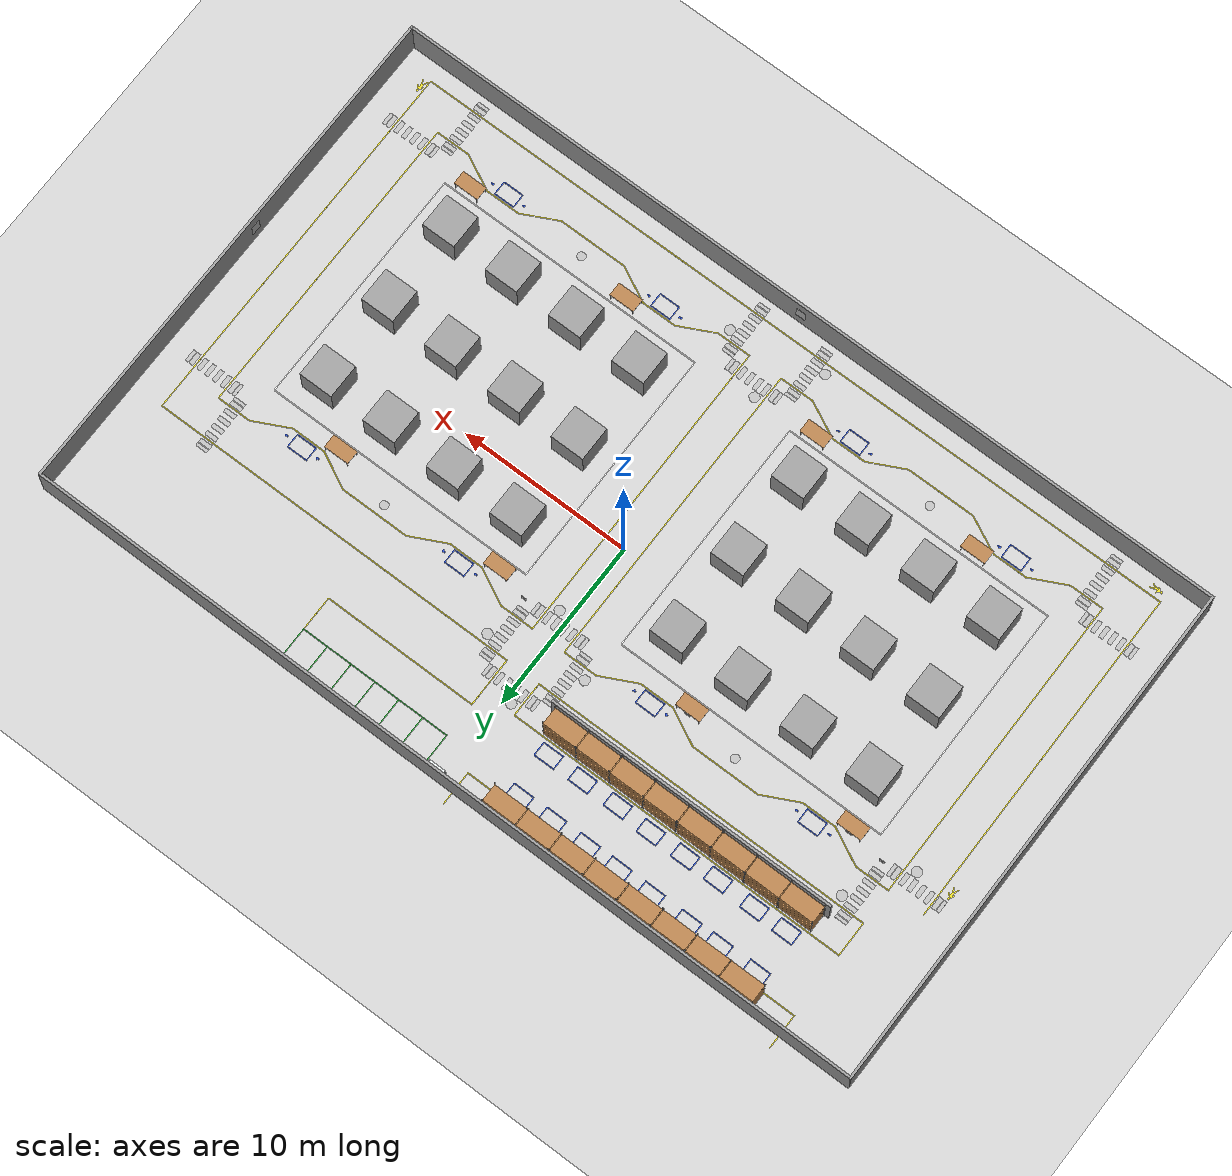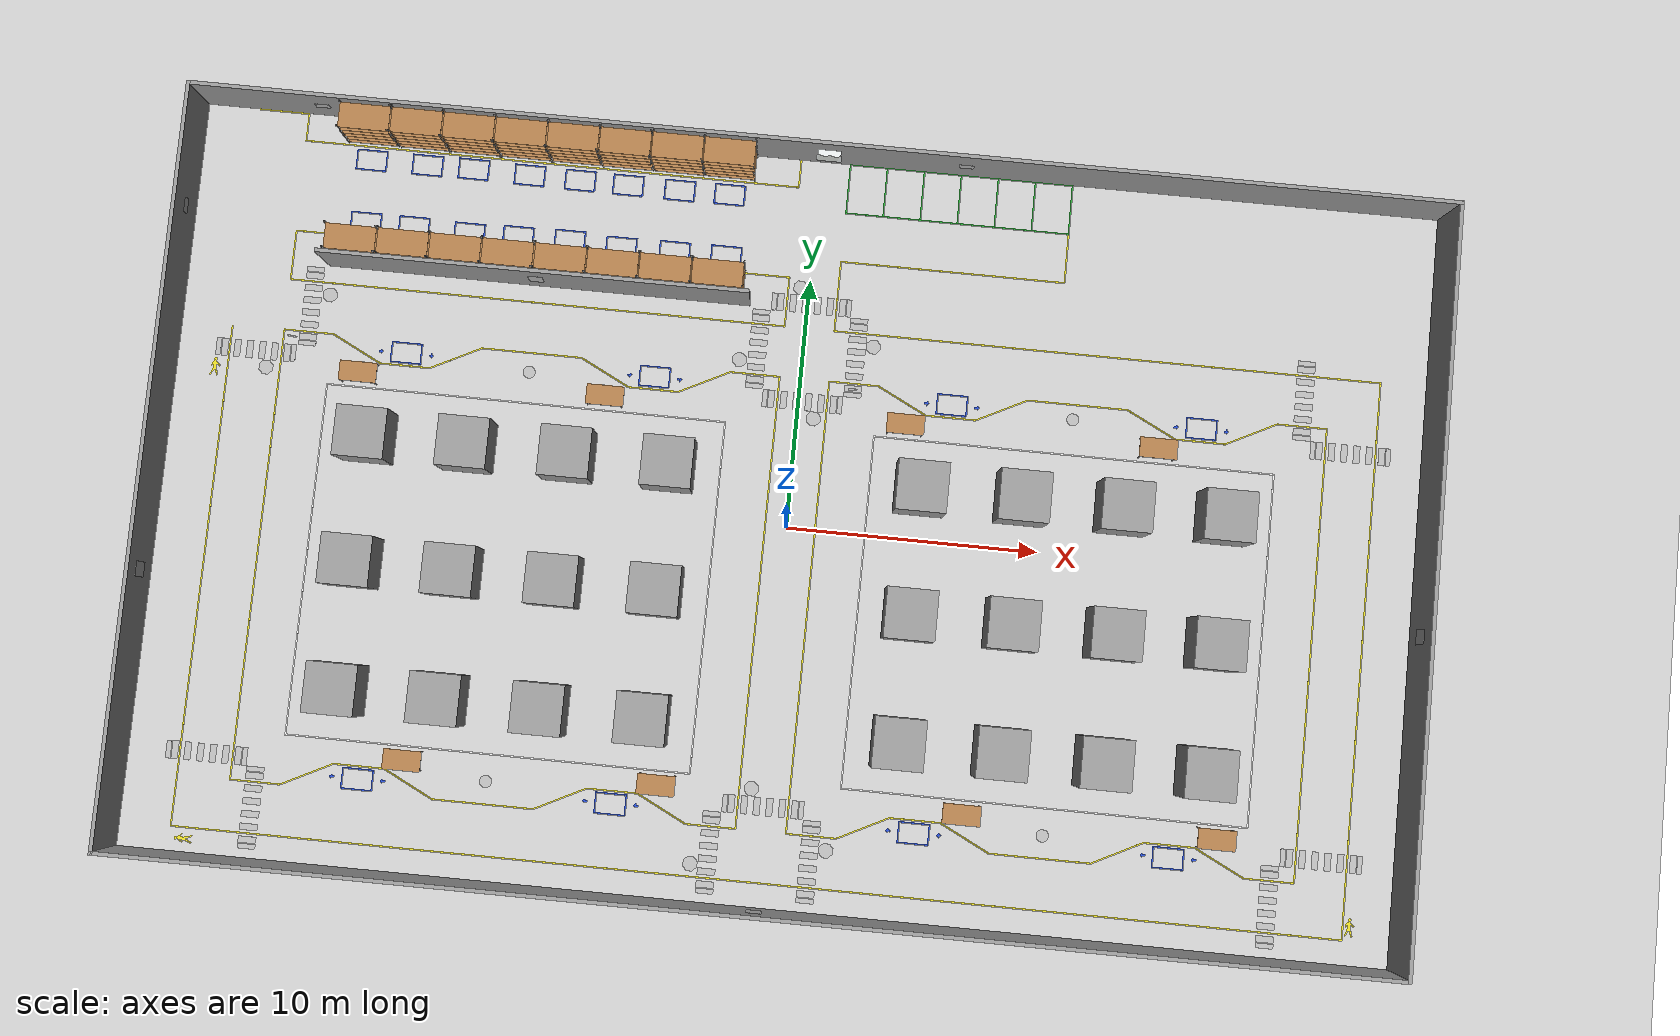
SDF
<sdf version="1.6">
 <world name="default">
  <light name="sun" type="directional">
   <pose>0 0 10 0 -0 0</pose>
   <diffuse>0.8 0.8 0.8 1</diffuse>
   <specular>0.2 0.2 0.2 1</specular>
   <attenuation>
    <range>1000</range>
    <constant>0.9</constant>
    <linear>0.01</linear>
    <quadratic>0.001</quadratic>
   </attenuation>
   <direction>-0.5 0.1 -0.9</direction>
  </light>
  <model name="ground_plane">
   <static>1</static>
   <link name="link">
    <collision name="collision">
     <geometry><plane><normal>0 0 1</normal><size>100 100</size></plane></geometry>
     <surface><friction><ode><mu>100</mu><mu2>50</mu2></ode></friction></surface>
    </collision>
    <visual name="visual">
     <cast_shadows>0</cast_shadows>
     <geometry><plane><normal>0 0 1</normal><size>100 100</size></plane></geometry>
     <material>
      <script><uri>file://media/materials/scripts/gazebo.material</uri><name>Gazebo/Grey</name></script>
     </material>
    </visual>
   </link>
  </model>
  <gravity>0 0 -9.8</gravity>
  <magnetic_field>6e-06 2.3e-05 -4.2e-05</magnetic_field>
  <atmosphere type="adiabatic"/>
  <physics name="default_physics" default="0" type="ode">
   <max_step_size>0.001</max_step_size>
   <real_time_factor>1</real_time_factor>
   <real_time_update_rate>1000</real_time_update_rate>
  </physics>
  <scene><ambient>0.4 0.4 0.4 1</ambient><background>0.7 0.7 0.7 1</background><shadows>1</shadows></scene>
  <spherical_coordinates>
   <surface_model>EARTH_WGS84</surface_model>
   <latitude_deg>0</latitude_deg>
   <longitude_deg>0</longitude_deg>
   <elevation>0</elevation>
   <heading_deg>0</heading_deg>
  </spherical_coordinates>
  <model name="factoryWall">
   <link name="Wall_0">
    <collision name="Wall_0_Collision">
     <geometry><box><size>30.15 0.15 2.5</size></box></geometry>
     <pose>0 0 1.25 0 -0 0</pose>
    </collision>
    <visual name="Wall_0_Visual">
     <pose>0 0 1.25 0 -0 0</pose>
     <geometry><box><size>30.15 0.15 2.5</size></box></geometry>
     <material>
      <script><uri>file://media/materials/scripts/gazebo.material</uri><name>Gazebo/Grey</name></script>
      <ambient>1 1 1 1</ambient>
     </material>
     <meta><layer>0</layer></meta>
    </visual>
    <pose>25 0 0 0 -0 1.5708</pose>
   </link>
   <link name="Wall_2">
    <collision name="Wall_2_Collision">
     <geometry><box><size>30.15 0.15 2.5</size></box></geometry>
     <pose>0 0 1.25 0 -0 0</pose>
    </collision>
    <visual name="Wall_2_Visual">
     <pose>0 0 1.25 0 -0 0</pose>
     <geometry><box><size>30.15 0.15 2.5</size></box></geometry>
     <material>
      <script><uri>file://media/materials/scripts/gazebo.material</uri><name>Gazebo/Grey</name></script>
      <ambient>1 1 1 1</ambient>
     </material>
     <meta><layer>0</layer></meta>
    </visual>
    <pose>-25 0 0 0 -0 1.5708</pose>
   </link>
   <link name="Wall_4">
    <collision name="Wall_4_Collision">
     <geometry><box><size>50.15 0.15 2.5</size></box></geometry>
     <pose>0 0 1.25 0 -0 0</pose>
    </collision>
    <visual name="Wall_4_Visual">
     <pose>0 0 1.25 0 -0 0</pose>
     <geometry><box><size>50.15 0.15 2.5</size></box></geometry>
     <material>
      <script><uri>file://media/materials/scripts/gazebo.material</uri><name>Gazebo/Grey</name></script>
      <ambient>1 1 1 1</ambient>
     </material>
     <meta><layer>0</layer></meta>
    </visual>
    <pose>0 15 0 0 -0 0</pose>
   </link>
   <link name="Wall_6">
    <collision name="Wall_6_Collision">
     <geometry><box><size>50.15 0.15 2.5</size></box></geometry>
     <pose>0 0 1.25 0 -0 0</pose>
    </collision>
    <visual name="Wall_6_Visual">
     <pose>0 0 1.25 0 -0 0</pose>
     <geometry><box><size>50.15 0.15 2.5</size></box></geometry>
     <material>
      <script><uri>file://media/materials/scripts/gazebo.material</uri><name>Gazebo/Grey</name></script>
      <ambient>1 1 1 1</ambient>
     </material>
     <meta><layer>0</layer></meta>
    </visual>
    <pose>0 -15 0 0 -0 0</pose>
   </link>
   <static>1</static>
  </model>
  <model name="factoryWall_1">
   <pose>-10.8 8.85 0 0 -0 1.570796</pose>
   <link name="Wall_0">
    <collision name="Wall1_0_Collision">
     <geometry><box><size>17 0.15 2.5</size></box></geometry>
     <pose>0 0 1.25 0 -0 0</pose>
    </collision>
    <visual name="Wall1_0_Visual">
     <pose>0 0 1.25 0 -0 0</pose>
     <geometry><box><size>17 0.15 2.5</size></box></geometry>
     <material>
      <script><uri>file://media/materials/scripts/gazebo.material</uri><name>Gazebo/Grey</name></script>
      <ambient>1 1 1 1</ambient>
     </material>
     <meta><layer>0</layer></meta>
    </visual>
    <pose>0 0 0 0 -0 1.570796</pose>
   </link>
   <static>1</static>
  </model>
  <model name="line20m">
   <link name="link_0">
    <inertial>
     <mass>1</mass>
     <inertia>
      <ixx>0.166667</ixx>
      <ixy>0</ixy>
      <ixz>0</ixz>
      <iyy>0.166667</iyy>
      <iyz>0</iyz>
      <izz>0.166667</izz>
     </inertia>
    </inertial>
    <visual name="visual">
     <geometry><box><size>0.05 20 0.001</size></box></geometry>
     <material>
      <lighting>1</lighting>
      <script><uri>file://media/materials/scripts/gazebo.material</uri><name>Gazebo/Yellow</name></script>
     </material>
    </visual>
   </link>
   <static>1</static>
   <pose>-22.9002 -3.99821 0 0 -0 0</pose>
  </model>
  <model name="line2m">
   <link name="link_0">
    <inertial>
     <mass>1</mass>
     <inertia>
      <ixx>0.166667</ixx>
      <ixy>0</ixy>
      <ixz>0</ixz>
      <iyy>0.166667</iyy>
      <iyz>0</iyz>
      <izz>0.166667</izz>
     </inertia>
    </inertial>
    <visual name="visual">
     <geometry><box><size>2 0.05 0.001</size></box></geometry>
     <material>
      <lighting>1</lighting>
      <script><uri>file://media/materials/scripts/gazebo.material</uri><name>Gazebo/Yellow</name></script>
     </material>
    </visual>
   </link>
   <static>1</static>
   <pose>-21.8772 14.9028 0 0 -0 0</pose>
  </model>
  <model name="line2m_0">
   <link name="link_0">
    <inertial>
     <mass>1</mass>
     <inertia>
      <ixx>0.166667</ixx>
      <ixy>0</ixy>
      <ixz>0</ixz>
      <iyy>0.166667</iyy>
      <iyz>0</iyz>
      <izz>0.166667</izz>
     </inertia>
    </inertial>
    <visual name="visual">
     <geometry><box><size>2 0.05 0.001</size></box></geometry>
     <material>
      <lighting>1</lighting>
      <script><uri>file://media/materials/scripts/gazebo.material</uri><name>Gazebo/Yellow</name></script>
     </material>
    </visual>
   </link>
   <static>1</static>
   <pose>-20.8518 14.7675 0 0 -0 1.5708</pose>
  </model>
  <model name="line20m_0">
   <link name="link_0">
    <inertial>
     <mass>1</mass>
     <inertia>
      <ixx>0.166667</ixx>
      <ixy>0</ixy>
      <ixz>0</ixz>
      <iyy>0.166667</iyy>
      <iyz>0</iyz>
      <izz>0.166667</izz>
     </inertia>
    </inertial>
    <visual name="visual">
     <geometry><box><size>0.05 20 0.001</size></box></geometry>
     <material>
      <lighting>1</lighting>
      <script><uri>file://media/materials/scripts/gazebo.material</uri><name>Gazebo/Yellow</name></script>
     </material>
    </visual>
   </link>
   <static>1</static>
   <pose>-10.8441 13.7915 0 0 -0 1.5708</pose>
  </model>
  <model name="shelves">
   <model name="shelf">
    <link name="link_1">
     <inertial>
      <mass>1</mass>
      <inertia>
       <ixx>0.166667</ixx>
       <ixy>0</ixy>
       <ixz>0</ixz>
       <iyy>0.166667</iyy>
       <iyz>0</iyz>
       <izz>0.166667</izz>
      </inertia>
     </inertial>
     <visual name="ModelPreview_2::link_1::visual_6">
      <pose>1 0.5 0 0 -0 0</pose>
      <geometry><mesh><uri>model://shelf/model/2-5mDirek.stl</uri><scale>0.001 0.001 0.001</scale></mesh></geometry>
      <material>
       <lighting>1</lighting>
       <script><uri>file://media/materials/scripts/gazebo.material</uri><name>Gazebo/Grey</name></script>
       <shader type="vertex"><normal_map>__default__</normal_map></shader>
       <ambient>0.3 0.3 0.3 1</ambient>
       <diffuse>0.7 0.7 0.7 1</diffuse>
       <specular>0.01 0.01 0.01 1</specular>
       <emissive>0 0 0 1</emissive>
      </material>
     </visual>
     <visual name="ModelPreview_2::link_1::visual_7">
      <pose>-1 0.5 0 0 -0 0</pose>
      <geometry><mesh><uri>model://shelf/model/2-5mDirek.stl</uri><scale>0.001 0.001 0.001</scale></mesh></geometry>
      <material>
       <lighting>1</lighting>
       <script><uri>file://media/materials/scripts/gazebo.material</uri><name>Gazebo/Grey</name></script>
       <shader type="vertex"><normal_map>__default__</normal_map></shader>
       <ambient>0.3 0.3 0.3 1</ambient>
       <diffuse>0.7 0.7 0.7 1</diffuse>
       <specular>0.01 0.01 0.01 1</specular>
       <emissive>0 0 0 1</emissive>
      </material>
     </visual>
     <visual name="ModelPreview_2::link_1::visual_4">
      <pose>0 0 1.85 0 -0 0</pose>
      <geometry><box><size>2 1 0.025</size></box></geometry>
      <material>
       <lighting>1</lighting>
       <script><uri>file://media/materials/scripts/gazebo.material</uri><name>Gazebo/WoodFloor</name></script>
       <shader type="vertex"><normal_map>__default__</normal_map></shader>
       <ambient>0.3 0.3 0.3 1</ambient>
       <diffuse>0.7 0.7 0.7 1</diffuse>
       <specular>0.01 0.01 0.01 1</specular>
       <emissive>0 0 0 1</emissive>
      </material>
     </visual>
     <visual name="ModelPreview_2::link_1::visual_5">
      <pose>0 0 2.25 0 -0 0</pose>
      <geometry><box><size>2 1 0.025</size></box></geometry>
      <material>
       <lighting>1</lighting>
       <script><uri>file://media/materials/scripts/gazebo.material</uri><name>Gazebo/WoodFloor</name></script>
       <shader type="vertex"><normal_map>__default__</normal_map></shader>
       <ambient>0.3 0.3 0.3 1</ambient>
       <diffuse>0.7 0.7 0.7 1</diffuse>
       <specular>0.01 0.01 0.01 1</specular>
       <emissive>0 0 0 1</emissive>
      </material>
     </visual>
     <visual name="ModelPreview_2::link_1::visual_3">
      <pose>0 0 1.45 0 -0 0</pose>
      <geometry><box><size>2 1 0.025</size></box></geometry>
      <material>
       <lighting>1</lighting>
       <script><uri>file://media/materials/scripts/gazebo.material</uri><name>Gazebo/WoodFloor</name></script>
       <shader type="vertex"><normal_map>__default__</normal_map></shader>
       <ambient>0.3 0.3 0.3 1</ambient>
       <diffuse>0.7 0.7 0.7 1</diffuse>
       <specular>0.01 0.01 0.01 1</specular>
       <emissive>0 0 0 1</emissive>
      </material>
     </visual>
     <visual name="ModelPreview_2::link_1::visual_1">
      <pose>0 0 0.65 0 -0 0</pose>
      <geometry><box><size>2 1 0.025</size></box></geometry>
      <material>
       <lighting>1</lighting>
       <script><uri>file://media/materials/scripts/gazebo.material</uri><name>Gazebo/WoodFloor</name></script>
       <shader type="vertex"><normal_map>__default__</normal_map></shader>
       <ambient>0.3 0.3 0.3 1</ambient>
       <diffuse>0.7 0.7 0.7 1</diffuse>
       <specular>0.01 0.01 0.01 1</specular>
       <emissive>0 0 0 1</emissive>
      </material>
     </visual>
     <visual name="visual">
      <pose>0 0 0.25 0 -0 0</pose>
      <geometry><box><size>2 1 0.025</size></box></geometry>
      <material>
       <lighting>1</lighting>
       <script><uri>file://media/materials/scripts/gazebo.material</uri><name>Gazebo/WoodFloor</name></script>
       <shader type="vertex"><normal_map>__default__</normal_map></shader>
       <ambient>0.3 0.3 0.3 1</ambient>
       <diffuse>0.7 0.7 0.7 1</diffuse>
       <specular>0.01 0.01 0.01 1</specular>
       <emissive>0 0 0 1</emissive>
      </material>
     </visual>
     <visual name="ModelPreview_2::link_1::visual_2">
      <pose>0 0 1.05 0 -0 0</pose>
      <geometry><box><size>2 1 0.025</size></box></geometry>
      <material>
       <lighting>1</lighting>
       <script><uri>file://media/materials/scripts/gazebo.material</uri><name>Gazebo/WoodFloor</name></script>
       <shader type="vertex"><normal_map>__default__</normal_map></shader>
       <ambient>0.3 0.3 0.3 1</ambient>
       <diffuse>0.7 0.7 0.7 1</diffuse>
       <specular>0.01 0.01 0.01 1</specular>
       <emissive>0 0 0 1</emissive>
      </material>
     </visual>
     <visual name="ModelPreview_2::link_1::visual_8">
      <pose>1 -0.5 0 0 -0 0</pose>
      <geometry><mesh><uri>model://shelf/model/2-5mDirek.stl</uri><scale>0.001 0.001 0.001</scale></mesh></geometry>
      <material>
       <lighting>1</lighting>
       <script><uri>file://media/materials/scripts/gazebo.material</uri><name>Gazebo/Grey</name></script>
       <shader type="vertex"><normal_map>__default__</normal_map></shader>
       <ambient>0.3 0.3 0.3 1</ambient>
       <diffuse>0.7 0.7 0.7 1</diffuse>
       <specular>0.01 0.01 0.01 1</specular>
       <emissive>0 0 0 1</emissive>
      </material>
     </visual>
     <visual name="ModelPreview_2::link_1::visual_9">
      <pose>-1 -0.5 0 0 -0 0</pose>
      <geometry><mesh><uri>model://shelf/model/2-5mDirek.stl</uri><scale>0.001 0.001 0.001</scale></mesh></geometry>
      <material>
       <lighting>1</lighting>
       <script><uri>file://media/materials/scripts/gazebo.material</uri><name>Gazebo/Grey</name></script>
       <shader type="vertex"><normal_map>__default__</normal_map></shader>
       <ambient>0.3 0.3 0.3 1</ambient>
       <diffuse>0.7 0.7 0.7 1</diffuse>
       <specular>0.01 0.01 0.01 1</specular>
       <emissive>0 0 0 1</emissive>
      </material>
     </visual>
     <collision name="collision_7">
      <pose>1 -0.5 1.25 0 -0 0</pose>
      <geometry><box><size>0.035 0.035 2.5</size></box></geometry>
      <surface>
       <friction>
        <ode><mu>1</mu><mu2>1</mu2><fdir1>0 0 0</fdir1><slip1>0</slip1><slip2>0</slip2></ode>
        <torsional>
         <coefficient>1</coefficient>
         <patch_radius>0</patch_radius>
         <surface_radius>0</surface_radius>
         <use_patch_radius>1</use_patch_radius>
         <ode><slip>0</slip></ode>
        </torsional>
       </friction>
       <bounce><restitution_coefficient>0</restitution_coefficient><threshold>1e+06</threshold></bounce>
       <contact>
        <collide_without_contact>0</collide_without_contact>
        <collide_without_contact_bitmask>1</collide_without_contact_bitmask>
        <collide_bitmask>1</collide_bitmask>
        <ode>
         <soft_cfm>0</soft_cfm>
         <soft_erp>0.2</soft_erp>
         <kp>1e+13</kp>
         <kd>1</kd>
         <max_vel>0.01</max_vel>
         <min_depth>0</min_depth>
        </ode>
        <bullet>
         <split_impulse>1</split_impulse>
         <split_impulse_penetration_threshold>-0.01</split_impulse_penetration_threshold>
         <soft_cfm>0</soft_cfm>
         <soft_erp>0.2</soft_erp>
         <kp>1e+13</kp>
         <kd>1</kd>
        </bullet>
       </contact>
      </surface>
     </collision>
     <collision name="collision_6">
      <pose>1 0.5 1.25 0 -0 0</pose>
      <geometry><box><size>0.035 0.035 2.5</size></box></geometry>
      <surface>
       <friction>
        <ode><mu>1</mu><mu2>1</mu2><fdir1>0 0 0</fdir1><slip1>0</slip1><slip2>0</slip2></ode>
        <torsional>
         <coefficient>1</coefficient>
         <patch_radius>0</patch_radius>
         <surface_radius>0</surface_radius>
         <use_patch_radius>1</use_patch_radius>
         <ode><slip>0</slip></ode>
        </torsional>
       </friction>
       <bounce><restitution_coefficient>0</restitution_coefficient><threshold>1e+06</threshold></bounce>
       <contact>
        <collide_without_contact>0</collide_without_contact>
        <collide_without_contact_bitmask>1</collide_without_contact_bitmask>
        <collide_bitmask>1</collide_bitmask>
        <ode>
         <soft_cfm>0</soft_cfm>
         <soft_erp>0.2</soft_erp>
         <kp>1e+13</kp>
         <kd>1</kd>
         <max_vel>0.01</max_vel>
         <min_depth>0</min_depth>
        </ode>
        <bullet>
         <split_impulse>1</split_impulse>
         <split_impulse_penetration_threshold>-0.01</split_impulse_penetration_threshold>
         <soft_cfm>0</soft_cfm>
         <soft_erp>0.2</soft_erp>
         <kp>1e+13</kp>
         <kd>1</kd>
        </bullet>
       </contact>
      </surface>
     </collision>
     <collision name="collision_2">
      <pose>0 0 1.05 0 -0 0</pose>
      <geometry><box><size>2 1 0.025</size></box></geometry>
      <surface>
       <friction>
        <ode><mu>1</mu><mu2>1</mu2><fdir1>0 0 0</fdir1><slip1>0</slip1><slip2>0</slip2></ode>
        <torsional>
         <coefficient>1</coefficient>
         <patch_radius>0</patch_radius>
         <surface_radius>0</surface_radius>
         <use_patch_radius>1</use_patch_radius>
         <ode><slip>0</slip></ode>
        </torsional>
       </friction>
       <bounce><restitution_coefficient>0</restitution_coefficient><threshold>1e+06</threshold></bounce>
       <contact>
        <collide_without_contact>0</collide_without_contact>
        <collide_without_contact_bitmask>1</collide_without_contact_bitmask>
        <collide_bitmask>1</collide_bitmask>
        <ode>
         <soft_cfm>0</soft_cfm>
         <soft_erp>0.2</soft_erp>
         <kp>1e+13</kp>
         <kd>1</kd>
         <max_vel>0.01</max_vel>
         <min_depth>0</min_depth>
        </ode>
        <bullet>
         <split_impulse>1</split_impulse>
         <split_impulse_penetration_threshold>-0.01</split_impulse_penetration_threshold>
         <soft_cfm>0</soft_cfm>
         <soft_erp>0.2</soft_erp>
         <kp>1e+13</kp>
         <kd>1</kd>
        </bullet>
       </contact>
      </surface>
     </collision>
     <collision name="collision_8">
      <pose>-1 0.5 1.25 0 -0 0</pose>
      <geometry><box><size>0.035 0.035 2.5</size></box></geometry>
      <surface>
       <friction>
        <ode><mu>1</mu><mu2>1</mu2><fdir1>0 0 0</fdir1><slip1>0</slip1><slip2>0</slip2></ode>
        <torsional>
         <coefficient>1</coefficient>
         <patch_radius>0</patch_radius>
         <surface_radius>0</surface_radius>
         <use_patch_radius>1</use_patch_radius>
         <ode><slip>0</slip></ode>
        </torsional>
       </friction>
       <bounce><restitution_coefficient>0</restitution_coefficient><threshold>1e+06</threshold></bounce>
       <contact>
        <collide_without_contact>0</collide_without_contact>
        <collide_without_contact_bitmask>1</collide_without_contact_bitmask>
        <collide_bitmask>1</collide_bitmask>
        <ode>
         <soft_cfm>0</soft_cfm>
         <soft_erp>0.2</soft_erp>
         <kp>1e+13</kp>
         <kd>1</kd>
         <max_vel>0.01</max_vel>
         <min_depth>0</min_depth>
        </ode>
        <bullet>
         <split_impulse>1</split_impulse>
         <split_impulse_penetration_threshold>-0.01</split_impulse_penetration_threshold>
         <soft_cfm>0</soft_cfm>
         <soft_erp>0.2</soft_erp>
         <kp>1e+13</kp>
         <kd>1</kd>
        </bullet>
       </contact>
      </surface>
     </collision>
     <collision name="collision_4">
      <pose>0 0 1.85 0 -0 0</pose>
      <geometry><box><size>2 1 0.025</size></box></geometry>
      <surface>
       <friction>
        <ode><mu>1</mu><mu2>1</mu2><fdir1>0 0 0</fdir1><slip1>0</slip1><slip2>0</slip2></ode>
        <torsional>
         <coefficient>1</coefficient>
         <patch_radius>0</patch_radius>
         <surface_radius>0</surface_radius>
         <use_patch_radius>1</use_patch_radius>
         <ode><slip>0</slip></ode>
        </torsional>
       </friction>
       <bounce><restitution_coefficient>0</restitution_coefficient><threshold>1e+06</threshold></bounce>
       <contact>
        <collide_without_contact>0</collide_without_contact>
        <collide_without_contact_bitmask>1</collide_without_contact_bitmask>
        <collide_bitmask>1</collide_bitmask>
        <ode>
         <soft_cfm>0</soft_cfm>
         <soft_erp>0.2</soft_erp>
         <kp>1e+13</kp>
         <kd>1</kd>
         <max_vel>0.01</max_vel>
         <min_depth>0</min_depth>
        </ode>
        <bullet>
         <split_impulse>1</split_impulse>
         <split_impulse_penetration_threshold>-0.01</split_impulse_penetration_threshold>
         <soft_cfm>0</soft_cfm>
         <soft_erp>0.2</soft_erp>
         <kp>1e+13</kp>
         <kd>1</kd>
        </bullet>
       </contact>
      </surface>
     </collision>
     <collision name="collision_1">
      <pose>0 0 0.65 0 -0 0</pose>
      <geometry><box><size>2 1 0.025</size></box></geometry>
      <surface>
       <friction>
        <ode><mu>1</mu><mu2>1</mu2><fdir1>0 0 0</fdir1><slip1>0</slip1><slip2>0</slip2></ode>
        <torsional>
         <coefficient>1</coefficient>
         <patch_radius>0</patch_radius>
         <surface_radius>0</surface_radius>
         <use_patch_radius>1</use_patch_radius>
         <ode><slip>0</slip></ode>
        </torsional>
       </friction>
       <bounce><restitution_coefficient>0</restitution_coefficient><threshold>1e+06</threshold></bounce>
       <contact>
        <collide_without_contact>0</collide_without_contact>
        <collide_without_contact_bitmask>1</collide_without_contact_bitmask>
        <collide_bitmask>1</collide_bitmask>
        <ode>
         <soft_cfm>0</soft_cfm>
         <soft_erp>0.2</soft_erp>
         <kp>1e+13</kp>
         <kd>1</kd>
         <max_vel>0.01</max_vel>
         <min_depth>0</min_depth>
        </ode>
        <bullet>
         <split_impulse>1</split_impulse>
         <split_impulse_penetration_threshold>-0.01</split_impulse_penetration_threshold>
         <soft_cfm>0</soft_cfm>
         <soft_erp>0.2</soft_erp>
         <kp>1e+13</kp>
         <kd>1</kd>
        </bullet>
       </contact>
      </surface>
     </collision>
     <collision name="collision_3">
      <pose>0 0 1.45 0 -0 0</pose>
      <geometry><box><size>2 1 0.025</size></box></geometry>
      <surface>
       <friction>
        <ode><mu>1</mu><mu2>1</mu2><fdir1>0 0 0</fdir1><slip1>0</slip1><slip2>0</slip2></ode>
        <torsional>
         <coefficient>1</coefficient>
         <patch_radius>0</patch_radius>
         <surface_radius>0</surface_radius>
         <use_patch_radius>1</use_patch_radius>
         <ode><slip>0</slip></ode>
        </torsional>
       </friction>
       <bounce><restitution_coefficient>0</restitution_coefficient><threshold>1e+06</threshold></bounce>
       <contact>
        <collide_without_contact>0</collide_without_contact>
        <collide_without_contact_bitmask>1</collide_without_contact_bitmask>
        <collide_bitmask>1</collide_bitmask>
        <ode>
         <soft_cfm>0</soft_cfm>
         <soft_erp>0.2</soft_erp>
         <kp>1e+13</kp>
         <kd>1</kd>
         <max_vel>0.01</max_vel>
         <min_depth>0</min_depth>
        </ode>
        <bullet>
         <split_impulse>1</split_impulse>
         <split_impulse_penetration_threshold>-0.01</split_impulse_penetration_threshold>
         <soft_cfm>0</soft_cfm>
         <soft_erp>0.2</soft_erp>
         <kp>1e+13</kp>
         <kd>1</kd>
        </bullet>
       </contact>
      </surface>
     </collision>
     <collision name="collision_5">
      <pose>0 0 2.25 0 -0 0</pose>
      <geometry><box><size>2 1 0.025</size></box></geometry>
      <surface>
       <friction>
        <ode><mu>1</mu><mu2>1</mu2><fdir1>0 0 0</fdir1><slip1>0</slip1><slip2>0</slip2></ode>
        <torsional>
         <coefficient>1</coefficient>
         <patch_radius>0</patch_radius>
         <surface_radius>0</surface_radius>
         <use_patch_radius>1</use_patch_radius>
         <ode><slip>0</slip></ode>
        </torsional>
       </friction>
       <bounce><restitution_coefficient>0</restitution_coefficient><threshold>1e+06</threshold></bounce>
       <contact>
        <collide_without_contact>0</collide_without_contact>
        <collide_without_contact_bitmask>1</collide_without_contact_bitmask>
        <collide_bitmask>1</collide_bitmask>
        <ode>
         <soft_cfm>0</soft_cfm>
         <soft_erp>0.2</soft_erp>
         <kp>1e+13</kp>
         <kd>1</kd>
         <max_vel>0.01</max_vel>
         <min_depth>0</min_depth>
        </ode>
        <bullet>
         <split_impulse>1</split_impulse>
         <split_impulse_penetration_threshold>-0.01</split_impulse_penetration_threshold>
         <soft_cfm>0</soft_cfm>
         <soft_erp>0.2</soft_erp>
         <kp>1e+13</kp>
         <kd>1</kd>
        </bullet>
       </contact>
      </surface>
     </collision>
     <collision name="collision">
      <pose>0 0 0.25 0 -0 0</pose>
      <geometry><box><size>2 1 0.025</size></box></geometry>
      <surface>
       <friction>
        <ode><mu>1</mu><mu2>1</mu2><fdir1>0 0 0</fdir1><slip1>0</slip1><slip2>0</slip2></ode>
        <torsional>
         <coefficient>1</coefficient>
         <patch_radius>0</patch_radius>
         <surface_radius>0</surface_radius>
         <use_patch_radius>1</use_patch_radius>
         <ode><slip>0</slip></ode>
        </torsional>
       </friction>
       <bounce><restitution_coefficient>0</restitution_coefficient><threshold>1e+06</threshold></bounce>
       <contact>
        <collide_without_contact>0</collide_without_contact>
        <collide_without_contact_bitmask>1</collide_without_contact_bitmask>
        <collide_bitmask>1</collide_bitmask>
        <ode>
         <soft_cfm>0</soft_cfm>
         <soft_erp>0.2</soft_erp>
         <kp>1e+13</kp>
         <kd>1</kd>
         <max_vel>0.01</max_vel>
         <min_depth>0</min_depth>
        </ode>
        <bullet>
         <split_impulse>1</split_impulse>
         <split_impulse_penetration_threshold>-0.01</split_impulse_penetration_threshold>
         <soft_cfm>0</soft_cfm>
         <soft_erp>0.2</soft_erp>
         <kp>1e+13</kp>
         <kd>1</kd>
        </bullet>
       </contact>
      </surface>
     </collision>
     <collision name="collision_9">
      <pose>-1 -0.5 1.25 0 -0 0</pose>
      <geometry><box><size>0.035 0.035 2.5</size></box></geometry>
      <surface>
       <friction>
        <ode><mu>1</mu><mu2>1</mu2><fdir1>0 0 0</fdir1><slip1>0</slip1><slip2>0</slip2></ode>
        <torsional>
         <coefficient>1</coefficient>
         <patch_radius>0</patch_radius>
         <surface_radius>0</surface_radius>
         <use_patch_radius>1</use_patch_radius>
         <ode><slip>0</slip></ode>
        </torsional>
       </friction>
       <bounce><restitution_coefficient>0</restitution_coefficient><threshold>1e+06</threshold></bounce>
       <contact>
        <collide_without_contact>0</collide_without_contact>
        <collide_without_contact_bitmask>1</collide_without_contact_bitmask>
        <collide_bitmask>1</collide_bitmask>
        <ode>
         <soft_cfm>0</soft_cfm>
         <soft_erp>0.2</soft_erp>
         <kp>1e+13</kp>
         <kd>1</kd>
         <max_vel>0.01</max_vel>
         <min_depth>0</min_depth>
        </ode>
        <bullet>
         <split_impulse>1</split_impulse>
         <split_impulse_penetration_threshold>-0.01</split_impulse_penetration_threshold>
         <soft_cfm>0</soft_cfm>
         <soft_erp>0.2</soft_erp>
         <kp>1e+13</kp>
         <kd>1</kd>
        </bullet>
       </contact>
      </surface>
     </collision>
    </link>
    <static>1</static>
    <pose>-1.03015 -0.001875 0 0 -0 0</pose>
   </model>
   <model name="shelf_0">
    <link name="link_1">
     <inertial>
      <mass>1</mass>
      <inertia>
       <ixx>0.166667</ixx>
       <ixy>0</ixy>
       <ixz>0</ixz>
       <iyy>0.166667</iyy>
       <iyz>0</iyz>
       <izz>0.166667</izz>
      </inertia>
     </inertial>
     <visual name="ModelPreview_2::link_1::visual_6">
      <pose>1 0.5 0 0 -0 0</pose>
      <geometry><mesh><uri>model://shelf/model/2-5mDirek.stl</uri><scale>0.001 0.001 0.001</scale></mesh></geometry>
      <material>
       <lighting>1</lighting>
       <script><uri>file://media/materials/scripts/gazebo.material</uri><name>Gazebo/Grey</name></script>
       <shader type="vertex"><normal_map>__default__</normal_map></shader>
       <ambient>0.3 0.3 0.3 1</ambient>
       <diffuse>0.7 0.7 0.7 1</diffuse>
       <specular>0.01 0.01 0.01 1</specular>
       <emissive>0 0 0 1</emissive>
      </material>
     </visual>
     <visual name="ModelPreview_2::link_1::visual_7">
      <pose>-1 0.5 0 0 -0 0</pose>
      <geometry><mesh><uri>model://shelf/model/2-5mDirek.stl</uri><scale>0.001 0.001 0.001</scale></mesh></geometry>
      <material>
       <lighting>1</lighting>
       <script><uri>file://media/materials/scripts/gazebo.material</uri><name>Gazebo/Grey</name></script>
       <shader type="vertex"><normal_map>__default__</normal_map></shader>
       <ambient>0.3 0.3 0.3 1</ambient>
       <diffuse>0.7 0.7 0.7 1</diffuse>
       <specular>0.01 0.01 0.01 1</specular>
       <emissive>0 0 0 1</emissive>
      </material>
     </visual>
     <visual name="ModelPreview_2::link_1::visual_4">
      <pose>0 0 1.85 0 -0 0</pose>
      <geometry><box><size>2 1 0.025</size></box></geometry>
      <material>
       <lighting>1</lighting>
       <script><uri>file://media/materials/scripts/gazebo.material</uri><name>Gazebo/WoodFloor</name></script>
       <shader type="vertex"><normal_map>__default__</normal_map></shader>
       <ambient>0.3 0.3 0.3 1</ambient>
       <diffuse>0.7 0.7 0.7 1</diffuse>
       <specular>0.01 0.01 0.01 1</specular>
       <emissive>0 0 0 1</emissive>
      </material>
     </visual>
     <visual name="ModelPreview_2::link_1::visual_5">
      <pose>0 0 2.25 0 -0 0</pose>
      <geometry><box><size>2 1 0.025</size></box></geometry>
      <material>
       <lighting>1</lighting>
       <script><uri>file://media/materials/scripts/gazebo.material</uri><name>Gazebo/WoodFloor</name></script>
       <shader type="vertex"><normal_map>__default__</normal_map></shader>
       <ambient>0.3 0.3 0.3 1</ambient>
       <diffuse>0.7 0.7 0.7 1</diffuse>
       <specular>0.01 0.01 0.01 1</specular>
       <emissive>0 0 0 1</emissive>
      </material>
     </visual>
     <visual name="ModelPreview_2::link_1::visual_3">
      <pose>0 0 1.45 0 -0 0</pose>
      <geometry><box><size>2 1 0.025</size></box></geometry>
      <material>
       <lighting>1</lighting>
       <script><uri>file://media/materials/scripts/gazebo.material</uri><name>Gazebo/WoodFloor</name></script>
       <shader type="vertex"><normal_map>__default__</normal_map></shader>
       <ambient>0.3 0.3 0.3 1</ambient>
       <diffuse>0.7 0.7 0.7 1</diffuse>
       <specular>0.01 0.01 0.01 1</specular>
       <emissive>0 0 0 1</emissive>
      </material>
     </visual>
     <visual name="ModelPreview_2::link_1::visual_1">
      <pose>0 0 0.65 0 -0 0</pose>
      <geometry><box><size>2 1 0.025</size></box></geometry>
      <material>
       <lighting>1</lighting>
       <script><uri>file://media/materials/scripts/gazebo.material</uri><name>Gazebo/WoodFloor</name></script>
       <shader type="vertex"><normal_map>__default__</normal_map></shader>
       <ambient>0.3 0.3 0.3 1</ambient>
       <diffuse>0.7 0.7 0.7 1</diffuse>
       <specular>0.01 0.01 0.01 1</specular>
       <emissive>0 0 0 1</emissive>
      </material>
     </visual>
     <visual name="visual">
      <pose>0 0 0.25 0 -0 0</pose>
      <geometry><box><size>2 1 0.025</size></box></geometry>
      <material>
       <lighting>1</lighting>
       <script><uri>file://media/materials/scripts/gazebo.material</uri><name>Gazebo/WoodFloor</name></script>
       <shader type="vertex"><normal_map>__default__</normal_map></shader>
       <ambient>0.3 0.3 0.3 1</ambient>
       <diffuse>0.7 0.7 0.7 1</diffuse>
       <specular>0.01 0.01 0.01 1</specular>
       <emissive>0 0 0 1</emissive>
      </material>
     </visual>
     <visual name="ModelPreview_2::link_1::visual_2">
      <pose>0 0 1.05 0 -0 0</pose>
      <geometry><box><size>2 1 0.025</size></box></geometry>
      <material>
       <lighting>1</lighting>
       <script><uri>file://media/materials/scripts/gazebo.material</uri><name>Gazebo/WoodFloor</name></script>
       <shader type="vertex"><normal_map>__default__</normal_map></shader>
       <ambient>0.3 0.3 0.3 1</ambient>
       <diffuse>0.7 0.7 0.7 1</diffuse>
       <specular>0.01 0.01 0.01 1</specular>
       <emissive>0 0 0 1</emissive>
      </material>
     </visual>
     <visual name="ModelPreview_2::link_1::visual_8">
      <pose>1 -0.5 0 0 -0 0</pose>
      <geometry><mesh><uri>model://shelf/model/2-5mDirek.stl</uri><scale>0.001 0.001 0.001</scale></mesh></geometry>
      <material>
       <lighting>1</lighting>
       <script><uri>file://media/materials/scripts/gazebo.material</uri><name>Gazebo/Grey</name></script>
       <shader type="vertex"><normal_map>__default__</normal_map></shader>
       <ambient>0.3 0.3 0.3 1</ambient>
       <diffuse>0.7 0.7 0.7 1</diffuse>
       <specular>0.01 0.01 0.01 1</specular>
       <emissive>0 0 0 1</emissive>
      </material>
     </visual>
     <visual name="ModelPreview_2::link_1::visual_9">
      <pose>-1 -0.5 0 0 -0 0</pose>
      <geometry><mesh><uri>model://shelf/model/2-5mDirek.stl</uri><scale>0.001 0.001 0.001</scale></mesh></geometry>
      <material>
       <lighting>1</lighting>
       <script><uri>file://media/materials/scripts/gazebo.material</uri><name>Gazebo/Grey</name></script>
       <shader type="vertex"><normal_map>__default__</normal_map></shader>
       <ambient>0.3 0.3 0.3 1</ambient>
       <diffuse>0.7 0.7 0.7 1</diffuse>
       <specular>0.01 0.01 0.01 1</specular>
       <emissive>0 0 0 1</emissive>
      </material>
     </visual>
     <collision name="collision_7">
      <pose>1 -0.5 1.25 0 -0 0</pose>
      <geometry><box><size>0.035 0.035 2.5</size></box></geometry>
      <surface>
       <friction>
        <ode><mu>1</mu><mu2>1</mu2><fdir1>0 0 0</fdir1><slip1>0</slip1><slip2>0</slip2></ode>
        <torsional>
         <coefficient>1</coefficient>
         <patch_radius>0</patch_radius>
         <surface_radius>0</surface_radius>
         <use_patch_radius>1</use_patch_radius>
         <ode><slip>0</slip></ode>
        </torsional>
       </friction>
       <bounce><restitution_coefficient>0</restitution_coefficient><threshold>1e+06</threshold></bounce>
       <contact>
        <collide_without_contact>0</collide_without_contact>
        <collide_without_contact_bitmask>1</collide_without_contact_bitmask>
        <collide_bitmask>1</collide_bitmask>
        <ode>
         <soft_cfm>0</soft_cfm>
         <soft_erp>0.2</soft_erp>
         <kp>1e+13</kp>
         <kd>1</kd>
         <max_vel>0.01</max_vel>
         <min_depth>0</min_depth>
        </ode>
        <bullet>
         <split_impulse>1</split_impulse>
         <split_impulse_penetration_threshold>-0.01</split_impulse_penetration_threshold>
         <soft_cfm>0</soft_cfm>
         <soft_erp>0.2</soft_erp>
         <kp>1e+13</kp>
         <kd>1</kd>
        </bullet>
       </contact>
      </surface>
     </collision>
     <collision name="collision_6">
      <pose>1 0.5 1.25 0 -0 0</pose>
      <geometry><box><size>0.035 0.035 2.5</size></box></geometry>
      <surface>
       <friction>
        <ode><mu>1</mu><mu2>1</mu2><fdir1>0 0 0</fdir1><slip1>0</slip1><slip2>0</slip2></ode>
        <torsional>
         <coefficient>1</coefficient>
         <patch_radius>0</patch_radius>
         <surface_radius>0</surface_radius>
         <use_patch_radius>1</use_patch_radius>
         <ode><slip>0</slip></ode>
        </torsional>
       </friction>
       <bounce><restitution_coefficient>0</restitution_coefficient><threshold>1e+06</threshold></bounce>
       <contact>
        <collide_without_contact>0</collide_without_contact>
        <collide_without_contact_bitmask>1</collide_without_contact_bitmask>
        <collide_bitmask>1</collide_bitmask>
        <ode>
         <soft_cfm>0</soft_cfm>
         <soft_erp>0.2</soft_erp>
         <kp>1e+13</kp>
         <kd>1</kd>
         <max_vel>0.01</max_vel>
         <min_depth>0</min_depth>
        </ode>
        <bullet>
         <split_impulse>1</split_impulse>
         <split_impulse_penetration_threshold>-0.01</split_impulse_penetration_threshold>
         <soft_cfm>0</soft_cfm>
         <soft_erp>0.2</soft_erp>
         <kp>1e+13</kp>
         <kd>1</kd>
        </bullet>
       </contact>
      </surface>
     </collision>
     <collision name="collision_2">
      <pose>0 0 1.05 0 -0 0</pose>
      <geometry><box><size>2 1 0.025</size></box></geometry>
      <surface>
       <friction>
        <ode><mu>1</mu><mu2>1</mu2><fdir1>0 0 0</fdir1><slip1>0</slip1><slip2>0</slip2></ode>
        <torsional>
         <coefficient>1</coefficient>
         <patch_radius>0</patch_radius>
         <surface_radius>0</surface_radius>
         <use_patch_radius>1</use_patch_radius>
         <ode><slip>0</slip></ode>
        </torsional>
       </friction>
       <bounce><restitution_coefficient>0</restitution_coefficient><threshold>1e+06</threshold></bounce>
       <contact>
        <collide_without_contact>0</collide_without_contact>
        <collide_without_contact_bitmask>1</collide_without_contact_bitmask>
        <collide_bitmask>1</collide_bitmask>
        <ode>
         <soft_cfm>0</soft_cfm>
         <soft_erp>0.2</soft_erp>
         <kp>1e+13</kp>
         <kd>1</kd>
         <max_vel>0.01</max_vel>
         <min_depth>0</min_depth>
        </ode>
        <bullet>
         <split_impulse>1</split_impulse>
         <split_impulse_penetration_threshold>-0.01</split_impulse_penetration_threshold>
         <soft_cfm>0</soft_cfm>
         <soft_erp>0.2</soft_erp>
         <kp>1e+13</kp>
         <kd>1</kd>
        </bullet>
       </contact>
      </surface>
     </collision>
     <collision name="collision_8">
      <pose>-1 0.5 1.25 0 -0 0</pose>
      <geometry><box><size>0.035 0.035 2.5</size></box></geometry>
      <surface>
       <friction>
        <ode><mu>1</mu><mu2>1</mu2><fdir1>0 0 0</fdir1><slip1>0</slip1><slip2>0</slip2></ode>
        <torsional>
         <coefficient>1</coefficient>
         <patch_radius>0</patch_radius>
         <surface_radius>0</surface_radius>
         <use_patch_radius>1</use_patch_radius>
         <ode><slip>0</slip></ode>
        </torsional>
       </friction>
       <bounce><restitution_coefficient>0</restitution_coefficient><threshold>1e+06</threshold></bounce>
       <contact>
        <collide_without_contact>0</collide_without_contact>
        <collide_without_contact_bitmask>1</collide_without_contact_bitmask>
        <collide_bitmask>1</collide_bitmask>
        <ode>
         <soft_cfm>0</soft_cfm>
         <soft_erp>0.2</soft_erp>
         <kp>1e+13</kp>
         <kd>1</kd>
         <max_vel>0.01</max_vel>
         <min_depth>0</min_depth>
        </ode>
        <bullet>
         <split_impulse>1</split_impulse>
         <split_impulse_penetration_threshold>-0.01</split_impulse_penetration_threshold>
         <soft_cfm>0</soft_cfm>
         <soft_erp>0.2</soft_erp>
         <kp>1e+13</kp>
         <kd>1</kd>
        </bullet>
       </contact>
      </surface>
     </collision>
     <collision name="collision_4">
      <pose>0 0 1.85 0 -0 0</pose>
      <geometry><box><size>2 1 0.025</size></box></geometry>
      <surface>
       <friction>
        <ode><mu>1</mu><mu2>1</mu2><fdir1>0 0 0</fdir1><slip1>0</slip1><slip2>0</slip2></ode>
        <torsional>
         <coefficient>1</coefficient>
         <patch_radius>0</patch_radius>
         <surface_radius>0</surface_radius>
         <use_patch_radius>1</use_patch_radius>
         <ode><slip>0</slip></ode>
        </torsional>
       </friction>
       <bounce><restitution_coefficient>0</restitution_coefficient><threshold>1e+06</threshold></bounce>
       <contact>
        <collide_without_contact>0</collide_without_contact>
        <collide_without_contact_bitmask>1</collide_without_contact_bitmask>
        <collide_bitmask>1</collide_bitmask>
        <ode>
         <soft_cfm>0</soft_cfm>
         <soft_erp>0.2</soft_erp>
         <kp>1e+13</kp>
         <kd>1</kd>
         <max_vel>0.01</max_vel>
         <min_depth>0</min_depth>
        </ode>
        <bullet>
         <split_impulse>1</split_impulse>
         <split_impulse_penetration_threshold>-0.01</split_impulse_penetration_threshold>
         <soft_cfm>0</soft_cfm>
         <soft_erp>0.2</soft_erp>
         <kp>1e+13</kp>
         <kd>1</kd>
        </bullet>
       </contact>
      </surface>
     </collision>
     <collision name="collision_1">
      <pose>0 0 0.65 0 -0 0</pose>
      <geometry><box><size>2 1 0.025</size></box></geometry>
      <surface>
       <friction>
        <ode><mu>1</mu><mu2>1</mu2><fdir1>0 0 0</fdir1><slip1>0</slip1><slip2>0</slip2></ode>
        <torsional>
         <coefficient>1</coefficient>
         <patch_radius>0</patch_radius>
         <surface_radius>0</surface_radius>
         <use_patch_radius>1</use_patch_radius>
         <ode><slip>0</slip></ode>
        </torsional>
       </friction>
       <bounce><restitution_coefficient>0</restitution_coefficient><threshold>1e+06</threshold></bounce>
       <contact>
        <collide_without_contact>0</collide_without_contact>
        <collide_without_contact_bitmask>1</collide_without_contact_bitmask>
        <collide_bitmask>1</collide_bitmask>
        <ode>
         <soft_cfm>0</soft_cfm>
         <soft_erp>0.2</soft_erp>
         <kp>1e+13</kp>
         <kd>1</kd>
         <max_vel>0.01</max_vel>
         <min_depth>0</min_depth>
        </ode>
        <bullet>
         <split_impulse>1</split_impulse>
         <split_impulse_penetration_threshold>-0.01</split_impulse_penetration_threshold>
         <soft_cfm>0</soft_cfm>
         <soft_erp>0.2</soft_erp>
         <kp>1e+13</kp>
         <kd>1</kd>
        </bullet>
       </contact>
      </surface>
     </collision>
     <collision name="collision_3">
      <pose>0 0 1.45 0 -0 0</pose>
      <geometry><box><size>2 1 0.025</size></box></geometry>
      <surface>
       <friction>
        <ode><mu>1</mu><mu2>1</mu2><fdir1>0 0 0</fdir1><slip1>0</slip1><slip2>0</slip2></ode>
        <torsional>
         <coefficient>1</coefficient>
         <patch_radius>0</patch_radius>
         <surface_radius>0</surface_radius>
         <use_patch_radius>1</use_patch_radius>
         <ode><slip>0</slip></ode>
        </torsional>
       </friction>
       <bounce><restitution_coefficient>0</restitution_coefficient><threshold>1e+06</threshold></bounce>
       <contact>
        <collide_without_contact>0</collide_without_contact>
        <collide_without_contact_bitmask>1</collide_without_contact_bitmask>
        <collide_bitmask>1</collide_bitmask>
        <ode>
         <soft_cfm>0</soft_cfm>
         <soft_erp>0.2</soft_erp>
         <kp>1e+13</kp>
         <kd>1</kd>
         <max_vel>0.01</max_vel>
         <min_depth>0</min_depth>
        </ode>
        <bullet>
         <split_impulse>1</split_impulse>
         <split_impulse_penetration_threshold>-0.01</split_impulse_penetration_threshold>
         <soft_cfm>0</soft_cfm>
         <soft_erp>0.2</soft_erp>
         <kp>1e+13</kp>
         <kd>1</kd>
        </bullet>
       </contact>
      </surface>
     </collision>
     <collision name="collision_5">
      <pose>0 0 2.25 0 -0 0</pose>
      <geometry><box><size>2 1 0.025</size></box></geometry>
      <surface>
       <friction>
        <ode><mu>1</mu><mu2>1</mu2><fdir1>0 0 0</fdir1><slip1>0</slip1><slip2>0</slip2></ode>
        <torsional>
         <coefficient>1</coefficient>
         <patch_radius>0</patch_radius>
         <surface_radius>0</surface_radius>
         <use_patch_radius>1</use_patch_radius>
         <ode><slip>0</slip></ode>
        </torsional>
       </friction>
       <bounce><restitution_coefficient>0</restitution_coefficient><threshold>1e+06</threshold></bounce>
       <contact>
        <collide_without_contact>0</collide_without_contact>
        <collide_without_contact_bitmask>1</collide_without_contact_bitmask>
        <collide_bitmask>1</collide_bitmask>
        <ode>
         <soft_cfm>0</soft_cfm>
         <soft_erp>0.2</soft_erp>
         <kp>1e+13</kp>
         <kd>1</kd>
         <max_vel>0.01</max_vel>
         <min_depth>0</min_depth>
        </ode>
        <bullet>
         <split_impulse>1</split_impulse>
         <split_impulse_penetration_threshold>-0.01</split_impulse_penetration_threshold>
         <soft_cfm>0</soft_cfm>
         <soft_erp>0.2</soft_erp>
         <kp>1e+13</kp>
         <kd>1</kd>
        </bullet>
       </contact>
      </surface>
     </collision>
     <collision name="collision">
      <pose>0 0 0.25 0 -0 0</pose>
      <geometry><box><size>2 1 0.025</size></box></geometry>
      <surface>
       <friction>
        <ode><mu>1</mu><mu2>1</mu2><fdir1>0 0 0</fdir1><slip1>0</slip1><slip2>0</slip2></ode>
        <torsional>
         <coefficient>1</coefficient>
         <patch_radius>0</patch_radius>
         <surface_radius>0</surface_radius>
         <use_patch_radius>1</use_patch_radius>
         <ode><slip>0</slip></ode>
        </torsional>
       </friction>
       <bounce><restitution_coefficient>0</restitution_coefficient><threshold>1e+06</threshold></bounce>
       <contact>
        <collide_without_contact>0</collide_without_contact>
        <collide_without_contact_bitmask>1</collide_without_contact_bitmask>
        <collide_bitmask>1</collide_bitmask>
        <ode>
         <soft_cfm>0</soft_cfm>
         <soft_erp>0.2</soft_erp>
         <kp>1e+13</kp>
         <kd>1</kd>
         <max_vel>0.01</max_vel>
         <min_depth>0</min_depth>
        </ode>
        <bullet>
         <split_impulse>1</split_impulse>
         <split_impulse_penetration_threshold>-0.01</split_impulse_penetration_threshold>
         <soft_cfm>0</soft_cfm>
         <soft_erp>0.2</soft_erp>
         <kp>1e+13</kp>
         <kd>1</kd>
        </bullet>
       </contact>
      </surface>
     </collision>
     <collision name="collision_9">
      <pose>-1 -0.5 1.25 0 -0 0</pose>
      <geometry><box><size>0.035 0.035 2.5</size></box></geometry>
      <surface>
       <friction>
        <ode><mu>1</mu><mu2>1</mu2><fdir1>0 0 0</fdir1><slip1>0</slip1><slip2>0</slip2></ode>
        <torsional>
         <coefficient>1</coefficient>
         <patch_radius>0</patch_radius>
         <surface_radius>0</surface_radius>
         <use_patch_radius>1</use_patch_radius>
         <ode><slip>0</slip></ode>
        </torsional>
       </friction>
       <bounce><restitution_coefficient>0</restitution_coefficient><threshold>1e+06</threshold></bounce>
       <contact>
        <collide_without_contact>0</collide_without_contact>
        <collide_without_contact_bitmask>1</collide_without_contact_bitmask>
        <collide_bitmask>1</collide_bitmask>
        <ode>
         <soft_cfm>0</soft_cfm>
         <soft_erp>0.2</soft_erp>
         <kp>1e+13</kp>
         <kd>1</kd>
         <max_vel>0.01</max_vel>
         <min_depth>0</min_depth>
        </ode>
        <bullet>
         <split_impulse>1</split_impulse>
         <split_impulse_penetration_threshold>-0.01</split_impulse_penetration_threshold>
         <soft_cfm>0</soft_cfm>
         <soft_erp>0.2</soft_erp>
         <kp>1e+13</kp>
         <kd>1</kd>
        </bullet>
       </contact>
      </surface>
     </collision>
    </link>
    <static>1</static>
    <pose>-3.09011 -0.000869 0 0 -0 0</pose>
   </model>
   <model name="shelf_1">
    <link name="link_1">
     <inertial>
      <mass>1</mass>
      <inertia>
       <ixx>0.166667</ixx>
       <ixy>0</ixy>
       <ixz>0</ixz>
       <iyy>0.166667</iyy>
       <iyz>0</iyz>
       <izz>0.166667</izz>
      </inertia>
     </inertial>
     <visual name="ModelPreview_2::link_1::visual_6">
      <pose>1 0.5 0 0 -0 0</pose>
      <geometry><mesh><uri>model://shelf/model/2-5mDirek.stl</uri><scale>0.001 0.001 0.001</scale></mesh></geometry>
      <material>
       <lighting>1</lighting>
       <script><uri>file://media/materials/scripts/gazebo.material</uri><name>Gazebo/Grey</name></script>
       <shader type="vertex"><normal_map>__default__</normal_map></shader>
       <ambient>0.3 0.3 0.3 1</ambient>
       <diffuse>0.7 0.7 0.7 1</diffuse>
       <specular>0.01 0.01 0.01 1</specular>
       <emissive>0 0 0 1</emissive>
      </material>
     </visual>
     <visual name="ModelPreview_2::link_1::visual_7">
      <pose>-1 0.5 0 0 -0 0</pose>
      <geometry><mesh><uri>model://shelf/model/2-5mDirek.stl</uri><scale>0.001 0.001 0.001</scale></mesh></geometry>
      <material>
       <lighting>1</lighting>
       <script><uri>file://media/materials/scripts/gazebo.material</uri><name>Gazebo/Grey</name></script>
       <shader type="vertex"><normal_map>__default__</normal_map></shader>
       <ambient>0.3 0.3 0.3 1</ambient>
       <diffuse>0.7 0.7 0.7 1</diffuse>
       <specular>0.01 0.01 0.01 1</specular>
       <emissive>0 0 0 1</emissive>
      </material>
     </visual>
     <visual name="ModelPreview_2::link_1::visual_4">
      <pose>0 0 1.85 0 -0 0</pose>
      <geometry><box><size>2 1 0.025</size></box></geometry>
      <material>
       <lighting>1</lighting>
       <script><uri>file://media/materials/scripts/gazebo.material</uri><name>Gazebo/WoodFloor</name></script>
       <shader type="vertex"><normal_map>__default__</normal_map></shader>
       <ambient>0.3 0.3 0.3 1</ambient>
       <diffuse>0.7 0.7 0.7 1</diffuse>
       <specular>0.01 0.01 0.01 1</specular>
       <emissive>0 0 0 1</emissive>
      </material>
     </visual>
     <visual name="ModelPreview_2::link_1::visual_5">
      <pose>0 0 2.25 0 -0 0</pose>
      <geometry><box><size>2 1 0.025</size></box></geometry>
      <material>
       <lighting>1</lighting>
       <script><uri>file://media/materials/scripts/gazebo.material</uri><name>Gazebo/WoodFloor</name></script>
       <shader type="vertex"><normal_map>__default__</normal_map></shader>
       <ambient>0.3 0.3 0.3 1</ambient>
       <diffuse>0.7 0.7 0.7 1</diffuse>
       <specular>0.01 0.01 0.01 1</specular>
       <emissive>0 0 0 1</emissive>
      </material>
     </visual>
     <visual name="ModelPreview_2::link_1::visual_3">
      <pose>0 0 1.45 0 -0 0</pose>
      <geometry><box><size>2 1 0.025</size></box></geometry>
      <material>
       <lighting>1</lighting>
       <script><uri>file://media/materials/scripts/gazebo.material</uri><name>Gazebo/WoodFloor</name></script>
       <shader type="vertex"><normal_map>__default__</normal_map></shader>
       <ambient>0.3 0.3 0.3 1</ambient>
       <diffuse>0.7 0.7 0.7 1</diffuse>
       <specular>0.01 0.01 0.01 1</specular>
       <emissive>0 0 0 1</emissive>
      </material>
     </visual>
     <visual name="ModelPreview_2::link_1::visual_1">
      <pose>0 0 0.65 0 -0 0</pose>
      <geometry><box><size>2 1 0.025</size></box></geometry>
      <material>
       <lighting>1</lighting>
       <script><uri>file://media/materials/scripts/gazebo.material</uri><name>Gazebo/WoodFloor</name></script>
       <shader type="vertex"><normal_map>__default__</normal_map></shader>
       <ambient>0.3 0.3 0.3 1</ambient>
       <diffuse>0.7 0.7 0.7 1</diffuse>
       <specular>0.01 0.01 0.01 1</specular>
       <emissive>0 0 0 1</emissive>
      </material>
     </visual>
     <visual name="visual">
      <pose>0 0 0.25 0 -0 0</pose>
      <geometry><box><size>2 1 0.025</size></box></geometry>
      <material>
       <lighting>1</lighting>
       <script><uri>file://media/materials/scripts/gazebo.material</uri><name>Gazebo/WoodFloor</name></script>
       <shader type="vertex"><normal_map>__default__</normal_map></shader>
       <ambient>0.3 0.3 0.3 1</ambient>
       <diffuse>0.7 0.7 0.7 1</diffuse>
       <specular>0.01 0.01 0.01 1</specular>
       <emissive>0 0 0 1</emissive>
      </material>
     </visual>
     <visual name="ModelPreview_2::link_1::visual_2">
      <pose>0 0 1.05 0 -0 0</pose>
      <geometry><box><size>2 1 0.025</size></box></geometry>
      <material>
       <lighting>1</lighting>
       <script><uri>file://media/materials/scripts/gazebo.material</uri><name>Gazebo/WoodFloor</name></script>
       <shader type="vertex"><normal_map>__default__</normal_map></shader>
       <ambient>0.3 0.3 0.3 1</ambient>
       <diffuse>0.7 0.7 0.7 1</diffuse>
       <specular>0.01 0.01 0.01 1</specular>
       <emissive>0 0 0 1</emissive>
      </material>
     </visual>
     <visual name="ModelPreview_2::link_1::visual_8">
      <pose>1 -0.5 0 0 -0 0</pose>
      <geometry><mesh><uri>model://shelf/model/2-5mDirek.stl</uri><scale>0.001 0.001 0.001</scale></mesh></geometry>
      <material>
       <lighting>1</lighting>
       <script><uri>file://media/materials/scripts/gazebo.material</uri><name>Gazebo/Grey</name></script>
       <shader type="vertex"><normal_map>__default__</normal_map></shader>
       <ambient>0.3 0.3 0.3 1</ambient>
       <diffuse>0.7 0.7 0.7 1</diffuse>
       <specular>0.01 0.01 0.01 1</specular>
       <emissive>0 0 0 1</emissive>
      </material>
     </visual>
     <visual name="ModelPreview_2::link_1::visual_9">
      <pose>-1 -0.5 0 0 -0 0</pose>
      <geometry><mesh><uri>model://shelf/model/2-5mDirek.stl</uri><scale>0.001 0.001 0.001</scale></mesh></geometry>
      <material>
       <lighting>1</lighting>
       <script><uri>file://media/materials/scripts/gazebo.material</uri><name>Gazebo/Grey</name></script>
       <shader type="vertex"><normal_map>__default__</normal_map></shader>
       <ambient>0.3 0.3 0.3 1</ambient>
       <diffuse>0.7 0.7 0.7 1</diffuse>
       <specular>0.01 0.01 0.01 1</specular>
       <emissive>0 0 0 1</emissive>
      </material>
     </visual>
     <collision name="collision_7">
      <pose>1 -0.5 1.25 0 -0 0</pose>
      <geometry><box><size>0.035 0.035 2.5</size></box></geometry>
      <surface>
       <friction>
        <ode><mu>1</mu><mu2>1</mu2><fdir1>0 0 0</fdir1><slip1>0</slip1><slip2>0</slip2></ode>
        <torsional>
         <coefficient>1</coefficient>
         <patch_radius>0</patch_radius>
         <surface_radius>0</surface_radius>
         <use_patch_radius>1</use_patch_radius>
         <ode><slip>0</slip></ode>
        </torsional>
       </friction>
       <bounce><restitution_coefficient>0</restitution_coefficient><threshold>1e+06</threshold></bounce>
       <contact>
        <collide_without_contact>0</collide_without_contact>
        <collide_without_contact_bitmask>1</collide_without_contact_bitmask>
        <collide_bitmask>1</collide_bitmask>
        <ode>
         <soft_cfm>0</soft_cfm>
         <soft_erp>0.2</soft_erp>
         <kp>1e+13</kp>
         <kd>1</kd>
         <max_vel>0.01</max_vel>
         <min_depth>0</min_depth>
        </ode>
        <bullet>
         <split_impulse>1</split_impulse>
         <split_impulse_penetration_threshold>-0.01</split_impulse_penetration_threshold>
         <soft_cfm>0</soft_cfm>
         <soft_erp>0.2</soft_erp>
         <kp>1e+13</kp>
         <kd>1</kd>
        </bullet>
       </contact>
      </surface>
     </collision>
     <collision name="collision_6">
      <pose>1 0.5 1.25 0 -0 0</pose>
      <geometry><box><size>0.035 0.035 2.5</size></box></geometry>
      <surface>
       <friction>
        <ode><mu>1</mu><mu2>1</mu2><fdir1>0 0 0</fdir1><slip1>0</slip1><slip2>0</slip2></ode>
        <torsional>
         <coefficient>1</coefficient>
         <patch_radius>0</patch_radius>
         <surface_radius>0</surface_radius>
         <use_patch_radius>1</use_patch_radius>
         <ode><slip>0</slip></ode>
        </torsional>
       </friction>
       <bounce><restitution_coefficient>0</restitution_coefficient><threshold>1e+06</threshold></bounce>
       <contact>
        <collide_without_contact>0</collide_without_contact>
        <collide_without_contact_bitmask>1</collide_without_contact_bitmask>
        <collide_bitmask>1</collide_bitmask>
        <ode>
         <soft_cfm>0</soft_cfm>
         <soft_erp>0.2</soft_erp>
         <kp>1e+13</kp>
         <kd>1</kd>
         <max_vel>0.01</max_vel>
         <min_depth>0</min_depth>
        </ode>
        <bullet>
         <split_impulse>1</split_impulse>
         <split_impulse_penetration_threshold>-0.01</split_impulse_penetration_threshold>
         <soft_cfm>0</soft_cfm>
         <soft_erp>0.2</soft_erp>
         <kp>1e+13</kp>
         <kd>1</kd>
        </bullet>
       </contact>
      </surface>
     </collision>
     <collision name="collision_2">
      <pose>0 0 1.05 0 -0 0</pose>
      <geometry><box><size>2 1 0.025</size></box></geometry>
      <surface>
       <friction>
        <ode><mu>1</mu><mu2>1</mu2><fdir1>0 0 0</fdir1><slip1>0</slip1><slip2>0</slip2></ode>
        <torsional>
         <coefficient>1</coefficient>
         <patch_radius>0</patch_radius>
         <surface_radius>0</surface_radius>
         <use_patch_radius>1</use_patch_radius>
         <ode><slip>0</slip></ode>
        </torsional>
       </friction>
       <bounce><restitution_coefficient>0</restitution_coefficient><threshold>1e+06</threshold></bounce>
       <contact>
        <collide_without_contact>0</collide_without_contact>
        <collide_without_contact_bitmask>1</collide_without_contact_bitmask>
        <collide_bitmask>1</collide_bitmask>
        <ode>
         <soft_cfm>0</soft_cfm>
         <soft_erp>0.2</soft_erp>
         <kp>1e+13</kp>
         <kd>1</kd>
         <max_vel>0.01</max_vel>
         <min_depth>0</min_depth>
        </ode>
        <bullet>
         <split_impulse>1</split_impulse>
         <split_impulse_penetration_threshold>-0.01</split_impulse_penetration_threshold>
         <soft_cfm>0</soft_cfm>
         <soft_erp>0.2</soft_erp>
         <kp>1e+13</kp>
         <kd>1</kd>
        </bullet>
       </contact>
      </surface>
     </collision>
     <collision name="collision_8">
      <pose>-1 0.5 1.25 0 -0 0</pose>
      <geometry><box><size>0.035 0.035 2.5</size></box></geometry>
      <surface>
       <friction>
        <ode><mu>1</mu><mu2>1</mu2><fdir1>0 0 0</fdir1><slip1>0</slip1><slip2>0</slip2></ode>
        <torsional>
         <coefficient>1</coefficient>
         <patch_radius>0</patch_radius>
         <surface_radius>0</surface_radius>
         <use_patch_radius>1</use_patch_radius>
         <ode><slip>0</slip></ode>
        </torsional>
       </friction>
       <bounce><restitution_coefficient>0</restitution_coefficient><threshold>1e+06</threshold></bounce>
       <contact>
        <collide_without_contact>0</collide_without_contact>
        <collide_without_contact_bitmask>1</collide_without_contact_bitmask>
        <collide_bitmask>1</collide_bitmask>
        <ode>
         <soft_cfm>0</soft_cfm>
         <soft_erp>0.2</soft_erp>
         <kp>1e+13</kp>
         <kd>1</kd>
         <max_vel>0.01</max_vel>
         <min_depth>0</min_depth>
        </ode>
        <bullet>
         <split_impulse>1</split_impulse>
         <split_impulse_penetration_threshold>-0.01</split_impulse_penetration_threshold>
         <soft_cfm>0</soft_cfm>
         <soft_erp>0.2</soft_erp>
         <kp>1e+13</kp>
         <kd>1</kd>
        </bullet>
       </contact>
      </surface>
     </collision>
     <collision name="collision_4">
      <pose>0 0 1.85 0 -0 0</pose>
      <geometry><box><size>2 1 0.025</size></box></geometry>
      <surface>
       <friction>
        <ode><mu>1</mu><mu2>1</mu2><fdir1>0 0 0</fdir1><slip1>0</slip1><slip2>0</slip2></ode>
        <torsional>
         <coefficient>1</coefficient>
         <patch_radius>0</patch_radius>
         <surface_radius>0</surface_radius>
         <use_patch_radius>1</use_patch_radius>
         <ode><slip>0</slip></ode>
        </torsional>
       </friction>
       <bounce><restitution_coefficient>0</restitution_coefficient><threshold>1e+06</threshold></bounce>
       <contact>
        <collide_without_contact>0</collide_without_contact>
        <collide_without_contact_bitmask>1</collide_without_contact_bitmask>
        <collide_bitmask>1</collide_bitmask>
        <ode>
         <soft_cfm>0</soft_cfm>
         <soft_erp>0.2</soft_erp>
         <kp>1e+13</kp>
         <kd>1</kd>
         <max_vel>0.01</max_vel>
         <min_depth>0</min_depth>
        </ode>
        <bullet>
         <split_impulse>1</split_impulse>
         <split_impulse_penetration_threshold>-0.01</split_impulse_penetration_threshold>
         <soft_cfm>0</soft_cfm>
         <soft_erp>0.2</soft_erp>
         <kp>1e+13</kp>
         <kd>1</kd>
        </bullet>
       </contact>
      </surface>
     </collision>
     <collision name="collision_1">
      <pose>0 0 0.65 0 -0 0</pose>
      <geometry><box><size>2 1 0.025</size></box></geometry>
      <surface>
       <friction>
        <ode><mu>1</mu><mu2>1</mu2><fdir1>0 0 0</fdir1><slip1>0</slip1><slip2>0</slip2></ode>
        <torsional>
         <coefficient>1</coefficient>
         <patch_radius>0</patch_radius>
         <surface_radius>0</surface_radius>
         <use_patch_radius>1</use_patch_radius>
         <ode><slip>0</slip></ode>
        </torsional>
       </friction>
       <bounce><restitution_coefficient>0</restitution_coefficient><threshold>1e+06</threshold></bounce>
       <contact>
        <collide_without_contact>0</collide_without_contact>
        <collide_without_contact_bitmask>1</collide_without_contact_bitmask>
        <collide_bitmask>1</collide_bitmask>
        <ode>
         <soft_cfm>0</soft_cfm>
         <soft_erp>0.2</soft_erp>
         <kp>1e+13</kp>
         <kd>1</kd>
         <max_vel>0.01</max_vel>
         <min_depth>0</min_depth>
        </ode>
        <bullet>
         <split_impulse>1</split_impulse>
         <split_impulse_penetration_threshold>-0.01</split_impulse_penetration_threshold>
         <soft_cfm>0</soft_cfm>
         <soft_erp>0.2</soft_erp>
         <kp>1e+13</kp>
         <kd>1</kd>
        </bullet>
       </contact>
      </surface>
     </collision>
     <collision name="collision_3">
      <pose>0 0 1.45 0 -0 0</pose>
      <geometry><box><size>2 1 0.025</size></box></geometry>
      <surface>
       <friction>
        <ode><mu>1</mu><mu2>1</mu2><fdir1>0 0 0</fdir1><slip1>0</slip1><slip2>0</slip2></ode>
        <torsional>
         <coefficient>1</coefficient>
         <patch_radius>0</patch_radius>
         <surface_radius>0</surface_radius>
         <use_patch_radius>1</use_patch_radius>
         <ode><slip>0</slip></ode>
        </torsional>
       </friction>
       <bounce><restitution_coefficient>0</restitution_coefficient><threshold>1e+06</threshold></bounce>
       <contact>
        <collide_without_contact>0</collide_without_contact>
        <collide_without_contact_bitmask>1</collide_without_contact_bitmask>
        <collide_bitmask>1</collide_bitmask>
        <ode>
         <soft_cfm>0</soft_cfm>
         <soft_erp>0.2</soft_erp>
         <kp>1e+13</kp>
         <kd>1</kd>
         <max_vel>0.01</max_vel>
         <min_depth>0</min_depth>
        </ode>
        <bullet>
         <split_impulse>1</split_impulse>
         <split_impulse_penetration_threshold>-0.01</split_impulse_penetration_threshold>
         <soft_cfm>0</soft_cfm>
         <soft_erp>0.2</soft_erp>
         <kp>1e+13</kp>
         <kd>1</kd>
        </bullet>
       </contact>
      </surface>
     </collision>
     <collision name="collision_5">
      <pose>0 0 2.25 0 -0 0</pose>
      <geometry><box><size>2 1 0.025</size></box></geometry>
      <surface>
       <friction>
        <ode><mu>1</mu><mu2>1</mu2><fdir1>0 0 0</fdir1><slip1>0</slip1><slip2>0</slip2></ode>
        <torsional>
         <coefficient>1</coefficient>
         <patch_radius>0</patch_radius>
         <surface_radius>0</surface_radius>
         <use_patch_radius>1</use_patch_radius>
         <ode><slip>0</slip></ode>
        </torsional>
       </friction>
       <bounce><restitution_coefficient>0</restitution_coefficient><threshold>1e+06</threshold></bounce>
       <contact>
        <collide_without_contact>0</collide_without_contact>
        <collide_without_contact_bitmask>1</collide_without_contact_bitmask>
        <collide_bitmask>1</collide_bitmask>
        <ode>
         <soft_cfm>0</soft_cfm>
         <soft_erp>0.2</soft_erp>
         <kp>1e+13</kp>
         <kd>1</kd>
         <max_vel>0.01</max_vel>
         <min_depth>0</min_depth>
        </ode>
        <bullet>
         <split_impulse>1</split_impulse>
         <split_impulse_penetration_threshold>-0.01</split_impulse_penetration_threshold>
         <soft_cfm>0</soft_cfm>
         <soft_erp>0.2</soft_erp>
         <kp>1e+13</kp>
         <kd>1</kd>
        </bullet>
       </contact>
      </surface>
     </collision>
     <collision name="collision">
      <pose>0 0 0.25 0 -0 0</pose>
      <geometry><box><size>2 1 0.025</size></box></geometry>
      <surface>
       <friction>
        <ode><mu>1</mu><mu2>1</mu2><fdir1>0 0 0</fdir1><slip1>0</slip1><slip2>0</slip2></ode>
        <torsional>
         <coefficient>1</coefficient>
         <patch_radius>0</patch_radius>
         <surface_radius>0</surface_radius>
         <use_patch_radius>1</use_patch_radius>
         <ode><slip>0</slip></ode>
        </torsional>
       </friction>
       <bounce><restitution_coefficient>0</restitution_coefficient><threshold>1e+06</threshold></bounce>
       <contact>
        <collide_without_contact>0</collide_without_contact>
        <collide_without_contact_bitmask>1</collide_without_contact_bitmask>
        <collide_bitmask>1</collide_bitmask>
        <ode>
         <soft_cfm>0</soft_cfm>
         <soft_erp>0.2</soft_erp>
         <kp>1e+13</kp>
         <kd>1</kd>
         <max_vel>0.01</max_vel>
         <min_depth>0</min_depth>
        </ode>
        <bullet>
         <split_impulse>1</split_impulse>
         <split_impulse_penetration_threshold>-0.01</split_impulse_penetration_threshold>
         <soft_cfm>0</soft_cfm>
         <soft_erp>0.2</soft_erp>
         <kp>1e+13</kp>
         <kd>1</kd>
        </bullet>
       </contact>
      </surface>
     </collision>
     <collision name="collision_9">
      <pose>-1 -0.5 1.25 0 -0 0</pose>
      <geometry><box><size>0.035 0.035 2.5</size></box></geometry>
      <surface>
       <friction>
        <ode><mu>1</mu><mu2>1</mu2><fdir1>0 0 0</fdir1><slip1>0</slip1><slip2>0</slip2></ode>
        <torsional>
         <coefficient>1</coefficient>
         <patch_radius>0</patch_radius>
         <surface_radius>0</surface_radius>
         <use_patch_radius>1</use_patch_radius>
         <ode><slip>0</slip></ode>
        </torsional>
       </friction>
       <bounce><restitution_coefficient>0</restitution_coefficient><threshold>1e+06</threshold></bounce>
       <contact>
        <collide_without_contact>0</collide_without_contact>
        <collide_without_contact_bitmask>1</collide_without_contact_bitmask>
        <collide_bitmask>1</collide_bitmask>
        <ode>
         <soft_cfm>0</soft_cfm>
         <soft_erp>0.2</soft_erp>
         <kp>1e+13</kp>
         <kd>1</kd>
         <max_vel>0.01</max_vel>
         <min_depth>0</min_depth>
        </ode>
        <bullet>
         <split_impulse>1</split_impulse>
         <split_impulse_penetration_threshold>-0.01</split_impulse_penetration_threshold>
         <soft_cfm>0</soft_cfm>
         <soft_erp>0.2</soft_erp>
         <kp>1e+13</kp>
         <kd>1</kd>
        </bullet>
       </contact>
      </surface>
     </collision>
    </link>
    <static>1</static>
    <pose>-5.1519 0.002003 0 0 -0 0</pose>
   </model>
   <model name="shelf_2">
    <link name="link_1">
     <inertial>
      <mass>1</mass>
      <inertia>
       <ixx>0.166667</ixx>
       <ixy>0</ixy>
       <ixz>0</ixz>
       <iyy>0.166667</iyy>
       <iyz>0</iyz>
       <izz>0.166667</izz>
      </inertia>
     </inertial>
     <visual name="ModelPreview_2::link_1::visual_6">
      <pose>1 0.5 0 0 -0 0</pose>
      <geometry><mesh><uri>model://shelf/model/2-5mDirek.stl</uri><scale>0.001 0.001 0.001</scale></mesh></geometry>
      <material>
       <lighting>1</lighting>
       <script><uri>file://media/materials/scripts/gazebo.material</uri><name>Gazebo/Grey</name></script>
       <shader type="vertex"><normal_map>__default__</normal_map></shader>
       <ambient>0.3 0.3 0.3 1</ambient>
       <diffuse>0.7 0.7 0.7 1</diffuse>
       <specular>0.01 0.01 0.01 1</specular>
       <emissive>0 0 0 1</emissive>
      </material>
     </visual>
     <visual name="ModelPreview_2::link_1::visual_7">
      <pose>-1 0.5 0 0 -0 0</pose>
      <geometry><mesh><uri>model://shelf/model/2-5mDirek.stl</uri><scale>0.001 0.001 0.001</scale></mesh></geometry>
      <material>
       <lighting>1</lighting>
       <script><uri>file://media/materials/scripts/gazebo.material</uri><name>Gazebo/Grey</name></script>
       <shader type="vertex"><normal_map>__default__</normal_map></shader>
       <ambient>0.3 0.3 0.3 1</ambient>
       <diffuse>0.7 0.7 0.7 1</diffuse>
       <specular>0.01 0.01 0.01 1</specular>
       <emissive>0 0 0 1</emissive>
      </material>
     </visual>
     <visual name="ModelPreview_2::link_1::visual_4">
      <pose>0 0 1.85 0 -0 0</pose>
      <geometry><box><size>2 1 0.025</size></box></geometry>
      <material>
       <lighting>1</lighting>
       <script><uri>file://media/materials/scripts/gazebo.material</uri><name>Gazebo/WoodFloor</name></script>
       <shader type="vertex"><normal_map>__default__</normal_map></shader>
       <ambient>0.3 0.3 0.3 1</ambient>
       <diffuse>0.7 0.7 0.7 1</diffuse>
       <specular>0.01 0.01 0.01 1</specular>
       <emissive>0 0 0 1</emissive>
      </material>
     </visual>
     <visual name="ModelPreview_2::link_1::visual_5">
      <pose>0 0 2.25 0 -0 0</pose>
      <geometry><box><size>2 1 0.025</size></box></geometry>
      <material>
       <lighting>1</lighting>
       <script><uri>file://media/materials/scripts/gazebo.material</uri><name>Gazebo/WoodFloor</name></script>
       <shader type="vertex"><normal_map>__default__</normal_map></shader>
       <ambient>0.3 0.3 0.3 1</ambient>
       <diffuse>0.7 0.7 0.7 1</diffuse>
       <specular>0.01 0.01 0.01 1</specular>
       <emissive>0 0 0 1</emissive>
      </material>
     </visual>
     <visual name="ModelPreview_2::link_1::visual_3">
      <pose>0 0 1.45 0 -0 0</pose>
      <geometry><box><size>2 1 0.025</size></box></geometry>
      <material>
       <lighting>1</lighting>
       <script><uri>file://media/materials/scripts/gazebo.material</uri><name>Gazebo/WoodFloor</name></script>
       <shader type="vertex"><normal_map>__default__</normal_map></shader>
       <ambient>0.3 0.3 0.3 1</ambient>
       <diffuse>0.7 0.7 0.7 1</diffuse>
       <specular>0.01 0.01 0.01 1</specular>
       <emissive>0 0 0 1</emissive>
      </material>
     </visual>
     <visual name="ModelPreview_2::link_1::visual_1">
      <pose>0 0 0.65 0 -0 0</pose>
      <geometry><box><size>2 1 0.025</size></box></geometry>
      <material>
       <lighting>1</lighting>
       <script><uri>file://media/materials/scripts/gazebo.material</uri><name>Gazebo/WoodFloor</name></script>
       <shader type="vertex"><normal_map>__default__</normal_map></shader>
       <ambient>0.3 0.3 0.3 1</ambient>
       <diffuse>0.7 0.7 0.7 1</diffuse>
       <specular>0.01 0.01 0.01 1</specular>
       <emissive>0 0 0 1</emissive>
      </material>
     </visual>
     <visual name="visual">
      <pose>0 0 0.25 0 -0 0</pose>
      <geometry><box><size>2 1 0.025</size></box></geometry>
      <material>
       <lighting>1</lighting>
       <script><uri>file://media/materials/scripts/gazebo.material</uri><name>Gazebo/WoodFloor</name></script>
       <shader type="vertex"><normal_map>__default__</normal_map></shader>
       <ambient>0.3 0.3 0.3 1</ambient>
       <diffuse>0.7 0.7 0.7 1</diffuse>
       <specular>0.01 0.01 0.01 1</specular>
       <emissive>0 0 0 1</emissive>
      </material>
     </visual>
     <visual name="ModelPreview_2::link_1::visual_2">
      <pose>0 0 1.05 0 -0 0</pose>
      <geometry><box><size>2 1 0.025</size></box></geometry>
      <material>
       <lighting>1</lighting>
       <script><uri>file://media/materials/scripts/gazebo.material</uri><name>Gazebo/WoodFloor</name></script>
       <shader type="vertex"><normal_map>__default__</normal_map></shader>
       <ambient>0.3 0.3 0.3 1</ambient>
       <diffuse>0.7 0.7 0.7 1</diffuse>
       <specular>0.01 0.01 0.01 1</specular>
       <emissive>0 0 0 1</emissive>
      </material>
     </visual>
     <visual name="ModelPreview_2::link_1::visual_8">
      <pose>1 -0.5 0 0 -0 0</pose>
      <geometry><mesh><uri>model://shelf/model/2-5mDirek.stl</uri><scale>0.001 0.001 0.001</scale></mesh></geometry>
      <material>
       <lighting>1</lighting>
       <script><uri>file://media/materials/scripts/gazebo.material</uri><name>Gazebo/Grey</name></script>
       <shader type="vertex"><normal_map>__default__</normal_map></shader>
       <ambient>0.3 0.3 0.3 1</ambient>
       <diffuse>0.7 0.7 0.7 1</diffuse>
       <specular>0.01 0.01 0.01 1</specular>
       <emissive>0 0 0 1</emissive>
      </material>
     </visual>
     <visual name="ModelPreview_2::link_1::visual_9">
      <pose>-1 -0.5 0 0 -0 0</pose>
      <geometry><mesh><uri>model://shelf/model/2-5mDirek.stl</uri><scale>0.001 0.001 0.001</scale></mesh></geometry>
      <material>
       <lighting>1</lighting>
       <script><uri>file://media/materials/scripts/gazebo.material</uri><name>Gazebo/Grey</name></script>
       <shader type="vertex"><normal_map>__default__</normal_map></shader>
       <ambient>0.3 0.3 0.3 1</ambient>
       <diffuse>0.7 0.7 0.7 1</diffuse>
       <specular>0.01 0.01 0.01 1</specular>
       <emissive>0 0 0 1</emissive>
      </material>
     </visual>
     <collision name="collision_7">
      <pose>1 -0.5 1.25 0 -0 0</pose>
      <geometry><box><size>0.035 0.035 2.5</size></box></geometry>
      <surface>
       <friction>
        <ode><mu>1</mu><mu2>1</mu2><fdir1>0 0 0</fdir1><slip1>0</slip1><slip2>0</slip2></ode>
        <torsional>
         <coefficient>1</coefficient>
         <patch_radius>0</patch_radius>
         <surface_radius>0</surface_radius>
         <use_patch_radius>1</use_patch_radius>
         <ode><slip>0</slip></ode>
        </torsional>
       </friction>
       <bounce><restitution_coefficient>0</restitution_coefficient><threshold>1e+06</threshold></bounce>
       <contact>
        <collide_without_contact>0</collide_without_contact>
        <collide_without_contact_bitmask>1</collide_without_contact_bitmask>
        <collide_bitmask>1</collide_bitmask>
        <ode>
         <soft_cfm>0</soft_cfm>
         <soft_erp>0.2</soft_erp>
         <kp>1e+13</kp>
         <kd>1</kd>
         <max_vel>0.01</max_vel>
         <min_depth>0</min_depth>
        </ode>
        <bullet>
         <split_impulse>1</split_impulse>
         <split_impulse_penetration_threshold>-0.01</split_impulse_penetration_threshold>
         <soft_cfm>0</soft_cfm>
         <soft_erp>0.2</soft_erp>
         <kp>1e+13</kp>
         <kd>1</kd>
        </bullet>
       </contact>
      </surface>
     </collision>
     <collision name="collision_6">
      <pose>1 0.5 1.25 0 -0 0</pose>
      <geometry><box><size>0.035 0.035 2.5</size></box></geometry>
      <surface>
       <friction>
        <ode><mu>1</mu><mu2>1</mu2><fdir1>0 0 0</fdir1><slip1>0</slip1><slip2>0</slip2></ode>
        <torsional>
         <coefficient>1</coefficient>
         <patch_radius>0</patch_radius>
         <surface_radius>0</surface_radius>
         <use_patch_radius>1</use_patch_radius>
         <ode><slip>0</slip></ode>
        </torsional>
       </friction>
       <bounce><restitution_coefficient>0</restitution_coefficient><threshold>1e+06</threshold></bounce>
       <contact>
        <collide_without_contact>0</collide_without_contact>
        <collide_without_contact_bitmask>1</collide_without_contact_bitmask>
        <collide_bitmask>1</collide_bitmask>
        <ode>
         <soft_cfm>0</soft_cfm>
         <soft_erp>0.2</soft_erp>
         <kp>1e+13</kp>
         <kd>1</kd>
         <max_vel>0.01</max_vel>
         <min_depth>0</min_depth>
        </ode>
        <bullet>
         <split_impulse>1</split_impulse>
         <split_impulse_penetration_threshold>-0.01</split_impulse_penetration_threshold>
         <soft_cfm>0</soft_cfm>
         <soft_erp>0.2</soft_erp>
         <kp>1e+13</kp>
         <kd>1</kd>
        </bullet>
       </contact>
      </surface>
     </collision>
     <collision name="collision_2">
      <pose>0 0 1.05 0 -0 0</pose>
      <geometry><box><size>2 1 0.025</size></box></geometry>
      <surface>
       <friction>
        <ode><mu>1</mu><mu2>1</mu2><fdir1>0 0 0</fdir1><slip1>0</slip1><slip2>0</slip2></ode>
        <torsional>
         <coefficient>1</coefficient>
         <patch_radius>0</patch_radius>
         <surface_radius>0</surface_radius>
         <use_patch_radius>1</use_patch_radius>
         <ode><slip>0</slip></ode>
        </torsional>
       </friction>
       <bounce><restitution_coefficient>0</restitution_coefficient><threshold>1e+06</threshold></bounce>
       <contact>
        <collide_without_contact>0</collide_without_contact>
        <collide_without_contact_bitmask>1</collide_without_contact_bitmask>
        <collide_bitmask>1</collide_bitmask>
        <ode>
         <soft_cfm>0</soft_cfm>
         <soft_erp>0.2</soft_erp>
         <kp>1e+13</kp>
         <kd>1</kd>
         <max_vel>0.01</max_vel>
         <min_depth>0</min_depth>
        </ode>
        <bullet>
         <split_impulse>1</split_impulse>
         <split_impulse_penetration_threshold>-0.01</split_impulse_penetration_threshold>
         <soft_cfm>0</soft_cfm>
         <soft_erp>0.2</soft_erp>
         <kp>1e+13</kp>
         <kd>1</kd>
        </bullet>
       </contact>
      </surface>
     </collision>
     <collision name="collision_8">
      <pose>-1 0.5 1.25 0 -0 0</pose>
      <geometry><box><size>0.035 0.035 2.5</size></box></geometry>
      <surface>
       <friction>
        <ode><mu>1</mu><mu2>1</mu2><fdir1>0 0 0</fdir1><slip1>0</slip1><slip2>0</slip2></ode>
        <torsional>
         <coefficient>1</coefficient>
         <patch_radius>0</patch_radius>
         <surface_radius>0</surface_radius>
         <use_patch_radius>1</use_patch_radius>
         <ode><slip>0</slip></ode>
        </torsional>
       </friction>
       <bounce><restitution_coefficient>0</restitution_coefficient><threshold>1e+06</threshold></bounce>
       <contact>
        <collide_without_contact>0</collide_without_contact>
        <collide_without_contact_bitmask>1</collide_without_contact_bitmask>
        <collide_bitmask>1</collide_bitmask>
        <ode>
         <soft_cfm>0</soft_cfm>
         <soft_erp>0.2</soft_erp>
         <kp>1e+13</kp>
         <kd>1</kd>
         <max_vel>0.01</max_vel>
         <min_depth>0</min_depth>
        </ode>
        <bullet>
         <split_impulse>1</split_impulse>
         <split_impulse_penetration_threshold>-0.01</split_impulse_penetration_threshold>
         <soft_cfm>0</soft_cfm>
         <soft_erp>0.2</soft_erp>
         <kp>1e+13</kp>
         <kd>1</kd>
        </bullet>
       </contact>
      </surface>
     </collision>
     <collision name="collision_4">
      <pose>0 0 1.85 0 -0 0</pose>
      <geometry><box><size>2 1 0.025</size></box></geometry>
      <surface>
       <friction>
        <ode><mu>1</mu><mu2>1</mu2><fdir1>0 0 0</fdir1><slip1>0</slip1><slip2>0</slip2></ode>
        <torsional>
         <coefficient>1</coefficient>
         <patch_radius>0</patch_radius>
         <surface_radius>0</surface_radius>
         <use_patch_radius>1</use_patch_radius>
         <ode><slip>0</slip></ode>
        </torsional>
       </friction>
       <bounce><restitution_coefficient>0</restitution_coefficient><threshold>1e+06</threshold></bounce>
       <contact>
        <collide_without_contact>0</collide_without_contact>
        <collide_without_contact_bitmask>1</collide_without_contact_bitmask>
        <collide_bitmask>1</collide_bitmask>
        <ode>
         <soft_cfm>0</soft_cfm>
         <soft_erp>0.2</soft_erp>
         <kp>1e+13</kp>
         <kd>1</kd>
         <max_vel>0.01</max_vel>
         <min_depth>0</min_depth>
        </ode>
        <bullet>
         <split_impulse>1</split_impulse>
         <split_impulse_penetration_threshold>-0.01</split_impulse_penetration_threshold>
         <soft_cfm>0</soft_cfm>
         <soft_erp>0.2</soft_erp>
         <kp>1e+13</kp>
         <kd>1</kd>
        </bullet>
       </contact>
      </surface>
     </collision>
     <collision name="collision_1">
      <pose>0 0 0.65 0 -0 0</pose>
      <geometry><box><size>2 1 0.025</size></box></geometry>
      <surface>
       <friction>
        <ode><mu>1</mu><mu2>1</mu2><fdir1>0 0 0</fdir1><slip1>0</slip1><slip2>0</slip2></ode>
        <torsional>
         <coefficient>1</coefficient>
         <patch_radius>0</patch_radius>
         <surface_radius>0</surface_radius>
         <use_patch_radius>1</use_patch_radius>
         <ode><slip>0</slip></ode>
        </torsional>
       </friction>
       <bounce><restitution_coefficient>0</restitution_coefficient><threshold>1e+06</threshold></bounce>
       <contact>
        <collide_without_contact>0</collide_without_contact>
        <collide_without_contact_bitmask>1</collide_without_contact_bitmask>
        <collide_bitmask>1</collide_bitmask>
        <ode>
         <soft_cfm>0</soft_cfm>
         <soft_erp>0.2</soft_erp>
         <kp>1e+13</kp>
         <kd>1</kd>
         <max_vel>0.01</max_vel>
         <min_depth>0</min_depth>
        </ode>
        <bullet>
         <split_impulse>1</split_impulse>
         <split_impulse_penetration_threshold>-0.01</split_impulse_penetration_threshold>
         <soft_cfm>0</soft_cfm>
         <soft_erp>0.2</soft_erp>
         <kp>1e+13</kp>
         <kd>1</kd>
        </bullet>
       </contact>
      </surface>
     </collision>
     <collision name="collision_3">
      <pose>0 0 1.45 0 -0 0</pose>
      <geometry><box><size>2 1 0.025</size></box></geometry>
      <surface>
       <friction>
        <ode><mu>1</mu><mu2>1</mu2><fdir1>0 0 0</fdir1><slip1>0</slip1><slip2>0</slip2></ode>
        <torsional>
         <coefficient>1</coefficient>
         <patch_radius>0</patch_radius>
         <surface_radius>0</surface_radius>
         <use_patch_radius>1</use_patch_radius>
         <ode><slip>0</slip></ode>
        </torsional>
       </friction>
       <bounce><restitution_coefficient>0</restitution_coefficient><threshold>1e+06</threshold></bounce>
       <contact>
        <collide_without_contact>0</collide_without_contact>
        <collide_without_contact_bitmask>1</collide_without_contact_bitmask>
        <collide_bitmask>1</collide_bitmask>
        <ode>
         <soft_cfm>0</soft_cfm>
         <soft_erp>0.2</soft_erp>
         <kp>1e+13</kp>
         <kd>1</kd>
         <max_vel>0.01</max_vel>
         <min_depth>0</min_depth>
        </ode>
        <bullet>
         <split_impulse>1</split_impulse>
         <split_impulse_penetration_threshold>-0.01</split_impulse_penetration_threshold>
         <soft_cfm>0</soft_cfm>
         <soft_erp>0.2</soft_erp>
         <kp>1e+13</kp>
         <kd>1</kd>
        </bullet>
       </contact>
      </surface>
     </collision>
     <collision name="collision_5">
      <pose>0 0 2.25 0 -0 0</pose>
      <geometry><box><size>2 1 0.025</size></box></geometry>
      <surface>
       <friction>
        <ode><mu>1</mu><mu2>1</mu2><fdir1>0 0 0</fdir1><slip1>0</slip1><slip2>0</slip2></ode>
        <torsional>
         <coefficient>1</coefficient>
         <patch_radius>0</patch_radius>
         <surface_radius>0</surface_radius>
         <use_patch_radius>1</use_patch_radius>
         <ode><slip>0</slip></ode>
        </torsional>
       </friction>
       <bounce><restitution_coefficient>0</restitution_coefficient><threshold>1e+06</threshold></bounce>
       <contact>
        <collide_without_contact>0</collide_without_contact>
        <collide_without_contact_bitmask>1</collide_without_contact_bitmask>
        <collide_bitmask>1</collide_bitmask>
        <ode>
         <soft_cfm>0</soft_cfm>
         <soft_erp>0.2</soft_erp>
         <kp>1e+13</kp>
         <kd>1</kd>
         <max_vel>0.01</max_vel>
         <min_depth>0</min_depth>
        </ode>
        <bullet>
         <split_impulse>1</split_impulse>
         <split_impulse_penetration_threshold>-0.01</split_impulse_penetration_threshold>
         <soft_cfm>0</soft_cfm>
         <soft_erp>0.2</soft_erp>
         <kp>1e+13</kp>
         <kd>1</kd>
        </bullet>
       </contact>
      </surface>
     </collision>
     <collision name="collision">
      <pose>0 0 0.25 0 -0 0</pose>
      <geometry><box><size>2 1 0.025</size></box></geometry>
      <surface>
       <friction>
        <ode><mu>1</mu><mu2>1</mu2><fdir1>0 0 0</fdir1><slip1>0</slip1><slip2>0</slip2></ode>
        <torsional>
         <coefficient>1</coefficient>
         <patch_radius>0</patch_radius>
         <surface_radius>0</surface_radius>
         <use_patch_radius>1</use_patch_radius>
         <ode><slip>0</slip></ode>
        </torsional>
       </friction>
       <bounce><restitution_coefficient>0</restitution_coefficient><threshold>1e+06</threshold></bounce>
       <contact>
        <collide_without_contact>0</collide_without_contact>
        <collide_without_contact_bitmask>1</collide_without_contact_bitmask>
        <collide_bitmask>1</collide_bitmask>
        <ode>
         <soft_cfm>0</soft_cfm>
         <soft_erp>0.2</soft_erp>
         <kp>1e+13</kp>
         <kd>1</kd>
         <max_vel>0.01</max_vel>
         <min_depth>0</min_depth>
        </ode>
        <bullet>
         <split_impulse>1</split_impulse>
         <split_impulse_penetration_threshold>-0.01</split_impulse_penetration_threshold>
         <soft_cfm>0</soft_cfm>
         <soft_erp>0.2</soft_erp>
         <kp>1e+13</kp>
         <kd>1</kd>
        </bullet>
       </contact>
      </surface>
     </collision>
     <collision name="collision_9">
      <pose>-1 -0.5 1.25 0 -0 0</pose>
      <geometry><box><size>0.035 0.035 2.5</size></box></geometry>
      <surface>
       <friction>
        <ode><mu>1</mu><mu2>1</mu2><fdir1>0 0 0</fdir1><slip1>0</slip1><slip2>0</slip2></ode>
        <torsional>
         <coefficient>1</coefficient>
         <patch_radius>0</patch_radius>
         <surface_radius>0</surface_radius>
         <use_patch_radius>1</use_patch_radius>
         <ode><slip>0</slip></ode>
        </torsional>
       </friction>
       <bounce><restitution_coefficient>0</restitution_coefficient><threshold>1e+06</threshold></bounce>
       <contact>
        <collide_without_contact>0</collide_without_contact>
        <collide_without_contact_bitmask>1</collide_without_contact_bitmask>
        <collide_bitmask>1</collide_bitmask>
        <ode>
         <soft_cfm>0</soft_cfm>
         <soft_erp>0.2</soft_erp>
         <kp>1e+13</kp>
         <kd>1</kd>
         <max_vel>0.01</max_vel>
         <min_depth>0</min_depth>
        </ode>
        <bullet>
         <split_impulse>1</split_impulse>
         <split_impulse_penetration_threshold>-0.01</split_impulse_penetration_threshold>
         <soft_cfm>0</soft_cfm>
         <soft_erp>0.2</soft_erp>
         <kp>1e+13</kp>
         <kd>1</kd>
        </bullet>
       </contact>
      </surface>
     </collision>
    </link>
    <static>1</static>
    <pose>-7.21359 0.00066 -0 0 -0 0</pose>
   </model>
   <model name="shelf_3">
    <link name="link_1">
     <inertial>
      <mass>1</mass>
      <inertia>
       <ixx>0.166667</ixx>
       <ixy>0</ixy>
       <ixz>0</ixz>
       <iyy>0.166667</iyy>
       <iyz>0</iyz>
       <izz>0.166667</izz>
      </inertia>
     </inertial>
     <visual name="ModelPreview_2::link_1::visual_6">
      <pose>1 0.5 0 0 -0 0</pose>
      <geometry><mesh><uri>model://shelf/model/2-5mDirek.stl</uri><scale>0.001 0.001 0.001</scale></mesh></geometry>
      <material>
       <lighting>1</lighting>
       <script><uri>file://media/materials/scripts/gazebo.material</uri><name>Gazebo/Grey</name></script>
       <shader type="vertex"><normal_map>__default__</normal_map></shader>
       <ambient>0.3 0.3 0.3 1</ambient>
       <diffuse>0.7 0.7 0.7 1</diffuse>
       <specular>0.01 0.01 0.01 1</specular>
       <emissive>0 0 0 1</emissive>
      </material>
     </visual>
     <visual name="ModelPreview_2::link_1::visual_7">
      <pose>-1 0.5 0 0 -0 0</pose>
      <geometry><mesh><uri>model://shelf/model/2-5mDirek.stl</uri><scale>0.001 0.001 0.001</scale></mesh></geometry>
      <material>
       <lighting>1</lighting>
       <script><uri>file://media/materials/scripts/gazebo.material</uri><name>Gazebo/Grey</name></script>
       <shader type="vertex"><normal_map>__default__</normal_map></shader>
       <ambient>0.3 0.3 0.3 1</ambient>
       <diffuse>0.7 0.7 0.7 1</diffuse>
       <specular>0.01 0.01 0.01 1</specular>
       <emissive>0 0 0 1</emissive>
      </material>
     </visual>
     <visual name="ModelPreview_2::link_1::visual_4">
      <pose>0 0 1.85 0 -0 0</pose>
      <geometry><box><size>2 1 0.025</size></box></geometry>
      <material>
       <lighting>1</lighting>
       <script><uri>file://media/materials/scripts/gazebo.material</uri><name>Gazebo/WoodFloor</name></script>
       <shader type="vertex"><normal_map>__default__</normal_map></shader>
       <ambient>0.3 0.3 0.3 1</ambient>
       <diffuse>0.7 0.7 0.7 1</diffuse>
       <specular>0.01 0.01 0.01 1</specular>
       <emissive>0 0 0 1</emissive>
      </material>
     </visual>
     <visual name="ModelPreview_2::link_1::visual_5">
      <pose>0 0 2.25 0 -0 0</pose>
      <geometry><box><size>2 1 0.025</size></box></geometry>
      <material>
       <lighting>1</lighting>
       <script><uri>file://media/materials/scripts/gazebo.material</uri><name>Gazebo/WoodFloor</name></script>
       <shader type="vertex"><normal_map>__default__</normal_map></shader>
       <ambient>0.3 0.3 0.3 1</ambient>
       <diffuse>0.7 0.7 0.7 1</diffuse>
       <specular>0.01 0.01 0.01 1</specular>
       <emissive>0 0 0 1</emissive>
      </material>
     </visual>
     <visual name="ModelPreview_2::link_1::visual_3">
      <pose>0 0 1.45 0 -0 0</pose>
      <geometry><box><size>2 1 0.025</size></box></geometry>
      <material>
       <lighting>1</lighting>
       <script><uri>file://media/materials/scripts/gazebo.material</uri><name>Gazebo/WoodFloor</name></script>
       <shader type="vertex"><normal_map>__default__</normal_map></shader>
       <ambient>0.3 0.3 0.3 1</ambient>
       <diffuse>0.7 0.7 0.7 1</diffuse>
       <specular>0.01 0.01 0.01 1</specular>
       <emissive>0 0 0 1</emissive>
      </material>
     </visual>
     <visual name="ModelPreview_2::link_1::visual_1">
      <pose>0 0 0.65 0 -0 0</pose>
      <geometry><box><size>2 1 0.025</size></box></geometry>
      <material>
       <lighting>1</lighting>
       <script><uri>file://media/materials/scripts/gazebo.material</uri><name>Gazebo/WoodFloor</name></script>
       <shader type="vertex"><normal_map>__default__</normal_map></shader>
       <ambient>0.3 0.3 0.3 1</ambient>
       <diffuse>0.7 0.7 0.7 1</diffuse>
       <specular>0.01 0.01 0.01 1</specular>
       <emissive>0 0 0 1</emissive>
      </material>
     </visual>
     <visual name="visual">
      <pose>0 0 0.25 0 -0 0</pose>
      <geometry><box><size>2 1 0.025</size></box></geometry>
      <material>
       <lighting>1</lighting>
       <script><uri>file://media/materials/scripts/gazebo.material</uri><name>Gazebo/WoodFloor</name></script>
       <shader type="vertex"><normal_map>__default__</normal_map></shader>
       <ambient>0.3 0.3 0.3 1</ambient>
       <diffuse>0.7 0.7 0.7 1</diffuse>
       <specular>0.01 0.01 0.01 1</specular>
       <emissive>0 0 0 1</emissive>
      </material>
     </visual>
     <visual name="ModelPreview_2::link_1::visual_2">
      <pose>0 0 1.05 0 -0 0</pose>
      <geometry><box><size>2 1 0.025</size></box></geometry>
      <material>
       <lighting>1</lighting>
       <script><uri>file://media/materials/scripts/gazebo.material</uri><name>Gazebo/WoodFloor</name></script>
       <shader type="vertex"><normal_map>__default__</normal_map></shader>
       <ambient>0.3 0.3 0.3 1</ambient>
       <diffuse>0.7 0.7 0.7 1</diffuse>
       <specular>0.01 0.01 0.01 1</specular>
       <emissive>0 0 0 1</emissive>
      </material>
     </visual>
     <visual name="ModelPreview_2::link_1::visual_8">
      <pose>1 -0.5 0 0 -0 0</pose>
      <geometry><mesh><uri>model://shelf/model/2-5mDirek.stl</uri><scale>0.001 0.001 0.001</scale></mesh></geometry>
      <material>
       <lighting>1</lighting>
       <script><uri>file://media/materials/scripts/gazebo.material</uri><name>Gazebo/Grey</name></script>
       <shader type="vertex"><normal_map>__default__</normal_map></shader>
       <ambient>0.3 0.3 0.3 1</ambient>
       <diffuse>0.7 0.7 0.7 1</diffuse>
       <specular>0.01 0.01 0.01 1</specular>
       <emissive>0 0 0 1</emissive>
      </material>
     </visual>
     <visual name="ModelPreview_2::link_1::visual_9">
      <pose>-1 -0.5 0 0 -0 0</pose>
      <geometry><mesh><uri>model://shelf/model/2-5mDirek.stl</uri><scale>0.001 0.001 0.001</scale></mesh></geometry>
      <material>
       <lighting>1</lighting>
       <script><uri>file://media/materials/scripts/gazebo.material</uri><name>Gazebo/Grey</name></script>
       <shader type="vertex"><normal_map>__default__</normal_map></shader>
       <ambient>0.3 0.3 0.3 1</ambient>
       <diffuse>0.7 0.7 0.7 1</diffuse>
       <specular>0.01 0.01 0.01 1</specular>
       <emissive>0 0 0 1</emissive>
      </material>
     </visual>
     <collision name="collision_7">
      <pose>1 -0.5 1.25 0 -0 0</pose>
      <geometry><box><size>0.035 0.035 2.5</size></box></geometry>
      <surface>
       <friction>
        <ode><mu>1</mu><mu2>1</mu2><fdir1>0 0 0</fdir1><slip1>0</slip1><slip2>0</slip2></ode>
        <torsional>
         <coefficient>1</coefficient>
         <patch_radius>0</patch_radius>
         <surface_radius>0</surface_radius>
         <use_patch_radius>1</use_patch_radius>
         <ode><slip>0</slip></ode>
        </torsional>
       </friction>
       <bounce><restitution_coefficient>0</restitution_coefficient><threshold>1e+06</threshold></bounce>
       <contact>
        <collide_without_contact>0</collide_without_contact>
        <collide_without_contact_bitmask>1</collide_without_contact_bitmask>
        <collide_bitmask>1</collide_bitmask>
        <ode>
         <soft_cfm>0</soft_cfm>
         <soft_erp>0.2</soft_erp>
         <kp>1e+13</kp>
         <kd>1</kd>
         <max_vel>0.01</max_vel>
         <min_depth>0</min_depth>
        </ode>
        <bullet>
         <split_impulse>1</split_impulse>
         <split_impulse_penetration_threshold>-0.01</split_impulse_penetration_threshold>
         <soft_cfm>0</soft_cfm>
         <soft_erp>0.2</soft_erp>
         <kp>1e+13</kp>
         <kd>1</kd>
        </bullet>
       </contact>
      </surface>
     </collision>
     <collision name="collision_6">
      <pose>1 0.5 1.25 0 -0 0</pose>
      <geometry><box><size>0.035 0.035 2.5</size></box></geometry>
      <surface>
       <friction>
        <ode><mu>1</mu><mu2>1</mu2><fdir1>0 0 0</fdir1><slip1>0</slip1><slip2>0</slip2></ode>
        <torsional>
         <coefficient>1</coefficient>
         <patch_radius>0</patch_radius>
         <surface_radius>0</surface_radius>
         <use_patch_radius>1</use_patch_radius>
         <ode><slip>0</slip></ode>
        </torsional>
       </friction>
       <bounce><restitution_coefficient>0</restitution_coefficient><threshold>1e+06</threshold></bounce>
       <contact>
        <collide_without_contact>0</collide_without_contact>
        <collide_without_contact_bitmask>1</collide_without_contact_bitmask>
        <collide_bitmask>1</collide_bitmask>
        <ode>
         <soft_cfm>0</soft_cfm>
         <soft_erp>0.2</soft_erp>
         <kp>1e+13</kp>
         <kd>1</kd>
         <max_vel>0.01</max_vel>
         <min_depth>0</min_depth>
        </ode>
        <bullet>
         <split_impulse>1</split_impulse>
         <split_impulse_penetration_threshold>-0.01</split_impulse_penetration_threshold>
         <soft_cfm>0</soft_cfm>
         <soft_erp>0.2</soft_erp>
         <kp>1e+13</kp>
         <kd>1</kd>
        </bullet>
       </contact>
      </surface>
     </collision>
     <collision name="collision_2">
      <pose>0 0 1.05 0 -0 0</pose>
      <geometry><box><size>2 1 0.025</size></box></geometry>
      <surface>
       <friction>
        <ode><mu>1</mu><mu2>1</mu2><fdir1>0 0 0</fdir1><slip1>0</slip1><slip2>0</slip2></ode>
        <torsional>
         <coefficient>1</coefficient>
         <patch_radius>0</patch_radius>
         <surface_radius>0</surface_radius>
         <use_patch_radius>1</use_patch_radius>
         <ode><slip>0</slip></ode>
        </torsional>
       </friction>
       <bounce><restitution_coefficient>0</restitution_coefficient><threshold>1e+06</threshold></bounce>
       <contact>
        <collide_without_contact>0</collide_without_contact>
        <collide_without_contact_bitmask>1</collide_without_contact_bitmask>
        <collide_bitmask>1</collide_bitmask>
        <ode>
         <soft_cfm>0</soft_cfm>
         <soft_erp>0.2</soft_erp>
         <kp>1e+13</kp>
         <kd>1</kd>
         <max_vel>0.01</max_vel>
         <min_depth>0</min_depth>
        </ode>
        <bullet>
         <split_impulse>1</split_impulse>
         <split_impulse_penetration_threshold>-0.01</split_impulse_penetration_threshold>
         <soft_cfm>0</soft_cfm>
         <soft_erp>0.2</soft_erp>
         <kp>1e+13</kp>
         <kd>1</kd>
        </bullet>
       </contact>
      </surface>
     </collision>
     <collision name="collision_8">
      <pose>-1 0.5 1.25 0 -0 0</pose>
      <geometry><box><size>0.035 0.035 2.5</size></box></geometry>
      <surface>
       <friction>
        <ode><mu>1</mu><mu2>1</mu2><fdir1>0 0 0</fdir1><slip1>0</slip1><slip2>0</slip2></ode>
        <torsional>
         <coefficient>1</coefficient>
         <patch_radius>0</patch_radius>
         <surface_radius>0</surface_radius>
         <use_patch_radius>1</use_patch_radius>
         <ode><slip>0</slip></ode>
        </torsional>
       </friction>
       <bounce><restitution_coefficient>0</restitution_coefficient><threshold>1e+06</threshold></bounce>
       <contact>
        <collide_without_contact>0</collide_without_contact>
        <collide_without_contact_bitmask>1</collide_without_contact_bitmask>
        <collide_bitmask>1</collide_bitmask>
        <ode>
         <soft_cfm>0</soft_cfm>
         <soft_erp>0.2</soft_erp>
         <kp>1e+13</kp>
         <kd>1</kd>
         <max_vel>0.01</max_vel>
         <min_depth>0</min_depth>
        </ode>
        <bullet>
         <split_impulse>1</split_impulse>
         <split_impulse_penetration_threshold>-0.01</split_impulse_penetration_threshold>
         <soft_cfm>0</soft_cfm>
         <soft_erp>0.2</soft_erp>
         <kp>1e+13</kp>
         <kd>1</kd>
        </bullet>
       </contact>
      </surface>
     </collision>
     <collision name="collision_4">
      <pose>0 0 1.85 0 -0 0</pose>
      <geometry><box><size>2 1 0.025</size></box></geometry>
      <surface>
       <friction>
        <ode><mu>1</mu><mu2>1</mu2><fdir1>0 0 0</fdir1><slip1>0</slip1><slip2>0</slip2></ode>
        <torsional>
         <coefficient>1</coefficient>
         <patch_radius>0</patch_radius>
         <surface_radius>0</surface_radius>
         <use_patch_radius>1</use_patch_radius>
         <ode><slip>0</slip></ode>
        </torsional>
       </friction>
       <bounce><restitution_coefficient>0</restitution_coefficient><threshold>1e+06</threshold></bounce>
       <contact>
        <collide_without_contact>0</collide_without_contact>
        <collide_without_contact_bitmask>1</collide_without_contact_bitmask>
        <collide_bitmask>1</collide_bitmask>
        <ode>
         <soft_cfm>0</soft_cfm>
         <soft_erp>0.2</soft_erp>
         <kp>1e+13</kp>
         <kd>1</kd>
         <max_vel>0.01</max_vel>
         <min_depth>0</min_depth>
        </ode>
        <bullet>
         <split_impulse>1</split_impulse>
         <split_impulse_penetration_threshold>-0.01</split_impulse_penetration_threshold>
         <soft_cfm>0</soft_cfm>
         <soft_erp>0.2</soft_erp>
         <kp>1e+13</kp>
         <kd>1</kd>
        </bullet>
       </contact>
      </surface>
     </collision>
     <collision name="collision_1">
      <pose>0 0 0.65 0 -0 0</pose>
      <geometry><box><size>2 1 0.025</size></box></geometry>
      <surface>
       <friction>
        <ode><mu>1</mu><mu2>1</mu2><fdir1>0 0 0</fdir1><slip1>0</slip1><slip2>0</slip2></ode>
        <torsional>
         <coefficient>1</coefficient>
         <patch_radius>0</patch_radius>
         <surface_radius>0</surface_radius>
         <use_patch_radius>1</use_patch_radius>
         <ode><slip>0</slip></ode>
        </torsional>
       </friction>
       <bounce><restitution_coefficient>0</restitution_coefficient><threshold>1e+06</threshold></bounce>
       <contact>
        <collide_without_contact>0</collide_without_contact>
        <collide_without_contact_bitmask>1</collide_without_contact_bitmask>
        <collide_bitmask>1</collide_bitmask>
        <ode>
         <soft_cfm>0</soft_cfm>
         <soft_erp>0.2</soft_erp>
         <kp>1e+13</kp>
         <kd>1</kd>
         <max_vel>0.01</max_vel>
         <min_depth>0</min_depth>
        </ode>
        <bullet>
         <split_impulse>1</split_impulse>
         <split_impulse_penetration_threshold>-0.01</split_impulse_penetration_threshold>
         <soft_cfm>0</soft_cfm>
         <soft_erp>0.2</soft_erp>
         <kp>1e+13</kp>
         <kd>1</kd>
        </bullet>
       </contact>
      </surface>
     </collision>
     <collision name="collision_3">
      <pose>0 0 1.45 0 -0 0</pose>
      <geometry><box><size>2 1 0.025</size></box></geometry>
      <surface>
       <friction>
        <ode><mu>1</mu><mu2>1</mu2><fdir1>0 0 0</fdir1><slip1>0</slip1><slip2>0</slip2></ode>
        <torsional>
         <coefficient>1</coefficient>
         <patch_radius>0</patch_radius>
         <surface_radius>0</surface_radius>
         <use_patch_radius>1</use_patch_radius>
         <ode><slip>0</slip></ode>
        </torsional>
       </friction>
       <bounce><restitution_coefficient>0</restitution_coefficient><threshold>1e+06</threshold></bounce>
       <contact>
        <collide_without_contact>0</collide_without_contact>
        <collide_without_contact_bitmask>1</collide_without_contact_bitmask>
        <collide_bitmask>1</collide_bitmask>
        <ode>
         <soft_cfm>0</soft_cfm>
         <soft_erp>0.2</soft_erp>
         <kp>1e+13</kp>
         <kd>1</kd>
         <max_vel>0.01</max_vel>
         <min_depth>0</min_depth>
        </ode>
        <bullet>
         <split_impulse>1</split_impulse>
         <split_impulse_penetration_threshold>-0.01</split_impulse_penetration_threshold>
         <soft_cfm>0</soft_cfm>
         <soft_erp>0.2</soft_erp>
         <kp>1e+13</kp>
         <kd>1</kd>
        </bullet>
       </contact>
      </surface>
     </collision>
     <collision name="collision_5">
      <pose>0 0 2.25 0 -0 0</pose>
      <geometry><box><size>2 1 0.025</size></box></geometry>
      <surface>
       <friction>
        <ode><mu>1</mu><mu2>1</mu2><fdir1>0 0 0</fdir1><slip1>0</slip1><slip2>0</slip2></ode>
        <torsional>
         <coefficient>1</coefficient>
         <patch_radius>0</patch_radius>
         <surface_radius>0</surface_radius>
         <use_patch_radius>1</use_patch_radius>
         <ode><slip>0</slip></ode>
        </torsional>
       </friction>
       <bounce><restitution_coefficient>0</restitution_coefficient><threshold>1e+06</threshold></bounce>
       <contact>
        <collide_without_contact>0</collide_without_contact>
        <collide_without_contact_bitmask>1</collide_without_contact_bitmask>
        <collide_bitmask>1</collide_bitmask>
        <ode>
         <soft_cfm>0</soft_cfm>
         <soft_erp>0.2</soft_erp>
         <kp>1e+13</kp>
         <kd>1</kd>
         <max_vel>0.01</max_vel>
         <min_depth>0</min_depth>
        </ode>
        <bullet>
         <split_impulse>1</split_impulse>
         <split_impulse_penetration_threshold>-0.01</split_impulse_penetration_threshold>
         <soft_cfm>0</soft_cfm>
         <soft_erp>0.2</soft_erp>
         <kp>1e+13</kp>
         <kd>1</kd>
        </bullet>
       </contact>
      </surface>
     </collision>
     <collision name="collision">
      <pose>0 0 0.25 0 -0 0</pose>
      <geometry><box><size>2 1 0.025</size></box></geometry>
      <surface>
       <friction>
        <ode><mu>1</mu><mu2>1</mu2><fdir1>0 0 0</fdir1><slip1>0</slip1><slip2>0</slip2></ode>
        <torsional>
         <coefficient>1</coefficient>
         <patch_radius>0</patch_radius>
         <surface_radius>0</surface_radius>
         <use_patch_radius>1</use_patch_radius>
         <ode><slip>0</slip></ode>
        </torsional>
       </friction>
       <bounce><restitution_coefficient>0</restitution_coefficient><threshold>1e+06</threshold></bounce>
       <contact>
        <collide_without_contact>0</collide_without_contact>
        <collide_without_contact_bitmask>1</collide_without_contact_bitmask>
        <collide_bitmask>1</collide_bitmask>
        <ode>
         <soft_cfm>0</soft_cfm>
         <soft_erp>0.2</soft_erp>
         <kp>1e+13</kp>
         <kd>1</kd>
         <max_vel>0.01</max_vel>
         <min_depth>0</min_depth>
        </ode>
        <bullet>
         <split_impulse>1</split_impulse>
         <split_impulse_penetration_threshold>-0.01</split_impulse_penetration_threshold>
         <soft_cfm>0</soft_cfm>
         <soft_erp>0.2</soft_erp>
         <kp>1e+13</kp>
         <kd>1</kd>
        </bullet>
       </contact>
      </surface>
     </collision>
     <collision name="collision_9">
      <pose>-1 -0.5 1.25 0 -0 0</pose>
      <geometry><box><size>0.035 0.035 2.5</size></box></geometry>
      <surface>
       <friction>
        <ode><mu>1</mu><mu2>1</mu2><fdir1>0 0 0</fdir1><slip1>0</slip1><slip2>0</slip2></ode>
        <torsional>
         <coefficient>1</coefficient>
         <patch_radius>0</patch_radius>
         <surface_radius>0</surface_radius>
         <use_patch_radius>1</use_patch_radius>
         <ode><slip>0</slip></ode>
        </torsional>
       </friction>
       <bounce><restitution_coefficient>0</restitution_coefficient><threshold>1e+06</threshold></bounce>
       <contact>
        <collide_without_contact>0</collide_without_contact>
        <collide_without_contact_bitmask>1</collide_without_contact_bitmask>
        <collide_bitmask>1</collide_bitmask>
        <ode>
         <soft_cfm>0</soft_cfm>
         <soft_erp>0.2</soft_erp>
         <kp>1e+13</kp>
         <kd>1</kd>
         <max_vel>0.01</max_vel>
         <min_depth>0</min_depth>
        </ode>
        <bullet>
         <split_impulse>1</split_impulse>
         <split_impulse_penetration_threshold>-0.01</split_impulse_penetration_threshold>
         <soft_cfm>0</soft_cfm>
         <soft_erp>0.2</soft_erp>
         <kp>1e+13</kp>
         <kd>1</kd>
        </bullet>
       </contact>
      </surface>
     </collision>
    </link>
    <static>1</static>
    <pose>1.03411 -0.000474 0 0 -0 0</pose>
   </model>
   <model name="shelf_4">
    <link name="link_1">
     <inertial>
      <mass>1</mass>
      <inertia>
       <ixx>0.166667</ixx>
       <ixy>0</ixy>
       <ixz>0</ixz>
       <iyy>0.166667</iyy>
       <iyz>0</iyz>
       <izz>0.166667</izz>
      </inertia>
     </inertial>
     <visual name="ModelPreview_2::link_1::visual_6">
      <pose>1 0.5 0 0 -0 0</pose>
      <geometry><mesh><uri>model://shelf/model/2-5mDirek.stl</uri><scale>0.001 0.001 0.001</scale></mesh></geometry>
      <material>
       <lighting>1</lighting>
       <script><uri>file://media/materials/scripts/gazebo.material</uri><name>Gazebo/Grey</name></script>
       <shader type="vertex"><normal_map>__default__</normal_map></shader>
       <ambient>0.3 0.3 0.3 1</ambient>
       <diffuse>0.7 0.7 0.7 1</diffuse>
       <specular>0.01 0.01 0.01 1</specular>
       <emissive>0 0 0 1</emissive>
      </material>
     </visual>
     <visual name="ModelPreview_2::link_1::visual_7">
      <pose>-1 0.5 0 0 -0 0</pose>
      <geometry><mesh><uri>model://shelf/model/2-5mDirek.stl</uri><scale>0.001 0.001 0.001</scale></mesh></geometry>
      <material>
       <lighting>1</lighting>
       <script><uri>file://media/materials/scripts/gazebo.material</uri><name>Gazebo/Grey</name></script>
       <shader type="vertex"><normal_map>__default__</normal_map></shader>
       <ambient>0.3 0.3 0.3 1</ambient>
       <diffuse>0.7 0.7 0.7 1</diffuse>
       <specular>0.01 0.01 0.01 1</specular>
       <emissive>0 0 0 1</emissive>
      </material>
     </visual>
     <visual name="ModelPreview_2::link_1::visual_4">
      <pose>0 0 1.85 0 -0 0</pose>
      <geometry><box><size>2 1 0.025</size></box></geometry>
      <material>
       <lighting>1</lighting>
       <script><uri>file://media/materials/scripts/gazebo.material</uri><name>Gazebo/WoodFloor</name></script>
       <shader type="vertex"><normal_map>__default__</normal_map></shader>
       <ambient>0.3 0.3 0.3 1</ambient>
       <diffuse>0.7 0.7 0.7 1</diffuse>
       <specular>0.01 0.01 0.01 1</specular>
       <emissive>0 0 0 1</emissive>
      </material>
     </visual>
     <visual name="ModelPreview_2::link_1::visual_5">
      <pose>0 0 2.25 0 -0 0</pose>
      <geometry><box><size>2 1 0.025</size></box></geometry>
      <material>
       <lighting>1</lighting>
       <script><uri>file://media/materials/scripts/gazebo.material</uri><name>Gazebo/WoodFloor</name></script>
       <shader type="vertex"><normal_map>__default__</normal_map></shader>
       <ambient>0.3 0.3 0.3 1</ambient>
       <diffuse>0.7 0.7 0.7 1</diffuse>
       <specular>0.01 0.01 0.01 1</specular>
       <emissive>0 0 0 1</emissive>
      </material>
     </visual>
     <visual name="ModelPreview_2::link_1::visual_3">
      <pose>0 0 1.45 0 -0 0</pose>
      <geometry><box><size>2 1 0.025</size></box></geometry>
      <material>
       <lighting>1</lighting>
       <script><uri>file://media/materials/scripts/gazebo.material</uri><name>Gazebo/WoodFloor</name></script>
       <shader type="vertex"><normal_map>__default__</normal_map></shader>
       <ambient>0.3 0.3 0.3 1</ambient>
       <diffuse>0.7 0.7 0.7 1</diffuse>
       <specular>0.01 0.01 0.01 1</specular>
       <emissive>0 0 0 1</emissive>
      </material>
     </visual>
     <visual name="ModelPreview_2::link_1::visual_1">
      <pose>0 0 0.65 0 -0 0</pose>
      <geometry><box><size>2 1 0.025</size></box></geometry>
      <material>
       <lighting>1</lighting>
       <script><uri>file://media/materials/scripts/gazebo.material</uri><name>Gazebo/WoodFloor</name></script>
       <shader type="vertex"><normal_map>__default__</normal_map></shader>
       <ambient>0.3 0.3 0.3 1</ambient>
       <diffuse>0.7 0.7 0.7 1</diffuse>
       <specular>0.01 0.01 0.01 1</specular>
       <emissive>0 0 0 1</emissive>
      </material>
     </visual>
     <visual name="visual">
      <pose>0 0 0.25 0 -0 0</pose>
      <geometry><box><size>2 1 0.025</size></box></geometry>
      <material>
       <lighting>1</lighting>
       <script><uri>file://media/materials/scripts/gazebo.material</uri><name>Gazebo/WoodFloor</name></script>
       <shader type="vertex"><normal_map>__default__</normal_map></shader>
       <ambient>0.3 0.3 0.3 1</ambient>
       <diffuse>0.7 0.7 0.7 1</diffuse>
       <specular>0.01 0.01 0.01 1</specular>
       <emissive>0 0 0 1</emissive>
      </material>
     </visual>
     <visual name="ModelPreview_2::link_1::visual_2">
      <pose>0 0 1.05 0 -0 0</pose>
      <geometry><box><size>2 1 0.025</size></box></geometry>
      <material>
       <lighting>1</lighting>
       <script><uri>file://media/materials/scripts/gazebo.material</uri><name>Gazebo/WoodFloor</name></script>
       <shader type="vertex"><normal_map>__default__</normal_map></shader>
       <ambient>0.3 0.3 0.3 1</ambient>
       <diffuse>0.7 0.7 0.7 1</diffuse>
       <specular>0.01 0.01 0.01 1</specular>
       <emissive>0 0 0 1</emissive>
      </material>
     </visual>
     <visual name="ModelPreview_2::link_1::visual_8">
      <pose>1 -0.5 0 0 -0 0</pose>
      <geometry><mesh><uri>model://shelf/model/2-5mDirek.stl</uri><scale>0.001 0.001 0.001</scale></mesh></geometry>
      <material>
       <lighting>1</lighting>
       <script><uri>file://media/materials/scripts/gazebo.material</uri><name>Gazebo/Grey</name></script>
       <shader type="vertex"><normal_map>__default__</normal_map></shader>
       <ambient>0.3 0.3 0.3 1</ambient>
       <diffuse>0.7 0.7 0.7 1</diffuse>
       <specular>0.01 0.01 0.01 1</specular>
       <emissive>0 0 0 1</emissive>
      </material>
     </visual>
     <visual name="ModelPreview_2::link_1::visual_9">
      <pose>-1 -0.5 0 0 -0 0</pose>
      <geometry><mesh><uri>model://shelf/model/2-5mDirek.stl</uri><scale>0.001 0.001 0.001</scale></mesh></geometry>
      <material>
       <lighting>1</lighting>
       <script><uri>file://media/materials/scripts/gazebo.material</uri><name>Gazebo/Grey</name></script>
       <shader type="vertex"><normal_map>__default__</normal_map></shader>
       <ambient>0.3 0.3 0.3 1</ambient>
       <diffuse>0.7 0.7 0.7 1</diffuse>
       <specular>0.01 0.01 0.01 1</specular>
       <emissive>0 0 0 1</emissive>
      </material>
     </visual>
     <collision name="collision_7">
      <pose>1 -0.5 1.25 0 -0 0</pose>
      <geometry><box><size>0.035 0.035 2.5</size></box></geometry>
      <surface>
       <friction>
        <ode><mu>1</mu><mu2>1</mu2><fdir1>0 0 0</fdir1><slip1>0</slip1><slip2>0</slip2></ode>
        <torsional>
         <coefficient>1</coefficient>
         <patch_radius>0</patch_radius>
         <surface_radius>0</surface_radius>
         <use_patch_radius>1</use_patch_radius>
         <ode><slip>0</slip></ode>
        </torsional>
       </friction>
       <bounce><restitution_coefficient>0</restitution_coefficient><threshold>1e+06</threshold></bounce>
       <contact>
        <collide_without_contact>0</collide_without_contact>
        <collide_without_contact_bitmask>1</collide_without_contact_bitmask>
        <collide_bitmask>1</collide_bitmask>
        <ode>
         <soft_cfm>0</soft_cfm>
         <soft_erp>0.2</soft_erp>
         <kp>1e+13</kp>
         <kd>1</kd>
         <max_vel>0.01</max_vel>
         <min_depth>0</min_depth>
        </ode>
        <bullet>
         <split_impulse>1</split_impulse>
         <split_impulse_penetration_threshold>-0.01</split_impulse_penetration_threshold>
         <soft_cfm>0</soft_cfm>
         <soft_erp>0.2</soft_erp>
         <kp>1e+13</kp>
         <kd>1</kd>
        </bullet>
       </contact>
      </surface>
     </collision>
     <collision name="collision_6">
      <pose>1 0.5 1.25 0 -0 0</pose>
      <geometry><box><size>0.035 0.035 2.5</size></box></geometry>
      <surface>
       <friction>
        <ode><mu>1</mu><mu2>1</mu2><fdir1>0 0 0</fdir1><slip1>0</slip1><slip2>0</slip2></ode>
        <torsional>
         <coefficient>1</coefficient>
         <patch_radius>0</patch_radius>
         <surface_radius>0</surface_radius>
         <use_patch_radius>1</use_patch_radius>
         <ode><slip>0</slip></ode>
        </torsional>
       </friction>
       <bounce><restitution_coefficient>0</restitution_coefficient><threshold>1e+06</threshold></bounce>
       <contact>
        <collide_without_contact>0</collide_without_contact>
        <collide_without_contact_bitmask>1</collide_without_contact_bitmask>
        <collide_bitmask>1</collide_bitmask>
        <ode>
         <soft_cfm>0</soft_cfm>
         <soft_erp>0.2</soft_erp>
         <kp>1e+13</kp>
         <kd>1</kd>
         <max_vel>0.01</max_vel>
         <min_depth>0</min_depth>
        </ode>
        <bullet>
         <split_impulse>1</split_impulse>
         <split_impulse_penetration_threshold>-0.01</split_impulse_penetration_threshold>
         <soft_cfm>0</soft_cfm>
         <soft_erp>0.2</soft_erp>
         <kp>1e+13</kp>
         <kd>1</kd>
        </bullet>
       </contact>
      </surface>
     </collision>
     <collision name="collision_2">
      <pose>0 0 1.05 0 -0 0</pose>
      <geometry><box><size>2 1 0.025</size></box></geometry>
      <surface>
       <friction>
        <ode><mu>1</mu><mu2>1</mu2><fdir1>0 0 0</fdir1><slip1>0</slip1><slip2>0</slip2></ode>
        <torsional>
         <coefficient>1</coefficient>
         <patch_radius>0</patch_radius>
         <surface_radius>0</surface_radius>
         <use_patch_radius>1</use_patch_radius>
         <ode><slip>0</slip></ode>
        </torsional>
       </friction>
       <bounce><restitution_coefficient>0</restitution_coefficient><threshold>1e+06</threshold></bounce>
       <contact>
        <collide_without_contact>0</collide_without_contact>
        <collide_without_contact_bitmask>1</collide_without_contact_bitmask>
        <collide_bitmask>1</collide_bitmask>
        <ode>
         <soft_cfm>0</soft_cfm>
         <soft_erp>0.2</soft_erp>
         <kp>1e+13</kp>
         <kd>1</kd>
         <max_vel>0.01</max_vel>
         <min_depth>0</min_depth>
        </ode>
        <bullet>
         <split_impulse>1</split_impulse>
         <split_impulse_penetration_threshold>-0.01</split_impulse_penetration_threshold>
         <soft_cfm>0</soft_cfm>
         <soft_erp>0.2</soft_erp>
         <kp>1e+13</kp>
         <kd>1</kd>
        </bullet>
       </contact>
      </surface>
     </collision>
     <collision name="collision_8">
      <pose>-1 0.5 1.25 0 -0 0</pose>
      <geometry><box><size>0.035 0.035 2.5</size></box></geometry>
      <surface>
       <friction>
        <ode><mu>1</mu><mu2>1</mu2><fdir1>0 0 0</fdir1><slip1>0</slip1><slip2>0</slip2></ode>
        <torsional>
         <coefficient>1</coefficient>
         <patch_radius>0</patch_radius>
         <surface_radius>0</surface_radius>
         <use_patch_radius>1</use_patch_radius>
         <ode><slip>0</slip></ode>
        </torsional>
       </friction>
       <bounce><restitution_coefficient>0</restitution_coefficient><threshold>1e+06</threshold></bounce>
       <contact>
        <collide_without_contact>0</collide_without_contact>
        <collide_without_contact_bitmask>1</collide_without_contact_bitmask>
        <collide_bitmask>1</collide_bitmask>
        <ode>
         <soft_cfm>0</soft_cfm>
         <soft_erp>0.2</soft_erp>
         <kp>1e+13</kp>
         <kd>1</kd>
         <max_vel>0.01</max_vel>
         <min_depth>0</min_depth>
        </ode>
        <bullet>
         <split_impulse>1</split_impulse>
         <split_impulse_penetration_threshold>-0.01</split_impulse_penetration_threshold>
         <soft_cfm>0</soft_cfm>
         <soft_erp>0.2</soft_erp>
         <kp>1e+13</kp>
         <kd>1</kd>
        </bullet>
       </contact>
      </surface>
     </collision>
     <collision name="collision_4">
      <pose>0 0 1.85 0 -0 0</pose>
      <geometry><box><size>2 1 0.025</size></box></geometry>
      <surface>
       <friction>
        <ode><mu>1</mu><mu2>1</mu2><fdir1>0 0 0</fdir1><slip1>0</slip1><slip2>0</slip2></ode>
        <torsional>
         <coefficient>1</coefficient>
         <patch_radius>0</patch_radius>
         <surface_radius>0</surface_radius>
         <use_patch_radius>1</use_patch_radius>
         <ode><slip>0</slip></ode>
        </torsional>
       </friction>
       <bounce><restitution_coefficient>0</restitution_coefficient><threshold>1e+06</threshold></bounce>
       <contact>
        <collide_without_contact>0</collide_without_contact>
        <collide_without_contact_bitmask>1</collide_without_contact_bitmask>
        <collide_bitmask>1</collide_bitmask>
        <ode>
         <soft_cfm>0</soft_cfm>
         <soft_erp>0.2</soft_erp>
         <kp>1e+13</kp>
         <kd>1</kd>
         <max_vel>0.01</max_vel>
         <min_depth>0</min_depth>
        </ode>
        <bullet>
         <split_impulse>1</split_impulse>
         <split_impulse_penetration_threshold>-0.01</split_impulse_penetration_threshold>
         <soft_cfm>0</soft_cfm>
         <soft_erp>0.2</soft_erp>
         <kp>1e+13</kp>
         <kd>1</kd>
        </bullet>
       </contact>
      </surface>
     </collision>
     <collision name="collision_1">
      <pose>0 0 0.65 0 -0 0</pose>
      <geometry><box><size>2 1 0.025</size></box></geometry>
      <surface>
       <friction>
        <ode><mu>1</mu><mu2>1</mu2><fdir1>0 0 0</fdir1><slip1>0</slip1><slip2>0</slip2></ode>
        <torsional>
         <coefficient>1</coefficient>
         <patch_radius>0</patch_radius>
         <surface_radius>0</surface_radius>
         <use_patch_radius>1</use_patch_radius>
         <ode><slip>0</slip></ode>
        </torsional>
       </friction>
       <bounce><restitution_coefficient>0</restitution_coefficient><threshold>1e+06</threshold></bounce>
       <contact>
        <collide_without_contact>0</collide_without_contact>
        <collide_without_contact_bitmask>1</collide_without_contact_bitmask>
        <collide_bitmask>1</collide_bitmask>
        <ode>
         <soft_cfm>0</soft_cfm>
         <soft_erp>0.2</soft_erp>
         <kp>1e+13</kp>
         <kd>1</kd>
         <max_vel>0.01</max_vel>
         <min_depth>0</min_depth>
        </ode>
        <bullet>
         <split_impulse>1</split_impulse>
         <split_impulse_penetration_threshold>-0.01</split_impulse_penetration_threshold>
         <soft_cfm>0</soft_cfm>
         <soft_erp>0.2</soft_erp>
         <kp>1e+13</kp>
         <kd>1</kd>
        </bullet>
       </contact>
      </surface>
     </collision>
     <collision name="collision_3">
      <pose>0 0 1.45 0 -0 0</pose>
      <geometry><box><size>2 1 0.025</size></box></geometry>
      <surface>
       <friction>
        <ode><mu>1</mu><mu2>1</mu2><fdir1>0 0 0</fdir1><slip1>0</slip1><slip2>0</slip2></ode>
        <torsional>
         <coefficient>1</coefficient>
         <patch_radius>0</patch_radius>
         <surface_radius>0</surface_radius>
         <use_patch_radius>1</use_patch_radius>
         <ode><slip>0</slip></ode>
        </torsional>
       </friction>
       <bounce><restitution_coefficient>0</restitution_coefficient><threshold>1e+06</threshold></bounce>
       <contact>
        <collide_without_contact>0</collide_without_contact>
        <collide_without_contact_bitmask>1</collide_without_contact_bitmask>
        <collide_bitmask>1</collide_bitmask>
        <ode>
         <soft_cfm>0</soft_cfm>
         <soft_erp>0.2</soft_erp>
         <kp>1e+13</kp>
         <kd>1</kd>
         <max_vel>0.01</max_vel>
         <min_depth>0</min_depth>
        </ode>
        <bullet>
         <split_impulse>1</split_impulse>
         <split_impulse_penetration_threshold>-0.01</split_impulse_penetration_threshold>
         <soft_cfm>0</soft_cfm>
         <soft_erp>0.2</soft_erp>
         <kp>1e+13</kp>
         <kd>1</kd>
        </bullet>
       </contact>
      </surface>
     </collision>
     <collision name="collision_5">
      <pose>0 0 2.25 0 -0 0</pose>
      <geometry><box><size>2 1 0.025</size></box></geometry>
      <surface>
       <friction>
        <ode><mu>1</mu><mu2>1</mu2><fdir1>0 0 0</fdir1><slip1>0</slip1><slip2>0</slip2></ode>
        <torsional>
         <coefficient>1</coefficient>
         <patch_radius>0</patch_radius>
         <surface_radius>0</surface_radius>
         <use_patch_radius>1</use_patch_radius>
         <ode><slip>0</slip></ode>
        </torsional>
       </friction>
       <bounce><restitution_coefficient>0</restitution_coefficient><threshold>1e+06</threshold></bounce>
       <contact>
        <collide_without_contact>0</collide_without_contact>
        <collide_without_contact_bitmask>1</collide_without_contact_bitmask>
        <collide_bitmask>1</collide_bitmask>
        <ode>
         <soft_cfm>0</soft_cfm>
         <soft_erp>0.2</soft_erp>
         <kp>1e+13</kp>
         <kd>1</kd>
         <max_vel>0.01</max_vel>
         <min_depth>0</min_depth>
        </ode>
        <bullet>
         <split_impulse>1</split_impulse>
         <split_impulse_penetration_threshold>-0.01</split_impulse_penetration_threshold>
         <soft_cfm>0</soft_cfm>
         <soft_erp>0.2</soft_erp>
         <kp>1e+13</kp>
         <kd>1</kd>
        </bullet>
       </contact>
      </surface>
     </collision>
     <collision name="collision">
      <pose>0 0 0.25 0 -0 0</pose>
      <geometry><box><size>2 1 0.025</size></box></geometry>
      <surface>
       <friction>
        <ode><mu>1</mu><mu2>1</mu2><fdir1>0 0 0</fdir1><slip1>0</slip1><slip2>0</slip2></ode>
        <torsional>
         <coefficient>1</coefficient>
         <patch_radius>0</patch_radius>
         <surface_radius>0</surface_radius>
         <use_patch_radius>1</use_patch_radius>
         <ode><slip>0</slip></ode>
        </torsional>
       </friction>
       <bounce><restitution_coefficient>0</restitution_coefficient><threshold>1e+06</threshold></bounce>
       <contact>
        <collide_without_contact>0</collide_without_contact>
        <collide_without_contact_bitmask>1</collide_without_contact_bitmask>
        <collide_bitmask>1</collide_bitmask>
        <ode>
         <soft_cfm>0</soft_cfm>
         <soft_erp>0.2</soft_erp>
         <kp>1e+13</kp>
         <kd>1</kd>
         <max_vel>0.01</max_vel>
         <min_depth>0</min_depth>
        </ode>
        <bullet>
         <split_impulse>1</split_impulse>
         <split_impulse_penetration_threshold>-0.01</split_impulse_penetration_threshold>
         <soft_cfm>0</soft_cfm>
         <soft_erp>0.2</soft_erp>
         <kp>1e+13</kp>
         <kd>1</kd>
        </bullet>
       </contact>
      </surface>
     </collision>
     <collision name="collision_9">
      <pose>-1 -0.5 1.25 0 -0 0</pose>
      <geometry><box><size>0.035 0.035 2.5</size></box></geometry>
      <surface>
       <friction>
        <ode><mu>1</mu><mu2>1</mu2><fdir1>0 0 0</fdir1><slip1>0</slip1><slip2>0</slip2></ode>
        <torsional>
         <coefficient>1</coefficient>
         <patch_radius>0</patch_radius>
         <surface_radius>0</surface_radius>
         <use_patch_radius>1</use_patch_radius>
         <ode><slip>0</slip></ode>
        </torsional>
       </friction>
       <bounce><restitution_coefficient>0</restitution_coefficient><threshold>1e+06</threshold></bounce>
       <contact>
        <collide_without_contact>0</collide_without_contact>
        <collide_without_contact_bitmask>1</collide_without_contact_bitmask>
        <collide_bitmask>1</collide_bitmask>
        <ode>
         <soft_cfm>0</soft_cfm>
         <soft_erp>0.2</soft_erp>
         <kp>1e+13</kp>
         <kd>1</kd>
         <max_vel>0.01</max_vel>
         <min_depth>0</min_depth>
        </ode>
        <bullet>
         <split_impulse>1</split_impulse>
         <split_impulse_penetration_threshold>-0.01</split_impulse_penetration_threshold>
         <soft_cfm>0</soft_cfm>
         <soft_erp>0.2</soft_erp>
         <kp>1e+13</kp>
         <kd>1</kd>
        </bullet>
       </contact>
      </surface>
     </collision>
    </link>
    <static>1</static>
    <pose>3.0915 -0.001777 0 0 -0 0</pose>
   </model>
   <model name="shelf_5">
    <link name="link_1">
     <inertial>
      <mass>1</mass>
      <inertia>
       <ixx>0.166667</ixx>
       <ixy>0</ixy>
       <ixz>0</ixz>
       <iyy>0.166667</iyy>
       <iyz>0</iyz>
       <izz>0.166667</izz>
      </inertia>
     </inertial>
     <visual name="ModelPreview_2::link_1::visual_6">
      <pose>1 0.5 0 0 -0 0</pose>
      <geometry><mesh><uri>model://shelf/model/2-5mDirek.stl</uri><scale>0.001 0.001 0.001</scale></mesh></geometry>
      <material>
       <lighting>1</lighting>
       <script><uri>file://media/materials/scripts/gazebo.material</uri><name>Gazebo/Grey</name></script>
       <shader type="vertex"><normal_map>__default__</normal_map></shader>
       <ambient>0.3 0.3 0.3 1</ambient>
       <diffuse>0.7 0.7 0.7 1</diffuse>
       <specular>0.01 0.01 0.01 1</specular>
       <emissive>0 0 0 1</emissive>
      </material>
     </visual>
     <visual name="ModelPreview_2::link_1::visual_7">
      <pose>-1 0.5 0 0 -0 0</pose>
      <geometry><mesh><uri>model://shelf/model/2-5mDirek.stl</uri><scale>0.001 0.001 0.001</scale></mesh></geometry>
      <material>
       <lighting>1</lighting>
       <script><uri>file://media/materials/scripts/gazebo.material</uri><name>Gazebo/Grey</name></script>
       <shader type="vertex"><normal_map>__default__</normal_map></shader>
       <ambient>0.3 0.3 0.3 1</ambient>
       <diffuse>0.7 0.7 0.7 1</diffuse>
       <specular>0.01 0.01 0.01 1</specular>
       <emissive>0 0 0 1</emissive>
      </material>
     </visual>
     <visual name="ModelPreview_2::link_1::visual_4">
      <pose>0 0 1.85 0 -0 0</pose>
      <geometry><box><size>2 1 0.025</size></box></geometry>
      <material>
       <lighting>1</lighting>
       <script><uri>file://media/materials/scripts/gazebo.material</uri><name>Gazebo/WoodFloor</name></script>
       <shader type="vertex"><normal_map>__default__</normal_map></shader>
       <ambient>0.3 0.3 0.3 1</ambient>
       <diffuse>0.7 0.7 0.7 1</diffuse>
       <specular>0.01 0.01 0.01 1</specular>
       <emissive>0 0 0 1</emissive>
      </material>
     </visual>
     <visual name="ModelPreview_2::link_1::visual_5">
      <pose>0 0 2.25 0 -0 0</pose>
      <geometry><box><size>2 1 0.025</size></box></geometry>
      <material>
       <lighting>1</lighting>
       <script><uri>file://media/materials/scripts/gazebo.material</uri><name>Gazebo/WoodFloor</name></script>
       <shader type="vertex"><normal_map>__default__</normal_map></shader>
       <ambient>0.3 0.3 0.3 1</ambient>
       <diffuse>0.7 0.7 0.7 1</diffuse>
       <specular>0.01 0.01 0.01 1</specular>
       <emissive>0 0 0 1</emissive>
      </material>
     </visual>
     <visual name="ModelPreview_2::link_1::visual_3">
      <pose>0 0 1.45 0 -0 0</pose>
      <geometry><box><size>2 1 0.025</size></box></geometry>
      <material>
       <lighting>1</lighting>
       <script><uri>file://media/materials/scripts/gazebo.material</uri><name>Gazebo/WoodFloor</name></script>
       <shader type="vertex"><normal_map>__default__</normal_map></shader>
       <ambient>0.3 0.3 0.3 1</ambient>
       <diffuse>0.7 0.7 0.7 1</diffuse>
       <specular>0.01 0.01 0.01 1</specular>
       <emissive>0 0 0 1</emissive>
      </material>
     </visual>
     <visual name="ModelPreview_2::link_1::visual_1">
      <pose>0 0 0.65 0 -0 0</pose>
      <geometry><box><size>2 1 0.025</size></box></geometry>
      <material>
       <lighting>1</lighting>
       <script><uri>file://media/materials/scripts/gazebo.material</uri><name>Gazebo/WoodFloor</name></script>
       <shader type="vertex"><normal_map>__default__</normal_map></shader>
       <ambient>0.3 0.3 0.3 1</ambient>
       <diffuse>0.7 0.7 0.7 1</diffuse>
       <specular>0.01 0.01 0.01 1</specular>
       <emissive>0 0 0 1</emissive>
      </material>
     </visual>
     <visual name="visual">
      <pose>0 0 0.25 0 -0 0</pose>
      <geometry><box><size>2 1 0.025</size></box></geometry>
      <material>
       <lighting>1</lighting>
       <script><uri>file://media/materials/scripts/gazebo.material</uri><name>Gazebo/WoodFloor</name></script>
       <shader type="vertex"><normal_map>__default__</normal_map></shader>
       <ambient>0.3 0.3 0.3 1</ambient>
       <diffuse>0.7 0.7 0.7 1</diffuse>
       <specular>0.01 0.01 0.01 1</specular>
       <emissive>0 0 0 1</emissive>
      </material>
     </visual>
     <visual name="ModelPreview_2::link_1::visual_2">
      <pose>0 0 1.05 0 -0 0</pose>
      <geometry><box><size>2 1 0.025</size></box></geometry>
      <material>
       <lighting>1</lighting>
       <script><uri>file://media/materials/scripts/gazebo.material</uri><name>Gazebo/WoodFloor</name></script>
       <shader type="vertex"><normal_map>__default__</normal_map></shader>
       <ambient>0.3 0.3 0.3 1</ambient>
       <diffuse>0.7 0.7 0.7 1</diffuse>
       <specular>0.01 0.01 0.01 1</specular>
       <emissive>0 0 0 1</emissive>
      </material>
     </visual>
     <visual name="ModelPreview_2::link_1::visual_8">
      <pose>1 -0.5 0 0 -0 0</pose>
      <geometry><mesh><uri>model://shelf/model/2-5mDirek.stl</uri><scale>0.001 0.001 0.001</scale></mesh></geometry>
      <material>
       <lighting>1</lighting>
       <script><uri>file://media/materials/scripts/gazebo.material</uri><name>Gazebo/Grey</name></script>
       <shader type="vertex"><normal_map>__default__</normal_map></shader>
       <ambient>0.3 0.3 0.3 1</ambient>
       <diffuse>0.7 0.7 0.7 1</diffuse>
       <specular>0.01 0.01 0.01 1</specular>
       <emissive>0 0 0 1</emissive>
      </material>
     </visual>
     <visual name="ModelPreview_2::link_1::visual_9">
      <pose>-1 -0.5 0 0 -0 0</pose>
      <geometry><mesh><uri>model://shelf/model/2-5mDirek.stl</uri><scale>0.001 0.001 0.001</scale></mesh></geometry>
      <material>
       <lighting>1</lighting>
       <script><uri>file://media/materials/scripts/gazebo.material</uri><name>Gazebo/Grey</name></script>
       <shader type="vertex"><normal_map>__default__</normal_map></shader>
       <ambient>0.3 0.3 0.3 1</ambient>
       <diffuse>0.7 0.7 0.7 1</diffuse>
       <specular>0.01 0.01 0.01 1</specular>
       <emissive>0 0 0 1</emissive>
      </material>
     </visual>
     <collision name="collision_7">
      <pose>1 -0.5 1.25 0 -0 0</pose>
      <geometry><box><size>0.035 0.035 2.5</size></box></geometry>
      <surface>
       <friction>
        <ode><mu>1</mu><mu2>1</mu2><fdir1>0 0 0</fdir1><slip1>0</slip1><slip2>0</slip2></ode>
        <torsional>
         <coefficient>1</coefficient>
         <patch_radius>0</patch_radius>
         <surface_radius>0</surface_radius>
         <use_patch_radius>1</use_patch_radius>
         <ode><slip>0</slip></ode>
        </torsional>
       </friction>
       <bounce><restitution_coefficient>0</restitution_coefficient><threshold>1e+06</threshold></bounce>
       <contact>
        <collide_without_contact>0</collide_without_contact>
        <collide_without_contact_bitmask>1</collide_without_contact_bitmask>
        <collide_bitmask>1</collide_bitmask>
        <ode>
         <soft_cfm>0</soft_cfm>
         <soft_erp>0.2</soft_erp>
         <kp>1e+13</kp>
         <kd>1</kd>
         <max_vel>0.01</max_vel>
         <min_depth>0</min_depth>
        </ode>
        <bullet>
         <split_impulse>1</split_impulse>
         <split_impulse_penetration_threshold>-0.01</split_impulse_penetration_threshold>
         <soft_cfm>0</soft_cfm>
         <soft_erp>0.2</soft_erp>
         <kp>1e+13</kp>
         <kd>1</kd>
        </bullet>
       </contact>
      </surface>
     </collision>
     <collision name="collision_6">
      <pose>1 0.5 1.25 0 -0 0</pose>
      <geometry><box><size>0.035 0.035 2.5</size></box></geometry>
      <surface>
       <friction>
        <ode><mu>1</mu><mu2>1</mu2><fdir1>0 0 0</fdir1><slip1>0</slip1><slip2>0</slip2></ode>
        <torsional>
         <coefficient>1</coefficient>
         <patch_radius>0</patch_radius>
         <surface_radius>0</surface_radius>
         <use_patch_radius>1</use_patch_radius>
         <ode><slip>0</slip></ode>
        </torsional>
       </friction>
       <bounce><restitution_coefficient>0</restitution_coefficient><threshold>1e+06</threshold></bounce>
       <contact>
        <collide_without_contact>0</collide_without_contact>
        <collide_without_contact_bitmask>1</collide_without_contact_bitmask>
        <collide_bitmask>1</collide_bitmask>
        <ode>
         <soft_cfm>0</soft_cfm>
         <soft_erp>0.2</soft_erp>
         <kp>1e+13</kp>
         <kd>1</kd>
         <max_vel>0.01</max_vel>
         <min_depth>0</min_depth>
        </ode>
        <bullet>
         <split_impulse>1</split_impulse>
         <split_impulse_penetration_threshold>-0.01</split_impulse_penetration_threshold>
         <soft_cfm>0</soft_cfm>
         <soft_erp>0.2</soft_erp>
         <kp>1e+13</kp>
         <kd>1</kd>
        </bullet>
       </contact>
      </surface>
     </collision>
     <collision name="collision_2">
      <pose>0 0 1.05 0 -0 0</pose>
      <geometry><box><size>2 1 0.025</size></box></geometry>
      <surface>
       <friction>
        <ode><mu>1</mu><mu2>1</mu2><fdir1>0 0 0</fdir1><slip1>0</slip1><slip2>0</slip2></ode>
        <torsional>
         <coefficient>1</coefficient>
         <patch_radius>0</patch_radius>
         <surface_radius>0</surface_radius>
         <use_patch_radius>1</use_patch_radius>
         <ode><slip>0</slip></ode>
        </torsional>
       </friction>
       <bounce><restitution_coefficient>0</restitution_coefficient><threshold>1e+06</threshold></bounce>
       <contact>
        <collide_without_contact>0</collide_without_contact>
        <collide_without_contact_bitmask>1</collide_without_contact_bitmask>
        <collide_bitmask>1</collide_bitmask>
        <ode>
         <soft_cfm>0</soft_cfm>
         <soft_erp>0.2</soft_erp>
         <kp>1e+13</kp>
         <kd>1</kd>
         <max_vel>0.01</max_vel>
         <min_depth>0</min_depth>
        </ode>
        <bullet>
         <split_impulse>1</split_impulse>
         <split_impulse_penetration_threshold>-0.01</split_impulse_penetration_threshold>
         <soft_cfm>0</soft_cfm>
         <soft_erp>0.2</soft_erp>
         <kp>1e+13</kp>
         <kd>1</kd>
        </bullet>
       </contact>
      </surface>
     </collision>
     <collision name="collision_8">
      <pose>-1 0.5 1.25 0 -0 0</pose>
      <geometry><box><size>0.035 0.035 2.5</size></box></geometry>
      <surface>
       <friction>
        <ode><mu>1</mu><mu2>1</mu2><fdir1>0 0 0</fdir1><slip1>0</slip1><slip2>0</slip2></ode>
        <torsional>
         <coefficient>1</coefficient>
         <patch_radius>0</patch_radius>
         <surface_radius>0</surface_radius>
         <use_patch_radius>1</use_patch_radius>
         <ode><slip>0</slip></ode>
        </torsional>
       </friction>
       <bounce><restitution_coefficient>0</restitution_coefficient><threshold>1e+06</threshold></bounce>
       <contact>
        <collide_without_contact>0</collide_without_contact>
        <collide_without_contact_bitmask>1</collide_without_contact_bitmask>
        <collide_bitmask>1</collide_bitmask>
        <ode>
         <soft_cfm>0</soft_cfm>
         <soft_erp>0.2</soft_erp>
         <kp>1e+13</kp>
         <kd>1</kd>
         <max_vel>0.01</max_vel>
         <min_depth>0</min_depth>
        </ode>
        <bullet>
         <split_impulse>1</split_impulse>
         <split_impulse_penetration_threshold>-0.01</split_impulse_penetration_threshold>
         <soft_cfm>0</soft_cfm>
         <soft_erp>0.2</soft_erp>
         <kp>1e+13</kp>
         <kd>1</kd>
        </bullet>
       </contact>
      </surface>
     </collision>
     <collision name="collision_4">
      <pose>0 0 1.85 0 -0 0</pose>
      <geometry><box><size>2 1 0.025</size></box></geometry>
      <surface>
       <friction>
        <ode><mu>1</mu><mu2>1</mu2><fdir1>0 0 0</fdir1><slip1>0</slip1><slip2>0</slip2></ode>
        <torsional>
         <coefficient>1</coefficient>
         <patch_radius>0</patch_radius>
         <surface_radius>0</surface_radius>
         <use_patch_radius>1</use_patch_radius>
         <ode><slip>0</slip></ode>
        </torsional>
       </friction>
       <bounce><restitution_coefficient>0</restitution_coefficient><threshold>1e+06</threshold></bounce>
       <contact>
        <collide_without_contact>0</collide_without_contact>
        <collide_without_contact_bitmask>1</collide_without_contact_bitmask>
        <collide_bitmask>1</collide_bitmask>
        <ode>
         <soft_cfm>0</soft_cfm>
         <soft_erp>0.2</soft_erp>
         <kp>1e+13</kp>
         <kd>1</kd>
         <max_vel>0.01</max_vel>
         <min_depth>0</min_depth>
        </ode>
        <bullet>
         <split_impulse>1</split_impulse>
         <split_impulse_penetration_threshold>-0.01</split_impulse_penetration_threshold>
         <soft_cfm>0</soft_cfm>
         <soft_erp>0.2</soft_erp>
         <kp>1e+13</kp>
         <kd>1</kd>
        </bullet>
       </contact>
      </surface>
     </collision>
     <collision name="collision_1">
      <pose>0 0 0.65 0 -0 0</pose>
      <geometry><box><size>2 1 0.025</size></box></geometry>
      <surface>
       <friction>
        <ode><mu>1</mu><mu2>1</mu2><fdir1>0 0 0</fdir1><slip1>0</slip1><slip2>0</slip2></ode>
        <torsional>
         <coefficient>1</coefficient>
         <patch_radius>0</patch_radius>
         <surface_radius>0</surface_radius>
         <use_patch_radius>1</use_patch_radius>
         <ode><slip>0</slip></ode>
        </torsional>
       </friction>
       <bounce><restitution_coefficient>0</restitution_coefficient><threshold>1e+06</threshold></bounce>
       <contact>
        <collide_without_contact>0</collide_without_contact>
        <collide_without_contact_bitmask>1</collide_without_contact_bitmask>
        <collide_bitmask>1</collide_bitmask>
        <ode>
         <soft_cfm>0</soft_cfm>
         <soft_erp>0.2</soft_erp>
         <kp>1e+13</kp>
         <kd>1</kd>
         <max_vel>0.01</max_vel>
         <min_depth>0</min_depth>
        </ode>
        <bullet>
         <split_impulse>1</split_impulse>
         <split_impulse_penetration_threshold>-0.01</split_impulse_penetration_threshold>
         <soft_cfm>0</soft_cfm>
         <soft_erp>0.2</soft_erp>
         <kp>1e+13</kp>
         <kd>1</kd>
        </bullet>
       </contact>
      </surface>
     </collision>
     <collision name="collision_3">
      <pose>0 0 1.45 0 -0 0</pose>
      <geometry><box><size>2 1 0.025</size></box></geometry>
      <surface>
       <friction>
        <ode><mu>1</mu><mu2>1</mu2><fdir1>0 0 0</fdir1><slip1>0</slip1><slip2>0</slip2></ode>
        <torsional>
         <coefficient>1</coefficient>
         <patch_radius>0</patch_radius>
         <surface_radius>0</surface_radius>
         <use_patch_radius>1</use_patch_radius>
         <ode><slip>0</slip></ode>
        </torsional>
       </friction>
       <bounce><restitution_coefficient>0</restitution_coefficient><threshold>1e+06</threshold></bounce>
       <contact>
        <collide_without_contact>0</collide_without_contact>
        <collide_without_contact_bitmask>1</collide_without_contact_bitmask>
        <collide_bitmask>1</collide_bitmask>
        <ode>
         <soft_cfm>0</soft_cfm>
         <soft_erp>0.2</soft_erp>
         <kp>1e+13</kp>
         <kd>1</kd>
         <max_vel>0.01</max_vel>
         <min_depth>0</min_depth>
        </ode>
        <bullet>
         <split_impulse>1</split_impulse>
         <split_impulse_penetration_threshold>-0.01</split_impulse_penetration_threshold>
         <soft_cfm>0</soft_cfm>
         <soft_erp>0.2</soft_erp>
         <kp>1e+13</kp>
         <kd>1</kd>
        </bullet>
       </contact>
      </surface>
     </collision>
     <collision name="collision_5">
      <pose>0 0 2.25 0 -0 0</pose>
      <geometry><box><size>2 1 0.025</size></box></geometry>
      <surface>
       <friction>
        <ode><mu>1</mu><mu2>1</mu2><fdir1>0 0 0</fdir1><slip1>0</slip1><slip2>0</slip2></ode>
        <torsional>
         <coefficient>1</coefficient>
         <patch_radius>0</patch_radius>
         <surface_radius>0</surface_radius>
         <use_patch_radius>1</use_patch_radius>
         <ode><slip>0</slip></ode>
        </torsional>
       </friction>
       <bounce><restitution_coefficient>0</restitution_coefficient><threshold>1e+06</threshold></bounce>
       <contact>
        <collide_without_contact>0</collide_without_contact>
        <collide_without_contact_bitmask>1</collide_without_contact_bitmask>
        <collide_bitmask>1</collide_bitmask>
        <ode>
         <soft_cfm>0</soft_cfm>
         <soft_erp>0.2</soft_erp>
         <kp>1e+13</kp>
         <kd>1</kd>
         <max_vel>0.01</max_vel>
         <min_depth>0</min_depth>
        </ode>
        <bullet>
         <split_impulse>1</split_impulse>
         <split_impulse_penetration_threshold>-0.01</split_impulse_penetration_threshold>
         <soft_cfm>0</soft_cfm>
         <soft_erp>0.2</soft_erp>
         <kp>1e+13</kp>
         <kd>1</kd>
        </bullet>
       </contact>
      </surface>
     </collision>
     <collision name="collision">
      <pose>0 0 0.25 0 -0 0</pose>
      <geometry><box><size>2 1 0.025</size></box></geometry>
      <surface>
       <friction>
        <ode><mu>1</mu><mu2>1</mu2><fdir1>0 0 0</fdir1><slip1>0</slip1><slip2>0</slip2></ode>
        <torsional>
         <coefficient>1</coefficient>
         <patch_radius>0</patch_radius>
         <surface_radius>0</surface_radius>
         <use_patch_radius>1</use_patch_radius>
         <ode><slip>0</slip></ode>
        </torsional>
       </friction>
       <bounce><restitution_coefficient>0</restitution_coefficient><threshold>1e+06</threshold></bounce>
       <contact>
        <collide_without_contact>0</collide_without_contact>
        <collide_without_contact_bitmask>1</collide_without_contact_bitmask>
        <collide_bitmask>1</collide_bitmask>
        <ode>
         <soft_cfm>0</soft_cfm>
         <soft_erp>0.2</soft_erp>
         <kp>1e+13</kp>
         <kd>1</kd>
         <max_vel>0.01</max_vel>
         <min_depth>0</min_depth>
        </ode>
        <bullet>
         <split_impulse>1</split_impulse>
         <split_impulse_penetration_threshold>-0.01</split_impulse_penetration_threshold>
         <soft_cfm>0</soft_cfm>
         <soft_erp>0.2</soft_erp>
         <kp>1e+13</kp>
         <kd>1</kd>
        </bullet>
       </contact>
      </surface>
     </collision>
     <collision name="collision_9">
      <pose>-1 -0.5 1.25 0 -0 0</pose>
      <geometry><box><size>0.035 0.035 2.5</size></box></geometry>
      <surface>
       <friction>
        <ode><mu>1</mu><mu2>1</mu2><fdir1>0 0 0</fdir1><slip1>0</slip1><slip2>0</slip2></ode>
        <torsional>
         <coefficient>1</coefficient>
         <patch_radius>0</patch_radius>
         <surface_radius>0</surface_radius>
         <use_patch_radius>1</use_patch_radius>
         <ode><slip>0</slip></ode>
        </torsional>
       </friction>
       <bounce><restitution_coefficient>0</restitution_coefficient><threshold>1e+06</threshold></bounce>
       <contact>
        <collide_without_contact>0</collide_without_contact>
        <collide_without_contact_bitmask>1</collide_without_contact_bitmask>
        <collide_bitmask>1</collide_bitmask>
        <ode>
         <soft_cfm>0</soft_cfm>
         <soft_erp>0.2</soft_erp>
         <kp>1e+13</kp>
         <kd>1</kd>
         <max_vel>0.01</max_vel>
         <min_depth>0</min_depth>
        </ode>
        <bullet>
         <split_impulse>1</split_impulse>
         <split_impulse_penetration_threshold>-0.01</split_impulse_penetration_threshold>
         <soft_cfm>0</soft_cfm>
         <soft_erp>0.2</soft_erp>
         <kp>1e+13</kp>
         <kd>1</kd>
        </bullet>
       </contact>
      </surface>
     </collision>
    </link>
    <static>1</static>
    <pose>5.15039 0.000698 0 0 -0 0</pose>
   </model>
   <model name="shelf_6">
    <link name="link_1">
     <inertial>
      <mass>1</mass>
      <inertia>
       <ixx>0.166667</ixx>
       <ixy>0</ixy>
       <ixz>0</ixz>
       <iyy>0.166667</iyy>
       <iyz>0</iyz>
       <izz>0.166667</izz>
      </inertia>
     </inertial>
     <visual name="ModelPreview_2::link_1::visual_6">
      <pose>1 0.5 0 0 -0 0</pose>
      <geometry><mesh><uri>model://shelf/model/2-5mDirek.stl</uri><scale>0.001 0.001 0.001</scale></mesh></geometry>
      <material>
       <lighting>1</lighting>
       <script><uri>file://media/materials/scripts/gazebo.material</uri><name>Gazebo/Grey</name></script>
       <shader type="vertex"><normal_map>__default__</normal_map></shader>
       <ambient>0.3 0.3 0.3 1</ambient>
       <diffuse>0.7 0.7 0.7 1</diffuse>
       <specular>0.01 0.01 0.01 1</specular>
       <emissive>0 0 0 1</emissive>
      </material>
     </visual>
     <visual name="ModelPreview_2::link_1::visual_7">
      <pose>-1 0.5 0 0 -0 0</pose>
      <geometry><mesh><uri>model://shelf/model/2-5mDirek.stl</uri><scale>0.001 0.001 0.001</scale></mesh></geometry>
      <material>
       <lighting>1</lighting>
       <script><uri>file://media/materials/scripts/gazebo.material</uri><name>Gazebo/Grey</name></script>
       <shader type="vertex"><normal_map>__default__</normal_map></shader>
       <ambient>0.3 0.3 0.3 1</ambient>
       <diffuse>0.7 0.7 0.7 1</diffuse>
       <specular>0.01 0.01 0.01 1</specular>
       <emissive>0 0 0 1</emissive>
      </material>
     </visual>
     <visual name="ModelPreview_2::link_1::visual_4">
      <pose>0 0 1.85 0 -0 0</pose>
      <geometry><box><size>2 1 0.025</size></box></geometry>
      <material>
       <lighting>1</lighting>
       <script><uri>file://media/materials/scripts/gazebo.material</uri><name>Gazebo/WoodFloor</name></script>
       <shader type="vertex"><normal_map>__default__</normal_map></shader>
       <ambient>0.3 0.3 0.3 1</ambient>
       <diffuse>0.7 0.7 0.7 1</diffuse>
       <specular>0.01 0.01 0.01 1</specular>
       <emissive>0 0 0 1</emissive>
      </material>
     </visual>
     <visual name="ModelPreview_2::link_1::visual_5">
      <pose>0 0 2.25 0 -0 0</pose>
      <geometry><box><size>2 1 0.025</size></box></geometry>
      <material>
       <lighting>1</lighting>
       <script><uri>file://media/materials/scripts/gazebo.material</uri><name>Gazebo/WoodFloor</name></script>
       <shader type="vertex"><normal_map>__default__</normal_map></shader>
       <ambient>0.3 0.3 0.3 1</ambient>
       <diffuse>0.7 0.7 0.7 1</diffuse>
       <specular>0.01 0.01 0.01 1</specular>
       <emissive>0 0 0 1</emissive>
      </material>
     </visual>
     <visual name="ModelPreview_2::link_1::visual_3">
      <pose>0 0 1.45 0 -0 0</pose>
      <geometry><box><size>2 1 0.025</size></box></geometry>
      <material>
       <lighting>1</lighting>
       <script><uri>file://media/materials/scripts/gazebo.material</uri><name>Gazebo/WoodFloor</name></script>
       <shader type="vertex"><normal_map>__default__</normal_map></shader>
       <ambient>0.3 0.3 0.3 1</ambient>
       <diffuse>0.7 0.7 0.7 1</diffuse>
       <specular>0.01 0.01 0.01 1</specular>
       <emissive>0 0 0 1</emissive>
      </material>
     </visual>
     <visual name="ModelPreview_2::link_1::visual_1">
      <pose>0 0 0.65 0 -0 0</pose>
      <geometry><box><size>2 1 0.025</size></box></geometry>
      <material>
       <lighting>1</lighting>
       <script><uri>file://media/materials/scripts/gazebo.material</uri><name>Gazebo/WoodFloor</name></script>
       <shader type="vertex"><normal_map>__default__</normal_map></shader>
       <ambient>0.3 0.3 0.3 1</ambient>
       <diffuse>0.7 0.7 0.7 1</diffuse>
       <specular>0.01 0.01 0.01 1</specular>
       <emissive>0 0 0 1</emissive>
      </material>
     </visual>
     <visual name="visual">
      <pose>0 0 0.25 0 -0 0</pose>
      <geometry><box><size>2 1 0.025</size></box></geometry>
      <material>
       <lighting>1</lighting>
       <script><uri>file://media/materials/scripts/gazebo.material</uri><name>Gazebo/WoodFloor</name></script>
       <shader type="vertex"><normal_map>__default__</normal_map></shader>
       <ambient>0.3 0.3 0.3 1</ambient>
       <diffuse>0.7 0.7 0.7 1</diffuse>
       <specular>0.01 0.01 0.01 1</specular>
       <emissive>0 0 0 1</emissive>
      </material>
     </visual>
     <visual name="ModelPreview_2::link_1::visual_2">
      <pose>0 0 1.05 0 -0 0</pose>
      <geometry><box><size>2 1 0.025</size></box></geometry>
      <material>
       <lighting>1</lighting>
       <script><uri>file://media/materials/scripts/gazebo.material</uri><name>Gazebo/WoodFloor</name></script>
       <shader type="vertex"><normal_map>__default__</normal_map></shader>
       <ambient>0.3 0.3 0.3 1</ambient>
       <diffuse>0.7 0.7 0.7 1</diffuse>
       <specular>0.01 0.01 0.01 1</specular>
       <emissive>0 0 0 1</emissive>
      </material>
     </visual>
     <visual name="ModelPreview_2::link_1::visual_8">
      <pose>1 -0.5 0 0 -0 0</pose>
      <geometry><mesh><uri>model://shelf/model/2-5mDirek.stl</uri><scale>0.001 0.001 0.001</scale></mesh></geometry>
      <material>
       <lighting>1</lighting>
       <script><uri>file://media/materials/scripts/gazebo.material</uri><name>Gazebo/Grey</name></script>
       <shader type="vertex"><normal_map>__default__</normal_map></shader>
       <ambient>0.3 0.3 0.3 1</ambient>
       <diffuse>0.7 0.7 0.7 1</diffuse>
       <specular>0.01 0.01 0.01 1</specular>
       <emissive>0 0 0 1</emissive>
      </material>
     </visual>
     <visual name="ModelPreview_2::link_1::visual_9">
      <pose>-1 -0.5 0 0 -0 0</pose>
      <geometry><mesh><uri>model://shelf/model/2-5mDirek.stl</uri><scale>0.001 0.001 0.001</scale></mesh></geometry>
      <material>
       <lighting>1</lighting>
       <script><uri>file://media/materials/scripts/gazebo.material</uri><name>Gazebo/Grey</name></script>
       <shader type="vertex"><normal_map>__default__</normal_map></shader>
       <ambient>0.3 0.3 0.3 1</ambient>
       <diffuse>0.7 0.7 0.7 1</diffuse>
       <specular>0.01 0.01 0.01 1</specular>
       <emissive>0 0 0 1</emissive>
      </material>
     </visual>
     <collision name="collision_7">
      <pose>1 -0.5 1.25 0 -0 0</pose>
      <geometry><box><size>0.035 0.035 2.5</size></box></geometry>
      <surface>
       <friction>
        <ode><mu>1</mu><mu2>1</mu2><fdir1>0 0 0</fdir1><slip1>0</slip1><slip2>0</slip2></ode>
        <torsional>
         <coefficient>1</coefficient>
         <patch_radius>0</patch_radius>
         <surface_radius>0</surface_radius>
         <use_patch_radius>1</use_patch_radius>
         <ode><slip>0</slip></ode>
        </torsional>
       </friction>
       <bounce><restitution_coefficient>0</restitution_coefficient><threshold>1e+06</threshold></bounce>
       <contact>
        <collide_without_contact>0</collide_without_contact>
        <collide_without_contact_bitmask>1</collide_without_contact_bitmask>
        <collide_bitmask>1</collide_bitmask>
        <ode>
         <soft_cfm>0</soft_cfm>
         <soft_erp>0.2</soft_erp>
         <kp>1e+13</kp>
         <kd>1</kd>
         <max_vel>0.01</max_vel>
         <min_depth>0</min_depth>
        </ode>
        <bullet>
         <split_impulse>1</split_impulse>
         <split_impulse_penetration_threshold>-0.01</split_impulse_penetration_threshold>
         <soft_cfm>0</soft_cfm>
         <soft_erp>0.2</soft_erp>
         <kp>1e+13</kp>
         <kd>1</kd>
        </bullet>
       </contact>
      </surface>
     </collision>
     <collision name="collision_6">
      <pose>1 0.5 1.25 0 -0 0</pose>
      <geometry><box><size>0.035 0.035 2.5</size></box></geometry>
      <surface>
       <friction>
        <ode><mu>1</mu><mu2>1</mu2><fdir1>0 0 0</fdir1><slip1>0</slip1><slip2>0</slip2></ode>
        <torsional>
         <coefficient>1</coefficient>
         <patch_radius>0</patch_radius>
         <surface_radius>0</surface_radius>
         <use_patch_radius>1</use_patch_radius>
         <ode><slip>0</slip></ode>
        </torsional>
       </friction>
       <bounce><restitution_coefficient>0</restitution_coefficient><threshold>1e+06</threshold></bounce>
       <contact>
        <collide_without_contact>0</collide_without_contact>
        <collide_without_contact_bitmask>1</collide_without_contact_bitmask>
        <collide_bitmask>1</collide_bitmask>
        <ode>
         <soft_cfm>0</soft_cfm>
         <soft_erp>0.2</soft_erp>
         <kp>1e+13</kp>
         <kd>1</kd>
         <max_vel>0.01</max_vel>
         <min_depth>0</min_depth>
        </ode>
        <bullet>
         <split_impulse>1</split_impulse>
         <split_impulse_penetration_threshold>-0.01</split_impulse_penetration_threshold>
         <soft_cfm>0</soft_cfm>
         <soft_erp>0.2</soft_erp>
         <kp>1e+13</kp>
         <kd>1</kd>
        </bullet>
       </contact>
      </surface>
     </collision>
     <collision name="collision_2">
      <pose>0 0 1.05 0 -0 0</pose>
      <geometry><box><size>2 1 0.025</size></box></geometry>
      <surface>
       <friction>
        <ode><mu>1</mu><mu2>1</mu2><fdir1>0 0 0</fdir1><slip1>0</slip1><slip2>0</slip2></ode>
        <torsional>
         <coefficient>1</coefficient>
         <patch_radius>0</patch_radius>
         <surface_radius>0</surface_radius>
         <use_patch_radius>1</use_patch_radius>
         <ode><slip>0</slip></ode>
        </torsional>
       </friction>
       <bounce><restitution_coefficient>0</restitution_coefficient><threshold>1e+06</threshold></bounce>
       <contact>
        <collide_without_contact>0</collide_without_contact>
        <collide_without_contact_bitmask>1</collide_without_contact_bitmask>
        <collide_bitmask>1</collide_bitmask>
        <ode>
         <soft_cfm>0</soft_cfm>
         <soft_erp>0.2</soft_erp>
         <kp>1e+13</kp>
         <kd>1</kd>
         <max_vel>0.01</max_vel>
         <min_depth>0</min_depth>
        </ode>
        <bullet>
         <split_impulse>1</split_impulse>
         <split_impulse_penetration_threshold>-0.01</split_impulse_penetration_threshold>
         <soft_cfm>0</soft_cfm>
         <soft_erp>0.2</soft_erp>
         <kp>1e+13</kp>
         <kd>1</kd>
        </bullet>
       </contact>
      </surface>
     </collision>
     <collision name="collision_8">
      <pose>-1 0.5 1.25 0 -0 0</pose>
      <geometry><box><size>0.035 0.035 2.5</size></box></geometry>
      <surface>
       <friction>
        <ode><mu>1</mu><mu2>1</mu2><fdir1>0 0 0</fdir1><slip1>0</slip1><slip2>0</slip2></ode>
        <torsional>
         <coefficient>1</coefficient>
         <patch_radius>0</patch_radius>
         <surface_radius>0</surface_radius>
         <use_patch_radius>1</use_patch_radius>
         <ode><slip>0</slip></ode>
        </torsional>
       </friction>
       <bounce><restitution_coefficient>0</restitution_coefficient><threshold>1e+06</threshold></bounce>
       <contact>
        <collide_without_contact>0</collide_without_contact>
        <collide_without_contact_bitmask>1</collide_without_contact_bitmask>
        <collide_bitmask>1</collide_bitmask>
        <ode>
         <soft_cfm>0</soft_cfm>
         <soft_erp>0.2</soft_erp>
         <kp>1e+13</kp>
         <kd>1</kd>
         <max_vel>0.01</max_vel>
         <min_depth>0</min_depth>
        </ode>
        <bullet>
         <split_impulse>1</split_impulse>
         <split_impulse_penetration_threshold>-0.01</split_impulse_penetration_threshold>
         <soft_cfm>0</soft_cfm>
         <soft_erp>0.2</soft_erp>
         <kp>1e+13</kp>
         <kd>1</kd>
        </bullet>
       </contact>
      </surface>
     </collision>
     <collision name="collision_4">
      <pose>0 0 1.85 0 -0 0</pose>
      <geometry><box><size>2 1 0.025</size></box></geometry>
      <surface>
       <friction>
        <ode><mu>1</mu><mu2>1</mu2><fdir1>0 0 0</fdir1><slip1>0</slip1><slip2>0</slip2></ode>
        <torsional>
         <coefficient>1</coefficient>
         <patch_radius>0</patch_radius>
         <surface_radius>0</surface_radius>
         <use_patch_radius>1</use_patch_radius>
         <ode><slip>0</slip></ode>
        </torsional>
       </friction>
       <bounce><restitution_coefficient>0</restitution_coefficient><threshold>1e+06</threshold></bounce>
       <contact>
        <collide_without_contact>0</collide_without_contact>
        <collide_without_contact_bitmask>1</collide_without_contact_bitmask>
        <collide_bitmask>1</collide_bitmask>
        <ode>
         <soft_cfm>0</soft_cfm>
         <soft_erp>0.2</soft_erp>
         <kp>1e+13</kp>
         <kd>1</kd>
         <max_vel>0.01</max_vel>
         <min_depth>0</min_depth>
        </ode>
        <bullet>
         <split_impulse>1</split_impulse>
         <split_impulse_penetration_threshold>-0.01</split_impulse_penetration_threshold>
         <soft_cfm>0</soft_cfm>
         <soft_erp>0.2</soft_erp>
         <kp>1e+13</kp>
         <kd>1</kd>
        </bullet>
       </contact>
      </surface>
     </collision>
     <collision name="collision_1">
      <pose>0 0 0.65 0 -0 0</pose>
      <geometry><box><size>2 1 0.025</size></box></geometry>
      <surface>
       <friction>
        <ode><mu>1</mu><mu2>1</mu2><fdir1>0 0 0</fdir1><slip1>0</slip1><slip2>0</slip2></ode>
        <torsional>
         <coefficient>1</coefficient>
         <patch_radius>0</patch_radius>
         <surface_radius>0</surface_radius>
         <use_patch_radius>1</use_patch_radius>
         <ode><slip>0</slip></ode>
        </torsional>
       </friction>
       <bounce><restitution_coefficient>0</restitution_coefficient><threshold>1e+06</threshold></bounce>
       <contact>
        <collide_without_contact>0</collide_without_contact>
        <collide_without_contact_bitmask>1</collide_without_contact_bitmask>
        <collide_bitmask>1</collide_bitmask>
        <ode>
         <soft_cfm>0</soft_cfm>
         <soft_erp>0.2</soft_erp>
         <kp>1e+13</kp>
         <kd>1</kd>
         <max_vel>0.01</max_vel>
         <min_depth>0</min_depth>
        </ode>
        <bullet>
         <split_impulse>1</split_impulse>
         <split_impulse_penetration_threshold>-0.01</split_impulse_penetration_threshold>
         <soft_cfm>0</soft_cfm>
         <soft_erp>0.2</soft_erp>
         <kp>1e+13</kp>
         <kd>1</kd>
        </bullet>
       </contact>
      </surface>
     </collision>
     <collision name="collision_3">
      <pose>0 0 1.45 0 -0 0</pose>
      <geometry><box><size>2 1 0.025</size></box></geometry>
      <surface>
       <friction>
        <ode><mu>1</mu><mu2>1</mu2><fdir1>0 0 0</fdir1><slip1>0</slip1><slip2>0</slip2></ode>
        <torsional>
         <coefficient>1</coefficient>
         <patch_radius>0</patch_radius>
         <surface_radius>0</surface_radius>
         <use_patch_radius>1</use_patch_radius>
         <ode><slip>0</slip></ode>
        </torsional>
       </friction>
       <bounce><restitution_coefficient>0</restitution_coefficient><threshold>1e+06</threshold></bounce>
       <contact>
        <collide_without_contact>0</collide_without_contact>
        <collide_without_contact_bitmask>1</collide_without_contact_bitmask>
        <collide_bitmask>1</collide_bitmask>
        <ode>
         <soft_cfm>0</soft_cfm>
         <soft_erp>0.2</soft_erp>
         <kp>1e+13</kp>
         <kd>1</kd>
         <max_vel>0.01</max_vel>
         <min_depth>0</min_depth>
        </ode>
        <bullet>
         <split_impulse>1</split_impulse>
         <split_impulse_penetration_threshold>-0.01</split_impulse_penetration_threshold>
         <soft_cfm>0</soft_cfm>
         <soft_erp>0.2</soft_erp>
         <kp>1e+13</kp>
         <kd>1</kd>
        </bullet>
       </contact>
      </surface>
     </collision>
     <collision name="collision_5">
      <pose>0 0 2.25 0 -0 0</pose>
      <geometry><box><size>2 1 0.025</size></box></geometry>
      <surface>
       <friction>
        <ode><mu>1</mu><mu2>1</mu2><fdir1>0 0 0</fdir1><slip1>0</slip1><slip2>0</slip2></ode>
        <torsional>
         <coefficient>1</coefficient>
         <patch_radius>0</patch_radius>
         <surface_radius>0</surface_radius>
         <use_patch_radius>1</use_patch_radius>
         <ode><slip>0</slip></ode>
        </torsional>
       </friction>
       <bounce><restitution_coefficient>0</restitution_coefficient><threshold>1e+06</threshold></bounce>
       <contact>
        <collide_without_contact>0</collide_without_contact>
        <collide_without_contact_bitmask>1</collide_without_contact_bitmask>
        <collide_bitmask>1</collide_bitmask>
        <ode>
         <soft_cfm>0</soft_cfm>
         <soft_erp>0.2</soft_erp>
         <kp>1e+13</kp>
         <kd>1</kd>
         <max_vel>0.01</max_vel>
         <min_depth>0</min_depth>
        </ode>
        <bullet>
         <split_impulse>1</split_impulse>
         <split_impulse_penetration_threshold>-0.01</split_impulse_penetration_threshold>
         <soft_cfm>0</soft_cfm>
         <soft_erp>0.2</soft_erp>
         <kp>1e+13</kp>
         <kd>1</kd>
        </bullet>
       </contact>
      </surface>
     </collision>
     <collision name="collision">
      <pose>0 0 0.25 0 -0 0</pose>
      <geometry><box><size>2 1 0.025</size></box></geometry>
      <surface>
       <friction>
        <ode><mu>1</mu><mu2>1</mu2><fdir1>0 0 0</fdir1><slip1>0</slip1><slip2>0</slip2></ode>
        <torsional>
         <coefficient>1</coefficient>
         <patch_radius>0</patch_radius>
         <surface_radius>0</surface_radius>
         <use_patch_radius>1</use_patch_radius>
         <ode><slip>0</slip></ode>
        </torsional>
       </friction>
       <bounce><restitution_coefficient>0</restitution_coefficient><threshold>1e+06</threshold></bounce>
       <contact>
        <collide_without_contact>0</collide_without_contact>
        <collide_without_contact_bitmask>1</collide_without_contact_bitmask>
        <collide_bitmask>1</collide_bitmask>
        <ode>
         <soft_cfm>0</soft_cfm>
         <soft_erp>0.2</soft_erp>
         <kp>1e+13</kp>
         <kd>1</kd>
         <max_vel>0.01</max_vel>
         <min_depth>0</min_depth>
        </ode>
        <bullet>
         <split_impulse>1</split_impulse>
         <split_impulse_penetration_threshold>-0.01</split_impulse_penetration_threshold>
         <soft_cfm>0</soft_cfm>
         <soft_erp>0.2</soft_erp>
         <kp>1e+13</kp>
         <kd>1</kd>
        </bullet>
       </contact>
      </surface>
     </collision>
     <collision name="collision_9">
      <pose>-1 -0.5 1.25 0 -0 0</pose>
      <geometry><box><size>0.035 0.035 2.5</size></box></geometry>
      <surface>
       <friction>
        <ode><mu>1</mu><mu2>1</mu2><fdir1>0 0 0</fdir1><slip1>0</slip1><slip2>0</slip2></ode>
        <torsional>
         <coefficient>1</coefficient>
         <patch_radius>0</patch_radius>
         <surface_radius>0</surface_radius>
         <use_patch_radius>1</use_patch_radius>
         <ode><slip>0</slip></ode>
        </torsional>
       </friction>
       <bounce><restitution_coefficient>0</restitution_coefficient><threshold>1e+06</threshold></bounce>
       <contact>
        <collide_without_contact>0</collide_without_contact>
        <collide_without_contact_bitmask>1</collide_without_contact_bitmask>
        <collide_bitmask>1</collide_bitmask>
        <ode>
         <soft_cfm>0</soft_cfm>
         <soft_erp>0.2</soft_erp>
         <kp>1e+13</kp>
         <kd>1</kd>
         <max_vel>0.01</max_vel>
         <min_depth>0</min_depth>
        </ode>
        <bullet>
         <split_impulse>1</split_impulse>
         <split_impulse_penetration_threshold>-0.01</split_impulse_penetration_threshold>
         <soft_cfm>0</soft_cfm>
         <soft_erp>0.2</soft_erp>
         <kp>1e+13</kp>
         <kd>1</kd>
        </bullet>
       </contact>
      </surface>
     </collision>
    </link>
    <static>1</static>
    <pose>7.20976 0.001633 0 0 -0 0</pose>
   </model>
   <static>1</static>
   <pose>-10.83 14.3471 0 0 -0 0</pose>
  </model>
  <model name="line2m_1">
   <link name="link_0">
    <inertial>
     <mass>1</mass>
     <inertia>
      <ixx>0.166667</ixx>
      <ixy>0</ixy>
      <ixz>0</ixz>
      <iyy>0.166667</iyy>
      <iyz>0</iyz>
      <izz>0.166667</izz>
     </inertia>
    </inertial>
    <visual name="visual">
     <geometry><box><size>2 0.05 0.001</size></box></geometry>
     <material>
      <lighting>1</lighting>
      <script><uri>file://media/materials/scripts/gazebo.material</uri><name>Gazebo/Yellow</name></script>
     </material>
    </visual>
   </link>
   <static>1</static>
   <pose>-0.829144 14.7665 0 0 -0 1.5708</pose>
  </model>
  <model name="line20m_1">
   <link name="link_0">
    <inertial>
     <mass>1</mass>
     <inertia>
      <ixx>0.166667</ixx>
      <ixy>0</ixy>
      <ixz>0</ixz>
      <iyy>0.166667</iyy>
      <iyz>0</iyz>
      <izz>0.166667</izz>
     </inertia>
    </inertial>
    <visual name="visual">
     <geometry><box><size>0.05 20 0.001</size></box></geometry>
     <material>
      <lighting>1</lighting>
      <script><uri>file://media/materials/scripts/gazebo.material</uri><name>Gazebo/Yellow</name></script>
     </material>
    </visual>
   </link>
   <static>1</static>
   <pose>-10.83 10.0802 0 0 -0 1.5708</pose>
  </model>
  <model name="shelves_0">
   <model name="shelf">
    <link name="link_1">
     <inertial>
      <mass>1</mass>
      <inertia>
       <ixx>0.166667</ixx>
       <ixy>0</ixy>
       <ixz>0</ixz>
       <iyy>0.166667</iyy>
       <iyz>0</iyz>
       <izz>0.166667</izz>
      </inertia>
     </inertial>
     <visual name="ModelPreview_2::link_1::visual_6">
      <pose>1 0.5 0 0 -0 0</pose>
      <geometry><mesh><uri>model://shelf/model/2-5mDirek.stl</uri><scale>0.001 0.001 0.001</scale></mesh></geometry>
      <material>
       <lighting>1</lighting>
       <script><uri>file://media/materials/scripts/gazebo.material</uri><name>Gazebo/Grey</name></script>
       <shader type="vertex"><normal_map>__default__</normal_map></shader>
       <ambient>0.3 0.3 0.3 1</ambient>
       <diffuse>0.7 0.7 0.7 1</diffuse>
       <specular>0.01 0.01 0.01 1</specular>
       <emissive>0 0 0 1</emissive>
      </material>
     </visual>
     <visual name="ModelPreview_2::link_1::visual_7">
      <pose>-1 0.5 0 0 -0 0</pose>
      <geometry><mesh><uri>model://shelf/model/2-5mDirek.stl</uri><scale>0.001 0.001 0.001</scale></mesh></geometry>
      <material>
       <lighting>1</lighting>
       <script><uri>file://media/materials/scripts/gazebo.material</uri><name>Gazebo/Grey</name></script>
       <shader type="vertex"><normal_map>__default__</normal_map></shader>
       <ambient>0.3 0.3 0.3 1</ambient>
       <diffuse>0.7 0.7 0.7 1</diffuse>
       <specular>0.01 0.01 0.01 1</specular>
       <emissive>0 0 0 1</emissive>
      </material>
     </visual>
     <visual name="ModelPreview_2::link_1::visual_4">
      <pose>0 0 1.85 0 -0 0</pose>
      <geometry><box><size>2 1 0.025</size></box></geometry>
      <material>
       <lighting>1</lighting>
       <script><uri>file://media/materials/scripts/gazebo.material</uri><name>Gazebo/WoodFloor</name></script>
       <shader type="vertex"><normal_map>__default__</normal_map></shader>
       <ambient>0.3 0.3 0.3 1</ambient>
       <diffuse>0.7 0.7 0.7 1</diffuse>
       <specular>0.01 0.01 0.01 1</specular>
       <emissive>0 0 0 1</emissive>
      </material>
     </visual>
     <visual name="ModelPreview_2::link_1::visual_5">
      <pose>0 0 2.25 0 -0 0</pose>
      <geometry><box><size>2 1 0.025</size></box></geometry>
      <material>
       <lighting>1</lighting>
       <script><uri>file://media/materials/scripts/gazebo.material</uri><name>Gazebo/WoodFloor</name></script>
       <shader type="vertex"><normal_map>__default__</normal_map></shader>
       <ambient>0.3 0.3 0.3 1</ambient>
       <diffuse>0.7 0.7 0.7 1</diffuse>
       <specular>0.01 0.01 0.01 1</specular>
       <emissive>0 0 0 1</emissive>
      </material>
     </visual>
     <visual name="ModelPreview_2::link_1::visual_3">
      <pose>0 0 1.45 0 -0 0</pose>
      <geometry><box><size>2 1 0.025</size></box></geometry>
      <material>
       <lighting>1</lighting>
       <script><uri>file://media/materials/scripts/gazebo.material</uri><name>Gazebo/WoodFloor</name></script>
       <shader type="vertex"><normal_map>__default__</normal_map></shader>
       <ambient>0.3 0.3 0.3 1</ambient>
       <diffuse>0.7 0.7 0.7 1</diffuse>
       <specular>0.01 0.01 0.01 1</specular>
       <emissive>0 0 0 1</emissive>
      </material>
     </visual>
     <visual name="ModelPreview_2::link_1::visual_1">
      <pose>0 0 0.65 0 -0 0</pose>
      <geometry><box><size>2 1 0.025</size></box></geometry>
      <material>
       <lighting>1</lighting>
       <script><uri>file://media/materials/scripts/gazebo.material</uri><name>Gazebo/WoodFloor</name></script>
       <shader type="vertex"><normal_map>__default__</normal_map></shader>
       <ambient>0.3 0.3 0.3 1</ambient>
       <diffuse>0.7 0.7 0.7 1</diffuse>
       <specular>0.01 0.01 0.01 1</specular>
       <emissive>0 0 0 1</emissive>
      </material>
     </visual>
     <visual name="visual">
      <pose>0 0 0.25 0 -0 0</pose>
      <geometry><box><size>2 1 0.025</size></box></geometry>
      <material>
       <lighting>1</lighting>
       <script><uri>file://media/materials/scripts/gazebo.material</uri><name>Gazebo/WoodFloor</name></script>
       <shader type="vertex"><normal_map>__default__</normal_map></shader>
       <ambient>0.3 0.3 0.3 1</ambient>
       <diffuse>0.7 0.7 0.7 1</diffuse>
       <specular>0.01 0.01 0.01 1</specular>
       <emissive>0 0 0 1</emissive>
      </material>
     </visual>
     <visual name="ModelPreview_2::link_1::visual_2">
      <pose>0 0 1.05 0 -0 0</pose>
      <geometry><box><size>2 1 0.025</size></box></geometry>
      <material>
       <lighting>1</lighting>
       <script><uri>file://media/materials/scripts/gazebo.material</uri><name>Gazebo/WoodFloor</name></script>
       <shader type="vertex"><normal_map>__default__</normal_map></shader>
       <ambient>0.3 0.3 0.3 1</ambient>
       <diffuse>0.7 0.7 0.7 1</diffuse>
       <specular>0.01 0.01 0.01 1</specular>
       <emissive>0 0 0 1</emissive>
      </material>
     </visual>
     <visual name="ModelPreview_2::link_1::visual_8">
      <pose>1 -0.5 0 0 -0 0</pose>
      <geometry><mesh><uri>model://shelf/model/2-5mDirek.stl</uri><scale>0.001 0.001 0.001</scale></mesh></geometry>
      <material>
       <lighting>1</lighting>
       <script><uri>file://media/materials/scripts/gazebo.material</uri><name>Gazebo/Grey</name></script>
       <shader type="vertex"><normal_map>__default__</normal_map></shader>
       <ambient>0.3 0.3 0.3 1</ambient>
       <diffuse>0.7 0.7 0.7 1</diffuse>
       <specular>0.01 0.01 0.01 1</specular>
       <emissive>0 0 0 1</emissive>
      </material>
     </visual>
     <visual name="ModelPreview_2::link_1::visual_9">
      <pose>-1 -0.5 0 0 -0 0</pose>
      <geometry><mesh><uri>model://shelf/model/2-5mDirek.stl</uri><scale>0.001 0.001 0.001</scale></mesh></geometry>
      <material>
       <lighting>1</lighting>
       <script><uri>file://media/materials/scripts/gazebo.material</uri><name>Gazebo/Grey</name></script>
       <shader type="vertex"><normal_map>__default__</normal_map></shader>
       <ambient>0.3 0.3 0.3 1</ambient>
       <diffuse>0.7 0.7 0.7 1</diffuse>
       <specular>0.01 0.01 0.01 1</specular>
       <emissive>0 0 0 1</emissive>
      </material>
     </visual>
     <collision name="collision_7">
      <pose>1 -0.5 1.25 0 -0 0</pose>
      <geometry><box><size>0.035 0.035 2.5</size></box></geometry>
      <surface>
       <friction>
        <ode><mu>1</mu><mu2>1</mu2><fdir1>0 0 0</fdir1><slip1>0</slip1><slip2>0</slip2></ode>
        <torsional>
         <coefficient>1</coefficient>
         <patch_radius>0</patch_radius>
         <surface_radius>0</surface_radius>
         <use_patch_radius>1</use_patch_radius>
         <ode><slip>0</slip></ode>
        </torsional>
       </friction>
       <bounce><restitution_coefficient>0</restitution_coefficient><threshold>1e+06</threshold></bounce>
       <contact>
        <collide_without_contact>0</collide_without_contact>
        <collide_without_contact_bitmask>1</collide_without_contact_bitmask>
        <collide_bitmask>1</collide_bitmask>
        <ode>
         <soft_cfm>0</soft_cfm>
         <soft_erp>0.2</soft_erp>
         <kp>1e+13</kp>
         <kd>1</kd>
         <max_vel>0.01</max_vel>
         <min_depth>0</min_depth>
        </ode>
        <bullet>
         <split_impulse>1</split_impulse>
         <split_impulse_penetration_threshold>-0.01</split_impulse_penetration_threshold>
         <soft_cfm>0</soft_cfm>
         <soft_erp>0.2</soft_erp>
         <kp>1e+13</kp>
         <kd>1</kd>
        </bullet>
       </contact>
      </surface>
     </collision>
     <collision name="collision_6">
      <pose>1 0.5 1.25 0 -0 0</pose>
      <geometry><box><size>0.035 0.035 2.5</size></box></geometry>
      <surface>
       <friction>
        <ode><mu>1</mu><mu2>1</mu2><fdir1>0 0 0</fdir1><slip1>0</slip1><slip2>0</slip2></ode>
        <torsional>
         <coefficient>1</coefficient>
         <patch_radius>0</patch_radius>
         <surface_radius>0</surface_radius>
         <use_patch_radius>1</use_patch_radius>
         <ode><slip>0</slip></ode>
        </torsional>
       </friction>
       <bounce><restitution_coefficient>0</restitution_coefficient><threshold>1e+06</threshold></bounce>
       <contact>
        <collide_without_contact>0</collide_without_contact>
        <collide_without_contact_bitmask>1</collide_without_contact_bitmask>
        <collide_bitmask>1</collide_bitmask>
        <ode>
         <soft_cfm>0</soft_cfm>
         <soft_erp>0.2</soft_erp>
         <kp>1e+13</kp>
         <kd>1</kd>
         <max_vel>0.01</max_vel>
         <min_depth>0</min_depth>
        </ode>
        <bullet>
         <split_impulse>1</split_impulse>
         <split_impulse_penetration_threshold>-0.01</split_impulse_penetration_threshold>
         <soft_cfm>0</soft_cfm>
         <soft_erp>0.2</soft_erp>
         <kp>1e+13</kp>
         <kd>1</kd>
        </bullet>
       </contact>
      </surface>
     </collision>
     <collision name="collision_2">
      <pose>0 0 1.05 0 -0 0</pose>
      <geometry><box><size>2 1 0.025</size></box></geometry>
      <surface>
       <friction>
        <ode><mu>1</mu><mu2>1</mu2><fdir1>0 0 0</fdir1><slip1>0</slip1><slip2>0</slip2></ode>
        <torsional>
         <coefficient>1</coefficient>
         <patch_radius>0</patch_radius>
         <surface_radius>0</surface_radius>
         <use_patch_radius>1</use_patch_radius>
         <ode><slip>0</slip></ode>
        </torsional>
       </friction>
       <bounce><restitution_coefficient>0</restitution_coefficient><threshold>1e+06</threshold></bounce>
       <contact>
        <collide_without_contact>0</collide_without_contact>
        <collide_without_contact_bitmask>1</collide_without_contact_bitmask>
        <collide_bitmask>1</collide_bitmask>
        <ode>
         <soft_cfm>0</soft_cfm>
         <soft_erp>0.2</soft_erp>
         <kp>1e+13</kp>
         <kd>1</kd>
         <max_vel>0.01</max_vel>
         <min_depth>0</min_depth>
        </ode>
        <bullet>
         <split_impulse>1</split_impulse>
         <split_impulse_penetration_threshold>-0.01</split_impulse_penetration_threshold>
         <soft_cfm>0</soft_cfm>
         <soft_erp>0.2</soft_erp>
         <kp>1e+13</kp>
         <kd>1</kd>
        </bullet>
       </contact>
      </surface>
     </collision>
     <collision name="collision_8">
      <pose>-1 0.5 1.25 0 -0 0</pose>
      <geometry><box><size>0.035 0.035 2.5</size></box></geometry>
      <surface>
       <friction>
        <ode><mu>1</mu><mu2>1</mu2><fdir1>0 0 0</fdir1><slip1>0</slip1><slip2>0</slip2></ode>
        <torsional>
         <coefficient>1</coefficient>
         <patch_radius>0</patch_radius>
         <surface_radius>0</surface_radius>
         <use_patch_radius>1</use_patch_radius>
         <ode><slip>0</slip></ode>
        </torsional>
       </friction>
       <bounce><restitution_coefficient>0</restitution_coefficient><threshold>1e+06</threshold></bounce>
       <contact>
        <collide_without_contact>0</collide_without_contact>
        <collide_without_contact_bitmask>1</collide_without_contact_bitmask>
        <collide_bitmask>1</collide_bitmask>
        <ode>
         <soft_cfm>0</soft_cfm>
         <soft_erp>0.2</soft_erp>
         <kp>1e+13</kp>
         <kd>1</kd>
         <max_vel>0.01</max_vel>
         <min_depth>0</min_depth>
        </ode>
        <bullet>
         <split_impulse>1</split_impulse>
         <split_impulse_penetration_threshold>-0.01</split_impulse_penetration_threshold>
         <soft_cfm>0</soft_cfm>
         <soft_erp>0.2</soft_erp>
         <kp>1e+13</kp>
         <kd>1</kd>
        </bullet>
       </contact>
      </surface>
     </collision>
     <collision name="collision_4">
      <pose>0 0 1.85 0 -0 0</pose>
      <geometry><box><size>2 1 0.025</size></box></geometry>
      <surface>
       <friction>
        <ode><mu>1</mu><mu2>1</mu2><fdir1>0 0 0</fdir1><slip1>0</slip1><slip2>0</slip2></ode>
        <torsional>
         <coefficient>1</coefficient>
         <patch_radius>0</patch_radius>
         <surface_radius>0</surface_radius>
         <use_patch_radius>1</use_patch_radius>
         <ode><slip>0</slip></ode>
        </torsional>
       </friction>
       <bounce><restitution_coefficient>0</restitution_coefficient><threshold>1e+06</threshold></bounce>
       <contact>
        <collide_without_contact>0</collide_without_contact>
        <collide_without_contact_bitmask>1</collide_without_contact_bitmask>
        <collide_bitmask>1</collide_bitmask>
        <ode>
         <soft_cfm>0</soft_cfm>
         <soft_erp>0.2</soft_erp>
         <kp>1e+13</kp>
         <kd>1</kd>
         <max_vel>0.01</max_vel>
         <min_depth>0</min_depth>
        </ode>
        <bullet>
         <split_impulse>1</split_impulse>
         <split_impulse_penetration_threshold>-0.01</split_impulse_penetration_threshold>
         <soft_cfm>0</soft_cfm>
         <soft_erp>0.2</soft_erp>
         <kp>1e+13</kp>
         <kd>1</kd>
        </bullet>
       </contact>
      </surface>
     </collision>
     <collision name="collision_1">
      <pose>0 0 0.65 0 -0 0</pose>
      <geometry><box><size>2 1 0.025</size></box></geometry>
      <surface>
       <friction>
        <ode><mu>1</mu><mu2>1</mu2><fdir1>0 0 0</fdir1><slip1>0</slip1><slip2>0</slip2></ode>
        <torsional>
         <coefficient>1</coefficient>
         <patch_radius>0</patch_radius>
         <surface_radius>0</surface_radius>
         <use_patch_radius>1</use_patch_radius>
         <ode><slip>0</slip></ode>
        </torsional>
       </friction>
       <bounce><restitution_coefficient>0</restitution_coefficient><threshold>1e+06</threshold></bounce>
       <contact>
        <collide_without_contact>0</collide_without_contact>
        <collide_without_contact_bitmask>1</collide_without_contact_bitmask>
        <collide_bitmask>1</collide_bitmask>
        <ode>
         <soft_cfm>0</soft_cfm>
         <soft_erp>0.2</soft_erp>
         <kp>1e+13</kp>
         <kd>1</kd>
         <max_vel>0.01</max_vel>
         <min_depth>0</min_depth>
        </ode>
        <bullet>
         <split_impulse>1</split_impulse>
         <split_impulse_penetration_threshold>-0.01</split_impulse_penetration_threshold>
         <soft_cfm>0</soft_cfm>
         <soft_erp>0.2</soft_erp>
         <kp>1e+13</kp>
         <kd>1</kd>
        </bullet>
       </contact>
      </surface>
     </collision>
     <collision name="collision_3">
      <pose>0 0 1.45 0 -0 0</pose>
      <geometry><box><size>2 1 0.025</size></box></geometry>
      <surface>
       <friction>
        <ode><mu>1</mu><mu2>1</mu2><fdir1>0 0 0</fdir1><slip1>0</slip1><slip2>0</slip2></ode>
        <torsional>
         <coefficient>1</coefficient>
         <patch_radius>0</patch_radius>
         <surface_radius>0</surface_radius>
         <use_patch_radius>1</use_patch_radius>
         <ode><slip>0</slip></ode>
        </torsional>
       </friction>
       <bounce><restitution_coefficient>0</restitution_coefficient><threshold>1e+06</threshold></bounce>
       <contact>
        <collide_without_contact>0</collide_without_contact>
        <collide_without_contact_bitmask>1</collide_without_contact_bitmask>
        <collide_bitmask>1</collide_bitmask>
        <ode>
         <soft_cfm>0</soft_cfm>
         <soft_erp>0.2</soft_erp>
         <kp>1e+13</kp>
         <kd>1</kd>
         <max_vel>0.01</max_vel>
         <min_depth>0</min_depth>
        </ode>
        <bullet>
         <split_impulse>1</split_impulse>
         <split_impulse_penetration_threshold>-0.01</split_impulse_penetration_threshold>
         <soft_cfm>0</soft_cfm>
         <soft_erp>0.2</soft_erp>
         <kp>1e+13</kp>
         <kd>1</kd>
        </bullet>
       </contact>
      </surface>
     </collision>
     <collision name="collision_5">
      <pose>0 0 2.25 0 -0 0</pose>
      <geometry><box><size>2 1 0.025</size></box></geometry>
      <surface>
       <friction>
        <ode><mu>1</mu><mu2>1</mu2><fdir1>0 0 0</fdir1><slip1>0</slip1><slip2>0</slip2></ode>
        <torsional>
         <coefficient>1</coefficient>
         <patch_radius>0</patch_radius>
         <surface_radius>0</surface_radius>
         <use_patch_radius>1</use_patch_radius>
         <ode><slip>0</slip></ode>
        </torsional>
       </friction>
       <bounce><restitution_coefficient>0</restitution_coefficient><threshold>1e+06</threshold></bounce>
       <contact>
        <collide_without_contact>0</collide_without_contact>
        <collide_without_contact_bitmask>1</collide_without_contact_bitmask>
        <collide_bitmask>1</collide_bitmask>
        <ode>
         <soft_cfm>0</soft_cfm>
         <soft_erp>0.2</soft_erp>
         <kp>1e+13</kp>
         <kd>1</kd>
         <max_vel>0.01</max_vel>
         <min_depth>0</min_depth>
        </ode>
        <bullet>
         <split_impulse>1</split_impulse>
         <split_impulse_penetration_threshold>-0.01</split_impulse_penetration_threshold>
         <soft_cfm>0</soft_cfm>
         <soft_erp>0.2</soft_erp>
         <kp>1e+13</kp>
         <kd>1</kd>
        </bullet>
       </contact>
      </surface>
     </collision>
     <collision name="collision">
      <pose>0 0 0.25 0 -0 0</pose>
      <geometry><box><size>2 1 0.025</size></box></geometry>
      <surface>
       <friction>
        <ode><mu>1</mu><mu2>1</mu2><fdir1>0 0 0</fdir1><slip1>0</slip1><slip2>0</slip2></ode>
        <torsional>
         <coefficient>1</coefficient>
         <patch_radius>0</patch_radius>
         <surface_radius>0</surface_radius>
         <use_patch_radius>1</use_patch_radius>
         <ode><slip>0</slip></ode>
        </torsional>
       </friction>
       <bounce><restitution_coefficient>0</restitution_coefficient><threshold>1e+06</threshold></bounce>
       <contact>
        <collide_without_contact>0</collide_without_contact>
        <collide_without_contact_bitmask>1</collide_without_contact_bitmask>
        <collide_bitmask>1</collide_bitmask>
        <ode>
         <soft_cfm>0</soft_cfm>
         <soft_erp>0.2</soft_erp>
         <kp>1e+13</kp>
         <kd>1</kd>
         <max_vel>0.01</max_vel>
         <min_depth>0</min_depth>
        </ode>
        <bullet>
         <split_impulse>1</split_impulse>
         <split_impulse_penetration_threshold>-0.01</split_impulse_penetration_threshold>
         <soft_cfm>0</soft_cfm>
         <soft_erp>0.2</soft_erp>
         <kp>1e+13</kp>
         <kd>1</kd>
        </bullet>
       </contact>
      </surface>
     </collision>
     <collision name="collision_9">
      <pose>-1 -0.5 1.25 0 -0 0</pose>
      <geometry><box><size>0.035 0.035 2.5</size></box></geometry>
      <surface>
       <friction>
        <ode><mu>1</mu><mu2>1</mu2><fdir1>0 0 0</fdir1><slip1>0</slip1><slip2>0</slip2></ode>
        <torsional>
         <coefficient>1</coefficient>
         <patch_radius>0</patch_radius>
         <surface_radius>0</surface_radius>
         <use_patch_radius>1</use_patch_radius>
         <ode><slip>0</slip></ode>
        </torsional>
       </friction>
       <bounce><restitution_coefficient>0</restitution_coefficient><threshold>1e+06</threshold></bounce>
       <contact>
        <collide_without_contact>0</collide_without_contact>
        <collide_without_contact_bitmask>1</collide_without_contact_bitmask>
        <collide_bitmask>1</collide_bitmask>
        <ode>
         <soft_cfm>0</soft_cfm>
         <soft_erp>0.2</soft_erp>
         <kp>1e+13</kp>
         <kd>1</kd>
         <max_vel>0.01</max_vel>
         <min_depth>0</min_depth>
        </ode>
        <bullet>
         <split_impulse>1</split_impulse>
         <split_impulse_penetration_threshold>-0.01</split_impulse_penetration_threshold>
         <soft_cfm>0</soft_cfm>
         <soft_erp>0.2</soft_erp>
         <kp>1e+13</kp>
         <kd>1</kd>
        </bullet>
       </contact>
      </surface>
     </collision>
    </link>
    <static>1</static>
    <pose>-1.03015 -0.001875 0 0 -0 0</pose>
   </model>
   <model name="shelf_0">
    <link name="link_1">
     <inertial>
      <mass>1</mass>
      <inertia>
       <ixx>0.166667</ixx>
       <ixy>0</ixy>
       <ixz>0</ixz>
       <iyy>0.166667</iyy>
       <iyz>0</iyz>
       <izz>0.166667</izz>
      </inertia>
     </inertial>
     <visual name="ModelPreview_2::link_1::visual_6">
      <pose>1 0.5 0 0 -0 0</pose>
      <geometry><mesh><uri>model://shelf/model/2-5mDirek.stl</uri><scale>0.001 0.001 0.001</scale></mesh></geometry>
      <material>
       <lighting>1</lighting>
       <script><uri>file://media/materials/scripts/gazebo.material</uri><name>Gazebo/Grey</name></script>
       <shader type="vertex"><normal_map>__default__</normal_map></shader>
       <ambient>0.3 0.3 0.3 1</ambient>
       <diffuse>0.7 0.7 0.7 1</diffuse>
       <specular>0.01 0.01 0.01 1</specular>
       <emissive>0 0 0 1</emissive>
      </material>
     </visual>
     <visual name="ModelPreview_2::link_1::visual_7">
      <pose>-1 0.5 0 0 -0 0</pose>
      <geometry><mesh><uri>model://shelf/model/2-5mDirek.stl</uri><scale>0.001 0.001 0.001</scale></mesh></geometry>
      <material>
       <lighting>1</lighting>
       <script><uri>file://media/materials/scripts/gazebo.material</uri><name>Gazebo/Grey</name></script>
       <shader type="vertex"><normal_map>__default__</normal_map></shader>
       <ambient>0.3 0.3 0.3 1</ambient>
       <diffuse>0.7 0.7 0.7 1</diffuse>
       <specular>0.01 0.01 0.01 1</specular>
       <emissive>0 0 0 1</emissive>
      </material>
     </visual>
     <visual name="ModelPreview_2::link_1::visual_4">
      <pose>0 0 1.85 0 -0 0</pose>
      <geometry><box><size>2 1 0.025</size></box></geometry>
      <material>
       <lighting>1</lighting>
       <script><uri>file://media/materials/scripts/gazebo.material</uri><name>Gazebo/WoodFloor</name></script>
       <shader type="vertex"><normal_map>__default__</normal_map></shader>
       <ambient>0.3 0.3 0.3 1</ambient>
       <diffuse>0.7 0.7 0.7 1</diffuse>
       <specular>0.01 0.01 0.01 1</specular>
       <emissive>0 0 0 1</emissive>
      </material>
     </visual>
     <visual name="ModelPreview_2::link_1::visual_5">
      <pose>0 0 2.25 0 -0 0</pose>
      <geometry><box><size>2 1 0.025</size></box></geometry>
      <material>
       <lighting>1</lighting>
       <script><uri>file://media/materials/scripts/gazebo.material</uri><name>Gazebo/WoodFloor</name></script>
       <shader type="vertex"><normal_map>__default__</normal_map></shader>
       <ambient>0.3 0.3 0.3 1</ambient>
       <diffuse>0.7 0.7 0.7 1</diffuse>
       <specular>0.01 0.01 0.01 1</specular>
       <emissive>0 0 0 1</emissive>
      </material>
     </visual>
     <visual name="ModelPreview_2::link_1::visual_3">
      <pose>0 0 1.45 0 -0 0</pose>
      <geometry><box><size>2 1 0.025</size></box></geometry>
      <material>
       <lighting>1</lighting>
       <script><uri>file://media/materials/scripts/gazebo.material</uri><name>Gazebo/WoodFloor</name></script>
       <shader type="vertex"><normal_map>__default__</normal_map></shader>
       <ambient>0.3 0.3 0.3 1</ambient>
       <diffuse>0.7 0.7 0.7 1</diffuse>
       <specular>0.01 0.01 0.01 1</specular>
       <emissive>0 0 0 1</emissive>
      </material>
     </visual>
     <visual name="ModelPreview_2::link_1::visual_1">
      <pose>0 0 0.65 0 -0 0</pose>
      <geometry><box><size>2 1 0.025</size></box></geometry>
      <material>
       <lighting>1</lighting>
       <script><uri>file://media/materials/scripts/gazebo.material</uri><name>Gazebo/WoodFloor</name></script>
       <shader type="vertex"><normal_map>__default__</normal_map></shader>
       <ambient>0.3 0.3 0.3 1</ambient>
       <diffuse>0.7 0.7 0.7 1</diffuse>
       <specular>0.01 0.01 0.01 1</specular>
       <emissive>0 0 0 1</emissive>
      </material>
     </visual>
     <visual name="visual">
      <pose>0 0 0.25 0 -0 0</pose>
      <geometry><box><size>2 1 0.025</size></box></geometry>
      <material>
       <lighting>1</lighting>
       <script><uri>file://media/materials/scripts/gazebo.material</uri><name>Gazebo/WoodFloor</name></script>
       <shader type="vertex"><normal_map>__default__</normal_map></shader>
       <ambient>0.3 0.3 0.3 1</ambient>
       <diffuse>0.7 0.7 0.7 1</diffuse>
       <specular>0.01 0.01 0.01 1</specular>
       <emissive>0 0 0 1</emissive>
      </material>
     </visual>
     <visual name="ModelPreview_2::link_1::visual_2">
      <pose>0 0 1.05 0 -0 0</pose>
      <geometry><box><size>2 1 0.025</size></box></geometry>
      <material>
       <lighting>1</lighting>
       <script><uri>file://media/materials/scripts/gazebo.material</uri><name>Gazebo/WoodFloor</name></script>
       <shader type="vertex"><normal_map>__default__</normal_map></shader>
       <ambient>0.3 0.3 0.3 1</ambient>
       <diffuse>0.7 0.7 0.7 1</diffuse>
       <specular>0.01 0.01 0.01 1</specular>
       <emissive>0 0 0 1</emissive>
      </material>
     </visual>
     <visual name="ModelPreview_2::link_1::visual_8">
      <pose>1 -0.5 0 0 -0 0</pose>
      <geometry><mesh><uri>model://shelf/model/2-5mDirek.stl</uri><scale>0.001 0.001 0.001</scale></mesh></geometry>
      <material>
       <lighting>1</lighting>
       <script><uri>file://media/materials/scripts/gazebo.material</uri><name>Gazebo/Grey</name></script>
       <shader type="vertex"><normal_map>__default__</normal_map></shader>
       <ambient>0.3 0.3 0.3 1</ambient>
       <diffuse>0.7 0.7 0.7 1</diffuse>
       <specular>0.01 0.01 0.01 1</specular>
       <emissive>0 0 0 1</emissive>
      </material>
     </visual>
     <visual name="ModelPreview_2::link_1::visual_9">
      <pose>-1 -0.5 0 0 -0 0</pose>
      <geometry><mesh><uri>model://shelf/model/2-5mDirek.stl</uri><scale>0.001 0.001 0.001</scale></mesh></geometry>
      <material>
       <lighting>1</lighting>
       <script><uri>file://media/materials/scripts/gazebo.material</uri><name>Gazebo/Grey</name></script>
       <shader type="vertex"><normal_map>__default__</normal_map></shader>
       <ambient>0.3 0.3 0.3 1</ambient>
       <diffuse>0.7 0.7 0.7 1</diffuse>
       <specular>0.01 0.01 0.01 1</specular>
       <emissive>0 0 0 1</emissive>
      </material>
     </visual>
     <collision name="collision_7">
      <pose>1 -0.5 1.25 0 -0 0</pose>
      <geometry><box><size>0.035 0.035 2.5</size></box></geometry>
      <surface>
       <friction>
        <ode><mu>1</mu><mu2>1</mu2><fdir1>0 0 0</fdir1><slip1>0</slip1><slip2>0</slip2></ode>
        <torsional>
         <coefficient>1</coefficient>
         <patch_radius>0</patch_radius>
         <surface_radius>0</surface_radius>
         <use_patch_radius>1</use_patch_radius>
         <ode><slip>0</slip></ode>
        </torsional>
       </friction>
       <bounce><restitution_coefficient>0</restitution_coefficient><threshold>1e+06</threshold></bounce>
       <contact>
        <collide_without_contact>0</collide_without_contact>
        <collide_without_contact_bitmask>1</collide_without_contact_bitmask>
        <collide_bitmask>1</collide_bitmask>
        <ode>
         <soft_cfm>0</soft_cfm>
         <soft_erp>0.2</soft_erp>
         <kp>1e+13</kp>
         <kd>1</kd>
         <max_vel>0.01</max_vel>
         <min_depth>0</min_depth>
        </ode>
        <bullet>
         <split_impulse>1</split_impulse>
         <split_impulse_penetration_threshold>-0.01</split_impulse_penetration_threshold>
         <soft_cfm>0</soft_cfm>
         <soft_erp>0.2</soft_erp>
         <kp>1e+13</kp>
         <kd>1</kd>
        </bullet>
       </contact>
      </surface>
     </collision>
     <collision name="collision_6">
      <pose>1 0.5 1.25 0 -0 0</pose>
      <geometry><box><size>0.035 0.035 2.5</size></box></geometry>
      <surface>
       <friction>
        <ode><mu>1</mu><mu2>1</mu2><fdir1>0 0 0</fdir1><slip1>0</slip1><slip2>0</slip2></ode>
        <torsional>
         <coefficient>1</coefficient>
         <patch_radius>0</patch_radius>
         <surface_radius>0</surface_radius>
         <use_patch_radius>1</use_patch_radius>
         <ode><slip>0</slip></ode>
        </torsional>
       </friction>
       <bounce><restitution_coefficient>0</restitution_coefficient><threshold>1e+06</threshold></bounce>
       <contact>
        <collide_without_contact>0</collide_without_contact>
        <collide_without_contact_bitmask>1</collide_without_contact_bitmask>
        <collide_bitmask>1</collide_bitmask>
        <ode>
         <soft_cfm>0</soft_cfm>
         <soft_erp>0.2</soft_erp>
         <kp>1e+13</kp>
         <kd>1</kd>
         <max_vel>0.01</max_vel>
         <min_depth>0</min_depth>
        </ode>
        <bullet>
         <split_impulse>1</split_impulse>
         <split_impulse_penetration_threshold>-0.01</split_impulse_penetration_threshold>
         <soft_cfm>0</soft_cfm>
         <soft_erp>0.2</soft_erp>
         <kp>1e+13</kp>
         <kd>1</kd>
        </bullet>
       </contact>
      </surface>
     </collision>
     <collision name="collision_2">
      <pose>0 0 1.05 0 -0 0</pose>
      <geometry><box><size>2 1 0.025</size></box></geometry>
      <surface>
       <friction>
        <ode><mu>1</mu><mu2>1</mu2><fdir1>0 0 0</fdir1><slip1>0</slip1><slip2>0</slip2></ode>
        <torsional>
         <coefficient>1</coefficient>
         <patch_radius>0</patch_radius>
         <surface_radius>0</surface_radius>
         <use_patch_radius>1</use_patch_radius>
         <ode><slip>0</slip></ode>
        </torsional>
       </friction>
       <bounce><restitution_coefficient>0</restitution_coefficient><threshold>1e+06</threshold></bounce>
       <contact>
        <collide_without_contact>0</collide_without_contact>
        <collide_without_contact_bitmask>1</collide_without_contact_bitmask>
        <collide_bitmask>1</collide_bitmask>
        <ode>
         <soft_cfm>0</soft_cfm>
         <soft_erp>0.2</soft_erp>
         <kp>1e+13</kp>
         <kd>1</kd>
         <max_vel>0.01</max_vel>
         <min_depth>0</min_depth>
        </ode>
        <bullet>
         <split_impulse>1</split_impulse>
         <split_impulse_penetration_threshold>-0.01</split_impulse_penetration_threshold>
         <soft_cfm>0</soft_cfm>
         <soft_erp>0.2</soft_erp>
         <kp>1e+13</kp>
         <kd>1</kd>
        </bullet>
       </contact>
      </surface>
     </collision>
     <collision name="collision_8">
      <pose>-1 0.5 1.25 0 -0 0</pose>
      <geometry><box><size>0.035 0.035 2.5</size></box></geometry>
      <surface>
       <friction>
        <ode><mu>1</mu><mu2>1</mu2><fdir1>0 0 0</fdir1><slip1>0</slip1><slip2>0</slip2></ode>
        <torsional>
         <coefficient>1</coefficient>
         <patch_radius>0</patch_radius>
         <surface_radius>0</surface_radius>
         <use_patch_radius>1</use_patch_radius>
         <ode><slip>0</slip></ode>
        </torsional>
       </friction>
       <bounce><restitution_coefficient>0</restitution_coefficient><threshold>1e+06</threshold></bounce>
       <contact>
        <collide_without_contact>0</collide_without_contact>
        <collide_without_contact_bitmask>1</collide_without_contact_bitmask>
        <collide_bitmask>1</collide_bitmask>
        <ode>
         <soft_cfm>0</soft_cfm>
         <soft_erp>0.2</soft_erp>
         <kp>1e+13</kp>
         <kd>1</kd>
         <max_vel>0.01</max_vel>
         <min_depth>0</min_depth>
        </ode>
        <bullet>
         <split_impulse>1</split_impulse>
         <split_impulse_penetration_threshold>-0.01</split_impulse_penetration_threshold>
         <soft_cfm>0</soft_cfm>
         <soft_erp>0.2</soft_erp>
         <kp>1e+13</kp>
         <kd>1</kd>
        </bullet>
       </contact>
      </surface>
     </collision>
     <collision name="collision_4">
      <pose>0 0 1.85 0 -0 0</pose>
      <geometry><box><size>2 1 0.025</size></box></geometry>
      <surface>
       <friction>
        <ode><mu>1</mu><mu2>1</mu2><fdir1>0 0 0</fdir1><slip1>0</slip1><slip2>0</slip2></ode>
        <torsional>
         <coefficient>1</coefficient>
         <patch_radius>0</patch_radius>
         <surface_radius>0</surface_radius>
         <use_patch_radius>1</use_patch_radius>
         <ode><slip>0</slip></ode>
        </torsional>
       </friction>
       <bounce><restitution_coefficient>0</restitution_coefficient><threshold>1e+06</threshold></bounce>
       <contact>
        <collide_without_contact>0</collide_without_contact>
        <collide_without_contact_bitmask>1</collide_without_contact_bitmask>
        <collide_bitmask>1</collide_bitmask>
        <ode>
         <soft_cfm>0</soft_cfm>
         <soft_erp>0.2</soft_erp>
         <kp>1e+13</kp>
         <kd>1</kd>
         <max_vel>0.01</max_vel>
         <min_depth>0</min_depth>
        </ode>
        <bullet>
         <split_impulse>1</split_impulse>
         <split_impulse_penetration_threshold>-0.01</split_impulse_penetration_threshold>
         <soft_cfm>0</soft_cfm>
         <soft_erp>0.2</soft_erp>
         <kp>1e+13</kp>
         <kd>1</kd>
        </bullet>
       </contact>
      </surface>
     </collision>
     <collision name="collision_1">
      <pose>0 0 0.65 0 -0 0</pose>
      <geometry><box><size>2 1 0.025</size></box></geometry>
      <surface>
       <friction>
        <ode><mu>1</mu><mu2>1</mu2><fdir1>0 0 0</fdir1><slip1>0</slip1><slip2>0</slip2></ode>
        <torsional>
         <coefficient>1</coefficient>
         <patch_radius>0</patch_radius>
         <surface_radius>0</surface_radius>
         <use_patch_radius>1</use_patch_radius>
         <ode><slip>0</slip></ode>
        </torsional>
       </friction>
       <bounce><restitution_coefficient>0</restitution_coefficient><threshold>1e+06</threshold></bounce>
       <contact>
        <collide_without_contact>0</collide_without_contact>
        <collide_without_contact_bitmask>1</collide_without_contact_bitmask>
        <collide_bitmask>1</collide_bitmask>
        <ode>
         <soft_cfm>0</soft_cfm>
         <soft_erp>0.2</soft_erp>
         <kp>1e+13</kp>
         <kd>1</kd>
         <max_vel>0.01</max_vel>
         <min_depth>0</min_depth>
        </ode>
        <bullet>
         <split_impulse>1</split_impulse>
         <split_impulse_penetration_threshold>-0.01</split_impulse_penetration_threshold>
         <soft_cfm>0</soft_cfm>
         <soft_erp>0.2</soft_erp>
         <kp>1e+13</kp>
         <kd>1</kd>
        </bullet>
       </contact>
      </surface>
     </collision>
     <collision name="collision_3">
      <pose>0 0 1.45 0 -0 0</pose>
      <geometry><box><size>2 1 0.025</size></box></geometry>
      <surface>
       <friction>
        <ode><mu>1</mu><mu2>1</mu2><fdir1>0 0 0</fdir1><slip1>0</slip1><slip2>0</slip2></ode>
        <torsional>
         <coefficient>1</coefficient>
         <patch_radius>0</patch_radius>
         <surface_radius>0</surface_radius>
         <use_patch_radius>1</use_patch_radius>
         <ode><slip>0</slip></ode>
        </torsional>
       </friction>
       <bounce><restitution_coefficient>0</restitution_coefficient><threshold>1e+06</threshold></bounce>
       <contact>
        <collide_without_contact>0</collide_without_contact>
        <collide_without_contact_bitmask>1</collide_without_contact_bitmask>
        <collide_bitmask>1</collide_bitmask>
        <ode>
         <soft_cfm>0</soft_cfm>
         <soft_erp>0.2</soft_erp>
         <kp>1e+13</kp>
         <kd>1</kd>
         <max_vel>0.01</max_vel>
         <min_depth>0</min_depth>
        </ode>
        <bullet>
         <split_impulse>1</split_impulse>
         <split_impulse_penetration_threshold>-0.01</split_impulse_penetration_threshold>
         <soft_cfm>0</soft_cfm>
         <soft_erp>0.2</soft_erp>
         <kp>1e+13</kp>
         <kd>1</kd>
        </bullet>
       </contact>
      </surface>
     </collision>
     <collision name="collision_5">
      <pose>0 0 2.25 0 -0 0</pose>
      <geometry><box><size>2 1 0.025</size></box></geometry>
      <surface>
       <friction>
        <ode><mu>1</mu><mu2>1</mu2><fdir1>0 0 0</fdir1><slip1>0</slip1><slip2>0</slip2></ode>
        <torsional>
         <coefficient>1</coefficient>
         <patch_radius>0</patch_radius>
         <surface_radius>0</surface_radius>
         <use_patch_radius>1</use_patch_radius>
         <ode><slip>0</slip></ode>
        </torsional>
       </friction>
       <bounce><restitution_coefficient>0</restitution_coefficient><threshold>1e+06</threshold></bounce>
       <contact>
        <collide_without_contact>0</collide_without_contact>
        <collide_without_contact_bitmask>1</collide_without_contact_bitmask>
        <collide_bitmask>1</collide_bitmask>
        <ode>
         <soft_cfm>0</soft_cfm>
         <soft_erp>0.2</soft_erp>
         <kp>1e+13</kp>
         <kd>1</kd>
         <max_vel>0.01</max_vel>
         <min_depth>0</min_depth>
        </ode>
        <bullet>
         <split_impulse>1</split_impulse>
         <split_impulse_penetration_threshold>-0.01</split_impulse_penetration_threshold>
         <soft_cfm>0</soft_cfm>
         <soft_erp>0.2</soft_erp>
         <kp>1e+13</kp>
         <kd>1</kd>
        </bullet>
       </contact>
      </surface>
     </collision>
     <collision name="collision">
      <pose>0 0 0.25 0 -0 0</pose>
      <geometry><box><size>2 1 0.025</size></box></geometry>
      <surface>
       <friction>
        <ode><mu>1</mu><mu2>1</mu2><fdir1>0 0 0</fdir1><slip1>0</slip1><slip2>0</slip2></ode>
        <torsional>
         <coefficient>1</coefficient>
         <patch_radius>0</patch_radius>
         <surface_radius>0</surface_radius>
         <use_patch_radius>1</use_patch_radius>
         <ode><slip>0</slip></ode>
        </torsional>
       </friction>
       <bounce><restitution_coefficient>0</restitution_coefficient><threshold>1e+06</threshold></bounce>
       <contact>
        <collide_without_contact>0</collide_without_contact>
        <collide_without_contact_bitmask>1</collide_without_contact_bitmask>
        <collide_bitmask>1</collide_bitmask>
        <ode>
         <soft_cfm>0</soft_cfm>
         <soft_erp>0.2</soft_erp>
         <kp>1e+13</kp>
         <kd>1</kd>
         <max_vel>0.01</max_vel>
         <min_depth>0</min_depth>
        </ode>
        <bullet>
         <split_impulse>1</split_impulse>
         <split_impulse_penetration_threshold>-0.01</split_impulse_penetration_threshold>
         <soft_cfm>0</soft_cfm>
         <soft_erp>0.2</soft_erp>
         <kp>1e+13</kp>
         <kd>1</kd>
        </bullet>
       </contact>
      </surface>
     </collision>
     <collision name="collision_9">
      <pose>-1 -0.5 1.25 0 -0 0</pose>
      <geometry><box><size>0.035 0.035 2.5</size></box></geometry>
      <surface>
       <friction>
        <ode><mu>1</mu><mu2>1</mu2><fdir1>0 0 0</fdir1><slip1>0</slip1><slip2>0</slip2></ode>
        <torsional>
         <coefficient>1</coefficient>
         <patch_radius>0</patch_radius>
         <surface_radius>0</surface_radius>
         <use_patch_radius>1</use_patch_radius>
         <ode><slip>0</slip></ode>
        </torsional>
       </friction>
       <bounce><restitution_coefficient>0</restitution_coefficient><threshold>1e+06</threshold></bounce>
       <contact>
        <collide_without_contact>0</collide_without_contact>
        <collide_without_contact_bitmask>1</collide_without_contact_bitmask>
        <collide_bitmask>1</collide_bitmask>
        <ode>
         <soft_cfm>0</soft_cfm>
         <soft_erp>0.2</soft_erp>
         <kp>1e+13</kp>
         <kd>1</kd>
         <max_vel>0.01</max_vel>
         <min_depth>0</min_depth>
        </ode>
        <bullet>
         <split_impulse>1</split_impulse>
         <split_impulse_penetration_threshold>-0.01</split_impulse_penetration_threshold>
         <soft_cfm>0</soft_cfm>
         <soft_erp>0.2</soft_erp>
         <kp>1e+13</kp>
         <kd>1</kd>
        </bullet>
       </contact>
      </surface>
     </collision>
    </link>
    <static>1</static>
    <pose>-3.09011 -0.000869 0 0 -0 0</pose>
   </model>
   <model name="shelf_1">
    <link name="link_1">
     <inertial>
      <mass>1</mass>
      <inertia>
       <ixx>0.166667</ixx>
       <ixy>0</ixy>
       <ixz>0</ixz>
       <iyy>0.166667</iyy>
       <iyz>0</iyz>
       <izz>0.166667</izz>
      </inertia>
     </inertial>
     <visual name="ModelPreview_2::link_1::visual_6">
      <pose>1 0.5 0 0 -0 0</pose>
      <geometry><mesh><uri>model://shelf/model/2-5mDirek.stl</uri><scale>0.001 0.001 0.001</scale></mesh></geometry>
      <material>
       <lighting>1</lighting>
       <script><uri>file://media/materials/scripts/gazebo.material</uri><name>Gazebo/Grey</name></script>
       <shader type="vertex"><normal_map>__default__</normal_map></shader>
       <ambient>0.3 0.3 0.3 1</ambient>
       <diffuse>0.7 0.7 0.7 1</diffuse>
       <specular>0.01 0.01 0.01 1</specular>
       <emissive>0 0 0 1</emissive>
      </material>
     </visual>
     <visual name="ModelPreview_2::link_1::visual_7">
      <pose>-1 0.5 0 0 -0 0</pose>
      <geometry><mesh><uri>model://shelf/model/2-5mDirek.stl</uri><scale>0.001 0.001 0.001</scale></mesh></geometry>
      <material>
       <lighting>1</lighting>
       <script><uri>file://media/materials/scripts/gazebo.material</uri><name>Gazebo/Grey</name></script>
       <shader type="vertex"><normal_map>__default__</normal_map></shader>
       <ambient>0.3 0.3 0.3 1</ambient>
       <diffuse>0.7 0.7 0.7 1</diffuse>
       <specular>0.01 0.01 0.01 1</specular>
       <emissive>0 0 0 1</emissive>
      </material>
     </visual>
     <visual name="ModelPreview_2::link_1::visual_4">
      <pose>0 0 1.85 0 -0 0</pose>
      <geometry><box><size>2 1 0.025</size></box></geometry>
      <material>
       <lighting>1</lighting>
       <script><uri>file://media/materials/scripts/gazebo.material</uri><name>Gazebo/WoodFloor</name></script>
       <shader type="vertex"><normal_map>__default__</normal_map></shader>
       <ambient>0.3 0.3 0.3 1</ambient>
       <diffuse>0.7 0.7 0.7 1</diffuse>
       <specular>0.01 0.01 0.01 1</specular>
       <emissive>0 0 0 1</emissive>
      </material>
     </visual>
     <visual name="ModelPreview_2::link_1::visual_5">
      <pose>0 0 2.25 0 -0 0</pose>
      <geometry><box><size>2 1 0.025</size></box></geometry>
      <material>
       <lighting>1</lighting>
       <script><uri>file://media/materials/scripts/gazebo.material</uri><name>Gazebo/WoodFloor</name></script>
       <shader type="vertex"><normal_map>__default__</normal_map></shader>
       <ambient>0.3 0.3 0.3 1</ambient>
       <diffuse>0.7 0.7 0.7 1</diffuse>
       <specular>0.01 0.01 0.01 1</specular>
       <emissive>0 0 0 1</emissive>
      </material>
     </visual>
     <visual name="ModelPreview_2::link_1::visual_3">
      <pose>0 0 1.45 0 -0 0</pose>
      <geometry><box><size>2 1 0.025</size></box></geometry>
      <material>
       <lighting>1</lighting>
       <script><uri>file://media/materials/scripts/gazebo.material</uri><name>Gazebo/WoodFloor</name></script>
       <shader type="vertex"><normal_map>__default__</normal_map></shader>
       <ambient>0.3 0.3 0.3 1</ambient>
       <diffuse>0.7 0.7 0.7 1</diffuse>
       <specular>0.01 0.01 0.01 1</specular>
       <emissive>0 0 0 1</emissive>
      </material>
     </visual>
     <visual name="ModelPreview_2::link_1::visual_1">
      <pose>0 0 0.65 0 -0 0</pose>
      <geometry><box><size>2 1 0.025</size></box></geometry>
      <material>
       <lighting>1</lighting>
       <script><uri>file://media/materials/scripts/gazebo.material</uri><name>Gazebo/WoodFloor</name></script>
       <shader type="vertex"><normal_map>__default__</normal_map></shader>
       <ambient>0.3 0.3 0.3 1</ambient>
       <diffuse>0.7 0.7 0.7 1</diffuse>
       <specular>0.01 0.01 0.01 1</specular>
       <emissive>0 0 0 1</emissive>
      </material>
     </visual>
     <visual name="visual">
      <pose>0 0 0.25 0 -0 0</pose>
      <geometry><box><size>2 1 0.025</size></box></geometry>
      <material>
       <lighting>1</lighting>
       <script><uri>file://media/materials/scripts/gazebo.material</uri><name>Gazebo/WoodFloor</name></script>
       <shader type="vertex"><normal_map>__default__</normal_map></shader>
       <ambient>0.3 0.3 0.3 1</ambient>
       <diffuse>0.7 0.7 0.7 1</diffuse>
       <specular>0.01 0.01 0.01 1</specular>
       <emissive>0 0 0 1</emissive>
      </material>
     </visual>
     <visual name="ModelPreview_2::link_1::visual_2">
      <pose>0 0 1.05 0 -0 0</pose>
      <geometry><box><size>2 1 0.025</size></box></geometry>
      <material>
       <lighting>1</lighting>
       <script><uri>file://media/materials/scripts/gazebo.material</uri><name>Gazebo/WoodFloor</name></script>
       <shader type="vertex"><normal_map>__default__</normal_map></shader>
       <ambient>0.3 0.3 0.3 1</ambient>
       <diffuse>0.7 0.7 0.7 1</diffuse>
       <specular>0.01 0.01 0.01 1</specular>
       <emissive>0 0 0 1</emissive>
      </material>
     </visual>
     <visual name="ModelPreview_2::link_1::visual_8">
      <pose>1 -0.5 0 0 -0 0</pose>
      <geometry><mesh><uri>model://shelf/model/2-5mDirek.stl</uri><scale>0.001 0.001 0.001</scale></mesh></geometry>
      <material>
       <lighting>1</lighting>
       <script><uri>file://media/materials/scripts/gazebo.material</uri><name>Gazebo/Grey</name></script>
       <shader type="vertex"><normal_map>__default__</normal_map></shader>
       <ambient>0.3 0.3 0.3 1</ambient>
       <diffuse>0.7 0.7 0.7 1</diffuse>
       <specular>0.01 0.01 0.01 1</specular>
       <emissive>0 0 0 1</emissive>
      </material>
     </visual>
     <visual name="ModelPreview_2::link_1::visual_9">
      <pose>-1 -0.5 0 0 -0 0</pose>
      <geometry><mesh><uri>model://shelf/model/2-5mDirek.stl</uri><scale>0.001 0.001 0.001</scale></mesh></geometry>
      <material>
       <lighting>1</lighting>
       <script><uri>file://media/materials/scripts/gazebo.material</uri><name>Gazebo/Grey</name></script>
       <shader type="vertex"><normal_map>__default__</normal_map></shader>
       <ambient>0.3 0.3 0.3 1</ambient>
       <diffuse>0.7 0.7 0.7 1</diffuse>
       <specular>0.01 0.01 0.01 1</specular>
       <emissive>0 0 0 1</emissive>
      </material>
     </visual>
     <collision name="collision_7">
      <pose>1 -0.5 1.25 0 -0 0</pose>
      <geometry><box><size>0.035 0.035 2.5</size></box></geometry>
      <surface>
       <friction>
        <ode><mu>1</mu><mu2>1</mu2><fdir1>0 0 0</fdir1><slip1>0</slip1><slip2>0</slip2></ode>
        <torsional>
         <coefficient>1</coefficient>
         <patch_radius>0</patch_radius>
         <surface_radius>0</surface_radius>
         <use_patch_radius>1</use_patch_radius>
         <ode><slip>0</slip></ode>
        </torsional>
       </friction>
       <bounce><restitution_coefficient>0</restitution_coefficient><threshold>1e+06</threshold></bounce>
       <contact>
        <collide_without_contact>0</collide_without_contact>
        <collide_without_contact_bitmask>1</collide_without_contact_bitmask>
        <collide_bitmask>1</collide_bitmask>
        <ode>
         <soft_cfm>0</soft_cfm>
         <soft_erp>0.2</soft_erp>
         <kp>1e+13</kp>
         <kd>1</kd>
         <max_vel>0.01</max_vel>
         <min_depth>0</min_depth>
        </ode>
        <bullet>
         <split_impulse>1</split_impulse>
         <split_impulse_penetration_threshold>-0.01</split_impulse_penetration_threshold>
         <soft_cfm>0</soft_cfm>
         <soft_erp>0.2</soft_erp>
         <kp>1e+13</kp>
         <kd>1</kd>
        </bullet>
       </contact>
      </surface>
     </collision>
     <collision name="collision_6">
      <pose>1 0.5 1.25 0 -0 0</pose>
      <geometry><box><size>0.035 0.035 2.5</size></box></geometry>
      <surface>
       <friction>
        <ode><mu>1</mu><mu2>1</mu2><fdir1>0 0 0</fdir1><slip1>0</slip1><slip2>0</slip2></ode>
        <torsional>
         <coefficient>1</coefficient>
         <patch_radius>0</patch_radius>
         <surface_radius>0</surface_radius>
         <use_patch_radius>1</use_patch_radius>
         <ode><slip>0</slip></ode>
        </torsional>
       </friction>
       <bounce><restitution_coefficient>0</restitution_coefficient><threshold>1e+06</threshold></bounce>
       <contact>
        <collide_without_contact>0</collide_without_contact>
        <collide_without_contact_bitmask>1</collide_without_contact_bitmask>
        <collide_bitmask>1</collide_bitmask>
        <ode>
         <soft_cfm>0</soft_cfm>
         <soft_erp>0.2</soft_erp>
         <kp>1e+13</kp>
         <kd>1</kd>
         <max_vel>0.01</max_vel>
         <min_depth>0</min_depth>
        </ode>
        <bullet>
         <split_impulse>1</split_impulse>
         <split_impulse_penetration_threshold>-0.01</split_impulse_penetration_threshold>
         <soft_cfm>0</soft_cfm>
         <soft_erp>0.2</soft_erp>
         <kp>1e+13</kp>
         <kd>1</kd>
        </bullet>
       </contact>
      </surface>
     </collision>
     <collision name="collision_2">
      <pose>0 0 1.05 0 -0 0</pose>
      <geometry><box><size>2 1 0.025</size></box></geometry>
      <surface>
       <friction>
        <ode><mu>1</mu><mu2>1</mu2><fdir1>0 0 0</fdir1><slip1>0</slip1><slip2>0</slip2></ode>
        <torsional>
         <coefficient>1</coefficient>
         <patch_radius>0</patch_radius>
         <surface_radius>0</surface_radius>
         <use_patch_radius>1</use_patch_radius>
         <ode><slip>0</slip></ode>
        </torsional>
       </friction>
       <bounce><restitution_coefficient>0</restitution_coefficient><threshold>1e+06</threshold></bounce>
       <contact>
        <collide_without_contact>0</collide_without_contact>
        <collide_without_contact_bitmask>1</collide_without_contact_bitmask>
        <collide_bitmask>1</collide_bitmask>
        <ode>
         <soft_cfm>0</soft_cfm>
         <soft_erp>0.2</soft_erp>
         <kp>1e+13</kp>
         <kd>1</kd>
         <max_vel>0.01</max_vel>
         <min_depth>0</min_depth>
        </ode>
        <bullet>
         <split_impulse>1</split_impulse>
         <split_impulse_penetration_threshold>-0.01</split_impulse_penetration_threshold>
         <soft_cfm>0</soft_cfm>
         <soft_erp>0.2</soft_erp>
         <kp>1e+13</kp>
         <kd>1</kd>
        </bullet>
       </contact>
      </surface>
     </collision>
     <collision name="collision_8">
      <pose>-1 0.5 1.25 0 -0 0</pose>
      <geometry><box><size>0.035 0.035 2.5</size></box></geometry>
      <surface>
       <friction>
        <ode><mu>1</mu><mu2>1</mu2><fdir1>0 0 0</fdir1><slip1>0</slip1><slip2>0</slip2></ode>
        <torsional>
         <coefficient>1</coefficient>
         <patch_radius>0</patch_radius>
         <surface_radius>0</surface_radius>
         <use_patch_radius>1</use_patch_radius>
         <ode><slip>0</slip></ode>
        </torsional>
       </friction>
       <bounce><restitution_coefficient>0</restitution_coefficient><threshold>1e+06</threshold></bounce>
       <contact>
        <collide_without_contact>0</collide_without_contact>
        <collide_without_contact_bitmask>1</collide_without_contact_bitmask>
        <collide_bitmask>1</collide_bitmask>
        <ode>
         <soft_cfm>0</soft_cfm>
         <soft_erp>0.2</soft_erp>
         <kp>1e+13</kp>
         <kd>1</kd>
         <max_vel>0.01</max_vel>
         <min_depth>0</min_depth>
        </ode>
        <bullet>
         <split_impulse>1</split_impulse>
         <split_impulse_penetration_threshold>-0.01</split_impulse_penetration_threshold>
         <soft_cfm>0</soft_cfm>
         <soft_erp>0.2</soft_erp>
         <kp>1e+13</kp>
         <kd>1</kd>
        </bullet>
       </contact>
      </surface>
     </collision>
     <collision name="collision_4">
      <pose>0 0 1.85 0 -0 0</pose>
      <geometry><box><size>2 1 0.025</size></box></geometry>
      <surface>
       <friction>
        <ode><mu>1</mu><mu2>1</mu2><fdir1>0 0 0</fdir1><slip1>0</slip1><slip2>0</slip2></ode>
        <torsional>
         <coefficient>1</coefficient>
         <patch_radius>0</patch_radius>
         <surface_radius>0</surface_radius>
         <use_patch_radius>1</use_patch_radius>
         <ode><slip>0</slip></ode>
        </torsional>
       </friction>
       <bounce><restitution_coefficient>0</restitution_coefficient><threshold>1e+06</threshold></bounce>
       <contact>
        <collide_without_contact>0</collide_without_contact>
        <collide_without_contact_bitmask>1</collide_without_contact_bitmask>
        <collide_bitmask>1</collide_bitmask>
        <ode>
         <soft_cfm>0</soft_cfm>
         <soft_erp>0.2</soft_erp>
         <kp>1e+13</kp>
         <kd>1</kd>
         <max_vel>0.01</max_vel>
         <min_depth>0</min_depth>
        </ode>
        <bullet>
         <split_impulse>1</split_impulse>
         <split_impulse_penetration_threshold>-0.01</split_impulse_penetration_threshold>
         <soft_cfm>0</soft_cfm>
         <soft_erp>0.2</soft_erp>
         <kp>1e+13</kp>
         <kd>1</kd>
        </bullet>
       </contact>
      </surface>
     </collision>
     <collision name="collision_1">
      <pose>0 0 0.65 0 -0 0</pose>
      <geometry><box><size>2 1 0.025</size></box></geometry>
      <surface>
       <friction>
        <ode><mu>1</mu><mu2>1</mu2><fdir1>0 0 0</fdir1><slip1>0</slip1><slip2>0</slip2></ode>
        <torsional>
         <coefficient>1</coefficient>
         <patch_radius>0</patch_radius>
         <surface_radius>0</surface_radius>
         <use_patch_radius>1</use_patch_radius>
         <ode><slip>0</slip></ode>
        </torsional>
       </friction>
       <bounce><restitution_coefficient>0</restitution_coefficient><threshold>1e+06</threshold></bounce>
       <contact>
        <collide_without_contact>0</collide_without_contact>
        <collide_without_contact_bitmask>1</collide_without_contact_bitmask>
        <collide_bitmask>1</collide_bitmask>
        <ode>
         <soft_cfm>0</soft_cfm>
         <soft_erp>0.2</soft_erp>
         <kp>1e+13</kp>
         <kd>1</kd>
         <max_vel>0.01</max_vel>
         <min_depth>0</min_depth>
        </ode>
        <bullet>
         <split_impulse>1</split_impulse>
         <split_impulse_penetration_threshold>-0.01</split_impulse_penetration_threshold>
         <soft_cfm>0</soft_cfm>
         <soft_erp>0.2</soft_erp>
         <kp>1e+13</kp>
         <kd>1</kd>
        </bullet>
       </contact>
      </surface>
     </collision>
     <collision name="collision_3">
      <pose>0 0 1.45 0 -0 0</pose>
      <geometry><box><size>2 1 0.025</size></box></geometry>
      <surface>
       <friction>
        <ode><mu>1</mu><mu2>1</mu2><fdir1>0 0 0</fdir1><slip1>0</slip1><slip2>0</slip2></ode>
        <torsional>
         <coefficient>1</coefficient>
         <patch_radius>0</patch_radius>
         <surface_radius>0</surface_radius>
         <use_patch_radius>1</use_patch_radius>
         <ode><slip>0</slip></ode>
        </torsional>
       </friction>
       <bounce><restitution_coefficient>0</restitution_coefficient><threshold>1e+06</threshold></bounce>
       <contact>
        <collide_without_contact>0</collide_without_contact>
        <collide_without_contact_bitmask>1</collide_without_contact_bitmask>
        <collide_bitmask>1</collide_bitmask>
        <ode>
         <soft_cfm>0</soft_cfm>
         <soft_erp>0.2</soft_erp>
         <kp>1e+13</kp>
         <kd>1</kd>
         <max_vel>0.01</max_vel>
         <min_depth>0</min_depth>
        </ode>
        <bullet>
         <split_impulse>1</split_impulse>
         <split_impulse_penetration_threshold>-0.01</split_impulse_penetration_threshold>
         <soft_cfm>0</soft_cfm>
         <soft_erp>0.2</soft_erp>
         <kp>1e+13</kp>
         <kd>1</kd>
        </bullet>
       </contact>
      </surface>
     </collision>
     <collision name="collision_5">
      <pose>0 0 2.25 0 -0 0</pose>
      <geometry><box><size>2 1 0.025</size></box></geometry>
      <surface>
       <friction>
        <ode><mu>1</mu><mu2>1</mu2><fdir1>0 0 0</fdir1><slip1>0</slip1><slip2>0</slip2></ode>
        <torsional>
         <coefficient>1</coefficient>
         <patch_radius>0</patch_radius>
         <surface_radius>0</surface_radius>
         <use_patch_radius>1</use_patch_radius>
         <ode><slip>0</slip></ode>
        </torsional>
       </friction>
       <bounce><restitution_coefficient>0</restitution_coefficient><threshold>1e+06</threshold></bounce>
       <contact>
        <collide_without_contact>0</collide_without_contact>
        <collide_without_contact_bitmask>1</collide_without_contact_bitmask>
        <collide_bitmask>1</collide_bitmask>
        <ode>
         <soft_cfm>0</soft_cfm>
         <soft_erp>0.2</soft_erp>
         <kp>1e+13</kp>
         <kd>1</kd>
         <max_vel>0.01</max_vel>
         <min_depth>0</min_depth>
        </ode>
        <bullet>
         <split_impulse>1</split_impulse>
         <split_impulse_penetration_threshold>-0.01</split_impulse_penetration_threshold>
         <soft_cfm>0</soft_cfm>
         <soft_erp>0.2</soft_erp>
         <kp>1e+13</kp>
         <kd>1</kd>
        </bullet>
       </contact>
      </surface>
     </collision>
     <collision name="collision">
      <pose>0 0 0.25 0 -0 0</pose>
      <geometry><box><size>2 1 0.025</size></box></geometry>
      <surface>
       <friction>
        <ode><mu>1</mu><mu2>1</mu2><fdir1>0 0 0</fdir1><slip1>0</slip1><slip2>0</slip2></ode>
        <torsional>
         <coefficient>1</coefficient>
         <patch_radius>0</patch_radius>
         <surface_radius>0</surface_radius>
         <use_patch_radius>1</use_patch_radius>
         <ode><slip>0</slip></ode>
        </torsional>
       </friction>
       <bounce><restitution_coefficient>0</restitution_coefficient><threshold>1e+06</threshold></bounce>
       <contact>
        <collide_without_contact>0</collide_without_contact>
        <collide_without_contact_bitmask>1</collide_without_contact_bitmask>
        <collide_bitmask>1</collide_bitmask>
        <ode>
         <soft_cfm>0</soft_cfm>
         <soft_erp>0.2</soft_erp>
         <kp>1e+13</kp>
         <kd>1</kd>
         <max_vel>0.01</max_vel>
         <min_depth>0</min_depth>
        </ode>
        <bullet>
         <split_impulse>1</split_impulse>
         <split_impulse_penetration_threshold>-0.01</split_impulse_penetration_threshold>
         <soft_cfm>0</soft_cfm>
         <soft_erp>0.2</soft_erp>
         <kp>1e+13</kp>
         <kd>1</kd>
        </bullet>
       </contact>
      </surface>
     </collision>
     <collision name="collision_9">
      <pose>-1 -0.5 1.25 0 -0 0</pose>
      <geometry><box><size>0.035 0.035 2.5</size></box></geometry>
      <surface>
       <friction>
        <ode><mu>1</mu><mu2>1</mu2><fdir1>0 0 0</fdir1><slip1>0</slip1><slip2>0</slip2></ode>
        <torsional>
         <coefficient>1</coefficient>
         <patch_radius>0</patch_radius>
         <surface_radius>0</surface_radius>
         <use_patch_radius>1</use_patch_radius>
         <ode><slip>0</slip></ode>
        </torsional>
       </friction>
       <bounce><restitution_coefficient>0</restitution_coefficient><threshold>1e+06</threshold></bounce>
       <contact>
        <collide_without_contact>0</collide_without_contact>
        <collide_without_contact_bitmask>1</collide_without_contact_bitmask>
        <collide_bitmask>1</collide_bitmask>
        <ode>
         <soft_cfm>0</soft_cfm>
         <soft_erp>0.2</soft_erp>
         <kp>1e+13</kp>
         <kd>1</kd>
         <max_vel>0.01</max_vel>
         <min_depth>0</min_depth>
        </ode>
        <bullet>
         <split_impulse>1</split_impulse>
         <split_impulse_penetration_threshold>-0.01</split_impulse_penetration_threshold>
         <soft_cfm>0</soft_cfm>
         <soft_erp>0.2</soft_erp>
         <kp>1e+13</kp>
         <kd>1</kd>
        </bullet>
       </contact>
      </surface>
     </collision>
    </link>
    <static>1</static>
    <pose>-5.1519 0.002003 0 0 -0 0</pose>
   </model>
   <model name="shelf_2">
    <link name="link_1">
     <inertial>
      <mass>1</mass>
      <inertia>
       <ixx>0.166667</ixx>
       <ixy>0</ixy>
       <ixz>0</ixz>
       <iyy>0.166667</iyy>
       <iyz>0</iyz>
       <izz>0.166667</izz>
      </inertia>
     </inertial>
     <visual name="ModelPreview_2::link_1::visual_6">
      <pose>1 0.5 0 0 -0 0</pose>
      <geometry><mesh><uri>model://shelf/model/2-5mDirek.stl</uri><scale>0.001 0.001 0.001</scale></mesh></geometry>
      <material>
       <lighting>1</lighting>
       <script><uri>file://media/materials/scripts/gazebo.material</uri><name>Gazebo/Grey</name></script>
       <shader type="vertex"><normal_map>__default__</normal_map></shader>
       <ambient>0.3 0.3 0.3 1</ambient>
       <diffuse>0.7 0.7 0.7 1</diffuse>
       <specular>0.01 0.01 0.01 1</specular>
       <emissive>0 0 0 1</emissive>
      </material>
     </visual>
     <visual name="ModelPreview_2::link_1::visual_7">
      <pose>-1 0.5 0 0 -0 0</pose>
      <geometry><mesh><uri>model://shelf/model/2-5mDirek.stl</uri><scale>0.001 0.001 0.001</scale></mesh></geometry>
      <material>
       <lighting>1</lighting>
       <script><uri>file://media/materials/scripts/gazebo.material</uri><name>Gazebo/Grey</name></script>
       <shader type="vertex"><normal_map>__default__</normal_map></shader>
       <ambient>0.3 0.3 0.3 1</ambient>
       <diffuse>0.7 0.7 0.7 1</diffuse>
       <specular>0.01 0.01 0.01 1</specular>
       <emissive>0 0 0 1</emissive>
      </material>
     </visual>
     <visual name="ModelPreview_2::link_1::visual_4">
      <pose>0 0 1.85 0 -0 0</pose>
      <geometry><box><size>2 1 0.025</size></box></geometry>
      <material>
       <lighting>1</lighting>
       <script><uri>file://media/materials/scripts/gazebo.material</uri><name>Gazebo/WoodFloor</name></script>
       <shader type="vertex"><normal_map>__default__</normal_map></shader>
       <ambient>0.3 0.3 0.3 1</ambient>
       <diffuse>0.7 0.7 0.7 1</diffuse>
       <specular>0.01 0.01 0.01 1</specular>
       <emissive>0 0 0 1</emissive>
      </material>
     </visual>
     <visual name="ModelPreview_2::link_1::visual_5">
      <pose>0 0 2.25 0 -0 0</pose>
      <geometry><box><size>2 1 0.025</size></box></geometry>
      <material>
       <lighting>1</lighting>
       <script><uri>file://media/materials/scripts/gazebo.material</uri><name>Gazebo/WoodFloor</name></script>
       <shader type="vertex"><normal_map>__default__</normal_map></shader>
       <ambient>0.3 0.3 0.3 1</ambient>
       <diffuse>0.7 0.7 0.7 1</diffuse>
       <specular>0.01 0.01 0.01 1</specular>
       <emissive>0 0 0 1</emissive>
      </material>
     </visual>
     <visual name="ModelPreview_2::link_1::visual_3">
      <pose>0 0 1.45 0 -0 0</pose>
      <geometry><box><size>2 1 0.025</size></box></geometry>
      <material>
       <lighting>1</lighting>
       <script><uri>file://media/materials/scripts/gazebo.material</uri><name>Gazebo/WoodFloor</name></script>
       <shader type="vertex"><normal_map>__default__</normal_map></shader>
       <ambient>0.3 0.3 0.3 1</ambient>
       <diffuse>0.7 0.7 0.7 1</diffuse>
       <specular>0.01 0.01 0.01 1</specular>
       <emissive>0 0 0 1</emissive>
      </material>
     </visual>
     <visual name="ModelPreview_2::link_1::visual_1">
      <pose>0 0 0.65 0 -0 0</pose>
      <geometry><box><size>2 1 0.025</size></box></geometry>
      <material>
       <lighting>1</lighting>
       <script><uri>file://media/materials/scripts/gazebo.material</uri><name>Gazebo/WoodFloor</name></script>
       <shader type="vertex"><normal_map>__default__</normal_map></shader>
       <ambient>0.3 0.3 0.3 1</ambient>
       <diffuse>0.7 0.7 0.7 1</diffuse>
       <specular>0.01 0.01 0.01 1</specular>
       <emissive>0 0 0 1</emissive>
      </material>
     </visual>
     <visual name="visual">
      <pose>0 0 0.25 0 -0 0</pose>
      <geometry><box><size>2 1 0.025</size></box></geometry>
      <material>
       <lighting>1</lighting>
       <script><uri>file://media/materials/scripts/gazebo.material</uri><name>Gazebo/WoodFloor</name></script>
       <shader type="vertex"><normal_map>__default__</normal_map></shader>
       <ambient>0.3 0.3 0.3 1</ambient>
       <diffuse>0.7 0.7 0.7 1</diffuse>
       <specular>0.01 0.01 0.01 1</specular>
       <emissive>0 0 0 1</emissive>
      </material>
     </visual>
     <visual name="ModelPreview_2::link_1::visual_2">
      <pose>0 0 1.05 0 -0 0</pose>
      <geometry><box><size>2 1 0.025</size></box></geometry>
      <material>
       <lighting>1</lighting>
       <script><uri>file://media/materials/scripts/gazebo.material</uri><name>Gazebo/WoodFloor</name></script>
       <shader type="vertex"><normal_map>__default__</normal_map></shader>
       <ambient>0.3 0.3 0.3 1</ambient>
       <diffuse>0.7 0.7 0.7 1</diffuse>
       <specular>0.01 0.01 0.01 1</specular>
       <emissive>0 0 0 1</emissive>
      </material>
     </visual>
     <visual name="ModelPreview_2::link_1::visual_8">
      <pose>1 -0.5 0 0 -0 0</pose>
      <geometry><mesh><uri>model://shelf/model/2-5mDirek.stl</uri><scale>0.001 0.001 0.001</scale></mesh></geometry>
      <material>
       <lighting>1</lighting>
       <script><uri>file://media/materials/scripts/gazebo.material</uri><name>Gazebo/Grey</name></script>
       <shader type="vertex"><normal_map>__default__</normal_map></shader>
       <ambient>0.3 0.3 0.3 1</ambient>
       <diffuse>0.7 0.7 0.7 1</diffuse>
       <specular>0.01 0.01 0.01 1</specular>
       <emissive>0 0 0 1</emissive>
      </material>
     </visual>
     <visual name="ModelPreview_2::link_1::visual_9">
      <pose>-1 -0.5 0 0 -0 0</pose>
      <geometry><mesh><uri>model://shelf/model/2-5mDirek.stl</uri><scale>0.001 0.001 0.001</scale></mesh></geometry>
      <material>
       <lighting>1</lighting>
       <script><uri>file://media/materials/scripts/gazebo.material</uri><name>Gazebo/Grey</name></script>
       <shader type="vertex"><normal_map>__default__</normal_map></shader>
       <ambient>0.3 0.3 0.3 1</ambient>
       <diffuse>0.7 0.7 0.7 1</diffuse>
       <specular>0.01 0.01 0.01 1</specular>
       <emissive>0 0 0 1</emissive>
      </material>
     </visual>
     <collision name="collision_7">
      <pose>1 -0.5 1.25 0 -0 0</pose>
      <geometry><box><size>0.035 0.035 2.5</size></box></geometry>
      <surface>
       <friction>
        <ode><mu>1</mu><mu2>1</mu2><fdir1>0 0 0</fdir1><slip1>0</slip1><slip2>0</slip2></ode>
        <torsional>
         <coefficient>1</coefficient>
         <patch_radius>0</patch_radius>
         <surface_radius>0</surface_radius>
         <use_patch_radius>1</use_patch_radius>
         <ode><slip>0</slip></ode>
        </torsional>
       </friction>
       <bounce><restitution_coefficient>0</restitution_coefficient><threshold>1e+06</threshold></bounce>
       <contact>
        <collide_without_contact>0</collide_without_contact>
        <collide_without_contact_bitmask>1</collide_without_contact_bitmask>
        <collide_bitmask>1</collide_bitmask>
        <ode>
         <soft_cfm>0</soft_cfm>
         <soft_erp>0.2</soft_erp>
         <kp>1e+13</kp>
         <kd>1</kd>
         <max_vel>0.01</max_vel>
         <min_depth>0</min_depth>
        </ode>
        <bullet>
         <split_impulse>1</split_impulse>
         <split_impulse_penetration_threshold>-0.01</split_impulse_penetration_threshold>
         <soft_cfm>0</soft_cfm>
         <soft_erp>0.2</soft_erp>
         <kp>1e+13</kp>
         <kd>1</kd>
        </bullet>
       </contact>
      </surface>
     </collision>
     <collision name="collision_6">
      <pose>1 0.5 1.25 0 -0 0</pose>
      <geometry><box><size>0.035 0.035 2.5</size></box></geometry>
      <surface>
       <friction>
        <ode><mu>1</mu><mu2>1</mu2><fdir1>0 0 0</fdir1><slip1>0</slip1><slip2>0</slip2></ode>
        <torsional>
         <coefficient>1</coefficient>
         <patch_radius>0</patch_radius>
         <surface_radius>0</surface_radius>
         <use_patch_radius>1</use_patch_radius>
         <ode><slip>0</slip></ode>
        </torsional>
       </friction>
       <bounce><restitution_coefficient>0</restitution_coefficient><threshold>1e+06</threshold></bounce>
       <contact>
        <collide_without_contact>0</collide_without_contact>
        <collide_without_contact_bitmask>1</collide_without_contact_bitmask>
        <collide_bitmask>1</collide_bitmask>
        <ode>
         <soft_cfm>0</soft_cfm>
         <soft_erp>0.2</soft_erp>
         <kp>1e+13</kp>
         <kd>1</kd>
         <max_vel>0.01</max_vel>
         <min_depth>0</min_depth>
        </ode>
        <bullet>
         <split_impulse>1</split_impulse>
         <split_impulse_penetration_threshold>-0.01</split_impulse_penetration_threshold>
         <soft_cfm>0</soft_cfm>
         <soft_erp>0.2</soft_erp>
         <kp>1e+13</kp>
         <kd>1</kd>
        </bullet>
       </contact>
      </surface>
     </collision>
     <collision name="collision_2">
      <pose>0 0 1.05 0 -0 0</pose>
      <geometry><box><size>2 1 0.025</size></box></geometry>
      <surface>
       <friction>
        <ode><mu>1</mu><mu2>1</mu2><fdir1>0 0 0</fdir1><slip1>0</slip1><slip2>0</slip2></ode>
        <torsional>
         <coefficient>1</coefficient>
         <patch_radius>0</patch_radius>
         <surface_radius>0</surface_radius>
         <use_patch_radius>1</use_patch_radius>
         <ode><slip>0</slip></ode>
        </torsional>
       </friction>
       <bounce><restitution_coefficient>0</restitution_coefficient><threshold>1e+06</threshold></bounce>
       <contact>
        <collide_without_contact>0</collide_without_contact>
        <collide_without_contact_bitmask>1</collide_without_contact_bitmask>
        <collide_bitmask>1</collide_bitmask>
        <ode>
         <soft_cfm>0</soft_cfm>
         <soft_erp>0.2</soft_erp>
         <kp>1e+13</kp>
         <kd>1</kd>
         <max_vel>0.01</max_vel>
         <min_depth>0</min_depth>
        </ode>
        <bullet>
         <split_impulse>1</split_impulse>
         <split_impulse_penetration_threshold>-0.01</split_impulse_penetration_threshold>
         <soft_cfm>0</soft_cfm>
         <soft_erp>0.2</soft_erp>
         <kp>1e+13</kp>
         <kd>1</kd>
        </bullet>
       </contact>
      </surface>
     </collision>
     <collision name="collision_8">
      <pose>-1 0.5 1.25 0 -0 0</pose>
      <geometry><box><size>0.035 0.035 2.5</size></box></geometry>
      <surface>
       <friction>
        <ode><mu>1</mu><mu2>1</mu2><fdir1>0 0 0</fdir1><slip1>0</slip1><slip2>0</slip2></ode>
        <torsional>
         <coefficient>1</coefficient>
         <patch_radius>0</patch_radius>
         <surface_radius>0</surface_radius>
         <use_patch_radius>1</use_patch_radius>
         <ode><slip>0</slip></ode>
        </torsional>
       </friction>
       <bounce><restitution_coefficient>0</restitution_coefficient><threshold>1e+06</threshold></bounce>
       <contact>
        <collide_without_contact>0</collide_without_contact>
        <collide_without_contact_bitmask>1</collide_without_contact_bitmask>
        <collide_bitmask>1</collide_bitmask>
        <ode>
         <soft_cfm>0</soft_cfm>
         <soft_erp>0.2</soft_erp>
         <kp>1e+13</kp>
         <kd>1</kd>
         <max_vel>0.01</max_vel>
         <min_depth>0</min_depth>
        </ode>
        <bullet>
         <split_impulse>1</split_impulse>
         <split_impulse_penetration_threshold>-0.01</split_impulse_penetration_threshold>
         <soft_cfm>0</soft_cfm>
         <soft_erp>0.2</soft_erp>
         <kp>1e+13</kp>
         <kd>1</kd>
        </bullet>
       </contact>
      </surface>
     </collision>
     <collision name="collision_4">
      <pose>0 0 1.85 0 -0 0</pose>
      <geometry><box><size>2 1 0.025</size></box></geometry>
      <surface>
       <friction>
        <ode><mu>1</mu><mu2>1</mu2><fdir1>0 0 0</fdir1><slip1>0</slip1><slip2>0</slip2></ode>
        <torsional>
         <coefficient>1</coefficient>
         <patch_radius>0</patch_radius>
         <surface_radius>0</surface_radius>
         <use_patch_radius>1</use_patch_radius>
         <ode><slip>0</slip></ode>
        </torsional>
       </friction>
       <bounce><restitution_coefficient>0</restitution_coefficient><threshold>1e+06</threshold></bounce>
       <contact>
        <collide_without_contact>0</collide_without_contact>
        <collide_without_contact_bitmask>1</collide_without_contact_bitmask>
        <collide_bitmask>1</collide_bitmask>
        <ode>
         <soft_cfm>0</soft_cfm>
         <soft_erp>0.2</soft_erp>
         <kp>1e+13</kp>
         <kd>1</kd>
         <max_vel>0.01</max_vel>
         <min_depth>0</min_depth>
        </ode>
        <bullet>
         <split_impulse>1</split_impulse>
         <split_impulse_penetration_threshold>-0.01</split_impulse_penetration_threshold>
         <soft_cfm>0</soft_cfm>
         <soft_erp>0.2</soft_erp>
         <kp>1e+13</kp>
         <kd>1</kd>
        </bullet>
       </contact>
      </surface>
     </collision>
     <collision name="collision_1">
      <pose>0 0 0.65 0 -0 0</pose>
      <geometry><box><size>2 1 0.025</size></box></geometry>
      <surface>
       <friction>
        <ode><mu>1</mu><mu2>1</mu2><fdir1>0 0 0</fdir1><slip1>0</slip1><slip2>0</slip2></ode>
        <torsional>
         <coefficient>1</coefficient>
         <patch_radius>0</patch_radius>
         <surface_radius>0</surface_radius>
         <use_patch_radius>1</use_patch_radius>
         <ode><slip>0</slip></ode>
        </torsional>
       </friction>
       <bounce><restitution_coefficient>0</restitution_coefficient><threshold>1e+06</threshold></bounce>
       <contact>
        <collide_without_contact>0</collide_without_contact>
        <collide_without_contact_bitmask>1</collide_without_contact_bitmask>
        <collide_bitmask>1</collide_bitmask>
        <ode>
         <soft_cfm>0</soft_cfm>
         <soft_erp>0.2</soft_erp>
         <kp>1e+13</kp>
         <kd>1</kd>
         <max_vel>0.01</max_vel>
         <min_depth>0</min_depth>
        </ode>
        <bullet>
         <split_impulse>1</split_impulse>
         <split_impulse_penetration_threshold>-0.01</split_impulse_penetration_threshold>
         <soft_cfm>0</soft_cfm>
         <soft_erp>0.2</soft_erp>
         <kp>1e+13</kp>
         <kd>1</kd>
        </bullet>
       </contact>
      </surface>
     </collision>
     <collision name="collision_3">
      <pose>0 0 1.45 0 -0 0</pose>
      <geometry><box><size>2 1 0.025</size></box></geometry>
      <surface>
       <friction>
        <ode><mu>1</mu><mu2>1</mu2><fdir1>0 0 0</fdir1><slip1>0</slip1><slip2>0</slip2></ode>
        <torsional>
         <coefficient>1</coefficient>
         <patch_radius>0</patch_radius>
         <surface_radius>0</surface_radius>
         <use_patch_radius>1</use_patch_radius>
         <ode><slip>0</slip></ode>
        </torsional>
       </friction>
       <bounce><restitution_coefficient>0</restitution_coefficient><threshold>1e+06</threshold></bounce>
       <contact>
        <collide_without_contact>0</collide_without_contact>
        <collide_without_contact_bitmask>1</collide_without_contact_bitmask>
        <collide_bitmask>1</collide_bitmask>
        <ode>
         <soft_cfm>0</soft_cfm>
         <soft_erp>0.2</soft_erp>
         <kp>1e+13</kp>
         <kd>1</kd>
         <max_vel>0.01</max_vel>
         <min_depth>0</min_depth>
        </ode>
        <bullet>
         <split_impulse>1</split_impulse>
         <split_impulse_penetration_threshold>-0.01</split_impulse_penetration_threshold>
         <soft_cfm>0</soft_cfm>
         <soft_erp>0.2</soft_erp>
         <kp>1e+13</kp>
         <kd>1</kd>
        </bullet>
       </contact>
      </surface>
     </collision>
     <collision name="collision_5">
      <pose>0 0 2.25 0 -0 0</pose>
      <geometry><box><size>2 1 0.025</size></box></geometry>
      <surface>
       <friction>
        <ode><mu>1</mu><mu2>1</mu2><fdir1>0 0 0</fdir1><slip1>0</slip1><slip2>0</slip2></ode>
        <torsional>
         <coefficient>1</coefficient>
         <patch_radius>0</patch_radius>
         <surface_radius>0</surface_radius>
         <use_patch_radius>1</use_patch_radius>
         <ode><slip>0</slip></ode>
        </torsional>
       </friction>
       <bounce><restitution_coefficient>0</restitution_coefficient><threshold>1e+06</threshold></bounce>
       <contact>
        <collide_without_contact>0</collide_without_contact>
        <collide_without_contact_bitmask>1</collide_without_contact_bitmask>
        <collide_bitmask>1</collide_bitmask>
        <ode>
         <soft_cfm>0</soft_cfm>
         <soft_erp>0.2</soft_erp>
         <kp>1e+13</kp>
         <kd>1</kd>
         <max_vel>0.01</max_vel>
         <min_depth>0</min_depth>
        </ode>
        <bullet>
         <split_impulse>1</split_impulse>
         <split_impulse_penetration_threshold>-0.01</split_impulse_penetration_threshold>
         <soft_cfm>0</soft_cfm>
         <soft_erp>0.2</soft_erp>
         <kp>1e+13</kp>
         <kd>1</kd>
        </bullet>
       </contact>
      </surface>
     </collision>
     <collision name="collision">
      <pose>0 0 0.25 0 -0 0</pose>
      <geometry><box><size>2 1 0.025</size></box></geometry>
      <surface>
       <friction>
        <ode><mu>1</mu><mu2>1</mu2><fdir1>0 0 0</fdir1><slip1>0</slip1><slip2>0</slip2></ode>
        <torsional>
         <coefficient>1</coefficient>
         <patch_radius>0</patch_radius>
         <surface_radius>0</surface_radius>
         <use_patch_radius>1</use_patch_radius>
         <ode><slip>0</slip></ode>
        </torsional>
       </friction>
       <bounce><restitution_coefficient>0</restitution_coefficient><threshold>1e+06</threshold></bounce>
       <contact>
        <collide_without_contact>0</collide_without_contact>
        <collide_without_contact_bitmask>1</collide_without_contact_bitmask>
        <collide_bitmask>1</collide_bitmask>
        <ode>
         <soft_cfm>0</soft_cfm>
         <soft_erp>0.2</soft_erp>
         <kp>1e+13</kp>
         <kd>1</kd>
         <max_vel>0.01</max_vel>
         <min_depth>0</min_depth>
        </ode>
        <bullet>
         <split_impulse>1</split_impulse>
         <split_impulse_penetration_threshold>-0.01</split_impulse_penetration_threshold>
         <soft_cfm>0</soft_cfm>
         <soft_erp>0.2</soft_erp>
         <kp>1e+13</kp>
         <kd>1</kd>
        </bullet>
       </contact>
      </surface>
     </collision>
     <collision name="collision_9">
      <pose>-1 -0.5 1.25 0 -0 0</pose>
      <geometry><box><size>0.035 0.035 2.5</size></box></geometry>
      <surface>
       <friction>
        <ode><mu>1</mu><mu2>1</mu2><fdir1>0 0 0</fdir1><slip1>0</slip1><slip2>0</slip2></ode>
        <torsional>
         <coefficient>1</coefficient>
         <patch_radius>0</patch_radius>
         <surface_radius>0</surface_radius>
         <use_patch_radius>1</use_patch_radius>
         <ode><slip>0</slip></ode>
        </torsional>
       </friction>
       <bounce><restitution_coefficient>0</restitution_coefficient><threshold>1e+06</threshold></bounce>
       <contact>
        <collide_without_contact>0</collide_without_contact>
        <collide_without_contact_bitmask>1</collide_without_contact_bitmask>
        <collide_bitmask>1</collide_bitmask>
        <ode>
         <soft_cfm>0</soft_cfm>
         <soft_erp>0.2</soft_erp>
         <kp>1e+13</kp>
         <kd>1</kd>
         <max_vel>0.01</max_vel>
         <min_depth>0</min_depth>
        </ode>
        <bullet>
         <split_impulse>1</split_impulse>
         <split_impulse_penetration_threshold>-0.01</split_impulse_penetration_threshold>
         <soft_cfm>0</soft_cfm>
         <soft_erp>0.2</soft_erp>
         <kp>1e+13</kp>
         <kd>1</kd>
        </bullet>
       </contact>
      </surface>
     </collision>
    </link>
    <static>1</static>
    <pose>-7.21359 0.00066 -0 0 -0 0</pose>
   </model>
   <model name="shelf_3">
    <link name="link_1">
     <inertial>
      <mass>1</mass>
      <inertia>
       <ixx>0.166667</ixx>
       <ixy>0</ixy>
       <ixz>0</ixz>
       <iyy>0.166667</iyy>
       <iyz>0</iyz>
       <izz>0.166667</izz>
      </inertia>
     </inertial>
     <visual name="ModelPreview_2::link_1::visual_6">
      <pose>1 0.5 0 0 -0 0</pose>
      <geometry><mesh><uri>model://shelf/model/2-5mDirek.stl</uri><scale>0.001 0.001 0.001</scale></mesh></geometry>
      <material>
       <lighting>1</lighting>
       <script><uri>file://media/materials/scripts/gazebo.material</uri><name>Gazebo/Grey</name></script>
       <shader type="vertex"><normal_map>__default__</normal_map></shader>
       <ambient>0.3 0.3 0.3 1</ambient>
       <diffuse>0.7 0.7 0.7 1</diffuse>
       <specular>0.01 0.01 0.01 1</specular>
       <emissive>0 0 0 1</emissive>
      </material>
     </visual>
     <visual name="ModelPreview_2::link_1::visual_7">
      <pose>-1 0.5 0 0 -0 0</pose>
      <geometry><mesh><uri>model://shelf/model/2-5mDirek.stl</uri><scale>0.001 0.001 0.001</scale></mesh></geometry>
      <material>
       <lighting>1</lighting>
       <script><uri>file://media/materials/scripts/gazebo.material</uri><name>Gazebo/Grey</name></script>
       <shader type="vertex"><normal_map>__default__</normal_map></shader>
       <ambient>0.3 0.3 0.3 1</ambient>
       <diffuse>0.7 0.7 0.7 1</diffuse>
       <specular>0.01 0.01 0.01 1</specular>
       <emissive>0 0 0 1</emissive>
      </material>
     </visual>
     <visual name="ModelPreview_2::link_1::visual_4">
      <pose>0 0 1.85 0 -0 0</pose>
      <geometry><box><size>2 1 0.025</size></box></geometry>
      <material>
       <lighting>1</lighting>
       <script><uri>file://media/materials/scripts/gazebo.material</uri><name>Gazebo/WoodFloor</name></script>
       <shader type="vertex"><normal_map>__default__</normal_map></shader>
       <ambient>0.3 0.3 0.3 1</ambient>
       <diffuse>0.7 0.7 0.7 1</diffuse>
       <specular>0.01 0.01 0.01 1</specular>
       <emissive>0 0 0 1</emissive>
      </material>
     </visual>
     <visual name="ModelPreview_2::link_1::visual_5">
      <pose>0 0 2.25 0 -0 0</pose>
      <geometry><box><size>2 1 0.025</size></box></geometry>
      <material>
       <lighting>1</lighting>
       <script><uri>file://media/materials/scripts/gazebo.material</uri><name>Gazebo/WoodFloor</name></script>
       <shader type="vertex"><normal_map>__default__</normal_map></shader>
       <ambient>0.3 0.3 0.3 1</ambient>
       <diffuse>0.7 0.7 0.7 1</diffuse>
       <specular>0.01 0.01 0.01 1</specular>
       <emissive>0 0 0 1</emissive>
      </material>
     </visual>
     <visual name="ModelPreview_2::link_1::visual_3">
      <pose>0 0 1.45 0 -0 0</pose>
      <geometry><box><size>2 1 0.025</size></box></geometry>
      <material>
       <lighting>1</lighting>
       <script><uri>file://media/materials/scripts/gazebo.material</uri><name>Gazebo/WoodFloor</name></script>
       <shader type="vertex"><normal_map>__default__</normal_map></shader>
       <ambient>0.3 0.3 0.3 1</ambient>
       <diffuse>0.7 0.7 0.7 1</diffuse>
       <specular>0.01 0.01 0.01 1</specular>
       <emissive>0 0 0 1</emissive>
      </material>
     </visual>
     <visual name="ModelPreview_2::link_1::visual_1">
      <pose>0 0 0.65 0 -0 0</pose>
      <geometry><box><size>2 1 0.025</size></box></geometry>
      <material>
       <lighting>1</lighting>
       <script><uri>file://media/materials/scripts/gazebo.material</uri><name>Gazebo/WoodFloor</name></script>
       <shader type="vertex"><normal_map>__default__</normal_map></shader>
       <ambient>0.3 0.3 0.3 1</ambient>
       <diffuse>0.7 0.7 0.7 1</diffuse>
       <specular>0.01 0.01 0.01 1</specular>
       <emissive>0 0 0 1</emissive>
      </material>
     </visual>
     <visual name="visual">
      <pose>0 0 0.25 0 -0 0</pose>
      <geometry><box><size>2 1 0.025</size></box></geometry>
      <material>
       <lighting>1</lighting>
       <script><uri>file://media/materials/scripts/gazebo.material</uri><name>Gazebo/WoodFloor</name></script>
       <shader type="vertex"><normal_map>__default__</normal_map></shader>
       <ambient>0.3 0.3 0.3 1</ambient>
       <diffuse>0.7 0.7 0.7 1</diffuse>
       <specular>0.01 0.01 0.01 1</specular>
       <emissive>0 0 0 1</emissive>
      </material>
     </visual>
     <visual name="ModelPreview_2::link_1::visual_2">
      <pose>0 0 1.05 0 -0 0</pose>
      <geometry><box><size>2 1 0.025</size></box></geometry>
      <material>
       <lighting>1</lighting>
       <script><uri>file://media/materials/scripts/gazebo.material</uri><name>Gazebo/WoodFloor</name></script>
       <shader type="vertex"><normal_map>__default__</normal_map></shader>
       <ambient>0.3 0.3 0.3 1</ambient>
       <diffuse>0.7 0.7 0.7 1</diffuse>
       <specular>0.01 0.01 0.01 1</specular>
       <emissive>0 0 0 1</emissive>
      </material>
     </visual>
     <visual name="ModelPreview_2::link_1::visual_8">
      <pose>1 -0.5 0 0 -0 0</pose>
      <geometry><mesh><uri>model://shelf/model/2-5mDirek.stl</uri><scale>0.001 0.001 0.001</scale></mesh></geometry>
      <material>
       <lighting>1</lighting>
       <script><uri>file://media/materials/scripts/gazebo.material</uri><name>Gazebo/Grey</name></script>
       <shader type="vertex"><normal_map>__default__</normal_map></shader>
       <ambient>0.3 0.3 0.3 1</ambient>
       <diffuse>0.7 0.7 0.7 1</diffuse>
       <specular>0.01 0.01 0.01 1</specular>
       <emissive>0 0 0 1</emissive>
      </material>
     </visual>
     <visual name="ModelPreview_2::link_1::visual_9">
      <pose>-1 -0.5 0 0 -0 0</pose>
      <geometry><mesh><uri>model://shelf/model/2-5mDirek.stl</uri><scale>0.001 0.001 0.001</scale></mesh></geometry>
      <material>
       <lighting>1</lighting>
       <script><uri>file://media/materials/scripts/gazebo.material</uri><name>Gazebo/Grey</name></script>
       <shader type="vertex"><normal_map>__default__</normal_map></shader>
       <ambient>0.3 0.3 0.3 1</ambient>
       <diffuse>0.7 0.7 0.7 1</diffuse>
       <specular>0.01 0.01 0.01 1</specular>
       <emissive>0 0 0 1</emissive>
      </material>
     </visual>
     <collision name="collision_7">
      <pose>1 -0.5 1.25 0 -0 0</pose>
      <geometry><box><size>0.035 0.035 2.5</size></box></geometry>
      <surface>
       <friction>
        <ode><mu>1</mu><mu2>1</mu2><fdir1>0 0 0</fdir1><slip1>0</slip1><slip2>0</slip2></ode>
        <torsional>
         <coefficient>1</coefficient>
         <patch_radius>0</patch_radius>
         <surface_radius>0</surface_radius>
         <use_patch_radius>1</use_patch_radius>
         <ode><slip>0</slip></ode>
        </torsional>
       </friction>
       <bounce><restitution_coefficient>0</restitution_coefficient><threshold>1e+06</threshold></bounce>
       <contact>
        <collide_without_contact>0</collide_without_contact>
        <collide_without_contact_bitmask>1</collide_without_contact_bitmask>
        <collide_bitmask>1</collide_bitmask>
        <ode>
         <soft_cfm>0</soft_cfm>
         <soft_erp>0.2</soft_erp>
         <kp>1e+13</kp>
         <kd>1</kd>
         <max_vel>0.01</max_vel>
         <min_depth>0</min_depth>
        </ode>
        <bullet>
         <split_impulse>1</split_impulse>
         <split_impulse_penetration_threshold>-0.01</split_impulse_penetration_threshold>
         <soft_cfm>0</soft_cfm>
         <soft_erp>0.2</soft_erp>
         <kp>1e+13</kp>
         <kd>1</kd>
        </bullet>
       </contact>
      </surface>
     </collision>
     <collision name="collision_6">
      <pose>1 0.5 1.25 0 -0 0</pose>
      <geometry><box><size>0.035 0.035 2.5</size></box></geometry>
      <surface>
       <friction>
        <ode><mu>1</mu><mu2>1</mu2><fdir1>0 0 0</fdir1><slip1>0</slip1><slip2>0</slip2></ode>
        <torsional>
         <coefficient>1</coefficient>
         <patch_radius>0</patch_radius>
         <surface_radius>0</surface_radius>
         <use_patch_radius>1</use_patch_radius>
         <ode><slip>0</slip></ode>
        </torsional>
       </friction>
       <bounce><restitution_coefficient>0</restitution_coefficient><threshold>1e+06</threshold></bounce>
       <contact>
        <collide_without_contact>0</collide_without_contact>
        <collide_without_contact_bitmask>1</collide_without_contact_bitmask>
        <collide_bitmask>1</collide_bitmask>
        <ode>
         <soft_cfm>0</soft_cfm>
         <soft_erp>0.2</soft_erp>
         <kp>1e+13</kp>
         <kd>1</kd>
         <max_vel>0.01</max_vel>
         <min_depth>0</min_depth>
        </ode>
        <bullet>
         <split_impulse>1</split_impulse>
         <split_impulse_penetration_threshold>-0.01</split_impulse_penetration_threshold>
         <soft_cfm>0</soft_cfm>
         <soft_erp>0.2</soft_erp>
         <kp>1e+13</kp>
         <kd>1</kd>
        </bullet>
       </contact>
      </surface>
     </collision>
     <collision name="collision_2">
      <pose>0 0 1.05 0 -0 0</pose>
      <geometry><box><size>2 1 0.025</size></box></geometry>
      <surface>
       <friction>
        <ode><mu>1</mu><mu2>1</mu2><fdir1>0 0 0</fdir1><slip1>0</slip1><slip2>0</slip2></ode>
        <torsional>
         <coefficient>1</coefficient>
         <patch_radius>0</patch_radius>
         <surface_radius>0</surface_radius>
         <use_patch_radius>1</use_patch_radius>
         <ode><slip>0</slip></ode>
        </torsional>
       </friction>
       <bounce><restitution_coefficient>0</restitution_coefficient><threshold>1e+06</threshold></bounce>
       <contact>
        <collide_without_contact>0</collide_without_contact>
        <collide_without_contact_bitmask>1</collide_without_contact_bitmask>
        <collide_bitmask>1</collide_bitmask>
        <ode>
         <soft_cfm>0</soft_cfm>
         <soft_erp>0.2</soft_erp>
         <kp>1e+13</kp>
         <kd>1</kd>
         <max_vel>0.01</max_vel>
         <min_depth>0</min_depth>
        </ode>
        <bullet>
         <split_impulse>1</split_impulse>
         <split_impulse_penetration_threshold>-0.01</split_impulse_penetration_threshold>
         <soft_cfm>0</soft_cfm>
         <soft_erp>0.2</soft_erp>
         <kp>1e+13</kp>
         <kd>1</kd>
        </bullet>
       </contact>
      </surface>
     </collision>
     <collision name="collision_8">
      <pose>-1 0.5 1.25 0 -0 0</pose>
      <geometry><box><size>0.035 0.035 2.5</size></box></geometry>
      <surface>
       <friction>
        <ode><mu>1</mu><mu2>1</mu2><fdir1>0 0 0</fdir1><slip1>0</slip1><slip2>0</slip2></ode>
        <torsional>
         <coefficient>1</coefficient>
         <patch_radius>0</patch_radius>
         <surface_radius>0</surface_radius>
         <use_patch_radius>1</use_patch_radius>
         <ode><slip>0</slip></ode>
        </torsional>
       </friction>
       <bounce><restitution_coefficient>0</restitution_coefficient><threshold>1e+06</threshold></bounce>
       <contact>
        <collide_without_contact>0</collide_without_contact>
        <collide_without_contact_bitmask>1</collide_without_contact_bitmask>
        <collide_bitmask>1</collide_bitmask>
        <ode>
         <soft_cfm>0</soft_cfm>
         <soft_erp>0.2</soft_erp>
         <kp>1e+13</kp>
         <kd>1</kd>
         <max_vel>0.01</max_vel>
         <min_depth>0</min_depth>
        </ode>
        <bullet>
         <split_impulse>1</split_impulse>
         <split_impulse_penetration_threshold>-0.01</split_impulse_penetration_threshold>
         <soft_cfm>0</soft_cfm>
         <soft_erp>0.2</soft_erp>
         <kp>1e+13</kp>
         <kd>1</kd>
        </bullet>
       </contact>
      </surface>
     </collision>
     <collision name="collision_4">
      <pose>0 0 1.85 0 -0 0</pose>
      <geometry><box><size>2 1 0.025</size></box></geometry>
      <surface>
       <friction>
        <ode><mu>1</mu><mu2>1</mu2><fdir1>0 0 0</fdir1><slip1>0</slip1><slip2>0</slip2></ode>
        <torsional>
         <coefficient>1</coefficient>
         <patch_radius>0</patch_radius>
         <surface_radius>0</surface_radius>
         <use_patch_radius>1</use_patch_radius>
         <ode><slip>0</slip></ode>
        </torsional>
       </friction>
       <bounce><restitution_coefficient>0</restitution_coefficient><threshold>1e+06</threshold></bounce>
       <contact>
        <collide_without_contact>0</collide_without_contact>
        <collide_without_contact_bitmask>1</collide_without_contact_bitmask>
        <collide_bitmask>1</collide_bitmask>
        <ode>
         <soft_cfm>0</soft_cfm>
         <soft_erp>0.2</soft_erp>
         <kp>1e+13</kp>
         <kd>1</kd>
         <max_vel>0.01</max_vel>
         <min_depth>0</min_depth>
        </ode>
        <bullet>
         <split_impulse>1</split_impulse>
         <split_impulse_penetration_threshold>-0.01</split_impulse_penetration_threshold>
         <soft_cfm>0</soft_cfm>
         <soft_erp>0.2</soft_erp>
         <kp>1e+13</kp>
         <kd>1</kd>
        </bullet>
       </contact>
      </surface>
     </collision>
     <collision name="collision_1">
      <pose>0 0 0.65 0 -0 0</pose>
      <geometry><box><size>2 1 0.025</size></box></geometry>
      <surface>
       <friction>
        <ode><mu>1</mu><mu2>1</mu2><fdir1>0 0 0</fdir1><slip1>0</slip1><slip2>0</slip2></ode>
        <torsional>
         <coefficient>1</coefficient>
         <patch_radius>0</patch_radius>
         <surface_radius>0</surface_radius>
         <use_patch_radius>1</use_patch_radius>
         <ode><slip>0</slip></ode>
        </torsional>
       </friction>
       <bounce><restitution_coefficient>0</restitution_coefficient><threshold>1e+06</threshold></bounce>
       <contact>
        <collide_without_contact>0</collide_without_contact>
        <collide_without_contact_bitmask>1</collide_without_contact_bitmask>
        <collide_bitmask>1</collide_bitmask>
        <ode>
         <soft_cfm>0</soft_cfm>
         <soft_erp>0.2</soft_erp>
         <kp>1e+13</kp>
         <kd>1</kd>
         <max_vel>0.01</max_vel>
         <min_depth>0</min_depth>
        </ode>
        <bullet>
         <split_impulse>1</split_impulse>
         <split_impulse_penetration_threshold>-0.01</split_impulse_penetration_threshold>
         <soft_cfm>0</soft_cfm>
         <soft_erp>0.2</soft_erp>
         <kp>1e+13</kp>
         <kd>1</kd>
        </bullet>
       </contact>
      </surface>
     </collision>
     <collision name="collision_3">
      <pose>0 0 1.45 0 -0 0</pose>
      <geometry><box><size>2 1 0.025</size></box></geometry>
      <surface>
       <friction>
        <ode><mu>1</mu><mu2>1</mu2><fdir1>0 0 0</fdir1><slip1>0</slip1><slip2>0</slip2></ode>
        <torsional>
         <coefficient>1</coefficient>
         <patch_radius>0</patch_radius>
         <surface_radius>0</surface_radius>
         <use_patch_radius>1</use_patch_radius>
         <ode><slip>0</slip></ode>
        </torsional>
       </friction>
       <bounce><restitution_coefficient>0</restitution_coefficient><threshold>1e+06</threshold></bounce>
       <contact>
        <collide_without_contact>0</collide_without_contact>
        <collide_without_contact_bitmask>1</collide_without_contact_bitmask>
        <collide_bitmask>1</collide_bitmask>
        <ode>
         <soft_cfm>0</soft_cfm>
         <soft_erp>0.2</soft_erp>
         <kp>1e+13</kp>
         <kd>1</kd>
         <max_vel>0.01</max_vel>
         <min_depth>0</min_depth>
        </ode>
        <bullet>
         <split_impulse>1</split_impulse>
         <split_impulse_penetration_threshold>-0.01</split_impulse_penetration_threshold>
         <soft_cfm>0</soft_cfm>
         <soft_erp>0.2</soft_erp>
         <kp>1e+13</kp>
         <kd>1</kd>
        </bullet>
       </contact>
      </surface>
     </collision>
     <collision name="collision_5">
      <pose>0 0 2.25 0 -0 0</pose>
      <geometry><box><size>2 1 0.025</size></box></geometry>
      <surface>
       <friction>
        <ode><mu>1</mu><mu2>1</mu2><fdir1>0 0 0</fdir1><slip1>0</slip1><slip2>0</slip2></ode>
        <torsional>
         <coefficient>1</coefficient>
         <patch_radius>0</patch_radius>
         <surface_radius>0</surface_radius>
         <use_patch_radius>1</use_patch_radius>
         <ode><slip>0</slip></ode>
        </torsional>
       </friction>
       <bounce><restitution_coefficient>0</restitution_coefficient><threshold>1e+06</threshold></bounce>
       <contact>
        <collide_without_contact>0</collide_without_contact>
        <collide_without_contact_bitmask>1</collide_without_contact_bitmask>
        <collide_bitmask>1</collide_bitmask>
        <ode>
         <soft_cfm>0</soft_cfm>
         <soft_erp>0.2</soft_erp>
         <kp>1e+13</kp>
         <kd>1</kd>
         <max_vel>0.01</max_vel>
         <min_depth>0</min_depth>
        </ode>
        <bullet>
         <split_impulse>1</split_impulse>
         <split_impulse_penetration_threshold>-0.01</split_impulse_penetration_threshold>
         <soft_cfm>0</soft_cfm>
         <soft_erp>0.2</soft_erp>
         <kp>1e+13</kp>
         <kd>1</kd>
        </bullet>
       </contact>
      </surface>
     </collision>
     <collision name="collision">
      <pose>0 0 0.25 0 -0 0</pose>
      <geometry><box><size>2 1 0.025</size></box></geometry>
      <surface>
       <friction>
        <ode><mu>1</mu><mu2>1</mu2><fdir1>0 0 0</fdir1><slip1>0</slip1><slip2>0</slip2></ode>
        <torsional>
         <coefficient>1</coefficient>
         <patch_radius>0</patch_radius>
         <surface_radius>0</surface_radius>
         <use_patch_radius>1</use_patch_radius>
         <ode><slip>0</slip></ode>
        </torsional>
       </friction>
       <bounce><restitution_coefficient>0</restitution_coefficient><threshold>1e+06</threshold></bounce>
       <contact>
        <collide_without_contact>0</collide_without_contact>
        <collide_without_contact_bitmask>1</collide_without_contact_bitmask>
        <collide_bitmask>1</collide_bitmask>
        <ode>
         <soft_cfm>0</soft_cfm>
         <soft_erp>0.2</soft_erp>
         <kp>1e+13</kp>
         <kd>1</kd>
         <max_vel>0.01</max_vel>
         <min_depth>0</min_depth>
        </ode>
        <bullet>
         <split_impulse>1</split_impulse>
         <split_impulse_penetration_threshold>-0.01</split_impulse_penetration_threshold>
         <soft_cfm>0</soft_cfm>
         <soft_erp>0.2</soft_erp>
         <kp>1e+13</kp>
         <kd>1</kd>
        </bullet>
       </contact>
      </surface>
     </collision>
     <collision name="collision_9">
      <pose>-1 -0.5 1.25 0 -0 0</pose>
      <geometry><box><size>0.035 0.035 2.5</size></box></geometry>
      <surface>
       <friction>
        <ode><mu>1</mu><mu2>1</mu2><fdir1>0 0 0</fdir1><slip1>0</slip1><slip2>0</slip2></ode>
        <torsional>
         <coefficient>1</coefficient>
         <patch_radius>0</patch_radius>
         <surface_radius>0</surface_radius>
         <use_patch_radius>1</use_patch_radius>
         <ode><slip>0</slip></ode>
        </torsional>
       </friction>
       <bounce><restitution_coefficient>0</restitution_coefficient><threshold>1e+06</threshold></bounce>
       <contact>
        <collide_without_contact>0</collide_without_contact>
        <collide_without_contact_bitmask>1</collide_without_contact_bitmask>
        <collide_bitmask>1</collide_bitmask>
        <ode>
         <soft_cfm>0</soft_cfm>
         <soft_erp>0.2</soft_erp>
         <kp>1e+13</kp>
         <kd>1</kd>
         <max_vel>0.01</max_vel>
         <min_depth>0</min_depth>
        </ode>
        <bullet>
         <split_impulse>1</split_impulse>
         <split_impulse_penetration_threshold>-0.01</split_impulse_penetration_threshold>
         <soft_cfm>0</soft_cfm>
         <soft_erp>0.2</soft_erp>
         <kp>1e+13</kp>
         <kd>1</kd>
        </bullet>
       </contact>
      </surface>
     </collision>
    </link>
    <static>1</static>
    <pose>1.03411 -0.000474 0 0 -0 0</pose>
   </model>
   <model name="shelf_4">
    <link name="link_1">
     <inertial>
      <mass>1</mass>
      <inertia>
       <ixx>0.166667</ixx>
       <ixy>0</ixy>
       <ixz>0</ixz>
       <iyy>0.166667</iyy>
       <iyz>0</iyz>
       <izz>0.166667</izz>
      </inertia>
     </inertial>
     <visual name="ModelPreview_2::link_1::visual_6">
      <pose>1 0.5 0 0 -0 0</pose>
      <geometry><mesh><uri>model://shelf/model/2-5mDirek.stl</uri><scale>0.001 0.001 0.001</scale></mesh></geometry>
      <material>
       <lighting>1</lighting>
       <script><uri>file://media/materials/scripts/gazebo.material</uri><name>Gazebo/Grey</name></script>
       <shader type="vertex"><normal_map>__default__</normal_map></shader>
       <ambient>0.3 0.3 0.3 1</ambient>
       <diffuse>0.7 0.7 0.7 1</diffuse>
       <specular>0.01 0.01 0.01 1</specular>
       <emissive>0 0 0 1</emissive>
      </material>
     </visual>
     <visual name="ModelPreview_2::link_1::visual_7">
      <pose>-1 0.5 0 0 -0 0</pose>
      <geometry><mesh><uri>model://shelf/model/2-5mDirek.stl</uri><scale>0.001 0.001 0.001</scale></mesh></geometry>
      <material>
       <lighting>1</lighting>
       <script><uri>file://media/materials/scripts/gazebo.material</uri><name>Gazebo/Grey</name></script>
       <shader type="vertex"><normal_map>__default__</normal_map></shader>
       <ambient>0.3 0.3 0.3 1</ambient>
       <diffuse>0.7 0.7 0.7 1</diffuse>
       <specular>0.01 0.01 0.01 1</specular>
       <emissive>0 0 0 1</emissive>
      </material>
     </visual>
     <visual name="ModelPreview_2::link_1::visual_4">
      <pose>0 0 1.85 0 -0 0</pose>
      <geometry><box><size>2 1 0.025</size></box></geometry>
      <material>
       <lighting>1</lighting>
       <script><uri>file://media/materials/scripts/gazebo.material</uri><name>Gazebo/WoodFloor</name></script>
       <shader type="vertex"><normal_map>__default__</normal_map></shader>
       <ambient>0.3 0.3 0.3 1</ambient>
       <diffuse>0.7 0.7 0.7 1</diffuse>
       <specular>0.01 0.01 0.01 1</specular>
       <emissive>0 0 0 1</emissive>
      </material>
     </visual>
     <visual name="ModelPreview_2::link_1::visual_5">
      <pose>0 0 2.25 0 -0 0</pose>
      <geometry><box><size>2 1 0.025</size></box></geometry>
      <material>
       <lighting>1</lighting>
       <script><uri>file://media/materials/scripts/gazebo.material</uri><name>Gazebo/WoodFloor</name></script>
       <shader type="vertex"><normal_map>__default__</normal_map></shader>
       <ambient>0.3 0.3 0.3 1</ambient>
       <diffuse>0.7 0.7 0.7 1</diffuse>
       <specular>0.01 0.01 0.01 1</specular>
       <emissive>0 0 0 1</emissive>
      </material>
     </visual>
     <visual name="ModelPreview_2::link_1::visual_3">
      <pose>0 0 1.45 0 -0 0</pose>
      <geometry><box><size>2 1 0.025</size></box></geometry>
      <material>
       <lighting>1</lighting>
       <script><uri>file://media/materials/scripts/gazebo.material</uri><name>Gazebo/WoodFloor</name></script>
       <shader type="vertex"><normal_map>__default__</normal_map></shader>
       <ambient>0.3 0.3 0.3 1</ambient>
       <diffuse>0.7 0.7 0.7 1</diffuse>
       <specular>0.01 0.01 0.01 1</specular>
       <emissive>0 0 0 1</emissive>
      </material>
     </visual>
     <visual name="ModelPreview_2::link_1::visual_1">
      <pose>0 0 0.65 0 -0 0</pose>
      <geometry><box><size>2 1 0.025</size></box></geometry>
      <material>
       <lighting>1</lighting>
       <script><uri>file://media/materials/scripts/gazebo.material</uri><name>Gazebo/WoodFloor</name></script>
       <shader type="vertex"><normal_map>__default__</normal_map></shader>
       <ambient>0.3 0.3 0.3 1</ambient>
       <diffuse>0.7 0.7 0.7 1</diffuse>
       <specular>0.01 0.01 0.01 1</specular>
       <emissive>0 0 0 1</emissive>
      </material>
     </visual>
     <visual name="visual">
      <pose>0 0 0.25 0 -0 0</pose>
      <geometry><box><size>2 1 0.025</size></box></geometry>
      <material>
       <lighting>1</lighting>
       <script><uri>file://media/materials/scripts/gazebo.material</uri><name>Gazebo/WoodFloor</name></script>
       <shader type="vertex"><normal_map>__default__</normal_map></shader>
       <ambient>0.3 0.3 0.3 1</ambient>
       <diffuse>0.7 0.7 0.7 1</diffuse>
       <specular>0.01 0.01 0.01 1</specular>
       <emissive>0 0 0 1</emissive>
      </material>
     </visual>
     <visual name="ModelPreview_2::link_1::visual_2">
      <pose>0 0 1.05 0 -0 0</pose>
      <geometry><box><size>2 1 0.025</size></box></geometry>
      <material>
       <lighting>1</lighting>
       <script><uri>file://media/materials/scripts/gazebo.material</uri><name>Gazebo/WoodFloor</name></script>
       <shader type="vertex"><normal_map>__default__</normal_map></shader>
       <ambient>0.3 0.3 0.3 1</ambient>
       <diffuse>0.7 0.7 0.7 1</diffuse>
       <specular>0.01 0.01 0.01 1</specular>
       <emissive>0 0 0 1</emissive>
      </material>
     </visual>
     <visual name="ModelPreview_2::link_1::visual_8">
      <pose>1 -0.5 0 0 -0 0</pose>
      <geometry><mesh><uri>model://shelf/model/2-5mDirek.stl</uri><scale>0.001 0.001 0.001</scale></mesh></geometry>
      <material>
       <lighting>1</lighting>
       <script><uri>file://media/materials/scripts/gazebo.material</uri><name>Gazebo/Grey</name></script>
       <shader type="vertex"><normal_map>__default__</normal_map></shader>
       <ambient>0.3 0.3 0.3 1</ambient>
       <diffuse>0.7 0.7 0.7 1</diffuse>
       <specular>0.01 0.01 0.01 1</specular>
       <emissive>0 0 0 1</emissive>
      </material>
     </visual>
     <visual name="ModelPreview_2::link_1::visual_9">
      <pose>-1 -0.5 0 0 -0 0</pose>
      <geometry><mesh><uri>model://shelf/model/2-5mDirek.stl</uri><scale>0.001 0.001 0.001</scale></mesh></geometry>
      <material>
       <lighting>1</lighting>
       <script><uri>file://media/materials/scripts/gazebo.material</uri><name>Gazebo/Grey</name></script>
       <shader type="vertex"><normal_map>__default__</normal_map></shader>
       <ambient>0.3 0.3 0.3 1</ambient>
       <diffuse>0.7 0.7 0.7 1</diffuse>
       <specular>0.01 0.01 0.01 1</specular>
       <emissive>0 0 0 1</emissive>
      </material>
     </visual>
     <collision name="collision_7">
      <pose>1 -0.5 1.25 0 -0 0</pose>
      <geometry><box><size>0.035 0.035 2.5</size></box></geometry>
      <surface>
       <friction>
        <ode><mu>1</mu><mu2>1</mu2><fdir1>0 0 0</fdir1><slip1>0</slip1><slip2>0</slip2></ode>
        <torsional>
         <coefficient>1</coefficient>
         <patch_radius>0</patch_radius>
         <surface_radius>0</surface_radius>
         <use_patch_radius>1</use_patch_radius>
         <ode><slip>0</slip></ode>
        </torsional>
       </friction>
       <bounce><restitution_coefficient>0</restitution_coefficient><threshold>1e+06</threshold></bounce>
       <contact>
        <collide_without_contact>0</collide_without_contact>
        <collide_without_contact_bitmask>1</collide_without_contact_bitmask>
        <collide_bitmask>1</collide_bitmask>
        <ode>
         <soft_cfm>0</soft_cfm>
         <soft_erp>0.2</soft_erp>
         <kp>1e+13</kp>
         <kd>1</kd>
         <max_vel>0.01</max_vel>
         <min_depth>0</min_depth>
        </ode>
        <bullet>
         <split_impulse>1</split_impulse>
         <split_impulse_penetration_threshold>-0.01</split_impulse_penetration_threshold>
         <soft_cfm>0</soft_cfm>
         <soft_erp>0.2</soft_erp>
         <kp>1e+13</kp>
         <kd>1</kd>
        </bullet>
       </contact>
      </surface>
     </collision>
     <collision name="collision_6">
      <pose>1 0.5 1.25 0 -0 0</pose>
      <geometry><box><size>0.035 0.035 2.5</size></box></geometry>
      <surface>
       <friction>
        <ode><mu>1</mu><mu2>1</mu2><fdir1>0 0 0</fdir1><slip1>0</slip1><slip2>0</slip2></ode>
        <torsional>
         <coefficient>1</coefficient>
         <patch_radius>0</patch_radius>
         <surface_radius>0</surface_radius>
         <use_patch_radius>1</use_patch_radius>
         <ode><slip>0</slip></ode>
        </torsional>
       </friction>
       <bounce><restitution_coefficient>0</restitution_coefficient><threshold>1e+06</threshold></bounce>
       <contact>
        <collide_without_contact>0</collide_without_contact>
        <collide_without_contact_bitmask>1</collide_without_contact_bitmask>
        <collide_bitmask>1</collide_bitmask>
        <ode>
         <soft_cfm>0</soft_cfm>
         <soft_erp>0.2</soft_erp>
         <kp>1e+13</kp>
         <kd>1</kd>
         <max_vel>0.01</max_vel>
         <min_depth>0</min_depth>
        </ode>
        <bullet>
         <split_impulse>1</split_impulse>
         <split_impulse_penetration_threshold>-0.01</split_impulse_penetration_threshold>
         <soft_cfm>0</soft_cfm>
         <soft_erp>0.2</soft_erp>
         <kp>1e+13</kp>
         <kd>1</kd>
        </bullet>
       </contact>
      </surface>
     </collision>
     <collision name="collision_2">
      <pose>0 0 1.05 0 -0 0</pose>
      <geometry><box><size>2 1 0.025</size></box></geometry>
      <surface>
       <friction>
        <ode><mu>1</mu><mu2>1</mu2><fdir1>0 0 0</fdir1><slip1>0</slip1><slip2>0</slip2></ode>
        <torsional>
         <coefficient>1</coefficient>
         <patch_radius>0</patch_radius>
         <surface_radius>0</surface_radius>
         <use_patch_radius>1</use_patch_radius>
         <ode><slip>0</slip></ode>
        </torsional>
       </friction>
       <bounce><restitution_coefficient>0</restitution_coefficient><threshold>1e+06</threshold></bounce>
       <contact>
        <collide_without_contact>0</collide_without_contact>
        <collide_without_contact_bitmask>1</collide_without_contact_bitmask>
        <collide_bitmask>1</collide_bitmask>
        <ode>
         <soft_cfm>0</soft_cfm>
         <soft_erp>0.2</soft_erp>
         <kp>1e+13</kp>
         <kd>1</kd>
         <max_vel>0.01</max_vel>
         <min_depth>0</min_depth>
        </ode>
        <bullet>
         <split_impulse>1</split_impulse>
         <split_impulse_penetration_threshold>-0.01</split_impulse_penetration_threshold>
         <soft_cfm>0</soft_cfm>
         <soft_erp>0.2</soft_erp>
         <kp>1e+13</kp>
         <kd>1</kd>
        </bullet>
       </contact>
      </surface>
     </collision>
     <collision name="collision_8">
      <pose>-1 0.5 1.25 0 -0 0</pose>
      <geometry><box><size>0.035 0.035 2.5</size></box></geometry>
      <surface>
       <friction>
        <ode><mu>1</mu><mu2>1</mu2><fdir1>0 0 0</fdir1><slip1>0</slip1><slip2>0</slip2></ode>
        <torsional>
         <coefficient>1</coefficient>
         <patch_radius>0</patch_radius>
         <surface_radius>0</surface_radius>
         <use_patch_radius>1</use_patch_radius>
         <ode><slip>0</slip></ode>
        </torsional>
       </friction>
       <bounce><restitution_coefficient>0</restitution_coefficient><threshold>1e+06</threshold></bounce>
       <contact>
        <collide_without_contact>0</collide_without_contact>
        <collide_without_contact_bitmask>1</collide_without_contact_bitmask>
        <collide_bitmask>1</collide_bitmask>
        <ode>
         <soft_cfm>0</soft_cfm>
         <soft_erp>0.2</soft_erp>
         <kp>1e+13</kp>
         <kd>1</kd>
         <max_vel>0.01</max_vel>
         <min_depth>0</min_depth>
        </ode>
        <bullet>
         <split_impulse>1</split_impulse>
         <split_impulse_penetration_threshold>-0.01</split_impulse_penetration_threshold>
         <soft_cfm>0</soft_cfm>
         <soft_erp>0.2</soft_erp>
         <kp>1e+13</kp>
         <kd>1</kd>
        </bullet>
       </contact>
      </surface>
     </collision>
     <collision name="collision_4">
      <pose>0 0 1.85 0 -0 0</pose>
      <geometry><box><size>2 1 0.025</size></box></geometry>
      <surface>
       <friction>
        <ode><mu>1</mu><mu2>1</mu2><fdir1>0 0 0</fdir1><slip1>0</slip1><slip2>0</slip2></ode>
        <torsional>
         <coefficient>1</coefficient>
         <patch_radius>0</patch_radius>
         <surface_radius>0</surface_radius>
         <use_patch_radius>1</use_patch_radius>
         <ode><slip>0</slip></ode>
        </torsional>
       </friction>
       <bounce><restitution_coefficient>0</restitution_coefficient><threshold>1e+06</threshold></bounce>
       <contact>
        <collide_without_contact>0</collide_without_contact>
        <collide_without_contact_bitmask>1</collide_without_contact_bitmask>
        <collide_bitmask>1</collide_bitmask>
        <ode>
         <soft_cfm>0</soft_cfm>
         <soft_erp>0.2</soft_erp>
         <kp>1e+13</kp>
         <kd>1</kd>
         <max_vel>0.01</max_vel>
         <min_depth>0</min_depth>
        </ode>
        <bullet>
         <split_impulse>1</split_impulse>
         <split_impulse_penetration_threshold>-0.01</split_impulse_penetration_threshold>
         <soft_cfm>0</soft_cfm>
         <soft_erp>0.2</soft_erp>
         <kp>1e+13</kp>
         <kd>1</kd>
        </bullet>
       </contact>
      </surface>
     </collision>
     <collision name="collision_1">
      <pose>0 0 0.65 0 -0 0</pose>
      <geometry><box><size>2 1 0.025</size></box></geometry>
      <surface>
       <friction>
        <ode><mu>1</mu><mu2>1</mu2><fdir1>0 0 0</fdir1><slip1>0</slip1><slip2>0</slip2></ode>
        <torsional>
         <coefficient>1</coefficient>
         <patch_radius>0</patch_radius>
         <surface_radius>0</surface_radius>
         <use_patch_radius>1</use_patch_radius>
         <ode><slip>0</slip></ode>
        </torsional>
       </friction>
       <bounce><restitution_coefficient>0</restitution_coefficient><threshold>1e+06</threshold></bounce>
       <contact>
        <collide_without_contact>0</collide_without_contact>
        <collide_without_contact_bitmask>1</collide_without_contact_bitmask>
        <collide_bitmask>1</collide_bitmask>
        <ode>
         <soft_cfm>0</soft_cfm>
         <soft_erp>0.2</soft_erp>
         <kp>1e+13</kp>
         <kd>1</kd>
         <max_vel>0.01</max_vel>
         <min_depth>0</min_depth>
        </ode>
        <bullet>
         <split_impulse>1</split_impulse>
         <split_impulse_penetration_threshold>-0.01</split_impulse_penetration_threshold>
         <soft_cfm>0</soft_cfm>
         <soft_erp>0.2</soft_erp>
         <kp>1e+13</kp>
         <kd>1</kd>
        </bullet>
       </contact>
      </surface>
     </collision>
     <collision name="collision_3">
      <pose>0 0 1.45 0 -0 0</pose>
      <geometry><box><size>2 1 0.025</size></box></geometry>
      <surface>
       <friction>
        <ode><mu>1</mu><mu2>1</mu2><fdir1>0 0 0</fdir1><slip1>0</slip1><slip2>0</slip2></ode>
        <torsional>
         <coefficient>1</coefficient>
         <patch_radius>0</patch_radius>
         <surface_radius>0</surface_radius>
         <use_patch_radius>1</use_patch_radius>
         <ode><slip>0</slip></ode>
        </torsional>
       </friction>
       <bounce><restitution_coefficient>0</restitution_coefficient><threshold>1e+06</threshold></bounce>
       <contact>
        <collide_without_contact>0</collide_without_contact>
        <collide_without_contact_bitmask>1</collide_without_contact_bitmask>
        <collide_bitmask>1</collide_bitmask>
        <ode>
         <soft_cfm>0</soft_cfm>
         <soft_erp>0.2</soft_erp>
         <kp>1e+13</kp>
         <kd>1</kd>
         <max_vel>0.01</max_vel>
         <min_depth>0</min_depth>
        </ode>
        <bullet>
         <split_impulse>1</split_impulse>
         <split_impulse_penetration_threshold>-0.01</split_impulse_penetration_threshold>
         <soft_cfm>0</soft_cfm>
         <soft_erp>0.2</soft_erp>
         <kp>1e+13</kp>
         <kd>1</kd>
        </bullet>
       </contact>
      </surface>
     </collision>
     <collision name="collision_5">
      <pose>0 0 2.25 0 -0 0</pose>
      <geometry><box><size>2 1 0.025</size></box></geometry>
      <surface>
       <friction>
        <ode><mu>1</mu><mu2>1</mu2><fdir1>0 0 0</fdir1><slip1>0</slip1><slip2>0</slip2></ode>
        <torsional>
         <coefficient>1</coefficient>
         <patch_radius>0</patch_radius>
         <surface_radius>0</surface_radius>
         <use_patch_radius>1</use_patch_radius>
         <ode><slip>0</slip></ode>
        </torsional>
       </friction>
       <bounce><restitution_coefficient>0</restitution_coefficient><threshold>1e+06</threshold></bounce>
       <contact>
        <collide_without_contact>0</collide_without_contact>
        <collide_without_contact_bitmask>1</collide_without_contact_bitmask>
        <collide_bitmask>1</collide_bitmask>
        <ode>
         <soft_cfm>0</soft_cfm>
         <soft_erp>0.2</soft_erp>
         <kp>1e+13</kp>
         <kd>1</kd>
         <max_vel>0.01</max_vel>
         <min_depth>0</min_depth>
        </ode>
        <bullet>
         <split_impulse>1</split_impulse>
         <split_impulse_penetration_threshold>-0.01</split_impulse_penetration_threshold>
         <soft_cfm>0</soft_cfm>
         <soft_erp>0.2</soft_erp>
         <kp>1e+13</kp>
         <kd>1</kd>
        </bullet>
       </contact>
      </surface>
     </collision>
     <collision name="collision">
      <pose>0 0 0.25 0 -0 0</pose>
      <geometry><box><size>2 1 0.025</size></box></geometry>
      <surface>
       <friction>
        <ode><mu>1</mu><mu2>1</mu2><fdir1>0 0 0</fdir1><slip1>0</slip1><slip2>0</slip2></ode>
        <torsional>
         <coefficient>1</coefficient>
         <patch_radius>0</patch_radius>
         <surface_radius>0</surface_radius>
         <use_patch_radius>1</use_patch_radius>
         <ode><slip>0</slip></ode>
        </torsional>
       </friction>
       <bounce><restitution_coefficient>0</restitution_coefficient><threshold>1e+06</threshold></bounce>
       <contact>
        <collide_without_contact>0</collide_without_contact>
        <collide_without_contact_bitmask>1</collide_without_contact_bitmask>
        <collide_bitmask>1</collide_bitmask>
        <ode>
         <soft_cfm>0</soft_cfm>
         <soft_erp>0.2</soft_erp>
         <kp>1e+13</kp>
         <kd>1</kd>
         <max_vel>0.01</max_vel>
         <min_depth>0</min_depth>
        </ode>
        <bullet>
         <split_impulse>1</split_impulse>
         <split_impulse_penetration_threshold>-0.01</split_impulse_penetration_threshold>
         <soft_cfm>0</soft_cfm>
         <soft_erp>0.2</soft_erp>
         <kp>1e+13</kp>
         <kd>1</kd>
        </bullet>
       </contact>
      </surface>
     </collision>
     <collision name="collision_9">
      <pose>-1 -0.5 1.25 0 -0 0</pose>
      <geometry><box><size>0.035 0.035 2.5</size></box></geometry>
      <surface>
       <friction>
        <ode><mu>1</mu><mu2>1</mu2><fdir1>0 0 0</fdir1><slip1>0</slip1><slip2>0</slip2></ode>
        <torsional>
         <coefficient>1</coefficient>
         <patch_radius>0</patch_radius>
         <surface_radius>0</surface_radius>
         <use_patch_radius>1</use_patch_radius>
         <ode><slip>0</slip></ode>
        </torsional>
       </friction>
       <bounce><restitution_coefficient>0</restitution_coefficient><threshold>1e+06</threshold></bounce>
       <contact>
        <collide_without_contact>0</collide_without_contact>
        <collide_without_contact_bitmask>1</collide_without_contact_bitmask>
        <collide_bitmask>1</collide_bitmask>
        <ode>
         <soft_cfm>0</soft_cfm>
         <soft_erp>0.2</soft_erp>
         <kp>1e+13</kp>
         <kd>1</kd>
         <max_vel>0.01</max_vel>
         <min_depth>0</min_depth>
        </ode>
        <bullet>
         <split_impulse>1</split_impulse>
         <split_impulse_penetration_threshold>-0.01</split_impulse_penetration_threshold>
         <soft_cfm>0</soft_cfm>
         <soft_erp>0.2</soft_erp>
         <kp>1e+13</kp>
         <kd>1</kd>
        </bullet>
       </contact>
      </surface>
     </collision>
    </link>
    <static>1</static>
    <pose>3.0915 -0.001777 0 0 -0 0</pose>
   </model>
   <model name="shelf_5">
    <link name="link_1">
     <inertial>
      <mass>1</mass>
      <inertia>
       <ixx>0.166667</ixx>
       <ixy>0</ixy>
       <ixz>0</ixz>
       <iyy>0.166667</iyy>
       <iyz>0</iyz>
       <izz>0.166667</izz>
      </inertia>
     </inertial>
     <visual name="ModelPreview_2::link_1::visual_6">
      <pose>1 0.5 0 0 -0 0</pose>
      <geometry><mesh><uri>model://shelf/model/2-5mDirek.stl</uri><scale>0.001 0.001 0.001</scale></mesh></geometry>
      <material>
       <lighting>1</lighting>
       <script><uri>file://media/materials/scripts/gazebo.material</uri><name>Gazebo/Grey</name></script>
       <shader type="vertex"><normal_map>__default__</normal_map></shader>
       <ambient>0.3 0.3 0.3 1</ambient>
       <diffuse>0.7 0.7 0.7 1</diffuse>
       <specular>0.01 0.01 0.01 1</specular>
       <emissive>0 0 0 1</emissive>
      </material>
     </visual>
     <visual name="ModelPreview_2::link_1::visual_7">
      <pose>-1 0.5 0 0 -0 0</pose>
      <geometry><mesh><uri>model://shelf/model/2-5mDirek.stl</uri><scale>0.001 0.001 0.001</scale></mesh></geometry>
      <material>
       <lighting>1</lighting>
       <script><uri>file://media/materials/scripts/gazebo.material</uri><name>Gazebo/Grey</name></script>
       <shader type="vertex"><normal_map>__default__</normal_map></shader>
       <ambient>0.3 0.3 0.3 1</ambient>
       <diffuse>0.7 0.7 0.7 1</diffuse>
       <specular>0.01 0.01 0.01 1</specular>
       <emissive>0 0 0 1</emissive>
      </material>
     </visual>
     <visual name="ModelPreview_2::link_1::visual_4">
      <pose>0 0 1.85 0 -0 0</pose>
      <geometry><box><size>2 1 0.025</size></box></geometry>
      <material>
       <lighting>1</lighting>
       <script><uri>file://media/materials/scripts/gazebo.material</uri><name>Gazebo/WoodFloor</name></script>
       <shader type="vertex"><normal_map>__default__</normal_map></shader>
       <ambient>0.3 0.3 0.3 1</ambient>
       <diffuse>0.7 0.7 0.7 1</diffuse>
       <specular>0.01 0.01 0.01 1</specular>
       <emissive>0 0 0 1</emissive>
      </material>
     </visual>
     <visual name="ModelPreview_2::link_1::visual_5">
      <pose>0 0 2.25 0 -0 0</pose>
      <geometry><box><size>2 1 0.025</size></box></geometry>
      <material>
       <lighting>1</lighting>
       <script><uri>file://media/materials/scripts/gazebo.material</uri><name>Gazebo/WoodFloor</name></script>
       <shader type="vertex"><normal_map>__default__</normal_map></shader>
       <ambient>0.3 0.3 0.3 1</ambient>
       <diffuse>0.7 0.7 0.7 1</diffuse>
       <specular>0.01 0.01 0.01 1</specular>
       <emissive>0 0 0 1</emissive>
      </material>
     </visual>
     <visual name="ModelPreview_2::link_1::visual_3">
      <pose>0 0 1.45 0 -0 0</pose>
      <geometry><box><size>2 1 0.025</size></box></geometry>
      <material>
       <lighting>1</lighting>
       <script><uri>file://media/materials/scripts/gazebo.material</uri><name>Gazebo/WoodFloor</name></script>
       <shader type="vertex"><normal_map>__default__</normal_map></shader>
       <ambient>0.3 0.3 0.3 1</ambient>
       <diffuse>0.7 0.7 0.7 1</diffuse>
       <specular>0.01 0.01 0.01 1</specular>
       <emissive>0 0 0 1</emissive>
      </material>
     </visual>
     <visual name="ModelPreview_2::link_1::visual_1">
      <pose>0 0 0.65 0 -0 0</pose>
      <geometry><box><size>2 1 0.025</size></box></geometry>
      <material>
       <lighting>1</lighting>
       <script><uri>file://media/materials/scripts/gazebo.material</uri><name>Gazebo/WoodFloor</name></script>
       <shader type="vertex"><normal_map>__default__</normal_map></shader>
       <ambient>0.3 0.3 0.3 1</ambient>
       <diffuse>0.7 0.7 0.7 1</diffuse>
       <specular>0.01 0.01 0.01 1</specular>
       <emissive>0 0 0 1</emissive>
      </material>
     </visual>
     <visual name="visual">
      <pose>0 0 0.25 0 -0 0</pose>
      <geometry><box><size>2 1 0.025</size></box></geometry>
      <material>
       <lighting>1</lighting>
       <script><uri>file://media/materials/scripts/gazebo.material</uri><name>Gazebo/WoodFloor</name></script>
       <shader type="vertex"><normal_map>__default__</normal_map></shader>
       <ambient>0.3 0.3 0.3 1</ambient>
       <diffuse>0.7 0.7 0.7 1</diffuse>
       <specular>0.01 0.01 0.01 1</specular>
       <emissive>0 0 0 1</emissive>
      </material>
     </visual>
     <visual name="ModelPreview_2::link_1::visual_2">
      <pose>0 0 1.05 0 -0 0</pose>
      <geometry><box><size>2 1 0.025</size></box></geometry>
      <material>
       <lighting>1</lighting>
       <script><uri>file://media/materials/scripts/gazebo.material</uri><name>Gazebo/WoodFloor</name></script>
       <shader type="vertex"><normal_map>__default__</normal_map></shader>
       <ambient>0.3 0.3 0.3 1</ambient>
       <diffuse>0.7 0.7 0.7 1</diffuse>
       <specular>0.01 0.01 0.01 1</specular>
       <emissive>0 0 0 1</emissive>
      </material>
     </visual>
     <visual name="ModelPreview_2::link_1::visual_8">
      <pose>1 -0.5 0 0 -0 0</pose>
      <geometry><mesh><uri>model://shelf/model/2-5mDirek.stl</uri><scale>0.001 0.001 0.001</scale></mesh></geometry>
      <material>
       <lighting>1</lighting>
       <script><uri>file://media/materials/scripts/gazebo.material</uri><name>Gazebo/Grey</name></script>
       <shader type="vertex"><normal_map>__default__</normal_map></shader>
       <ambient>0.3 0.3 0.3 1</ambient>
       <diffuse>0.7 0.7 0.7 1</diffuse>
       <specular>0.01 0.01 0.01 1</specular>
       <emissive>0 0 0 1</emissive>
      </material>
     </visual>
     <visual name="ModelPreview_2::link_1::visual_9">
      <pose>-1 -0.5 0 0 -0 0</pose>
      <geometry><mesh><uri>model://shelf/model/2-5mDirek.stl</uri><scale>0.001 0.001 0.001</scale></mesh></geometry>
      <material>
       <lighting>1</lighting>
       <script><uri>file://media/materials/scripts/gazebo.material</uri><name>Gazebo/Grey</name></script>
       <shader type="vertex"><normal_map>__default__</normal_map></shader>
       <ambient>0.3 0.3 0.3 1</ambient>
       <diffuse>0.7 0.7 0.7 1</diffuse>
       <specular>0.01 0.01 0.01 1</specular>
       <emissive>0 0 0 1</emissive>
      </material>
     </visual>
     <collision name="collision_7">
      <pose>1 -0.5 1.25 0 -0 0</pose>
      <geometry><box><size>0.035 0.035 2.5</size></box></geometry>
      <surface>
       <friction>
        <ode><mu>1</mu><mu2>1</mu2><fdir1>0 0 0</fdir1><slip1>0</slip1><slip2>0</slip2></ode>
        <torsional>
         <coefficient>1</coefficient>
         <patch_radius>0</patch_radius>
         <surface_radius>0</surface_radius>
         <use_patch_radius>1</use_patch_radius>
         <ode><slip>0</slip></ode>
        </torsional>
       </friction>
       <bounce><restitution_coefficient>0</restitution_coefficient><threshold>1e+06</threshold></bounce>
       <contact>
        <collide_without_contact>0</collide_without_contact>
        <collide_without_contact_bitmask>1</collide_without_contact_bitmask>
        <collide_bitmask>1</collide_bitmask>
        <ode>
         <soft_cfm>0</soft_cfm>
         <soft_erp>0.2</soft_erp>
         <kp>1e+13</kp>
         <kd>1</kd>
         <max_vel>0.01</max_vel>
         <min_depth>0</min_depth>
        </ode>
        <bullet>
         <split_impulse>1</split_impulse>
         <split_impulse_penetration_threshold>-0.01</split_impulse_penetration_threshold>
         <soft_cfm>0</soft_cfm>
         <soft_erp>0.2</soft_erp>
         <kp>1e+13</kp>
         <kd>1</kd>
        </bullet>
       </contact>
      </surface>
     </collision>
     <collision name="collision_6">
      <pose>1 0.5 1.25 0 -0 0</pose>
      <geometry><box><size>0.035 0.035 2.5</size></box></geometry>
      <surface>
       <friction>
        <ode><mu>1</mu><mu2>1</mu2><fdir1>0 0 0</fdir1><slip1>0</slip1><slip2>0</slip2></ode>
        <torsional>
         <coefficient>1</coefficient>
         <patch_radius>0</patch_radius>
         <surface_radius>0</surface_radius>
         <use_patch_radius>1</use_patch_radius>
         <ode><slip>0</slip></ode>
        </torsional>
       </friction>
       <bounce><restitution_coefficient>0</restitution_coefficient><threshold>1e+06</threshold></bounce>
       <contact>
        <collide_without_contact>0</collide_without_contact>
        <collide_without_contact_bitmask>1</collide_without_contact_bitmask>
        <collide_bitmask>1</collide_bitmask>
        <ode>
         <soft_cfm>0</soft_cfm>
         <soft_erp>0.2</soft_erp>
         <kp>1e+13</kp>
         <kd>1</kd>
         <max_vel>0.01</max_vel>
         <min_depth>0</min_depth>
        </ode>
        <bullet>
         <split_impulse>1</split_impulse>
         <split_impulse_penetration_threshold>-0.01</split_impulse_penetration_threshold>
         <soft_cfm>0</soft_cfm>
         <soft_erp>0.2</soft_erp>
         <kp>1e+13</kp>
         <kd>1</kd>
        </bullet>
       </contact>
      </surface>
     </collision>
     <collision name="collision_2">
      <pose>0 0 1.05 0 -0 0</pose>
      <geometry><box><size>2 1 0.025</size></box></geometry>
      <surface>
       <friction>
        <ode><mu>1</mu><mu2>1</mu2><fdir1>0 0 0</fdir1><slip1>0</slip1><slip2>0</slip2></ode>
        <torsional>
         <coefficient>1</coefficient>
         <patch_radius>0</patch_radius>
         <surface_radius>0</surface_radius>
         <use_patch_radius>1</use_patch_radius>
         <ode><slip>0</slip></ode>
        </torsional>
       </friction>
       <bounce><restitution_coefficient>0</restitution_coefficient><threshold>1e+06</threshold></bounce>
       <contact>
        <collide_without_contact>0</collide_without_contact>
        <collide_without_contact_bitmask>1</collide_without_contact_bitmask>
        <collide_bitmask>1</collide_bitmask>
        <ode>
         <soft_cfm>0</soft_cfm>
         <soft_erp>0.2</soft_erp>
         <kp>1e+13</kp>
         <kd>1</kd>
         <max_vel>0.01</max_vel>
         <min_depth>0</min_depth>
        </ode>
        <bullet>
         <split_impulse>1</split_impulse>
         <split_impulse_penetration_threshold>-0.01</split_impulse_penetration_threshold>
         <soft_cfm>0</soft_cfm>
         <soft_erp>0.2</soft_erp>
         <kp>1e+13</kp>
         <kd>1</kd>
        </bullet>
       </contact>
      </surface>
     </collision>
     <collision name="collision_8">
      <pose>-1 0.5 1.25 0 -0 0</pose>
      <geometry><box><size>0.035 0.035 2.5</size></box></geometry>
      <surface>
       <friction>
        <ode><mu>1</mu><mu2>1</mu2><fdir1>0 0 0</fdir1><slip1>0</slip1><slip2>0</slip2></ode>
        <torsional>
         <coefficient>1</coefficient>
         <patch_radius>0</patch_radius>
         <surface_radius>0</surface_radius>
         <use_patch_radius>1</use_patch_radius>
         <ode><slip>0</slip></ode>
        </torsional>
       </friction>
       <bounce><restitution_coefficient>0</restitution_coefficient><threshold>1e+06</threshold></bounce>
       <contact>
        <collide_without_contact>0</collide_without_contact>
        <collide_without_contact_bitmask>1</collide_without_contact_bitmask>
        <collide_bitmask>1</collide_bitmask>
        <ode>
         <soft_cfm>0</soft_cfm>
         <soft_erp>0.2</soft_erp>
         <kp>1e+13</kp>
         <kd>1</kd>
         <max_vel>0.01</max_vel>
         <min_depth>0</min_depth>
        </ode>
        <bullet>
         <split_impulse>1</split_impulse>
         <split_impulse_penetration_threshold>-0.01</split_impulse_penetration_threshold>
         <soft_cfm>0</soft_cfm>
         <soft_erp>0.2</soft_erp>
         <kp>1e+13</kp>
         <kd>1</kd>
        </bullet>
       </contact>
      </surface>
     </collision>
     <collision name="collision_4">
      <pose>0 0 1.85 0 -0 0</pose>
      <geometry><box><size>2 1 0.025</size></box></geometry>
      <surface>
       <friction>
        <ode><mu>1</mu><mu2>1</mu2><fdir1>0 0 0</fdir1><slip1>0</slip1><slip2>0</slip2></ode>
        <torsional>
         <coefficient>1</coefficient>
         <patch_radius>0</patch_radius>
         <surface_radius>0</surface_radius>
         <use_patch_radius>1</use_patch_radius>
         <ode><slip>0</slip></ode>
        </torsional>
       </friction>
       <bounce><restitution_coefficient>0</restitution_coefficient><threshold>1e+06</threshold></bounce>
       <contact>
        <collide_without_contact>0</collide_without_contact>
        <collide_without_contact_bitmask>1</collide_without_contact_bitmask>
        <collide_bitmask>1</collide_bitmask>
        <ode>
         <soft_cfm>0</soft_cfm>
         <soft_erp>0.2</soft_erp>
         <kp>1e+13</kp>
         <kd>1</kd>
         <max_vel>0.01</max_vel>
         <min_depth>0</min_depth>
        </ode>
        <bullet>
         <split_impulse>1</split_impulse>
         <split_impulse_penetration_threshold>-0.01</split_impulse_penetration_threshold>
         <soft_cfm>0</soft_cfm>
         <soft_erp>0.2</soft_erp>
         <kp>1e+13</kp>
         <kd>1</kd>
        </bullet>
       </contact>
      </surface>
     </collision>
     <collision name="collision_1">
      <pose>0 0 0.65 0 -0 0</pose>
      <geometry><box><size>2 1 0.025</size></box></geometry>
      <surface>
       <friction>
        <ode><mu>1</mu><mu2>1</mu2><fdir1>0 0 0</fdir1><slip1>0</slip1><slip2>0</slip2></ode>
        <torsional>
         <coefficient>1</coefficient>
         <patch_radius>0</patch_radius>
         <surface_radius>0</surface_radius>
         <use_patch_radius>1</use_patch_radius>
         <ode><slip>0</slip></ode>
        </torsional>
       </friction>
       <bounce><restitution_coefficient>0</restitution_coefficient><threshold>1e+06</threshold></bounce>
       <contact>
        <collide_without_contact>0</collide_without_contact>
        <collide_without_contact_bitmask>1</collide_without_contact_bitmask>
        <collide_bitmask>1</collide_bitmask>
        <ode>
         <soft_cfm>0</soft_cfm>
         <soft_erp>0.2</soft_erp>
         <kp>1e+13</kp>
         <kd>1</kd>
         <max_vel>0.01</max_vel>
         <min_depth>0</min_depth>
        </ode>
        <bullet>
         <split_impulse>1</split_impulse>
         <split_impulse_penetration_threshold>-0.01</split_impulse_penetration_threshold>
         <soft_cfm>0</soft_cfm>
         <soft_erp>0.2</soft_erp>
         <kp>1e+13</kp>
         <kd>1</kd>
        </bullet>
       </contact>
      </surface>
     </collision>
     <collision name="collision_3">
      <pose>0 0 1.45 0 -0 0</pose>
      <geometry><box><size>2 1 0.025</size></box></geometry>
      <surface>
       <friction>
        <ode><mu>1</mu><mu2>1</mu2><fdir1>0 0 0</fdir1><slip1>0</slip1><slip2>0</slip2></ode>
        <torsional>
         <coefficient>1</coefficient>
         <patch_radius>0</patch_radius>
         <surface_radius>0</surface_radius>
         <use_patch_radius>1</use_patch_radius>
         <ode><slip>0</slip></ode>
        </torsional>
       </friction>
       <bounce><restitution_coefficient>0</restitution_coefficient><threshold>1e+06</threshold></bounce>
       <contact>
        <collide_without_contact>0</collide_without_contact>
        <collide_without_contact_bitmask>1</collide_without_contact_bitmask>
        <collide_bitmask>1</collide_bitmask>
        <ode>
         <soft_cfm>0</soft_cfm>
         <soft_erp>0.2</soft_erp>
         <kp>1e+13</kp>
         <kd>1</kd>
         <max_vel>0.01</max_vel>
         <min_depth>0</min_depth>
        </ode>
        <bullet>
         <split_impulse>1</split_impulse>
         <split_impulse_penetration_threshold>-0.01</split_impulse_penetration_threshold>
         <soft_cfm>0</soft_cfm>
         <soft_erp>0.2</soft_erp>
         <kp>1e+13</kp>
         <kd>1</kd>
        </bullet>
       </contact>
      </surface>
     </collision>
     <collision name="collision_5">
      <pose>0 0 2.25 0 -0 0</pose>
      <geometry><box><size>2 1 0.025</size></box></geometry>
      <surface>
       <friction>
        <ode><mu>1</mu><mu2>1</mu2><fdir1>0 0 0</fdir1><slip1>0</slip1><slip2>0</slip2></ode>
        <torsional>
         <coefficient>1</coefficient>
         <patch_radius>0</patch_radius>
         <surface_radius>0</surface_radius>
         <use_patch_radius>1</use_patch_radius>
         <ode><slip>0</slip></ode>
        </torsional>
       </friction>
       <bounce><restitution_coefficient>0</restitution_coefficient><threshold>1e+06</threshold></bounce>
       <contact>
        <collide_without_contact>0</collide_without_contact>
        <collide_without_contact_bitmask>1</collide_without_contact_bitmask>
        <collide_bitmask>1</collide_bitmask>
        <ode>
         <soft_cfm>0</soft_cfm>
         <soft_erp>0.2</soft_erp>
         <kp>1e+13</kp>
         <kd>1</kd>
         <max_vel>0.01</max_vel>
         <min_depth>0</min_depth>
        </ode>
        <bullet>
         <split_impulse>1</split_impulse>
         <split_impulse_penetration_threshold>-0.01</split_impulse_penetration_threshold>
         <soft_cfm>0</soft_cfm>
         <soft_erp>0.2</soft_erp>
         <kp>1e+13</kp>
         <kd>1</kd>
        </bullet>
       </contact>
      </surface>
     </collision>
     <collision name="collision">
      <pose>0 0 0.25 0 -0 0</pose>
      <geometry><box><size>2 1 0.025</size></box></geometry>
      <surface>
       <friction>
        <ode><mu>1</mu><mu2>1</mu2><fdir1>0 0 0</fdir1><slip1>0</slip1><slip2>0</slip2></ode>
        <torsional>
         <coefficient>1</coefficient>
         <patch_radius>0</patch_radius>
         <surface_radius>0</surface_radius>
         <use_patch_radius>1</use_patch_radius>
         <ode><slip>0</slip></ode>
        </torsional>
       </friction>
       <bounce><restitution_coefficient>0</restitution_coefficient><threshold>1e+06</threshold></bounce>
       <contact>
        <collide_without_contact>0</collide_without_contact>
        <collide_without_contact_bitmask>1</collide_without_contact_bitmask>
        <collide_bitmask>1</collide_bitmask>
        <ode>
         <soft_cfm>0</soft_cfm>
         <soft_erp>0.2</soft_erp>
         <kp>1e+13</kp>
         <kd>1</kd>
         <max_vel>0.01</max_vel>
         <min_depth>0</min_depth>
        </ode>
        <bullet>
         <split_impulse>1</split_impulse>
         <split_impulse_penetration_threshold>-0.01</split_impulse_penetration_threshold>
         <soft_cfm>0</soft_cfm>
         <soft_erp>0.2</soft_erp>
         <kp>1e+13</kp>
         <kd>1</kd>
        </bullet>
       </contact>
      </surface>
     </collision>
     <collision name="collision_9">
      <pose>-1 -0.5 1.25 0 -0 0</pose>
      <geometry><box><size>0.035 0.035 2.5</size></box></geometry>
      <surface>
       <friction>
        <ode><mu>1</mu><mu2>1</mu2><fdir1>0 0 0</fdir1><slip1>0</slip1><slip2>0</slip2></ode>
        <torsional>
         <coefficient>1</coefficient>
         <patch_radius>0</patch_radius>
         <surface_radius>0</surface_radius>
         <use_patch_radius>1</use_patch_radius>
         <ode><slip>0</slip></ode>
        </torsional>
       </friction>
       <bounce><restitution_coefficient>0</restitution_coefficient><threshold>1e+06</threshold></bounce>
       <contact>
        <collide_without_contact>0</collide_without_contact>
        <collide_without_contact_bitmask>1</collide_without_contact_bitmask>
        <collide_bitmask>1</collide_bitmask>
        <ode>
         <soft_cfm>0</soft_cfm>
         <soft_erp>0.2</soft_erp>
         <kp>1e+13</kp>
         <kd>1</kd>
         <max_vel>0.01</max_vel>
         <min_depth>0</min_depth>
        </ode>
        <bullet>
         <split_impulse>1</split_impulse>
         <split_impulse_penetration_threshold>-0.01</split_impulse_penetration_threshold>
         <soft_cfm>0</soft_cfm>
         <soft_erp>0.2</soft_erp>
         <kp>1e+13</kp>
         <kd>1</kd>
        </bullet>
       </contact>
      </surface>
     </collision>
    </link>
    <static>1</static>
    <pose>5.15039 0.000698 0 0 -0 0</pose>
   </model>
   <model name="shelf_6">
    <link name="link_1">
     <inertial>
      <mass>1</mass>
      <inertia>
       <ixx>0.166667</ixx>
       <ixy>0</ixy>
       <ixz>0</ixz>
       <iyy>0.166667</iyy>
       <iyz>0</iyz>
       <izz>0.166667</izz>
      </inertia>
     </inertial>
     <visual name="ModelPreview_2::link_1::visual_6">
      <pose>1 0.5 0 0 -0 0</pose>
      <geometry><mesh><uri>model://shelf/model/2-5mDirek.stl</uri><scale>0.001 0.001 0.001</scale></mesh></geometry>
      <material>
       <lighting>1</lighting>
       <script><uri>file://media/materials/scripts/gazebo.material</uri><name>Gazebo/Grey</name></script>
       <shader type="vertex"><normal_map>__default__</normal_map></shader>
       <ambient>0.3 0.3 0.3 1</ambient>
       <diffuse>0.7 0.7 0.7 1</diffuse>
       <specular>0.01 0.01 0.01 1</specular>
       <emissive>0 0 0 1</emissive>
      </material>
     </visual>
     <visual name="ModelPreview_2::link_1::visual_7">
      <pose>-1 0.5 0 0 -0 0</pose>
      <geometry><mesh><uri>model://shelf/model/2-5mDirek.stl</uri><scale>0.001 0.001 0.001</scale></mesh></geometry>
      <material>
       <lighting>1</lighting>
       <script><uri>file://media/materials/scripts/gazebo.material</uri><name>Gazebo/Grey</name></script>
       <shader type="vertex"><normal_map>__default__</normal_map></shader>
       <ambient>0.3 0.3 0.3 1</ambient>
       <diffuse>0.7 0.7 0.7 1</diffuse>
       <specular>0.01 0.01 0.01 1</specular>
       <emissive>0 0 0 1</emissive>
      </material>
     </visual>
     <visual name="ModelPreview_2::link_1::visual_4">
      <pose>0 0 1.85 0 -0 0</pose>
      <geometry><box><size>2 1 0.025</size></box></geometry>
      <material>
       <lighting>1</lighting>
       <script><uri>file://media/materials/scripts/gazebo.material</uri><name>Gazebo/WoodFloor</name></script>
       <shader type="vertex"><normal_map>__default__</normal_map></shader>
       <ambient>0.3 0.3 0.3 1</ambient>
       <diffuse>0.7 0.7 0.7 1</diffuse>
       <specular>0.01 0.01 0.01 1</specular>
       <emissive>0 0 0 1</emissive>
      </material>
     </visual>
     <visual name="ModelPreview_2::link_1::visual_5">
      <pose>0 0 2.25 0 -0 0</pose>
      <geometry><box><size>2 1 0.025</size></box></geometry>
      <material>
       <lighting>1</lighting>
       <script><uri>file://media/materials/scripts/gazebo.material</uri><name>Gazebo/WoodFloor</name></script>
       <shader type="vertex"><normal_map>__default__</normal_map></shader>
       <ambient>0.3 0.3 0.3 1</ambient>
       <diffuse>0.7 0.7 0.7 1</diffuse>
       <specular>0.01 0.01 0.01 1</specular>
       <emissive>0 0 0 1</emissive>
      </material>
     </visual>
     <visual name="ModelPreview_2::link_1::visual_3">
      <pose>0 0 1.45 0 -0 0</pose>
      <geometry><box><size>2 1 0.025</size></box></geometry>
      <material>
       <lighting>1</lighting>
       <script><uri>file://media/materials/scripts/gazebo.material</uri><name>Gazebo/WoodFloor</name></script>
       <shader type="vertex"><normal_map>__default__</normal_map></shader>
       <ambient>0.3 0.3 0.3 1</ambient>
       <diffuse>0.7 0.7 0.7 1</diffuse>
       <specular>0.01 0.01 0.01 1</specular>
       <emissive>0 0 0 1</emissive>
      </material>
     </visual>
     <visual name="ModelPreview_2::link_1::visual_1">
      <pose>0 0 0.65 0 -0 0</pose>
      <geometry><box><size>2 1 0.025</size></box></geometry>
      <material>
       <lighting>1</lighting>
       <script><uri>file://media/materials/scripts/gazebo.material</uri><name>Gazebo/WoodFloor</name></script>
       <shader type="vertex"><normal_map>__default__</normal_map></shader>
       <ambient>0.3 0.3 0.3 1</ambient>
       <diffuse>0.7 0.7 0.7 1</diffuse>
       <specular>0.01 0.01 0.01 1</specular>
       <emissive>0 0 0 1</emissive>
      </material>
     </visual>
     <visual name="visual">
      <pose>0 0 0.25 0 -0 0</pose>
      <geometry><box><size>2 1 0.025</size></box></geometry>
      <material>
       <lighting>1</lighting>
       <script><uri>file://media/materials/scripts/gazebo.material</uri><name>Gazebo/WoodFloor</name></script>
       <shader type="vertex"><normal_map>__default__</normal_map></shader>
       <ambient>0.3 0.3 0.3 1</ambient>
       <diffuse>0.7 0.7 0.7 1</diffuse>
       <specular>0.01 0.01 0.01 1</specular>
       <emissive>0 0 0 1</emissive>
      </material>
     </visual>
     <visual name="ModelPreview_2::link_1::visual_2">
      <pose>0 0 1.05 0 -0 0</pose>
      <geometry><box><size>2 1 0.025</size></box></geometry>
      <material>
       <lighting>1</lighting>
       <script><uri>file://media/materials/scripts/gazebo.material</uri><name>Gazebo/WoodFloor</name></script>
       <shader type="vertex"><normal_map>__default__</normal_map></shader>
       <ambient>0.3 0.3 0.3 1</ambient>
       <diffuse>0.7 0.7 0.7 1</diffuse>
       <specular>0.01 0.01 0.01 1</specular>
       <emissive>0 0 0 1</emissive>
      </material>
     </visual>
     <visual name="ModelPreview_2::link_1::visual_8">
      <pose>1 -0.5 0 0 -0 0</pose>
      <geometry><mesh><uri>model://shelf/model/2-5mDirek.stl</uri><scale>0.001 0.001 0.001</scale></mesh></geometry>
      <material>
       <lighting>1</lighting>
       <script><uri>file://media/materials/scripts/gazebo.material</uri><name>Gazebo/Grey</name></script>
       <shader type="vertex"><normal_map>__default__</normal_map></shader>
       <ambient>0.3 0.3 0.3 1</ambient>
       <diffuse>0.7 0.7 0.7 1</diffuse>
       <specular>0.01 0.01 0.01 1</specular>
       <emissive>0 0 0 1</emissive>
      </material>
     </visual>
     <visual name="ModelPreview_2::link_1::visual_9">
      <pose>-1 -0.5 0 0 -0 0</pose>
      <geometry><mesh><uri>model://shelf/model/2-5mDirek.stl</uri><scale>0.001 0.001 0.001</scale></mesh></geometry>
      <material>
       <lighting>1</lighting>
       <script><uri>file://media/materials/scripts/gazebo.material</uri><name>Gazebo/Grey</name></script>
       <shader type="vertex"><normal_map>__default__</normal_map></shader>
       <ambient>0.3 0.3 0.3 1</ambient>
       <diffuse>0.7 0.7 0.7 1</diffuse>
       <specular>0.01 0.01 0.01 1</specular>
       <emissive>0 0 0 1</emissive>
      </material>
     </visual>
     <collision name="collision_7">
      <pose>1 -0.5 1.25 0 -0 0</pose>
      <geometry><box><size>0.035 0.035 2.5</size></box></geometry>
      <surface>
       <friction>
        <ode><mu>1</mu><mu2>1</mu2><fdir1>0 0 0</fdir1><slip1>0</slip1><slip2>0</slip2></ode>
        <torsional>
         <coefficient>1</coefficient>
         <patch_radius>0</patch_radius>
         <surface_radius>0</surface_radius>
         <use_patch_radius>1</use_patch_radius>
         <ode><slip>0</slip></ode>
        </torsional>
       </friction>
       <bounce><restitution_coefficient>0</restitution_coefficient><threshold>1e+06</threshold></bounce>
       <contact>
        <collide_without_contact>0</collide_without_contact>
        <collide_without_contact_bitmask>1</collide_without_contact_bitmask>
        <collide_bitmask>1</collide_bitmask>
        <ode>
         <soft_cfm>0</soft_cfm>
         <soft_erp>0.2</soft_erp>
         <kp>1e+13</kp>
         <kd>1</kd>
         <max_vel>0.01</max_vel>
         <min_depth>0</min_depth>
        </ode>
        <bullet>
         <split_impulse>1</split_impulse>
         <split_impulse_penetration_threshold>-0.01</split_impulse_penetration_threshold>
         <soft_cfm>0</soft_cfm>
         <soft_erp>0.2</soft_erp>
         <kp>1e+13</kp>
         <kd>1</kd>
        </bullet>
       </contact>
      </surface>
     </collision>
     <collision name="collision_6">
      <pose>1 0.5 1.25 0 -0 0</pose>
      <geometry><box><size>0.035 0.035 2.5</size></box></geometry>
      <surface>
       <friction>
        <ode><mu>1</mu><mu2>1</mu2><fdir1>0 0 0</fdir1><slip1>0</slip1><slip2>0</slip2></ode>
        <torsional>
         <coefficient>1</coefficient>
         <patch_radius>0</patch_radius>
         <surface_radius>0</surface_radius>
         <use_patch_radius>1</use_patch_radius>
         <ode><slip>0</slip></ode>
        </torsional>
       </friction>
       <bounce><restitution_coefficient>0</restitution_coefficient><threshold>1e+06</threshold></bounce>
       <contact>
        <collide_without_contact>0</collide_without_contact>
        <collide_without_contact_bitmask>1</collide_without_contact_bitmask>
        <collide_bitmask>1</collide_bitmask>
        <ode>
         <soft_cfm>0</soft_cfm>
         <soft_erp>0.2</soft_erp>
         <kp>1e+13</kp>
         <kd>1</kd>
         <max_vel>0.01</max_vel>
         <min_depth>0</min_depth>
        </ode>
        <bullet>
         <split_impulse>1</split_impulse>
         <split_impulse_penetration_threshold>-0.01</split_impulse_penetration_threshold>
         <soft_cfm>0</soft_cfm>
         <soft_erp>0.2</soft_erp>
         <kp>1e+13</kp>
         <kd>1</kd>
        </bullet>
       </contact>
      </surface>
     </collision>
     <collision name="collision_2">
      <pose>0 0 1.05 0 -0 0</pose>
      <geometry><box><size>2 1 0.025</size></box></geometry>
      <surface>
       <friction>
        <ode><mu>1</mu><mu2>1</mu2><fdir1>0 0 0</fdir1><slip1>0</slip1><slip2>0</slip2></ode>
        <torsional>
         <coefficient>1</coefficient>
         <patch_radius>0</patch_radius>
         <surface_radius>0</surface_radius>
         <use_patch_radius>1</use_patch_radius>
         <ode><slip>0</slip></ode>
        </torsional>
       </friction>
       <bounce><restitution_coefficient>0</restitution_coefficient><threshold>1e+06</threshold></bounce>
       <contact>
        <collide_without_contact>0</collide_without_contact>
        <collide_without_contact_bitmask>1</collide_without_contact_bitmask>
        <collide_bitmask>1</collide_bitmask>
        <ode>
         <soft_cfm>0</soft_cfm>
         <soft_erp>0.2</soft_erp>
         <kp>1e+13</kp>
         <kd>1</kd>
         <max_vel>0.01</max_vel>
         <min_depth>0</min_depth>
        </ode>
        <bullet>
         <split_impulse>1</split_impulse>
         <split_impulse_penetration_threshold>-0.01</split_impulse_penetration_threshold>
         <soft_cfm>0</soft_cfm>
         <soft_erp>0.2</soft_erp>
         <kp>1e+13</kp>
         <kd>1</kd>
        </bullet>
       </contact>
      </surface>
     </collision>
     <collision name="collision_8">
      <pose>-1 0.5 1.25 0 -0 0</pose>
      <geometry><box><size>0.035 0.035 2.5</size></box></geometry>
      <surface>
       <friction>
        <ode><mu>1</mu><mu2>1</mu2><fdir1>0 0 0</fdir1><slip1>0</slip1><slip2>0</slip2></ode>
        <torsional>
         <coefficient>1</coefficient>
         <patch_radius>0</patch_radius>
         <surface_radius>0</surface_radius>
         <use_patch_radius>1</use_patch_radius>
         <ode><slip>0</slip></ode>
        </torsional>
       </friction>
       <bounce><restitution_coefficient>0</restitution_coefficient><threshold>1e+06</threshold></bounce>
       <contact>
        <collide_without_contact>0</collide_without_contact>
        <collide_without_contact_bitmask>1</collide_without_contact_bitmask>
        <collide_bitmask>1</collide_bitmask>
        <ode>
         <soft_cfm>0</soft_cfm>
         <soft_erp>0.2</soft_erp>
         <kp>1e+13</kp>
         <kd>1</kd>
         <max_vel>0.01</max_vel>
         <min_depth>0</min_depth>
        </ode>
        <bullet>
         <split_impulse>1</split_impulse>
         <split_impulse_penetration_threshold>-0.01</split_impulse_penetration_threshold>
         <soft_cfm>0</soft_cfm>
         <soft_erp>0.2</soft_erp>
         <kp>1e+13</kp>
         <kd>1</kd>
        </bullet>
       </contact>
      </surface>
     </collision>
     <collision name="collision_4">
      <pose>0 0 1.85 0 -0 0</pose>
      <geometry><box><size>2 1 0.025</size></box></geometry>
      <surface>
       <friction>
        <ode><mu>1</mu><mu2>1</mu2><fdir1>0 0 0</fdir1><slip1>0</slip1><slip2>0</slip2></ode>
        <torsional>
         <coefficient>1</coefficient>
         <patch_radius>0</patch_radius>
         <surface_radius>0</surface_radius>
         <use_patch_radius>1</use_patch_radius>
         <ode><slip>0</slip></ode>
        </torsional>
       </friction>
       <bounce><restitution_coefficient>0</restitution_coefficient><threshold>1e+06</threshold></bounce>
       <contact>
        <collide_without_contact>0</collide_without_contact>
        <collide_without_contact_bitmask>1</collide_without_contact_bitmask>
        <collide_bitmask>1</collide_bitmask>
        <ode>
         <soft_cfm>0</soft_cfm>
         <soft_erp>0.2</soft_erp>
         <kp>1e+13</kp>
         <kd>1</kd>
         <max_vel>0.01</max_vel>
         <min_depth>0</min_depth>
        </ode>
        <bullet>
         <split_impulse>1</split_impulse>
         <split_impulse_penetration_threshold>-0.01</split_impulse_penetration_threshold>
         <soft_cfm>0</soft_cfm>
         <soft_erp>0.2</soft_erp>
         <kp>1e+13</kp>
         <kd>1</kd>
        </bullet>
       </contact>
      </surface>
     </collision>
     <collision name="collision_1">
      <pose>0 0 0.65 0 -0 0</pose>
      <geometry><box><size>2 1 0.025</size></box></geometry>
      <surface>
       <friction>
        <ode><mu>1</mu><mu2>1</mu2><fdir1>0 0 0</fdir1><slip1>0</slip1><slip2>0</slip2></ode>
        <torsional>
         <coefficient>1</coefficient>
         <patch_radius>0</patch_radius>
         <surface_radius>0</surface_radius>
         <use_patch_radius>1</use_patch_radius>
         <ode><slip>0</slip></ode>
        </torsional>
       </friction>
       <bounce><restitution_coefficient>0</restitution_coefficient><threshold>1e+06</threshold></bounce>
       <contact>
        <collide_without_contact>0</collide_without_contact>
        <collide_without_contact_bitmask>1</collide_without_contact_bitmask>
        <collide_bitmask>1</collide_bitmask>
        <ode>
         <soft_cfm>0</soft_cfm>
         <soft_erp>0.2</soft_erp>
         <kp>1e+13</kp>
         <kd>1</kd>
         <max_vel>0.01</max_vel>
         <min_depth>0</min_depth>
        </ode>
        <bullet>
         <split_impulse>1</split_impulse>
         <split_impulse_penetration_threshold>-0.01</split_impulse_penetration_threshold>
         <soft_cfm>0</soft_cfm>
         <soft_erp>0.2</soft_erp>
         <kp>1e+13</kp>
         <kd>1</kd>
        </bullet>
       </contact>
      </surface>
     </collision>
     <collision name="collision_3">
      <pose>0 0 1.45 0 -0 0</pose>
      <geometry><box><size>2 1 0.025</size></box></geometry>
      <surface>
       <friction>
        <ode><mu>1</mu><mu2>1</mu2><fdir1>0 0 0</fdir1><slip1>0</slip1><slip2>0</slip2></ode>
        <torsional>
         <coefficient>1</coefficient>
         <patch_radius>0</patch_radius>
         <surface_radius>0</surface_radius>
         <use_patch_radius>1</use_patch_radius>
         <ode><slip>0</slip></ode>
        </torsional>
       </friction>
       <bounce><restitution_coefficient>0</restitution_coefficient><threshold>1e+06</threshold></bounce>
       <contact>
        <collide_without_contact>0</collide_without_contact>
        <collide_without_contact_bitmask>1</collide_without_contact_bitmask>
        <collide_bitmask>1</collide_bitmask>
        <ode>
         <soft_cfm>0</soft_cfm>
         <soft_erp>0.2</soft_erp>
         <kp>1e+13</kp>
         <kd>1</kd>
         <max_vel>0.01</max_vel>
         <min_depth>0</min_depth>
        </ode>
        <bullet>
         <split_impulse>1</split_impulse>
         <split_impulse_penetration_threshold>-0.01</split_impulse_penetration_threshold>
         <soft_cfm>0</soft_cfm>
         <soft_erp>0.2</soft_erp>
         <kp>1e+13</kp>
         <kd>1</kd>
        </bullet>
       </contact>
      </surface>
     </collision>
     <collision name="collision_5">
      <pose>0 0 2.25 0 -0 0</pose>
      <geometry><box><size>2 1 0.025</size></box></geometry>
      <surface>
       <friction>
        <ode><mu>1</mu><mu2>1</mu2><fdir1>0 0 0</fdir1><slip1>0</slip1><slip2>0</slip2></ode>
        <torsional>
         <coefficient>1</coefficient>
         <patch_radius>0</patch_radius>
         <surface_radius>0</surface_radius>
         <use_patch_radius>1</use_patch_radius>
         <ode><slip>0</slip></ode>
        </torsional>
       </friction>
       <bounce><restitution_coefficient>0</restitution_coefficient><threshold>1e+06</threshold></bounce>
       <contact>
        <collide_without_contact>0</collide_without_contact>
        <collide_without_contact_bitmask>1</collide_without_contact_bitmask>
        <collide_bitmask>1</collide_bitmask>
        <ode>
         <soft_cfm>0</soft_cfm>
         <soft_erp>0.2</soft_erp>
         <kp>1e+13</kp>
         <kd>1</kd>
         <max_vel>0.01</max_vel>
         <min_depth>0</min_depth>
        </ode>
        <bullet>
         <split_impulse>1</split_impulse>
         <split_impulse_penetration_threshold>-0.01</split_impulse_penetration_threshold>
         <soft_cfm>0</soft_cfm>
         <soft_erp>0.2</soft_erp>
         <kp>1e+13</kp>
         <kd>1</kd>
        </bullet>
       </contact>
      </surface>
     </collision>
     <collision name="collision">
      <pose>0 0 0.25 0 -0 0</pose>
      <geometry><box><size>2 1 0.025</size></box></geometry>
      <surface>
       <friction>
        <ode><mu>1</mu><mu2>1</mu2><fdir1>0 0 0</fdir1><slip1>0</slip1><slip2>0</slip2></ode>
        <torsional>
         <coefficient>1</coefficient>
         <patch_radius>0</patch_radius>
         <surface_radius>0</surface_radius>
         <use_patch_radius>1</use_patch_radius>
         <ode><slip>0</slip></ode>
        </torsional>
       </friction>
       <bounce><restitution_coefficient>0</restitution_coefficient><threshold>1e+06</threshold></bounce>
       <contact>
        <collide_without_contact>0</collide_without_contact>
        <collide_without_contact_bitmask>1</collide_without_contact_bitmask>
        <collide_bitmask>1</collide_bitmask>
        <ode>
         <soft_cfm>0</soft_cfm>
         <soft_erp>0.2</soft_erp>
         <kp>1e+13</kp>
         <kd>1</kd>
         <max_vel>0.01</max_vel>
         <min_depth>0</min_depth>
        </ode>
        <bullet>
         <split_impulse>1</split_impulse>
         <split_impulse_penetration_threshold>-0.01</split_impulse_penetration_threshold>
         <soft_cfm>0</soft_cfm>
         <soft_erp>0.2</soft_erp>
         <kp>1e+13</kp>
         <kd>1</kd>
        </bullet>
       </contact>
      </surface>
     </collision>
     <collision name="collision_9">
      <pose>-1 -0.5 1.25 0 -0 0</pose>
      <geometry><box><size>0.035 0.035 2.5</size></box></geometry>
      <surface>
       <friction>
        <ode><mu>1</mu><mu2>1</mu2><fdir1>0 0 0</fdir1><slip1>0</slip1><slip2>0</slip2></ode>
        <torsional>
         <coefficient>1</coefficient>
         <patch_radius>0</patch_radius>
         <surface_radius>0</surface_radius>
         <use_patch_radius>1</use_patch_radius>
         <ode><slip>0</slip></ode>
        </torsional>
       </friction>
       <bounce><restitution_coefficient>0</restitution_coefficient><threshold>1e+06</threshold></bounce>
       <contact>
        <collide_without_contact>0</collide_without_contact>
        <collide_without_contact_bitmask>1</collide_without_contact_bitmask>
        <collide_bitmask>1</collide_bitmask>
        <ode>
         <soft_cfm>0</soft_cfm>
         <soft_erp>0.2</soft_erp>
         <kp>1e+13</kp>
         <kd>1</kd>
         <max_vel>0.01</max_vel>
         <min_depth>0</min_depth>
        </ode>
        <bullet>
         <split_impulse>1</split_impulse>
         <split_impulse_penetration_threshold>-0.01</split_impulse_penetration_threshold>
         <soft_cfm>0</soft_cfm>
         <soft_erp>0.2</soft_erp>
         <kp>1e+13</kp>
         <kd>1</kd>
        </bullet>
       </contact>
      </surface>
     </collision>
    </link>
    <static>1</static>
    <pose>7.20976 0.001633 0 0 -0 0</pose>
   </model>
   <static>1</static>
   <pose>-10.83 9.50488 0 0 -0 0</pose>
  </model>
  <model name="line2m_2">
   <link name="link_0">
    <inertial>
     <mass>1</mass>
     <inertia>
      <ixx>0.166667</ixx>
      <ixy>0</ixy>
      <ixz>0</ixz>
      <iyy>0.166667</iyy>
      <iyz>0</iyz>
      <izz>0.166667</izz>
     </inertia>
    </inertial>
    <visual name="visual">
     <geometry><box><size>2 0.05 0.001</size></box></geometry>
     <material>
      <lighting>1</lighting>
      <script><uri>file://media/materials/scripts/gazebo.material</uri><name>Gazebo/Yellow</name></script>
     </material>
    </visual>
   </link>
   <static>1</static>
   <pose>-20.805 9.06119 0 0 -0 1.5708</pose>
  </model>
  <model name="line20m_2">
   <link name="link_0">
    <inertial>
     <mass>1</mass>
     <inertia>
      <ixx>0.166667</ixx>
      <ixy>0</ixy>
      <ixz>0</ixz>
      <iyy>0.166667</iyy>
      <iyz>0</iyz>
      <izz>0.166667</izz>
     </inertia>
    </inertial>
    <visual name="visual">
     <geometry><box><size>0.05 20 0.001</size></box></geometry>
     <material>
      <lighting>1</lighting>
      <script><uri>file://media/materials/scripts/gazebo.material</uri><name>Gazebo/Yellow</name></script>
     </material>
    </visual>
   </link>
   <static>1</static>
   <pose>-10.83 8.0802 0 0 -0 1.5708</pose>
  </model>
  <model name="line2m_3">
   <link name="link_0">
    <inertial>
     <mass>1</mass>
     <inertia>
      <ixx>0.166667</ixx>
      <ixy>0</ixy>
      <ixz>0</ixz>
      <iyy>0.166667</iyy>
      <iyz>0</iyz>
      <izz>0.166667</izz>
     </inertia>
    </inertial>
    <visual name="visual">
     <geometry><box><size>2 0.05 0.001</size></box></geometry>
     <material>
      <lighting>1</lighting>
      <script><uri>file://media/materials/scripts/gazebo.material</uri><name>Gazebo/Yellow</name></script>
     </material>
    </visual>
   </link>
   <static>1</static>
   <pose>-0.854942 9.06995 0 0 -0 1.5708</pose>
  </model>
  <model name="line18m">
   <link name="link_1">
    <inertial>
     <mass>1</mass>
     <inertia>
      <ixx>0.166667</ixx>
      <ixy>0</ixy>
      <ixz>0</ixz>
      <iyy>0.166667</iyy>
      <iyz>0</iyz>
      <izz>0.166667</izz>
     </inertia>
    </inertial>
    <visual name="visual">
     <geometry><box><size>0.05 18 0.001</size></box></geometry>
     <material>
      <lighting>1</lighting>
      <script><uri>file://media/materials/scripts/gazebo.material</uri><name>Gazebo/Yellow</name></script>
     </material>
    </visual>
   </link>
   <static>1</static>
   <pose>-20.8079 -2.99039 0 0 -0 0</pose>
  </model>
  <model name="lineWwaitSpot">
   <model name="waitSpotWDirection">
    <model name="directionArrow">
     <link name="link_0">
      <inertial>
       <mass>1</mass>
       <inertia>
        <ixx>0.166667</ixx>
        <ixy>0</ixy>
        <ixz>0</ixz>
        <iyy>0.166667</iyy>
        <iyz>0</iyz>
        <izz>0.166667</izz>
       </inertia>
      </inertial>
      <visual name="visual">
       <pose>-0.1 0.018 0 0 -0 -1.5708</pose>
       <geometry>
        <mesh><uri>model://directionArrow/model/model.dae</uri><scale>0.05 0.05 0.001</scale></mesh>
       </geometry>
       <material>
        <lighting>1</lighting>
        <script><uri>file://media/materials/scripts/gazebo.material</uri><name>Gazebo/Blue</name></script>
       </material>
      </visual>
     </link>
     <static>1</static>
     <pose>-1.00461 -0.000715 0 0 -0 0</pose>
    </model>
    <model name="directionArrow_0">
     <link name="link_0">
      <inertial>
       <mass>1</mass>
       <inertia>
        <ixx>0.166667</ixx>
        <ixy>0</ixy>
        <ixz>0</ixz>
        <iyy>0.166667</iyy>
        <iyz>0</iyz>
        <izz>0.166667</izz>
       </inertia>
      </inertial>
      <visual name="visual">
       <pose>-0.1 0.018 0 0 -0 -1.5708</pose>
       <geometry>
        <mesh><uri>model://directionArrow/model/model.dae</uri><scale>0.05 0.05 0.001</scale></mesh>
       </geometry>
       <material>
        <lighting>1</lighting>
        <script><uri>file://media/materials/scripts/gazebo.material</uri><name>Gazebo/Blue</name></script>
       </material>
      </visual>
     </link>
     <static>1</static>
     <pose>1.00339 -0.000935 0 0 -0 0</pose>
    </model>
    <model name="waitSpot">
     <link name="link_4">
      <inertial>
       <mass>1</mass>
       <inertia>
        <ixx>0.166667</ixx>
        <ixy>0</ixy>
        <ixz>0</ixz>
        <iyy>0.166667</iyy>
        <iyz>0</iyz>
        <izz>0.166667</izz>
       </inertia>
      </inertial>
      <visual name="ModelPreview_8::link_4::visual_3">
       <pose>-0.6 0 0 0 -0 0</pose>
       <geometry><box><size>0.05 0.8 0.001</size></box></geometry>
       <material>
        <lighting>1</lighting>
        <script><uri>file://media/materials/scripts/gazebo.material</uri><name>Gazebo/Blue</name></script>
       </material>
      </visual>
      <visual name="ModelPreview_8::link_4::visual_1">
       <pose>0 -0.4 0 0 -0 0</pose>
       <geometry><box><size>1.25 0.05 0.001</size></box></geometry>
       <material>
        <lighting>1</lighting>
        <script><uri>file://media/materials/scripts/gazebo.material</uri><name>Gazebo/Blue</name></script>
       </material>
      </visual>
      <visual name="ModelPreview_8::link_4::visual_2">
       <pose>0.6 0 0 0 -0 0</pose>
       <geometry><box><size>0.05 0.8 0.001</size></box></geometry>
       <material>
        <lighting>1</lighting>
        <script><uri>file://media/materials/scripts/gazebo.material</uri><name>Gazebo/Blue</name></script>
       </material>
      </visual>
      <visual name="visual">
       <pose>0 0.4 0 0 -0 0</pose>
       <geometry><box><size>1.25 0.05 0.001</size></box></geometry>
       <material>
        <lighting>1</lighting>
        <script><uri>file://media/materials/scripts/gazebo.material</uri><name>Gazebo/Blue</name></script>
       </material>
      </visual>
     </link>
     <static>1</static>
     <pose>0.001226 0.00165 0 0 -0 0</pose>
    </model>
    <static>1</static>
    <pose>-5 -0.16 0 0 -0 0</pose>
   </model>
   <model name="roadWwait">
    <link name="link_0">
     <inertial>
      <mass>1</mass>
      <inertia>
       <ixx>0.166667</ixx>
       <ixy>0</ixy>
       <ixz>0</ixz>
       <iyy>0.166667</iyy>
       <iyz>0</iyz>
       <izz>0.166667</izz>
      </inertia>
     </inertial>
     <visual name="ModelPreview_0::link_0::visual_2">
      <pose>-3 -0.5 0 0 -0 0.463647</pose>
      <geometry><box><size>2.265 0.05 0.001</size></box></geometry>
      <material>
       <lighting>1</lighting>
       <script><uri>file://media/materials/scripts/gazebo.material</uri><name>Gazebo/Yellow</name></script>
      </material>
     </visual>
     <visual name="ModelPreview_0::link_0::visual_3">
      <pose>5 -1 0 0 -0 0</pose>
      <geometry><box><size>2 0.05 0.001</size></box></geometry>
      <material>
       <lighting>1</lighting>
       <script><uri>file://media/materials/scripts/gazebo.material</uri><name>Gazebo/Yellow</name></script>
      </material>
     </visual>
     <visual name="visual">
      <geometry><box><size>4 0.05 0.001</size></box></geometry>
      <material>
       <lighting>1</lighting>
       <script><uri>file://media/materials/scripts/gazebo.material</uri><name>Gazebo/Yellow</name></script>
      </material>
     </visual>
     <visual name="ModelPreview_0::link_0::visual_1">
      <pose>3 -0.5 0 0 0 -0.463647</pose>
      <geometry><box><size>2.265 0.05 0.001</size></box></geometry>
      <material>
       <lighting>1</lighting>
       <script><uri>file://media/materials/scripts/gazebo.material</uri><name>Gazebo/Yellow</name></script>
      </material>
     </visual>
     <visual name="ModelPreview_0::link_0::visual_4">
      <pose>-5 -1 0 0 -0 0</pose>
      <geometry><box><size>2 0.05 0.001</size></box></geometry>
      <material>
       <lighting>1</lighting>
       <script><uri>file://media/materials/scripts/gazebo.material</uri><name>Gazebo/Yellow</name></script>
      </material>
     </visual>
     <visual name="ModelPreview_0::link_0::visual_5">
      <pose>7 -0.5 0 0 -0 0.463647</pose>
      <geometry><box><size>2.265 0.05 0.001</size></box></geometry>
      <material>
       <lighting>1</lighting>
       <script><uri>file://media/materials/scripts/gazebo.material</uri><name>Gazebo/Yellow</name></script>
      </material>
     </visual>
     <visual name="ModelPreview_0::link_0::visual_6">
      <pose>-7 -0.5 0 0 0 -0.463647</pose>
      <geometry><box><size>2.265 0.05 0.001</size></box></geometry>
      <material>
       <lighting>1</lighting>
       <script><uri>file://media/materials/scripts/gazebo.material</uri><name>Gazebo/Yellow</name></script>
      </material>
     </visual>
     <visual name="ModelPreview_0::link_0::visual_7">
      <pose>9 0 0 0 -0 0</pose>
      <geometry><box><size>2 0.05 0.001</size></box></geometry>
      <material>
       <lighting>1</lighting>
       <script><uri>file://media/materials/scripts/gazebo.material</uri><name>Gazebo/Yellow</name></script>
      </material>
     </visual>
     <visual name="ModelPreview_0::link_0::visual_8">
      <pose>-9 0 0 0 -0 0</pose>
      <geometry><box><size>2 0.05 0.001</size></box></geometry>
      <material>
       <lighting>1</lighting>
       <script><uri>file://media/materials/scripts/gazebo.material</uri><name>Gazebo/Yellow</name></script>
      </material>
     </visual>
    </link>
    <static>1</static>
    <pose>-0.002412 0.326587 0 0 -0 0</pose>
   </model>
   <model name="waitSpotWDirection_0">
    <model name="directionArrow">
     <link name="link_0">
      <inertial>
       <mass>1</mass>
       <inertia>
        <ixx>0.166667</ixx>
        <ixy>0</ixy>
        <ixz>0</ixz>
        <iyy>0.166667</iyy>
        <iyz>0</iyz>
        <izz>0.166667</izz>
       </inertia>
      </inertial>
      <visual name="visual">
       <pose>-0.1 0.018 0 0 -0 -1.5708</pose>
       <geometry>
        <mesh><uri>model://directionArrow/model/model.dae</uri><scale>0.05 0.05 0.001</scale></mesh>
       </geometry>
       <material>
        <lighting>1</lighting>
        <script><uri>file://media/materials/scripts/gazebo.material</uri><name>Gazebo/Blue</name></script>
       </material>
      </visual>
     </link>
     <static>1</static>
     <pose>-1.00461 -0.000715 0 0 -0 0</pose>
    </model>
    <model name="directionArrow_0">
     <link name="link_0">
      <inertial>
       <mass>1</mass>
       <inertia>
        <ixx>0.166667</ixx>
        <ixy>0</ixy>
        <ixz>0</ixz>
        <iyy>0.166667</iyy>
        <iyz>0</iyz>
        <izz>0.166667</izz>
       </inertia>
      </inertial>
      <visual name="visual">
       <pose>-0.1 0.018 0 0 -0 -1.5708</pose>
       <geometry>
        <mesh><uri>model://directionArrow/model/model.dae</uri><scale>0.05 0.05 0.001</scale></mesh>
       </geometry>
       <material>
        <lighting>1</lighting>
        <script><uri>file://media/materials/scripts/gazebo.material</uri><name>Gazebo/Blue</name></script>
       </material>
      </visual>
     </link>
     <static>1</static>
     <pose>1.00339 -0.000935 0 0 -0 0</pose>
    </model>
    <model name="waitSpot">
     <link name="link_4">
      <inertial>
       <mass>1</mass>
       <inertia>
        <ixx>0.166667</ixx>
        <ixy>0</ixy>
        <ixz>0</ixz>
        <iyy>0.166667</iyy>
        <iyz>0</iyz>
        <izz>0.166667</izz>
       </inertia>
      </inertial>
      <visual name="ModelPreview_8::link_4::visual_3">
       <pose>-0.6 0 0 0 -0 0</pose>
       <geometry><box><size>0.05 0.8 0.001</size></box></geometry>
       <material>
        <lighting>1</lighting>
        <script><uri>file://media/materials/scripts/gazebo.material</uri><name>Gazebo/Blue</name></script>
       </material>
      </visual>
      <visual name="ModelPreview_8::link_4::visual_1">
       <pose>0 -0.4 0 0 -0 0</pose>
       <geometry><box><size>1.25 0.05 0.001</size></box></geometry>
       <material>
        <lighting>1</lighting>
        <script><uri>file://media/materials/scripts/gazebo.material</uri><name>Gazebo/Blue</name></script>
       </material>
      </visual>
      <visual name="ModelPreview_8::link_4::visual_2">
       <pose>0.6 0 0 0 -0 0</pose>
       <geometry><box><size>0.05 0.8 0.001</size></box></geometry>
       <material>
        <lighting>1</lighting>
        <script><uri>file://media/materials/scripts/gazebo.material</uri><name>Gazebo/Blue</name></script>
       </material>
      </visual>
      <visual name="visual">
       <pose>0 0.4 0 0 -0 0</pose>
       <geometry><box><size>1.25 0.05 0.001</size></box></geometry>
       <material>
        <lighting>1</lighting>
        <script><uri>file://media/materials/scripts/gazebo.material</uri><name>Gazebo/Blue</name></script>
       </material>
      </visual>
     </link>
     <static>1</static>
     <pose>0.001226 0.00165 0 0 -0 0</pose>
    </model>
    <static>1</static>
    <pose>5 -0.16 0 0 -0 0</pose>
   </model>
   <static>1</static>
   <pose>-10.83 5.7 0 0 -0 0</pose>
  </model>
  <model name="lineWwaitSpot_0">
   <model name="waitSpotWDirection">
    <model name="directionArrow">
     <link name="link_0">
      <inertial>
       <mass>1</mass>
       <inertia>
        <ixx>0.166667</ixx>
        <ixy>0</ixy>
        <ixz>0</ixz>
        <iyy>0.166667</iyy>
        <iyz>0</iyz>
        <izz>0.166667</izz>
       </inertia>
      </inertial>
      <visual name="visual">
       <pose>-0.1 0.018 0 0 -0 -1.5708</pose>
       <geometry>
        <mesh><uri>model://directionArrow/model/model.dae</uri><scale>0.05 0.05 0.001</scale></mesh>
       </geometry>
       <material>
        <lighting>1</lighting>
        <script><uri>file://media/materials/scripts/gazebo.material</uri><name>Gazebo/Blue</name></script>
       </material>
      </visual>
     </link>
     <static>1</static>
     <pose>-1.00461 -0.000715 0 0 -0 0</pose>
    </model>
    <model name="directionArrow_0">
     <link name="link_0">
      <inertial>
       <mass>1</mass>
       <inertia>
        <ixx>0.166667</ixx>
        <ixy>0</ixy>
        <ixz>0</ixz>
        <iyy>0.166667</iyy>
        <iyz>0</iyz>
        <izz>0.166667</izz>
       </inertia>
      </inertial>
      <visual name="visual">
       <pose>-0.1 0.018 0 0 -0 -1.5708</pose>
       <geometry>
        <mesh><uri>model://directionArrow/model/model.dae</uri><scale>0.05 0.05 0.001</scale></mesh>
       </geometry>
       <material>
        <lighting>1</lighting>
        <script><uri>file://media/materials/scripts/gazebo.material</uri><name>Gazebo/Blue</name></script>
       </material>
      </visual>
     </link>
     <static>1</static>
     <pose>1.00339 -0.000935 0 0 -0 0</pose>
    </model>
    <model name="waitSpot">
     <link name="link_4">
      <inertial>
       <mass>1</mass>
       <inertia>
        <ixx>0.166667</ixx>
        <ixy>0</ixy>
        <ixz>0</ixz>
        <iyy>0.166667</iyy>
        <iyz>0</iyz>
        <izz>0.166667</izz>
       </inertia>
      </inertial>
      <visual name="ModelPreview_8::link_4::visual_3">
       <pose>-0.6 0 0 0 -0 0</pose>
       <geometry><box><size>0.05 0.8 0.001</size></box></geometry>
       <material>
        <lighting>1</lighting>
        <script><uri>file://media/materials/scripts/gazebo.material</uri><name>Gazebo/Blue</name></script>
       </material>
      </visual>
      <visual name="ModelPreview_8::link_4::visual_1">
       <pose>0 -0.4 0 0 -0 0</pose>
       <geometry><box><size>1.25 0.05 0.001</size></box></geometry>
       <material>
        <lighting>1</lighting>
        <script><uri>file://media/materials/scripts/gazebo.material</uri><name>Gazebo/Blue</name></script>
       </material>
      </visual>
      <visual name="ModelPreview_8::link_4::visual_2">
       <pose>0.6 0 0 0 -0 0</pose>
       <geometry><box><size>0.05 0.8 0.001</size></box></geometry>
       <material>
        <lighting>1</lighting>
        <script><uri>file://media/materials/scripts/gazebo.material</uri><name>Gazebo/Blue</name></script>
       </material>
      </visual>
      <visual name="visual">
       <pose>0 0.4 0 0 -0 0</pose>
       <geometry><box><size>1.25 0.05 0.001</size></box></geometry>
       <material>
        <lighting>1</lighting>
        <script><uri>file://media/materials/scripts/gazebo.material</uri><name>Gazebo/Blue</name></script>
       </material>
      </visual>
     </link>
     <static>1</static>
     <pose>0.001226 0.00165 0 0 -0 0</pose>
    </model>
    <static>1</static>
    <pose>-5 -0.16 0 0 -0 0</pose>
   </model>
   <model name="roadWwait">
    <link name="link_0">
     <inertial>
      <mass>1</mass>
      <inertia>
       <ixx>0.166667</ixx>
       <ixy>0</ixy>
       <ixz>0</ixz>
       <iyy>0.166667</iyy>
       <iyz>0</iyz>
       <izz>0.166667</izz>
      </inertia>
     </inertial>
     <visual name="ModelPreview_0::link_0::visual_2">
      <pose>-3 -0.5 0 0 -0 0.463647</pose>
      <geometry><box><size>2.265 0.05 0.001</size></box></geometry>
      <material>
       <lighting>1</lighting>
       <script><uri>file://media/materials/scripts/gazebo.material</uri><name>Gazebo/Yellow</name></script>
      </material>
     </visual>
     <visual name="ModelPreview_0::link_0::visual_3">
      <pose>5 -1 0 0 -0 0</pose>
      <geometry><box><size>2 0.05 0.001</size></box></geometry>
      <material>
       <lighting>1</lighting>
       <script><uri>file://media/materials/scripts/gazebo.material</uri><name>Gazebo/Yellow</name></script>
      </material>
     </visual>
     <visual name="visual">
      <geometry><box><size>4 0.05 0.001</size></box></geometry>
      <material>
       <lighting>1</lighting>
       <script><uri>file://media/materials/scripts/gazebo.material</uri><name>Gazebo/Yellow</name></script>
      </material>
     </visual>
     <visual name="ModelPreview_0::link_0::visual_1">
      <pose>3 -0.5 0 0 0 -0.463647</pose>
      <geometry><box><size>2.265 0.05 0.001</size></box></geometry>
      <material>
       <lighting>1</lighting>
       <script><uri>file://media/materials/scripts/gazebo.material</uri><name>Gazebo/Yellow</name></script>
      </material>
     </visual>
     <visual name="ModelPreview_0::link_0::visual_4">
      <pose>-5 -1 0 0 -0 0</pose>
      <geometry><box><size>2 0.05 0.001</size></box></geometry>
      <material>
       <lighting>1</lighting>
       <script><uri>file://media/materials/scripts/gazebo.material</uri><name>Gazebo/Yellow</name></script>
      </material>
     </visual>
     <visual name="ModelPreview_0::link_0::visual_5">
      <pose>7 -0.5 0 0 -0 0.463647</pose>
      <geometry><box><size>2.265 0.05 0.001</size></box></geometry>
      <material>
       <lighting>1</lighting>
       <script><uri>file://media/materials/scripts/gazebo.material</uri><name>Gazebo/Yellow</name></script>
      </material>
     </visual>
     <visual name="ModelPreview_0::link_0::visual_6">
      <pose>-7 -0.5 0 0 0 -0.463647</pose>
      <geometry><box><size>2.265 0.05 0.001</size></box></geometry>
      <material>
       <lighting>1</lighting>
       <script><uri>file://media/materials/scripts/gazebo.material</uri><name>Gazebo/Yellow</name></script>
      </material>
     </visual>
     <visual name="ModelPreview_0::link_0::visual_7">
      <pose>9 0 0 0 -0 0</pose>
      <geometry><box><size>2 0.05 0.001</size></box></geometry>
      <material>
       <lighting>1</lighting>
       <script><uri>file://media/materials/scripts/gazebo.material</uri><name>Gazebo/Yellow</name></script>
      </material>
     </visual>
     <visual name="ModelPreview_0::link_0::visual_8">
      <pose>-9 0 0 0 -0 0</pose>
      <geometry><box><size>2 0.05 0.001</size></box></geometry>
      <material>
       <lighting>1</lighting>
       <script><uri>file://media/materials/scripts/gazebo.material</uri><name>Gazebo/Yellow</name></script>
      </material>
     </visual>
    </link>
    <static>1</static>
    <pose>-0.002412 0.326587 0 0 -0 0</pose>
   </model>
   <model name="waitSpotWDirection_0">
    <model name="directionArrow">
     <link name="link_0">
      <inertial>
       <mass>1</mass>
       <inertia>
        <ixx>0.166667</ixx>
        <ixy>0</ixy>
        <ixz>0</ixz>
        <iyy>0.166667</iyy>
        <iyz>0</iyz>
        <izz>0.166667</izz>
       </inertia>
      </inertial>
      <visual name="visual">
       <pose>-0.1 0.018 0 0 -0 -1.5708</pose>
       <geometry>
        <mesh><uri>model://directionArrow/model/model.dae</uri><scale>0.05 0.05 0.001</scale></mesh>
       </geometry>
       <material>
        <lighting>1</lighting>
        <script><uri>file://media/materials/scripts/gazebo.material</uri><name>Gazebo/Blue</name></script>
       </material>
      </visual>
     </link>
     <static>1</static>
     <pose>-1.00461 -0.000715 0 0 -0 0</pose>
    </model>
    <model name="directionArrow_0">
     <link name="link_0">
      <inertial>
       <mass>1</mass>
       <inertia>
        <ixx>0.166667</ixx>
        <ixy>0</ixy>
        <ixz>0</ixz>
        <iyy>0.166667</iyy>
        <iyz>0</iyz>
        <izz>0.166667</izz>
       </inertia>
      </inertial>
      <visual name="visual">
       <pose>-0.1 0.018 0 0 -0 -1.5708</pose>
       <geometry>
        <mesh><uri>model://directionArrow/model/model.dae</uri><scale>0.05 0.05 0.001</scale></mesh>
       </geometry>
       <material>
        <lighting>1</lighting>
        <script><uri>file://media/materials/scripts/gazebo.material</uri><name>Gazebo/Blue</name></script>
       </material>
      </visual>
     </link>
     <static>1</static>
     <pose>1.00339 -0.000935 0 0 -0 0</pose>
    </model>
    <model name="waitSpot">
     <link name="link_4">
      <inertial>
       <mass>1</mass>
       <inertia>
        <ixx>0.166667</ixx>
        <ixy>0</ixy>
        <ixz>0</ixz>
        <iyy>0.166667</iyy>
        <iyz>0</iyz>
        <izz>0.166667</izz>
       </inertia>
      </inertial>
      <visual name="ModelPreview_8::link_4::visual_3">
       <pose>-0.6 0 0 0 -0 0</pose>
       <geometry><box><size>0.05 0.8 0.001</size></box></geometry>
       <material>
        <lighting>1</lighting>
        <script><uri>file://media/materials/scripts/gazebo.material</uri><name>Gazebo/Blue</name></script>
       </material>
      </visual>
      <visual name="ModelPreview_8::link_4::visual_1">
       <pose>0 -0.4 0 0 -0 0</pose>
       <geometry><box><size>1.25 0.05 0.001</size></box></geometry>
       <material>
        <lighting>1</lighting>
        <script><uri>file://media/materials/scripts/gazebo.material</uri><name>Gazebo/Blue</name></script>
       </material>
      </visual>
      <visual name="ModelPreview_8::link_4::visual_2">
       <pose>0.6 0 0 0 -0 0</pose>
       <geometry><box><size>0.05 0.8 0.001</size></box></geometry>
       <material>
        <lighting>1</lighting>
        <script><uri>file://media/materials/scripts/gazebo.material</uri><name>Gazebo/Blue</name></script>
       </material>
      </visual>
      <visual name="visual">
       <pose>0 0.4 0 0 -0 0</pose>
       <geometry><box><size>1.25 0.05 0.001</size></box></geometry>
       <material>
        <lighting>1</lighting>
        <script><uri>file://media/materials/scripts/gazebo.material</uri><name>Gazebo/Blue</name></script>
       </material>
      </visual>
     </link>
     <static>1</static>
     <pose>0.001226 0.00165 0 0 -0 0</pose>
    </model>
    <static>1</static>
    <pose>5 -0.16 0 0 -0 0</pose>
   </model>
   <static>1</static>
   <pose>-10.83 -11.6377 0 0 0 -3.14159</pose>
  </model>
  <model name="line18m_0">
   <link name="link_1">
    <inertial>
     <mass>1</mass>
     <inertia>
      <ixx>0.166667</ixx>
      <ixy>0</ixy>
      <ixz>0</ixz>
      <iyy>0.166667</iyy>
      <iyz>0</iyz>
      <izz>0.166667</izz>
     </inertia>
    </inertial>
    <visual name="visual">
     <geometry><box><size>0.05 18 0.001</size></box></geometry>
     <material>
      <lighting>1</lighting>
      <script><uri>file://media/materials/scripts/gazebo.material</uri><name>Gazebo/Yellow</name></script>
     </material>
    </visual>
   </link>
   <static>1</static>
   <pose>-0.857987 -2.97176 0 0 -0 0</pose>
  </model>
  <model name="CNCUnit">
   <link name="link_2">
    <inertial>
     <mass>1</mass>
     <inertia>
      <ixx>0.166667</ixx>
      <ixy>0</ixy>
      <ixz>0</ixz>
      <iyy>0.166667</iyy>
      <iyz>0</iyz>
      <izz>0.166667</izz>
     </inertia>
    </inertial>
    <visual name="ModelPreview_4::link_2::visual_2">
     <pose>-2 0 1 0 -0 0</pose>
     <geometry><box><size>2 2 2</size></box></geometry>
     <material>
      <lighting>1</lighting>
      <script><uri>file://media/materials/scripts/gazebo.material</uri><name>Gazebo/Grey</name></script>
      <shader type="vertex"><normal_map>__default__</normal_map></shader>
      <ambient>0.3 0.3 0.3 1</ambient>
      <diffuse>0.7 0.7 0.7 1</diffuse>
      <specular>0.01 0.01 0.01 1</specular>
      <emissive>0 0 0 1</emissive>
     </material>
    </visual>
    <visual name="ModelPreview_4::link_2::visual_5">
     <pose>-2 5 1 0 -0 0</pose>
     <geometry><box><size>2 2 2</size></box></geometry>
     <material>
      <lighting>1</lighting>
      <script><uri>file://media/materials/scripts/gazebo.material</uri><name>Gazebo/Grey</name></script>
      <shader type="vertex"><normal_map>__default__</normal_map></shader>
      <ambient>0.3 0.3 0.3 1</ambient>
      <diffuse>0.7 0.7 0.7 1</diffuse>
      <specular>0.01 0.01 0.01 1</specular>
      <emissive>0 0 0 1</emissive>
     </material>
    </visual>
    <visual name="ModelPreview_4::link_2::visual_6">
     <pose>2 5 1 0 -0 0</pose>
     <geometry><box><size>2 2 2</size></box></geometry>
     <material>
      <lighting>1</lighting>
      <script><uri>file://media/materials/scripts/gazebo.material</uri><name>Gazebo/Grey</name></script>
      <shader type="vertex"><normal_map>__default__</normal_map></shader>
      <ambient>0.3 0.3 0.3 1</ambient>
      <diffuse>0.7 0.7 0.7 1</diffuse>
      <specular>0.01 0.01 0.01 1</specular>
      <emissive>0 0 0 1</emissive>
     </material>
    </visual>
    <visual name="ModelPreview_4::link_2::visual_1">
     <pose>6 0 1 0 -0 0</pose>
     <geometry><box><size>2 2 2</size></box></geometry>
     <material>
      <lighting>1</lighting>
      <script><uri>file://media/materials/scripts/gazebo.material</uri><name>Gazebo/Grey</name></script>
      <shader type="vertex"><normal_map>__default__</normal_map></shader>
      <ambient>0.3 0.3 0.3 1</ambient>
      <diffuse>0.7 0.7 0.7 1</diffuse>
      <specular>0.01 0.01 0.01 1</specular>
      <emissive>0 0 0 1</emissive>
     </material>
    </visual>
    <visual name="visual">
     <pose>2 0 1 0 -0 0</pose>
     <geometry><box><size>2 2 2</size></box></geometry>
     <material>
      <lighting>1</lighting>
      <script><uri>file://media/materials/scripts/gazebo.material</uri><name>Gazebo/Grey</name></script>
      <shader type="vertex"><normal_map>__default__</normal_map></shader>
      <ambient>0.3 0.3 0.3 1</ambient>
      <diffuse>0.7 0.7 0.7 1</diffuse>
      <specular>0.01 0.01 0.01 1</specular>
      <emissive>0 0 0 1</emissive>
     </material>
    </visual>
    <visual name="ModelPreview_4::link_2::visual_4">
     <pose>-6 5 1 0 -0 0</pose>
     <geometry><box><size>2 2 2</size></box></geometry>
     <material>
      <lighting>1</lighting>
      <script><uri>file://media/materials/scripts/gazebo.material</uri><name>Gazebo/Grey</name></script>
      <shader type="vertex"><normal_map>__default__</normal_map></shader>
      <ambient>0.3 0.3 0.3 1</ambient>
      <diffuse>0.7 0.7 0.7 1</diffuse>
      <specular>0.01 0.01 0.01 1</specular>
      <emissive>0 0 0 1</emissive>
     </material>
    </visual>
    <visual name="ModelPreview_4::link_2::visual_7">
     <pose>6 5 1 0 -0 0</pose>
     <geometry><box><size>2 2 2</size></box></geometry>
     <material>
      <lighting>1</lighting>
      <script><uri>file://media/materials/scripts/gazebo.material</uri><name>Gazebo/Grey</name></script>
      <shader type="vertex"><normal_map>__default__</normal_map></shader>
      <ambient>0.3 0.3 0.3 1</ambient>
      <diffuse>0.7 0.7 0.7 1</diffuse>
      <specular>0.01 0.01 0.01 1</specular>
      <emissive>0 0 0 1</emissive>
     </material>
    </visual>
    <visual name="ModelPreview_4::link_2::visual_3">
     <pose>-6 0 1 0 -0 0</pose>
     <geometry><box><size>2 2 2</size></box></geometry>
     <material>
      <lighting>1</lighting>
      <script><uri>file://media/materials/scripts/gazebo.material</uri><name>Gazebo/Grey</name></script>
      <shader type="vertex"><normal_map>__default__</normal_map></shader>
      <ambient>0.3 0.3 0.3 1</ambient>
      <diffuse>0.7 0.7 0.7 1</diffuse>
      <specular>0.01 0.01 0.01 1</specular>
      <emissive>0 0 0 1</emissive>
     </material>
    </visual>
    <visual name="ModelPreview_4::link_2::visual_8">
     <pose>-6 -5 1 0 -0 0</pose>
     <geometry><box><size>2 2 2</size></box></geometry>
     <material>
      <lighting>1</lighting>
      <script><uri>file://media/materials/scripts/gazebo.material</uri><name>Gazebo/Grey</name></script>
      <shader type="vertex"><normal_map>__default__</normal_map></shader>
      <ambient>0.3 0.3 0.3 1</ambient>
      <diffuse>0.7 0.7 0.7 1</diffuse>
      <specular>0.01 0.01 0.01 1</specular>
      <emissive>0 0 0 1</emissive>
     </material>
    </visual>
    <visual name="ModelPreview_4::link_2::visual_9">
     <pose>-2 -5 1 0 -0 0</pose>
     <geometry><box><size>2 2 2</size></box></geometry>
     <material>
      <lighting>1</lighting>
      <script><uri>file://media/materials/scripts/gazebo.material</uri><name>Gazebo/Grey</name></script>
      <shader type="vertex"><normal_map>__default__</normal_map></shader>
      <ambient>0.3 0.3 0.3 1</ambient>
      <diffuse>0.7 0.7 0.7 1</diffuse>
      <specular>0.01 0.01 0.01 1</specular>
      <emissive>0 0 0 1</emissive>
     </material>
    </visual>
    <visual name="ModelPreview_4::link_2::visual_10">
     <pose>2 -5 1 0 -0 0</pose>
     <geometry><box><size>2 2 2</size></box></geometry>
     <material>
      <lighting>1</lighting>
      <script><uri>file://media/materials/scripts/gazebo.material</uri><name>Gazebo/Grey</name></script>
      <shader type="vertex"><normal_map>__default__</normal_map></shader>
      <ambient>0.3 0.3 0.3 1</ambient>
      <diffuse>0.7 0.7 0.7 1</diffuse>
      <specular>0.01 0.01 0.01 1</specular>
      <emissive>0 0 0 1</emissive>
     </material>
    </visual>
    <visual name="ModelPreview_4::link_2::visual_11">
     <pose>6 -5 1 0 -0 0</pose>
     <geometry><box><size>2 2 2</size></box></geometry>
     <material>
      <lighting>1</lighting>
      <script><uri>file://media/materials/scripts/gazebo.material</uri><name>Gazebo/Grey</name></script>
      <shader type="vertex"><normal_map>__default__</normal_map></shader>
      <ambient>0.3 0.3 0.3 1</ambient>
      <diffuse>0.7 0.7 0.7 1</diffuse>
      <specular>0.01 0.01 0.01 1</specular>
      <emissive>0 0 0 1</emissive>
     </material>
    </visual>
    <visual name="ModelPreview_4::link_2::visual_12">
     <pose>0 -7 0 0 -0 0</pose>
     <geometry><box><size>16.05 0.05 0.001</size></box></geometry>
     <material>
      <lighting>1</lighting>
      <script><uri>file://media/materials/scripts/gazebo.material</uri><name>Gazebo/White</name></script>
     </material>
    </visual>
    <visual name="ModelPreview_4::link_2::visual_13">
     <pose>0 7 0 0 -0 0</pose>
     <geometry><box><size>16.05 0.05 0.001</size></box></geometry>
     <material>
      <lighting>1</lighting>
      <script><uri>file://media/materials/scripts/gazebo.material</uri><name>Gazebo/White</name></script>
     </material>
    </visual>
    <visual name="ModelPreview_4::link_2::visual_14">
     <pose>8 0 0 0 -0 0</pose>
     <geometry><box><size>0.05 14 0.001</size></box></geometry>
     <material>
      <lighting>1</lighting>
      <script><uri>file://media/materials/scripts/gazebo.material</uri><name>Gazebo/White</name></script>
      <emissive>0 0 0 1</emissive>
     </material>
    </visual>
    <visual name="ModelPreview_4::link_2::visual_15">
     <pose>-8 0 0 0 -0 0</pose>
     <geometry><box><size>0.05 14 0.001</size></box></geometry>
     <material>
      <lighting>1</lighting>
      <script><uri>file://media/materials/scripts/gazebo.material</uri><name>Gazebo/White</name></script>
     </material>
    </visual>
    <collision name="collision_9">
     <pose>6 -5 1 0 -0 0</pose>
     <geometry><box><size>2 2 2</size></box></geometry>
     <surface>
      <friction>
       <ode><mu>1</mu><mu2>1</mu2><fdir1>0 0 0</fdir1><slip1>0</slip1><slip2>0</slip2></ode>
       <torsional>
        <coefficient>1</coefficient>
        <patch_radius>0</patch_radius>
        <surface_radius>0</surface_radius>
        <use_patch_radius>1</use_patch_radius>
        <ode><slip>0</slip></ode>
       </torsional>
      </friction>
      <bounce><restitution_coefficient>0</restitution_coefficient><threshold>1e+06</threshold></bounce>
      <contact>
       <collide_without_contact>0</collide_without_contact>
       <collide_without_contact_bitmask>1</collide_without_contact_bitmask>
       <collide_bitmask>1</collide_bitmask>
       <ode>
        <soft_cfm>0</soft_cfm>
        <soft_erp>0.2</soft_erp>
        <kp>1e+13</kp>
        <kd>1</kd>
        <max_vel>0.01</max_vel>
        <min_depth>0</min_depth>
       </ode>
       <bullet>
        <split_impulse>1</split_impulse>
        <split_impulse_penetration_threshold>-0.01</split_impulse_penetration_threshold>
        <soft_cfm>0</soft_cfm>
        <soft_erp>0.2</soft_erp>
        <kp>1e+13</kp>
        <kd>1</kd>
       </bullet>
      </contact>
     </surface>
    </collision>
    <collision name="collision_6">
     <pose>-2 5 1 0 -0 0</pose>
     <geometry><box><size>2 2 2</size></box></geometry>
     <surface>
      <friction>
       <ode><mu>1</mu><mu2>1</mu2><fdir1>0 0 0</fdir1><slip1>0</slip1><slip2>0</slip2></ode>
       <torsional>
        <coefficient>1</coefficient>
        <patch_radius>0</patch_radius>
        <surface_radius>0</surface_radius>
        <use_patch_radius>1</use_patch_radius>
        <ode><slip>0</slip></ode>
       </torsional>
      </friction>
      <bounce><restitution_coefficient>0</restitution_coefficient><threshold>1e+06</threshold></bounce>
      <contact>
       <collide_without_contact>0</collide_without_contact>
       <collide_without_contact_bitmask>1</collide_without_contact_bitmask>
       <collide_bitmask>1</collide_bitmask>
       <ode>
        <soft_cfm>0</soft_cfm>
        <soft_erp>0.2</soft_erp>
        <kp>1e+13</kp>
        <kd>1</kd>
        <max_vel>0.01</max_vel>
        <min_depth>0</min_depth>
       </ode>
       <bullet>
        <split_impulse>1</split_impulse>
        <split_impulse_penetration_threshold>-0.01</split_impulse_penetration_threshold>
        <soft_cfm>0</soft_cfm>
        <soft_erp>0.2</soft_erp>
        <kp>1e+13</kp>
        <kd>1</kd>
       </bullet>
      </contact>
     </surface>
    </collision>
    <collision name="collision">
     <pose>2 0 1 0 -0 0</pose>
     <geometry><box><size>2 2 2</size></box></geometry>
     <surface>
      <friction>
       <ode><mu>1</mu><mu2>1</mu2><fdir1>0 0 0</fdir1><slip1>0</slip1><slip2>0</slip2></ode>
       <torsional>
        <coefficient>1</coefficient>
        <patch_radius>0</patch_radius>
        <surface_radius>0</surface_radius>
        <use_patch_radius>1</use_patch_radius>
        <ode><slip>0</slip></ode>
       </torsional>
      </friction>
      <bounce><restitution_coefficient>0</restitution_coefficient><threshold>1e+06</threshold></bounce>
      <contact>
       <collide_without_contact>0</collide_without_contact>
       <collide_without_contact_bitmask>1</collide_without_contact_bitmask>
       <collide_bitmask>1</collide_bitmask>
       <ode>
        <soft_cfm>0</soft_cfm>
        <soft_erp>0.2</soft_erp>
        <kp>1e+13</kp>
        <kd>1</kd>
        <max_vel>0.01</max_vel>
        <min_depth>0</min_depth>
       </ode>
       <bullet>
        <split_impulse>1</split_impulse>
        <split_impulse_penetration_threshold>-0.01</split_impulse_penetration_threshold>
        <soft_cfm>0</soft_cfm>
        <soft_erp>0.2</soft_erp>
        <kp>1e+13</kp>
        <kd>1</kd>
       </bullet>
      </contact>
     </surface>
    </collision>
    <collision name="collision_10">
     <pose>-2 -5 1 0 -0 0</pose>
     <geometry><box><size>2 2 2</size></box></geometry>
     <surface>
      <friction>
       <ode><mu>1</mu><mu2>1</mu2><fdir1>0 0 0</fdir1><slip1>0</slip1><slip2>0</slip2></ode>
       <torsional>
        <coefficient>1</coefficient>
        <patch_radius>0</patch_radius>
        <surface_radius>0</surface_radius>
        <use_patch_radius>1</use_patch_radius>
        <ode><slip>0</slip></ode>
       </torsional>
      </friction>
      <bounce><restitution_coefficient>0</restitution_coefficient><threshold>1e+06</threshold></bounce>
      <contact>
       <collide_without_contact>0</collide_without_contact>
       <collide_without_contact_bitmask>1</collide_without_contact_bitmask>
       <collide_bitmask>1</collide_bitmask>
       <ode>
        <soft_cfm>0</soft_cfm>
        <soft_erp>0.2</soft_erp>
        <kp>1e+13</kp>
        <kd>1</kd>
        <max_vel>0.01</max_vel>
        <min_depth>0</min_depth>
       </ode>
       <bullet>
        <split_impulse>1</split_impulse>
        <split_impulse_penetration_threshold>-0.01</split_impulse_penetration_threshold>
        <soft_cfm>0</soft_cfm>
        <soft_erp>0.2</soft_erp>
        <kp>1e+13</kp>
        <kd>1</kd>
       </bullet>
      </contact>
     </surface>
    </collision>
    <collision name="collision_4">
     <pose>2 5 1 0 -0 0</pose>
     <geometry><box><size>2 2 2</size></box></geometry>
     <surface>
      <friction>
       <ode><mu>1</mu><mu2>1</mu2><fdir1>0 0 0</fdir1><slip1>0</slip1><slip2>0</slip2></ode>
       <torsional>
        <coefficient>1</coefficient>
        <patch_radius>0</patch_radius>
        <surface_radius>0</surface_radius>
        <use_patch_radius>1</use_patch_radius>
        <ode><slip>0</slip></ode>
       </torsional>
      </friction>
      <bounce><restitution_coefficient>0</restitution_coefficient><threshold>1e+06</threshold></bounce>
      <contact>
       <collide_without_contact>0</collide_without_contact>
       <collide_without_contact_bitmask>1</collide_without_contact_bitmask>
       <collide_bitmask>1</collide_bitmask>
       <ode>
        <soft_cfm>0</soft_cfm>
        <soft_erp>0.2</soft_erp>
        <kp>1e+13</kp>
        <kd>1</kd>
        <max_vel>0.01</max_vel>
        <min_depth>0</min_depth>
       </ode>
       <bullet>
        <split_impulse>1</split_impulse>
        <split_impulse_penetration_threshold>-0.01</split_impulse_penetration_threshold>
        <soft_cfm>0</soft_cfm>
        <soft_erp>0.2</soft_erp>
        <kp>1e+13</kp>
        <kd>1</kd>
       </bullet>
      </contact>
     </surface>
    </collision>
    <collision name="collision_7">
     <pose>-6 5 1 0 -0 0</pose>
     <geometry><box><size>2 2 2</size></box></geometry>
     <surface>
      <friction>
       <ode><mu>1</mu><mu2>1</mu2><fdir1>0 0 0</fdir1><slip1>0</slip1><slip2>0</slip2></ode>
       <torsional>
        <coefficient>1</coefficient>
        <patch_radius>0</patch_radius>
        <surface_radius>0</surface_radius>
        <use_patch_radius>1</use_patch_radius>
        <ode><slip>0</slip></ode>
       </torsional>
      </friction>
      <bounce><restitution_coefficient>0</restitution_coefficient><threshold>1e+06</threshold></bounce>
      <contact>
       <collide_without_contact>0</collide_without_contact>
       <collide_without_contact_bitmask>1</collide_without_contact_bitmask>
       <collide_bitmask>1</collide_bitmask>
       <ode>
        <soft_cfm>0</soft_cfm>
        <soft_erp>0.2</soft_erp>
        <kp>1e+13</kp>
        <kd>1</kd>
        <max_vel>0.01</max_vel>
        <min_depth>0</min_depth>
       </ode>
       <bullet>
        <split_impulse>1</split_impulse>
        <split_impulse_penetration_threshold>-0.01</split_impulse_penetration_threshold>
        <soft_cfm>0</soft_cfm>
        <soft_erp>0.2</soft_erp>
        <kp>1e+13</kp>
        <kd>1</kd>
       </bullet>
      </contact>
     </surface>
    </collision>
    <collision name="collision_1">
     <pose>-2 0 1 0 -0 0</pose>
     <geometry><box><size>2 2 2</size></box></geometry>
     <surface>
      <friction>
       <ode><mu>1</mu><mu2>1</mu2><fdir1>0 0 0</fdir1><slip1>0</slip1><slip2>0</slip2></ode>
       <torsional>
        <coefficient>1</coefficient>
        <patch_radius>0</patch_radius>
        <surface_radius>0</surface_radius>
        <use_patch_radius>1</use_patch_radius>
        <ode><slip>0</slip></ode>
       </torsional>
      </friction>
      <bounce><restitution_coefficient>0</restitution_coefficient><threshold>1e+06</threshold></bounce>
      <contact>
       <collide_without_contact>0</collide_without_contact>
       <collide_without_contact_bitmask>1</collide_without_contact_bitmask>
       <collide_bitmask>1</collide_bitmask>
       <ode>
        <soft_cfm>0</soft_cfm>
        <soft_erp>0.2</soft_erp>
        <kp>1e+13</kp>
        <kd>1</kd>
        <max_vel>0.01</max_vel>
        <min_depth>0</min_depth>
       </ode>
       <bullet>
        <split_impulse>1</split_impulse>
        <split_impulse_penetration_threshold>-0.01</split_impulse_penetration_threshold>
        <soft_cfm>0</soft_cfm>
        <soft_erp>0.2</soft_erp>
        <kp>1e+13</kp>
        <kd>1</kd>
       </bullet>
      </contact>
     </surface>
    </collision>
    <collision name="collision_5">
     <pose>6 5 1 0 -0 0</pose>
     <geometry><box><size>2 2 2</size></box></geometry>
     <surface>
      <friction>
       <ode><mu>1</mu><mu2>1</mu2><fdir1>0 0 0</fdir1><slip1>0</slip1><slip2>0</slip2></ode>
       <torsional>
        <coefficient>1</coefficient>
        <patch_radius>0</patch_radius>
        <surface_radius>0</surface_radius>
        <use_patch_radius>1</use_patch_radius>
        <ode><slip>0</slip></ode>
       </torsional>
      </friction>
      <bounce><restitution_coefficient>0</restitution_coefficient><threshold>1e+06</threshold></bounce>
      <contact>
       <collide_without_contact>0</collide_without_contact>
       <collide_without_contact_bitmask>1</collide_without_contact_bitmask>
       <collide_bitmask>1</collide_bitmask>
       <ode>
        <soft_cfm>0</soft_cfm>
        <soft_erp>0.2</soft_erp>
        <kp>1e+13</kp>
        <kd>1</kd>
        <max_vel>0.01</max_vel>
        <min_depth>0</min_depth>
       </ode>
       <bullet>
        <split_impulse>1</split_impulse>
        <split_impulse_penetration_threshold>-0.01</split_impulse_penetration_threshold>
        <soft_cfm>0</soft_cfm>
        <soft_erp>0.2</soft_erp>
        <kp>1e+13</kp>
        <kd>1</kd>
       </bullet>
      </contact>
     </surface>
    </collision>
    <collision name="collision_3">
     <pose>6 0 1 0 -0 0</pose>
     <geometry><box><size>2 2 2</size></box></geometry>
     <surface>
      <friction>
       <ode><mu>1</mu><mu2>1</mu2><fdir1>0 0 0</fdir1><slip1>0</slip1><slip2>0</slip2></ode>
       <torsional>
        <coefficient>1</coefficient>
        <patch_radius>0</patch_radius>
        <surface_radius>0</surface_radius>
        <use_patch_radius>1</use_patch_radius>
        <ode><slip>0</slip></ode>
       </torsional>
      </friction>
      <bounce><restitution_coefficient>0</restitution_coefficient><threshold>1e+06</threshold></bounce>
      <contact>
       <collide_without_contact>0</collide_without_contact>
       <collide_without_contact_bitmask>1</collide_without_contact_bitmask>
       <collide_bitmask>1</collide_bitmask>
       <ode>
        <soft_cfm>0</soft_cfm>
        <soft_erp>0.2</soft_erp>
        <kp>1e+13</kp>
        <kd>1</kd>
        <max_vel>0.01</max_vel>
        <min_depth>0</min_depth>
       </ode>
       <bullet>
        <split_impulse>1</split_impulse>
        <split_impulse_penetration_threshold>-0.01</split_impulse_penetration_threshold>
        <soft_cfm>0</soft_cfm>
        <soft_erp>0.2</soft_erp>
        <kp>1e+13</kp>
        <kd>1</kd>
       </bullet>
      </contact>
     </surface>
    </collision>
    <collision name="collision_2">
     <pose>-6 0 1 0 -0 0</pose>
     <geometry><box><size>2 2 2</size></box></geometry>
     <surface>
      <friction>
       <ode><mu>1</mu><mu2>1</mu2><fdir1>0 0 0</fdir1><slip1>0</slip1><slip2>0</slip2></ode>
       <torsional>
        <coefficient>1</coefficient>
        <patch_radius>0</patch_radius>
        <surface_radius>0</surface_radius>
        <use_patch_radius>1</use_patch_radius>
        <ode><slip>0</slip></ode>
       </torsional>
      </friction>
      <bounce><restitution_coefficient>0</restitution_coefficient><threshold>1e+06</threshold></bounce>
      <contact>
       <collide_without_contact>0</collide_without_contact>
       <collide_without_contact_bitmask>1</collide_without_contact_bitmask>
       <collide_bitmask>1</collide_bitmask>
       <ode>
        <soft_cfm>0</soft_cfm>
        <soft_erp>0.2</soft_erp>
        <kp>1e+13</kp>
        <kd>1</kd>
        <max_vel>0.01</max_vel>
        <min_depth>0</min_depth>
       </ode>
       <bullet>
        <split_impulse>1</split_impulse>
        <split_impulse_penetration_threshold>-0.01</split_impulse_penetration_threshold>
        <soft_cfm>0</soft_cfm>
        <soft_erp>0.2</soft_erp>
        <kp>1e+13</kp>
        <kd>1</kd>
       </bullet>
      </contact>
     </surface>
    </collision>
    <collision name="collision_8">
     <pose>2 -5 1 0 -0 0</pose>
     <geometry><box><size>2 2 2</size></box></geometry>
     <surface>
      <friction>
       <ode><mu>1</mu><mu2>1</mu2><fdir1>0 0 0</fdir1><slip1>0</slip1><slip2>0</slip2></ode>
       <torsional>
        <coefficient>1</coefficient>
        <patch_radius>0</patch_radius>
        <surface_radius>0</surface_radius>
        <use_patch_radius>1</use_patch_radius>
        <ode><slip>0</slip></ode>
       </torsional>
      </friction>
      <bounce><restitution_coefficient>0</restitution_coefficient><threshold>1e+06</threshold></bounce>
      <contact>
       <collide_without_contact>0</collide_without_contact>
       <collide_without_contact_bitmask>1</collide_without_contact_bitmask>
       <collide_bitmask>1</collide_bitmask>
       <ode>
        <soft_cfm>0</soft_cfm>
        <soft_erp>0.2</soft_erp>
        <kp>1e+13</kp>
        <kd>1</kd>
        <max_vel>0.01</max_vel>
        <min_depth>0</min_depth>
       </ode>
       <bullet>
        <split_impulse>1</split_impulse>
        <split_impulse_penetration_threshold>-0.01</split_impulse_penetration_threshold>
        <soft_cfm>0</soft_cfm>
        <soft_erp>0.2</soft_erp>
        <kp>1e+13</kp>
        <kd>1</kd>
       </bullet>
      </contact>
     </surface>
    </collision>
    <collision name="collision_11">
     <pose>-6 -5 1 0 -0 0</pose>
     <geometry><box><size>2 2 2</size></box></geometry>
     <surface>
      <friction>
       <ode><mu>1</mu><mu2>1</mu2><fdir1>0 0 0</fdir1><slip1>0</slip1><slip2>0</slip2></ode>
       <torsional>
        <coefficient>1</coefficient>
        <patch_radius>0</patch_radius>
        <surface_radius>0</surface_radius>
        <use_patch_radius>1</use_patch_radius>
        <ode><slip>0</slip></ode>
       </torsional>
      </friction>
      <bounce><restitution_coefficient>0</restitution_coefficient><threshold>1e+06</threshold></bounce>
      <contact>
       <collide_without_contact>0</collide_without_contact>
       <collide_without_contact_bitmask>1</collide_without_contact_bitmask>
       <collide_bitmask>1</collide_bitmask>
       <ode>
        <soft_cfm>0</soft_cfm>
        <soft_erp>0.2</soft_erp>
        <kp>1e+13</kp>
        <kd>1</kd>
        <max_vel>0.01</max_vel>
        <min_depth>0</min_depth>
       </ode>
       <bullet>
        <split_impulse>1</split_impulse>
        <split_impulse_penetration_threshold>-0.01</split_impulse_penetration_threshold>
        <soft_cfm>0</soft_cfm>
        <soft_erp>0.2</soft_erp>
        <kp>1e+13</kp>
        <kd>1</kd>
       </bullet>
      </contact>
     </surface>
    </collision>
    <collision name="collision_12">
     <pose>0 7 0 0 -0 0</pose>
     <geometry><box><size>16.05 0.05 0.001</size></box></geometry>
     <surface>
      <friction>
       <ode><mu>1</mu><mu2>1</mu2><fdir1>0 0 0</fdir1><slip1>0</slip1><slip2>0</slip2></ode>
       <torsional>
        <coefficient>1</coefficient>
        <patch_radius>0</patch_radius>
        <surface_radius>0</surface_radius>
        <use_patch_radius>1</use_patch_radius>
        <ode><slip>0</slip></ode>
       </torsional>
      </friction>
      <bounce><restitution_coefficient>0</restitution_coefficient><threshold>1e+06</threshold></bounce>
      <contact>
       <collide_without_contact>0</collide_without_contact>
       <collide_without_contact_bitmask>1</collide_without_contact_bitmask>
       <collide_bitmask>1</collide_bitmask>
       <ode>
        <soft_cfm>0</soft_cfm>
        <soft_erp>0.2</soft_erp>
        <kp>1e+13</kp>
        <kd>1</kd>
        <max_vel>0.01</max_vel>
        <min_depth>0</min_depth>
       </ode>
       <bullet>
        <split_impulse>1</split_impulse>
        <split_impulse_penetration_threshold>-0.01</split_impulse_penetration_threshold>
        <soft_cfm>0</soft_cfm>
        <soft_erp>0.2</soft_erp>
        <kp>1e+13</kp>
        <kd>1</kd>
       </bullet>
      </contact>
     </surface>
    </collision>
    <collision name="collision_13">
     <pose>0 -7 0 0 -0 0</pose>
     <geometry><box><size>16.05 0.05 0.001</size></box></geometry>
     <surface>
      <friction>
       <ode><mu>1</mu><mu2>1</mu2><fdir1>0 0 0</fdir1><slip1>0</slip1><slip2>0</slip2></ode>
       <torsional>
        <coefficient>1</coefficient>
        <patch_radius>0</patch_radius>
        <surface_radius>0</surface_radius>
        <use_patch_radius>1</use_patch_radius>
        <ode><slip>0</slip></ode>
       </torsional>
      </friction>
      <bounce><restitution_coefficient>0</restitution_coefficient><threshold>1e+06</threshold></bounce>
      <contact>
       <collide_without_contact>0</collide_without_contact>
       <collide_without_contact_bitmask>1</collide_without_contact_bitmask>
       <collide_bitmask>1</collide_bitmask>
       <ode>
        <soft_cfm>0</soft_cfm>
        <soft_erp>0.2</soft_erp>
        <kp>1e+13</kp>
        <kd>1</kd>
        <max_vel>0.01</max_vel>
        <min_depth>0</min_depth>
       </ode>
       <bullet>
        <split_impulse>1</split_impulse>
        <split_impulse_penetration_threshold>-0.01</split_impulse_penetration_threshold>
        <soft_cfm>0</soft_cfm>
        <soft_erp>0.2</soft_erp>
        <kp>1e+13</kp>
        <kd>1</kd>
       </bullet>
      </contact>
     </surface>
    </collision>
    <collision name="collision_14">
     <pose>8 0 0 0 -0 0</pose>
     <geometry><box><size>0.05 14.05 0.001</size></box></geometry>
     <surface>
      <friction>
       <ode><mu>1</mu><mu2>1</mu2><fdir1>0 0 0</fdir1><slip1>0</slip1><slip2>0</slip2></ode>
       <torsional>
        <coefficient>1</coefficient>
        <patch_radius>0</patch_radius>
        <surface_radius>0</surface_radius>
        <use_patch_radius>1</use_patch_radius>
        <ode><slip>0</slip></ode>
       </torsional>
      </friction>
      <bounce><restitution_coefficient>0</restitution_coefficient><threshold>1e+06</threshold></bounce>
      <contact>
       <collide_without_contact>0</collide_without_contact>
       <collide_without_contact_bitmask>1</collide_without_contact_bitmask>
       <collide_bitmask>1</collide_bitmask>
       <ode>
        <soft_cfm>0</soft_cfm>
        <soft_erp>0.2</soft_erp>
        <kp>1e+13</kp>
        <kd>1</kd>
        <max_vel>0.01</max_vel>
        <min_depth>0</min_depth>
       </ode>
       <bullet>
        <split_impulse>1</split_impulse>
        <split_impulse_penetration_threshold>-0.01</split_impulse_penetration_threshold>
        <soft_cfm>0</soft_cfm>
        <soft_erp>0.2</soft_erp>
        <kp>1e+13</kp>
        <kd>1</kd>
       </bullet>
      </contact>
     </surface>
    </collision>
    <collision name="collision_15">
     <pose>-8 0 0 0 -0 0</pose>
     <geometry><box><size>0.05 14.05 0.001</size></box></geometry>
     <surface>
      <friction>
       <ode><mu>1</mu><mu2>1</mu2><fdir1>0 0 0</fdir1><slip1>0</slip1><slip2>0</slip2></ode>
       <torsional>
        <coefficient>1</coefficient>
        <patch_radius>0</patch_radius>
        <surface_radius>0</surface_radius>
        <use_patch_radius>1</use_patch_radius>
        <ode><slip>0</slip></ode>
       </torsional>
      </friction>
      <bounce><restitution_coefficient>0</restitution_coefficient><threshold>1e+06</threshold></bounce>
      <contact>
       <collide_without_contact>0</collide_without_contact>
       <collide_without_contact_bitmask>1</collide_without_contact_bitmask>
       <collide_bitmask>1</collide_bitmask>
       <ode>
        <soft_cfm>0</soft_cfm>
        <soft_erp>0.2</soft_erp>
        <kp>1e+13</kp>
        <kd>1</kd>
        <max_vel>0.01</max_vel>
        <min_depth>0</min_depth>
       </ode>
       <bullet>
        <split_impulse>1</split_impulse>
        <split_impulse_penetration_threshold>-0.01</split_impulse_penetration_threshold>
        <soft_cfm>0</soft_cfm>
        <soft_erp>0.2</soft_erp>
        <kp>1e+13</kp>
        <kd>1</kd>
       </bullet>
      </contact>
     </surface>
    </collision>
   </link>
   <static>1</static>
   <pose>-10.8563 -3 0 0 -0 0</pose>
  </model>
  <model name="line18m_1">
   <link name="link_1">
    <inertial>
     <mass>1</mass>
     <inertia>
      <ixx>0.166667</ixx>
      <ixy>0</ixy>
      <ixz>0</ixz>
      <iyy>0.166667</iyy>
      <iyz>0</iyz>
      <izz>0.166667</izz>
     </inertia>
    </inertial>
    <visual name="visual">
     <geometry><box><size>0.05 18 0.001</size></box></geometry>
     <material>
      <lighting>1</lighting>
      <script><uri>file://media/materials/scripts/gazebo.material</uri><name>Gazebo/Yellow</name></script>
     </material>
    </visual>
   </link>
   <static>1</static>
   <pose>1.13446 -2.97176 0 0 -0 0</pose>
  </model>
  <model name="lineWwaitSpot_1">
   <model name="waitSpotWDirection">
    <model name="directionArrow">
     <link name="link_0">
      <inertial>
       <mass>1</mass>
       <inertia>
        <ixx>0.166667</ixx>
        <ixy>0</ixy>
        <ixz>0</ixz>
        <iyy>0.166667</iyy>
        <iyz>0</iyz>
        <izz>0.166667</izz>
       </inertia>
      </inertial>
      <visual name="visual">
       <pose>-0.1 0.018 0 0 -0 -1.5708</pose>
       <geometry>
        <mesh><uri>model://directionArrow/model/model.dae</uri><scale>0.05 0.05 0.001</scale></mesh>
       </geometry>
       <material>
        <lighting>1</lighting>
        <script><uri>file://media/materials/scripts/gazebo.material</uri><name>Gazebo/Blue</name></script>
       </material>
      </visual>
     </link>
     <static>1</static>
     <pose>-1.00461 -0.000715 0 0 -0 0</pose>
    </model>
    <model name="directionArrow_0">
     <link name="link_0">
      <inertial>
       <mass>1</mass>
       <inertia>
        <ixx>0.166667</ixx>
        <ixy>0</ixy>
        <ixz>0</ixz>
        <iyy>0.166667</iyy>
        <iyz>0</iyz>
        <izz>0.166667</izz>
       </inertia>
      </inertial>
      <visual name="visual">
       <pose>-0.1 0.018 0 0 -0 -1.5708</pose>
       <geometry>
        <mesh><uri>model://directionArrow/model/model.dae</uri><scale>0.05 0.05 0.001</scale></mesh>
       </geometry>
       <material>
        <lighting>1</lighting>
        <script><uri>file://media/materials/scripts/gazebo.material</uri><name>Gazebo/Blue</name></script>
       </material>
      </visual>
     </link>
     <static>1</static>
     <pose>1.00339 -0.000935 0 0 -0 0</pose>
    </model>
    <model name="waitSpot">
     <link name="link_4">
      <inertial>
       <mass>1</mass>
       <inertia>
        <ixx>0.166667</ixx>
        <ixy>0</ixy>
        <ixz>0</ixz>
        <iyy>0.166667</iyy>
        <iyz>0</iyz>
        <izz>0.166667</izz>
       </inertia>
      </inertial>
      <visual name="ModelPreview_8::link_4::visual_3">
       <pose>-0.6 0 0 0 -0 0</pose>
       <geometry><box><size>0.05 0.8 0.001</size></box></geometry>
       <material>
        <lighting>1</lighting>
        <script><uri>file://media/materials/scripts/gazebo.material</uri><name>Gazebo/Blue</name></script>
       </material>
      </visual>
      <visual name="ModelPreview_8::link_4::visual_1">
       <pose>0 -0.4 0 0 -0 0</pose>
       <geometry><box><size>1.25 0.05 0.001</size></box></geometry>
       <material>
        <lighting>1</lighting>
        <script><uri>file://media/materials/scripts/gazebo.material</uri><name>Gazebo/Blue</name></script>
       </material>
      </visual>
      <visual name="ModelPreview_8::link_4::visual_2">
       <pose>0.6 0 0 0 -0 0</pose>
       <geometry><box><size>0.05 0.8 0.001</size></box></geometry>
       <material>
        <lighting>1</lighting>
        <script><uri>file://media/materials/scripts/gazebo.material</uri><name>Gazebo/Blue</name></script>
       </material>
      </visual>
      <visual name="visual">
       <pose>0 0.4 0 0 -0 0</pose>
       <geometry><box><size>1.25 0.05 0.001</size></box></geometry>
       <material>
        <lighting>1</lighting>
        <script><uri>file://media/materials/scripts/gazebo.material</uri><name>Gazebo/Blue</name></script>
       </material>
      </visual>
     </link>
     <static>1</static>
     <pose>0.001226 0.00165 0 0 -0 0</pose>
    </model>
    <static>1</static>
    <pose>-5 -0.16 0 0 -0 0</pose>
   </model>
   <model name="roadWwait">
    <link name="link_0">
     <inertial>
      <mass>1</mass>
      <inertia>
       <ixx>0.166667</ixx>
       <ixy>0</ixy>
       <ixz>0</ixz>
       <iyy>0.166667</iyy>
       <iyz>0</iyz>
       <izz>0.166667</izz>
      </inertia>
     </inertial>
     <visual name="ModelPreview_0::link_0::visual_2">
      <pose>-3 -0.5 0 0 -0 0.463647</pose>
      <geometry><box><size>2.265 0.05 0.001</size></box></geometry>
      <material>
       <lighting>1</lighting>
       <script><uri>file://media/materials/scripts/gazebo.material</uri><name>Gazebo/Yellow</name></script>
      </material>
     </visual>
     <visual name="ModelPreview_0::link_0::visual_3">
      <pose>5 -1 0 0 -0 0</pose>
      <geometry><box><size>2 0.05 0.001</size></box></geometry>
      <material>
       <lighting>1</lighting>
       <script><uri>file://media/materials/scripts/gazebo.material</uri><name>Gazebo/Yellow</name></script>
      </material>
     </visual>
     <visual name="visual">
      <geometry><box><size>4 0.05 0.001</size></box></geometry>
      <material>
       <lighting>1</lighting>
       <script><uri>file://media/materials/scripts/gazebo.material</uri><name>Gazebo/Yellow</name></script>
      </material>
     </visual>
     <visual name="ModelPreview_0::link_0::visual_1">
      <pose>3 -0.5 0 0 0 -0.463647</pose>
      <geometry><box><size>2.265 0.05 0.001</size></box></geometry>
      <material>
       <lighting>1</lighting>
       <script><uri>file://media/materials/scripts/gazebo.material</uri><name>Gazebo/Yellow</name></script>
      </material>
     </visual>
     <visual name="ModelPreview_0::link_0::visual_4">
      <pose>-5 -1 0 0 -0 0</pose>
      <geometry><box><size>2 0.05 0.001</size></box></geometry>
      <material>
       <lighting>1</lighting>
       <script><uri>file://media/materials/scripts/gazebo.material</uri><name>Gazebo/Yellow</name></script>
      </material>
     </visual>
     <visual name="ModelPreview_0::link_0::visual_5">
      <pose>7 -0.5 0 0 -0 0.463647</pose>
      <geometry><box><size>2.265 0.05 0.001</size></box></geometry>
      <material>
       <lighting>1</lighting>
       <script><uri>file://media/materials/scripts/gazebo.material</uri><name>Gazebo/Yellow</name></script>
      </material>
     </visual>
     <visual name="ModelPreview_0::link_0::visual_6">
      <pose>-7 -0.5 0 0 0 -0.463647</pose>
      <geometry><box><size>2.265 0.05 0.001</size></box></geometry>
      <material>
       <lighting>1</lighting>
       <script><uri>file://media/materials/scripts/gazebo.material</uri><name>Gazebo/Yellow</name></script>
      </material>
     </visual>
     <visual name="ModelPreview_0::link_0::visual_7">
      <pose>9 0 0 0 -0 0</pose>
      <geometry><box><size>2 0.05 0.001</size></box></geometry>
      <material>
       <lighting>1</lighting>
       <script><uri>file://media/materials/scripts/gazebo.material</uri><name>Gazebo/Yellow</name></script>
      </material>
     </visual>
     <visual name="ModelPreview_0::link_0::visual_8">
      <pose>-9 0 0 0 -0 0</pose>
      <geometry><box><size>2 0.05 0.001</size></box></geometry>
      <material>
       <lighting>1</lighting>
       <script><uri>file://media/materials/scripts/gazebo.material</uri><name>Gazebo/Yellow</name></script>
      </material>
     </visual>
    </link>
    <static>1</static>
    <pose>-0.002412 0.326587 0 0 -0 0</pose>
   </model>
   <model name="waitSpotWDirection_0">
    <model name="directionArrow">
     <link name="link_0">
      <inertial>
       <mass>1</mass>
       <inertia>
        <ixx>0.166667</ixx>
        <ixy>0</ixy>
        <ixz>0</ixz>
        <iyy>0.166667</iyy>
        <iyz>0</iyz>
        <izz>0.166667</izz>
       </inertia>
      </inertial>
      <visual name="visual">
       <pose>-0.1 0.018 0 0 -0 -1.5708</pose>
       <geometry>
        <mesh><uri>model://directionArrow/model/model.dae</uri><scale>0.05 0.05 0.001</scale></mesh>
       </geometry>
       <material>
        <lighting>1</lighting>
        <script><uri>file://media/materials/scripts/gazebo.material</uri><name>Gazebo/Blue</name></script>
       </material>
      </visual>
     </link>
     <static>1</static>
     <pose>-1.00461 -0.000715 0 0 -0 0</pose>
    </model>
    <model name="directionArrow_0">
     <link name="link_0">
      <inertial>
       <mass>1</mass>
       <inertia>
        <ixx>0.166667</ixx>
        <ixy>0</ixy>
        <ixz>0</ixz>
        <iyy>0.166667</iyy>
        <iyz>0</iyz>
        <izz>0.166667</izz>
       </inertia>
      </inertial>
      <visual name="visual">
       <pose>-0.1 0.018 0 0 -0 -1.5708</pose>
       <geometry>
        <mesh><uri>model://directionArrow/model/model.dae</uri><scale>0.05 0.05 0.001</scale></mesh>
       </geometry>
       <material>
        <lighting>1</lighting>
        <script><uri>file://media/materials/scripts/gazebo.material</uri><name>Gazebo/Blue</name></script>
       </material>
      </visual>
     </link>
     <static>1</static>
     <pose>1.00339 -0.000935 0 0 -0 0</pose>
    </model>
    <model name="waitSpot">
     <link name="link_4">
      <inertial>
       <mass>1</mass>
       <inertia>
        <ixx>0.166667</ixx>
        <ixy>0</ixy>
        <ixz>0</ixz>
        <iyy>0.166667</iyy>
        <iyz>0</iyz>
        <izz>0.166667</izz>
       </inertia>
      </inertial>
      <visual name="ModelPreview_8::link_4::visual_3">
       <pose>-0.6 0 0 0 -0 0</pose>
       <geometry><box><size>0.05 0.8 0.001</size></box></geometry>
       <material>
        <lighting>1</lighting>
        <script><uri>file://media/materials/scripts/gazebo.material</uri><name>Gazebo/Blue</name></script>
       </material>
      </visual>
      <visual name="ModelPreview_8::link_4::visual_1">
       <pose>0 -0.4 0 0 -0 0</pose>
       <geometry><box><size>1.25 0.05 0.001</size></box></geometry>
       <material>
        <lighting>1</lighting>
        <script><uri>file://media/materials/scripts/gazebo.material</uri><name>Gazebo/Blue</name></script>
       </material>
      </visual>
      <visual name="ModelPreview_8::link_4::visual_2">
       <pose>0.6 0 0 0 -0 0</pose>
       <geometry><box><size>0.05 0.8 0.001</size></box></geometry>
       <material>
        <lighting>1</lighting>
        <script><uri>file://media/materials/scripts/gazebo.material</uri><name>Gazebo/Blue</name></script>
       </material>
      </visual>
      <visual name="visual">
       <pose>0 0.4 0 0 -0 0</pose>
       <geometry><box><size>1.25 0.05 0.001</size></box></geometry>
       <material>
        <lighting>1</lighting>
        <script><uri>file://media/materials/scripts/gazebo.material</uri><name>Gazebo/Blue</name></script>
       </material>
      </visual>
     </link>
     <static>1</static>
     <pose>0.001226 0.00165 0 0 -0 0</pose>
    </model>
    <static>1</static>
    <pose>5 -0.16 0 0 -0 0</pose>
   </model>
   <static>1</static>
   <pose>11.1128 5.7 0 0 -0 0</pose>
  </model>
  <model name="lineWwaitSpot_2">
   <model name="waitSpotWDirection">
    <model name="directionArrow">
     <link name="link_0">
      <inertial>
       <mass>1</mass>
       <inertia>
        <ixx>0.166667</ixx>
        <ixy>0</ixy>
        <ixz>0</ixz>
        <iyy>0.166667</iyy>
        <iyz>0</iyz>
        <izz>0.166667</izz>
       </inertia>
      </inertial>
      <visual name="visual">
       <pose>-0.1 0.018 0 0 -0 -1.5708</pose>
       <geometry>
        <mesh><uri>model://directionArrow/model/model.dae</uri><scale>0.05 0.05 0.001</scale></mesh>
       </geometry>
       <material>
        <lighting>1</lighting>
        <script><uri>file://media/materials/scripts/gazebo.material</uri><name>Gazebo/Blue</name></script>
       </material>
      </visual>
     </link>
     <static>1</static>
     <pose>-1.00461 -0.000715 0 0 -0 0</pose>
    </model>
    <model name="directionArrow_0">
     <link name="link_0">
      <inertial>
       <mass>1</mass>
       <inertia>
        <ixx>0.166667</ixx>
        <ixy>0</ixy>
        <ixz>0</ixz>
        <iyy>0.166667</iyy>
        <iyz>0</iyz>
        <izz>0.166667</izz>
       </inertia>
      </inertial>
      <visual name="visual">
       <pose>-0.1 0.018 0 0 -0 -1.5708</pose>
       <geometry>
        <mesh><uri>model://directionArrow/model/model.dae</uri><scale>0.05 0.05 0.001</scale></mesh>
       </geometry>
       <material>
        <lighting>1</lighting>
        <script><uri>file://media/materials/scripts/gazebo.material</uri><name>Gazebo/Blue</name></script>
       </material>
      </visual>
     </link>
     <static>1</static>
     <pose>1.00339 -0.000935 0 0 -0 0</pose>
    </model>
    <model name="waitSpot">
     <link name="link_4">
      <inertial>
       <mass>1</mass>
       <inertia>
        <ixx>0.166667</ixx>
        <ixy>0</ixy>
        <ixz>0</ixz>
        <iyy>0.166667</iyy>
        <iyz>0</iyz>
        <izz>0.166667</izz>
       </inertia>
      </inertial>
      <visual name="ModelPreview_8::link_4::visual_3">
       <pose>-0.6 0 0 0 -0 0</pose>
       <geometry><box><size>0.05 0.8 0.001</size></box></geometry>
       <material>
        <lighting>1</lighting>
        <script><uri>file://media/materials/scripts/gazebo.material</uri><name>Gazebo/Blue</name></script>
       </material>
      </visual>
      <visual name="ModelPreview_8::link_4::visual_1">
       <pose>0 -0.4 0 0 -0 0</pose>
       <geometry><box><size>1.25 0.05 0.001</size></box></geometry>
       <material>
        <lighting>1</lighting>
        <script><uri>file://media/materials/scripts/gazebo.material</uri><name>Gazebo/Blue</name></script>
       </material>
      </visual>
      <visual name="ModelPreview_8::link_4::visual_2">
       <pose>0.6 0 0 0 -0 0</pose>
       <geometry><box><size>0.05 0.8 0.001</size></box></geometry>
       <material>
        <lighting>1</lighting>
        <script><uri>file://media/materials/scripts/gazebo.material</uri><name>Gazebo/Blue</name></script>
       </material>
      </visual>
      <visual name="visual">
       <pose>0 0.4 0 0 -0 0</pose>
       <geometry><box><size>1.25 0.05 0.001</size></box></geometry>
       <material>
        <lighting>1</lighting>
        <script><uri>file://media/materials/scripts/gazebo.material</uri><name>Gazebo/Blue</name></script>
       </material>
      </visual>
     </link>
     <static>1</static>
     <pose>0.001226 0.00165 0 0 -0 0</pose>
    </model>
    <static>1</static>
    <pose>-5 -0.16 0 0 -0 0</pose>
   </model>
   <model name="roadWwait">
    <link name="link_0">
     <inertial>
      <mass>1</mass>
      <inertia>
       <ixx>0.166667</ixx>
       <ixy>0</ixy>
       <ixz>0</ixz>
       <iyy>0.166667</iyy>
       <iyz>0</iyz>
       <izz>0.166667</izz>
      </inertia>
     </inertial>
     <visual name="ModelPreview_0::link_0::visual_2">
      <pose>-3 -0.5 0 0 -0 0.463647</pose>
      <geometry><box><size>2.265 0.05 0.001</size></box></geometry>
      <material>
       <lighting>1</lighting>
       <script><uri>file://media/materials/scripts/gazebo.material</uri><name>Gazebo/Yellow</name></script>
      </material>
     </visual>
     <visual name="ModelPreview_0::link_0::visual_3">
      <pose>5 -1 0 0 -0 0</pose>
      <geometry><box><size>2 0.05 0.001</size></box></geometry>
      <material>
       <lighting>1</lighting>
       <script><uri>file://media/materials/scripts/gazebo.material</uri><name>Gazebo/Yellow</name></script>
      </material>
     </visual>
     <visual name="visual">
      <geometry><box><size>4 0.05 0.001</size></box></geometry>
      <material>
       <lighting>1</lighting>
       <script><uri>file://media/materials/scripts/gazebo.material</uri><name>Gazebo/Yellow</name></script>
      </material>
     </visual>
     <visual name="ModelPreview_0::link_0::visual_1">
      <pose>3 -0.5 0 0 0 -0.463647</pose>
      <geometry><box><size>2.265 0.05 0.001</size></box></geometry>
      <material>
       <lighting>1</lighting>
       <script><uri>file://media/materials/scripts/gazebo.material</uri><name>Gazebo/Yellow</name></script>
      </material>
     </visual>
     <visual name="ModelPreview_0::link_0::visual_4">
      <pose>-5 -1 0 0 -0 0</pose>
      <geometry><box><size>2 0.05 0.001</size></box></geometry>
      <material>
       <lighting>1</lighting>
       <script><uri>file://media/materials/scripts/gazebo.material</uri><name>Gazebo/Yellow</name></script>
      </material>
     </visual>
     <visual name="ModelPreview_0::link_0::visual_5">
      <pose>7 -0.5 0 0 -0 0.463647</pose>
      <geometry><box><size>2.265 0.05 0.001</size></box></geometry>
      <material>
       <lighting>1</lighting>
       <script><uri>file://media/materials/scripts/gazebo.material</uri><name>Gazebo/Yellow</name></script>
      </material>
     </visual>
     <visual name="ModelPreview_0::link_0::visual_6">
      <pose>-7 -0.5 0 0 0 -0.463647</pose>
      <geometry><box><size>2.265 0.05 0.001</size></box></geometry>
      <material>
       <lighting>1</lighting>
       <script><uri>file://media/materials/scripts/gazebo.material</uri><name>Gazebo/Yellow</name></script>
      </material>
     </visual>
     <visual name="ModelPreview_0::link_0::visual_7">
      <pose>9 0 0 0 -0 0</pose>
      <geometry><box><size>2 0.05 0.001</size></box></geometry>
      <material>
       <lighting>1</lighting>
       <script><uri>file://media/materials/scripts/gazebo.material</uri><name>Gazebo/Yellow</name></script>
      </material>
     </visual>
     <visual name="ModelPreview_0::link_0::visual_8">
      <pose>-9 0 0 0 -0 0</pose>
      <geometry><box><size>2 0.05 0.001</size></box></geometry>
      <material>
       <lighting>1</lighting>
       <script><uri>file://media/materials/scripts/gazebo.material</uri><name>Gazebo/Yellow</name></script>
      </material>
     </visual>
    </link>
    <static>1</static>
    <pose>-0.002412 0.326587 0 0 -0 0</pose>
   </model>
   <model name="waitSpotWDirection_0">
    <model name="directionArrow">
     <link name="link_0">
      <inertial>
       <mass>1</mass>
       <inertia>
        <ixx>0.166667</ixx>
        <ixy>0</ixy>
        <ixz>0</ixz>
        <iyy>0.166667</iyy>
        <iyz>0</iyz>
        <izz>0.166667</izz>
       </inertia>
      </inertial>
      <visual name="visual">
       <pose>-0.1 0.018 0 0 -0 -1.5708</pose>
       <geometry>
        <mesh><uri>model://directionArrow/model/model.dae</uri><scale>0.05 0.05 0.001</scale></mesh>
       </geometry>
       <material>
        <lighting>1</lighting>
        <script><uri>file://media/materials/scripts/gazebo.material</uri><name>Gazebo/Blue</name></script>
       </material>
      </visual>
     </link>
     <static>1</static>
     <pose>-1.00461 -0.000715 0 0 -0 0</pose>
    </model>
    <model name="directionArrow_0">
     <link name="link_0">
      <inertial>
       <mass>1</mass>
       <inertia>
        <ixx>0.166667</ixx>
        <ixy>0</ixy>
        <ixz>0</ixz>
        <iyy>0.166667</iyy>
        <iyz>0</iyz>
        <izz>0.166667</izz>
       </inertia>
      </inertial>
      <visual name="visual">
       <pose>-0.1 0.018 0 0 -0 -1.5708</pose>
       <geometry>
        <mesh><uri>model://directionArrow/model/model.dae</uri><scale>0.05 0.05 0.001</scale></mesh>
       </geometry>
       <material>
        <lighting>1</lighting>
        <script><uri>file://media/materials/scripts/gazebo.material</uri><name>Gazebo/Blue</name></script>
       </material>
      </visual>
     </link>
     <static>1</static>
     <pose>1.00339 -0.000935 0 0 -0 0</pose>
    </model>
    <model name="waitSpot">
     <link name="link_4">
      <inertial>
       <mass>1</mass>
       <inertia>
        <ixx>0.166667</ixx>
        <ixy>0</ixy>
        <ixz>0</ixz>
        <iyy>0.166667</iyy>
        <iyz>0</iyz>
        <izz>0.166667</izz>
       </inertia>
      </inertial>
      <visual name="ModelPreview_8::link_4::visual_3">
       <pose>-0.6 0 0 0 -0 0</pose>
       <geometry><box><size>0.05 0.8 0.001</size></box></geometry>
       <material>
        <lighting>1</lighting>
        <script><uri>file://media/materials/scripts/gazebo.material</uri><name>Gazebo/Blue</name></script>
       </material>
      </visual>
      <visual name="ModelPreview_8::link_4::visual_1">
       <pose>0 -0.4 0 0 -0 0</pose>
       <geometry><box><size>1.25 0.05 0.001</size></box></geometry>
       <material>
        <lighting>1</lighting>
        <script><uri>file://media/materials/scripts/gazebo.material</uri><name>Gazebo/Blue</name></script>
       </material>
      </visual>
      <visual name="ModelPreview_8::link_4::visual_2">
       <pose>0.6 0 0 0 -0 0</pose>
       <geometry><box><size>0.05 0.8 0.001</size></box></geometry>
       <material>
        <lighting>1</lighting>
        <script><uri>file://media/materials/scripts/gazebo.material</uri><name>Gazebo/Blue</name></script>
       </material>
      </visual>
      <visual name="visual">
       <pose>0 0.4 0 0 -0 0</pose>
       <geometry><box><size>1.25 0.05 0.001</size></box></geometry>
       <material>
        <lighting>1</lighting>
        <script><uri>file://media/materials/scripts/gazebo.material</uri><name>Gazebo/Blue</name></script>
       </material>
      </visual>
     </link>
     <static>1</static>
     <pose>0.001226 0.00165 0 0 -0 0</pose>
    </model>
    <static>1</static>
    <pose>5 -0.16 0 0 -0 0</pose>
   </model>
   <static>1</static>
   <pose>11.1128 -11.6377 0 0 0 -3.14159</pose>
  </model>
  <model name="line18m_2">
   <link name="link_1">
    <inertial>
     <mass>1</mass>
     <inertia>
      <ixx>0.166667</ixx>
      <ixy>0</ixy>
      <ixz>0</ixz>
      <iyy>0.166667</iyy>
      <iyz>0</iyz>
      <izz>0.166667</izz>
     </inertia>
    </inertial>
    <visual name="visual">
     <geometry><box><size>0.05 18 0.001</size></box></geometry>
     <material>
      <lighting>1</lighting>
      <script><uri>file://media/materials/scripts/gazebo.material</uri><name>Gazebo/Yellow</name></script>
     </material>
    </visual>
   </link>
   <static>1</static>
   <pose>21.0899 -2.96828 0 0 -0 0</pose>
  </model>
  <model name="line22m">
   <link name="link_2">
    <inertial>
     <mass>1</mass>
     <inertia>
      <ixx>0.166667</ixx>
      <ixy>0</ixy>
      <ixz>0</ixz>
      <iyy>0.166667</iyy>
      <iyz>0</iyz>
      <izz>0.166667</izz>
     </inertia>
    </inertial>
    <visual name="visual">
     <geometry><box><size>0.05 22 0.001</size></box></geometry>
     <material>
      <lighting>1</lighting>
      <script><uri>file://media/materials/scripts/gazebo.material</uri><name>Gazebo/Yellow</name></script>
     </material>
    </visual>
   </link>
   <static>1</static>
   <pose>-11.8751 -13.9732 0 0 -0 1.5708</pose>
  </model>
  <model name="line2m_4">
   <link name="link_0">
    <inertial>
     <mass>1</mass>
     <inertia>
      <ixx>0.166667</ixx>
      <ixy>0</ixy>
      <ixz>0</ixz>
      <iyy>0.166667</iyy>
      <iyz>0</iyz>
      <izz>0.166667</izz>
     </inertia>
    </inertial>
    <visual name="visual">
     <geometry><box><size>2 0.05 0.001</size></box></geometry>
     <material>
      <lighting>1</lighting>
      <script><uri>file://media/materials/scripts/gazebo.material</uri><name>Gazebo/Yellow</name></script>
     </material>
    </visual>
   </link>
   <static>1</static>
   <pose>0.123613 -13.9727 0 0 -0 0</pose>
  </model>
  <model name="line22m_0">
   <link name="link_2">
    <inertial>
     <mass>1</mass>
     <inertia>
      <ixx>0.166667</ixx>
      <ixy>0</ixy>
      <ixz>0</ixz>
      <iyy>0.166667</iyy>
      <iyz>0</iyz>
      <izz>0.166667</izz>
     </inertia>
    </inertial>
    <visual name="visual">
     <geometry><box><size>0.05 22 0.001</size></box></geometry>
     <material>
      <lighting>1</lighting>
      <script><uri>file://media/materials/scripts/gazebo.material</uri><name>Gazebo/Yellow</name></script>
     </material>
    </visual>
   </link>
   <static>1</static>
   <pose>12.1233 -13.9726 0 0 -0 1.5708</pose>
  </model>
  <model name="line22m_1">
   <link name="link_2">
    <inertial>
     <mass>1</mass>
     <inertia>
      <ixx>0.166667</ixx>
      <ixy>0</ixy>
      <ixz>0</ixz>
      <iyy>0.166667</iyy>
      <iyz>0</iyz>
      <izz>0.166667</izz>
     </inertia>
    </inertial>
    <visual name="visual">
     <geometry><box><size>0.05 22 0.001</size></box></geometry>
     <material>
      <lighting>1</lighting>
      <script><uri>file://media/materials/scripts/gazebo.material</uri><name>Gazebo/Yellow</name></script>
     </material>
    </visual>
   </link>
   <static>1</static>
   <pose>23.0982 -2.94755 0 0 -0 0</pose>
  </model>
  <model name="line22m_2">
   <link name="link_2">
    <inertial>
     <mass>1</mass>
     <inertia>
      <ixx>0.166667</ixx>
      <ixy>0</ixy>
      <ixz>0</ixz>
      <iyy>0.166667</iyy>
      <iyz>0</iyz>
      <izz>0.166667</izz>
     </inertia>
    </inertial>
    <visual name="visual">
     <geometry><box><size>0.05 22 0.001</size></box></geometry>
     <material>
      <lighting>1</lighting>
      <script><uri>file://media/materials/scripts/gazebo.material</uri><name>Gazebo/Yellow</name></script>
     </material>
    </visual>
   </link>
   <static>1</static>
   <pose>12.1232 8.07731 0 0 -0 1.5708</pose>
  </model>
  <model name="CNCUnit_0">
   <link name="link_2">
    <inertial>
     <mass>1</mass>
     <inertia>
      <ixx>0.166667</ixx>
      <ixy>0</ixy>
      <ixz>0</ixz>
      <iyy>0.166667</iyy>
      <iyz>0</iyz>
      <izz>0.166667</izz>
     </inertia>
    </inertial>
    <visual name="ModelPreview_4::link_2::visual_2">
     <pose>-2 0 1 0 -0 0</pose>
     <geometry><box><size>2 2 2</size></box></geometry>
     <material>
      <lighting>1</lighting>
      <script><uri>file://media/materials/scripts/gazebo.material</uri><name>Gazebo/Grey</name></script>
      <shader type="vertex"><normal_map>__default__</normal_map></shader>
      <ambient>0.3 0.3 0.3 1</ambient>
      <diffuse>0.7 0.7 0.7 1</diffuse>
      <specular>0.01 0.01 0.01 1</specular>
      <emissive>0 0 0 1</emissive>
     </material>
    </visual>
    <visual name="ModelPreview_4::link_2::visual_5">
     <pose>-2 5 1 0 -0 0</pose>
     <geometry><box><size>2 2 2</size></box></geometry>
     <material>
      <lighting>1</lighting>
      <script><uri>file://media/materials/scripts/gazebo.material</uri><name>Gazebo/Grey</name></script>
      <shader type="vertex"><normal_map>__default__</normal_map></shader>
      <ambient>0.3 0.3 0.3 1</ambient>
      <diffuse>0.7 0.7 0.7 1</diffuse>
      <specular>0.01 0.01 0.01 1</specular>
      <emissive>0 0 0 1</emissive>
     </material>
    </visual>
    <visual name="ModelPreview_4::link_2::visual_6">
     <pose>2 5 1 0 -0 0</pose>
     <geometry><box><size>2 2 2</size></box></geometry>
     <material>
      <lighting>1</lighting>
      <script><uri>file://media/materials/scripts/gazebo.material</uri><name>Gazebo/Grey</name></script>
      <shader type="vertex"><normal_map>__default__</normal_map></shader>
      <ambient>0.3 0.3 0.3 1</ambient>
      <diffuse>0.7 0.7 0.7 1</diffuse>
      <specular>0.01 0.01 0.01 1</specular>
      <emissive>0 0 0 1</emissive>
     </material>
    </visual>
    <visual name="ModelPreview_4::link_2::visual_1">
     <pose>6 0 1 0 -0 0</pose>
     <geometry><box><size>2 2 2</size></box></geometry>
     <material>
      <lighting>1</lighting>
      <script><uri>file://media/materials/scripts/gazebo.material</uri><name>Gazebo/Grey</name></script>
      <shader type="vertex"><normal_map>__default__</normal_map></shader>
      <ambient>0.3 0.3 0.3 1</ambient>
      <diffuse>0.7 0.7 0.7 1</diffuse>
      <specular>0.01 0.01 0.01 1</specular>
      <emissive>0 0 0 1</emissive>
     </material>
    </visual>
    <visual name="visual">
     <pose>2 0 1 0 -0 0</pose>
     <geometry><box><size>2 2 2</size></box></geometry>
     <material>
      <lighting>1</lighting>
      <script><uri>file://media/materials/scripts/gazebo.material</uri><name>Gazebo/Grey</name></script>
      <shader type="vertex"><normal_map>__default__</normal_map></shader>
      <ambient>0.3 0.3 0.3 1</ambient>
      <diffuse>0.7 0.7 0.7 1</diffuse>
      <specular>0.01 0.01 0.01 1</specular>
      <emissive>0 0 0 1</emissive>
     </material>
    </visual>
    <visual name="ModelPreview_4::link_2::visual_4">
     <pose>-6 5 1 0 -0 0</pose>
     <geometry><box><size>2 2 2</size></box></geometry>
     <material>
      <lighting>1</lighting>
      <script><uri>file://media/materials/scripts/gazebo.material</uri><name>Gazebo/Grey</name></script>
      <shader type="vertex"><normal_map>__default__</normal_map></shader>
      <ambient>0.3 0.3 0.3 1</ambient>
      <diffuse>0.7 0.7 0.7 1</diffuse>
      <specular>0.01 0.01 0.01 1</specular>
      <emissive>0 0 0 1</emissive>
     </material>
    </visual>
    <visual name="ModelPreview_4::link_2::visual_7">
     <pose>6 5 1 0 -0 0</pose>
     <geometry><box><size>2 2 2</size></box></geometry>
     <material>
      <lighting>1</lighting>
      <script><uri>file://media/materials/scripts/gazebo.material</uri><name>Gazebo/Grey</name></script>
      <shader type="vertex"><normal_map>__default__</normal_map></shader>
      <ambient>0.3 0.3 0.3 1</ambient>
      <diffuse>0.7 0.7 0.7 1</diffuse>
      <specular>0.01 0.01 0.01 1</specular>
      <emissive>0 0 0 1</emissive>
     </material>
    </visual>
    <visual name="ModelPreview_4::link_2::visual_3">
     <pose>-6 0 1 0 -0 0</pose>
     <geometry><box><size>2 2 2</size></box></geometry>
     <material>
      <lighting>1</lighting>
      <script><uri>file://media/materials/scripts/gazebo.material</uri><name>Gazebo/Grey</name></script>
      <shader type="vertex"><normal_map>__default__</normal_map></shader>
      <ambient>0.3 0.3 0.3 1</ambient>
      <diffuse>0.7 0.7 0.7 1</diffuse>
      <specular>0.01 0.01 0.01 1</specular>
      <emissive>0 0 0 1</emissive>
     </material>
    </visual>
    <visual name="ModelPreview_4::link_2::visual_8">
     <pose>-6 -5 1 0 -0 0</pose>
     <geometry><box><size>2 2 2</size></box></geometry>
     <material>
      <lighting>1</lighting>
      <script><uri>file://media/materials/scripts/gazebo.material</uri><name>Gazebo/Grey</name></script>
      <shader type="vertex"><normal_map>__default__</normal_map></shader>
      <ambient>0.3 0.3 0.3 1</ambient>
      <diffuse>0.7 0.7 0.7 1</diffuse>
      <specular>0.01 0.01 0.01 1</specular>
      <emissive>0 0 0 1</emissive>
     </material>
    </visual>
    <visual name="ModelPreview_4::link_2::visual_9">
     <pose>-2 -5 1 0 -0 0</pose>
     <geometry><box><size>2 2 2</size></box></geometry>
     <material>
      <lighting>1</lighting>
      <script><uri>file://media/materials/scripts/gazebo.material</uri><name>Gazebo/Grey</name></script>
      <shader type="vertex"><normal_map>__default__</normal_map></shader>
      <ambient>0.3 0.3 0.3 1</ambient>
      <diffuse>0.7 0.7 0.7 1</diffuse>
      <specular>0.01 0.01 0.01 1</specular>
      <emissive>0 0 0 1</emissive>
     </material>
    </visual>
    <visual name="ModelPreview_4::link_2::visual_10">
     <pose>2 -5 1 0 -0 0</pose>
     <geometry><box><size>2 2 2</size></box></geometry>
     <material>
      <lighting>1</lighting>
      <script><uri>file://media/materials/scripts/gazebo.material</uri><name>Gazebo/Grey</name></script>
      <shader type="vertex"><normal_map>__default__</normal_map></shader>
      <ambient>0.3 0.3 0.3 1</ambient>
      <diffuse>0.7 0.7 0.7 1</diffuse>
      <specular>0.01 0.01 0.01 1</specular>
      <emissive>0 0 0 1</emissive>
     </material>
    </visual>
    <visual name="ModelPreview_4::link_2::visual_11">
     <pose>6 -5 1 0 -0 0</pose>
     <geometry><box><size>2 2 2</size></box></geometry>
     <material>
      <lighting>1</lighting>
      <script><uri>file://media/materials/scripts/gazebo.material</uri><name>Gazebo/Grey</name></script>
      <shader type="vertex"><normal_map>__default__</normal_map></shader>
      <ambient>0.3 0.3 0.3 1</ambient>
      <diffuse>0.7 0.7 0.7 1</diffuse>
      <specular>0.01 0.01 0.01 1</specular>
      <emissive>0 0 0 1</emissive>
     </material>
    </visual>
    <visual name="ModelPreview_4::link_2::visual_12">
     <pose>0 -7 0 0 -0 0</pose>
     <geometry><box><size>16.05 0.05 0.001</size></box></geometry>
     <material>
      <lighting>1</lighting>
      <script><uri>file://media/materials/scripts/gazebo.material</uri><name>Gazebo/White</name></script>
     </material>
    </visual>
    <visual name="ModelPreview_4::link_2::visual_13">
     <pose>0 7 0 0 -0 0</pose>
     <geometry><box><size>16.05 0.05 0.001</size></box></geometry>
     <material>
      <lighting>1</lighting>
      <script><uri>file://media/materials/scripts/gazebo.material</uri><name>Gazebo/White</name></script>
     </material>
    </visual>
    <visual name="ModelPreview_4::link_2::visual_14">
     <pose>8 0 0 0 -0 0</pose>
     <geometry><box><size>0.05 14 0.001</size></box></geometry>
     <material>
      <lighting>1</lighting>
      <script><uri>file://media/materials/scripts/gazebo.material</uri><name>Gazebo/White</name></script>
      <emissive>0 0 0 1</emissive>
     </material>
    </visual>
    <visual name="ModelPreview_4::link_2::visual_15">
     <pose>-8 0 0 0 -0 0</pose>
     <geometry><box><size>0.05 14 0.001</size></box></geometry>
     <material>
      <lighting>1</lighting>
      <script><uri>file://media/materials/scripts/gazebo.material</uri><name>Gazebo/White</name></script>
     </material>
    </visual>
    <collision name="collision_9">
     <pose>6 -5 1 0 -0 0</pose>
     <geometry><box><size>2 2 2</size></box></geometry>
     <surface>
      <friction>
       <ode><mu>1</mu><mu2>1</mu2><fdir1>0 0 0</fdir1><slip1>0</slip1><slip2>0</slip2></ode>
       <torsional>
        <coefficient>1</coefficient>
        <patch_radius>0</patch_radius>
        <surface_radius>0</surface_radius>
        <use_patch_radius>1</use_patch_radius>
        <ode><slip>0</slip></ode>
       </torsional>
      </friction>
      <bounce><restitution_coefficient>0</restitution_coefficient><threshold>1e+06</threshold></bounce>
      <contact>
       <collide_without_contact>0</collide_without_contact>
       <collide_without_contact_bitmask>1</collide_without_contact_bitmask>
       <collide_bitmask>1</collide_bitmask>
       <ode>
        <soft_cfm>0</soft_cfm>
        <soft_erp>0.2</soft_erp>
        <kp>1e+13</kp>
        <kd>1</kd>
        <max_vel>0.01</max_vel>
        <min_depth>0</min_depth>
       </ode>
       <bullet>
        <split_impulse>1</split_impulse>
        <split_impulse_penetration_threshold>-0.01</split_impulse_penetration_threshold>
        <soft_cfm>0</soft_cfm>
        <soft_erp>0.2</soft_erp>
        <kp>1e+13</kp>
        <kd>1</kd>
       </bullet>
      </contact>
     </surface>
    </collision>
    <collision name="collision_6">
     <pose>-2 5 1 0 -0 0</pose>
     <geometry><box><size>2 2 2</size></box></geometry>
     <surface>
      <friction>
       <ode><mu>1</mu><mu2>1</mu2><fdir1>0 0 0</fdir1><slip1>0</slip1><slip2>0</slip2></ode>
       <torsional>
        <coefficient>1</coefficient>
        <patch_radius>0</patch_radius>
        <surface_radius>0</surface_radius>
        <use_patch_radius>1</use_patch_radius>
        <ode><slip>0</slip></ode>
       </torsional>
      </friction>
      <bounce><restitution_coefficient>0</restitution_coefficient><threshold>1e+06</threshold></bounce>
      <contact>
       <collide_without_contact>0</collide_without_contact>
       <collide_without_contact_bitmask>1</collide_without_contact_bitmask>
       <collide_bitmask>1</collide_bitmask>
       <ode>
        <soft_cfm>0</soft_cfm>
        <soft_erp>0.2</soft_erp>
        <kp>1e+13</kp>
        <kd>1</kd>
        <max_vel>0.01</max_vel>
        <min_depth>0</min_depth>
       </ode>
       <bullet>
        <split_impulse>1</split_impulse>
        <split_impulse_penetration_threshold>-0.01</split_impulse_penetration_threshold>
        <soft_cfm>0</soft_cfm>
        <soft_erp>0.2</soft_erp>
        <kp>1e+13</kp>
        <kd>1</kd>
       </bullet>
      </contact>
     </surface>
    </collision>
    <collision name="collision">
     <pose>2 0 1 0 -0 0</pose>
     <geometry><box><size>2 2 2</size></box></geometry>
     <surface>
      <friction>
       <ode><mu>1</mu><mu2>1</mu2><fdir1>0 0 0</fdir1><slip1>0</slip1><slip2>0</slip2></ode>
       <torsional>
        <coefficient>1</coefficient>
        <patch_radius>0</patch_radius>
        <surface_radius>0</surface_radius>
        <use_patch_radius>1</use_patch_radius>
        <ode><slip>0</slip></ode>
       </torsional>
      </friction>
      <bounce><restitution_coefficient>0</restitution_coefficient><threshold>1e+06</threshold></bounce>
      <contact>
       <collide_without_contact>0</collide_without_contact>
       <collide_without_contact_bitmask>1</collide_without_contact_bitmask>
       <collide_bitmask>1</collide_bitmask>
       <ode>
        <soft_cfm>0</soft_cfm>
        <soft_erp>0.2</soft_erp>
        <kp>1e+13</kp>
        <kd>1</kd>
        <max_vel>0.01</max_vel>
        <min_depth>0</min_depth>
       </ode>
       <bullet>
        <split_impulse>1</split_impulse>
        <split_impulse_penetration_threshold>-0.01</split_impulse_penetration_threshold>
        <soft_cfm>0</soft_cfm>
        <soft_erp>0.2</soft_erp>
        <kp>1e+13</kp>
        <kd>1</kd>
       </bullet>
      </contact>
     </surface>
    </collision>
    <collision name="collision_10">
     <pose>-2 -5 1 0 -0 0</pose>
     <geometry><box><size>2 2 2</size></box></geometry>
     <surface>
      <friction>
       <ode><mu>1</mu><mu2>1</mu2><fdir1>0 0 0</fdir1><slip1>0</slip1><slip2>0</slip2></ode>
       <torsional>
        <coefficient>1</coefficient>
        <patch_radius>0</patch_radius>
        <surface_radius>0</surface_radius>
        <use_patch_radius>1</use_patch_radius>
        <ode><slip>0</slip></ode>
       </torsional>
      </friction>
      <bounce><restitution_coefficient>0</restitution_coefficient><threshold>1e+06</threshold></bounce>
      <contact>
       <collide_without_contact>0</collide_without_contact>
       <collide_without_contact_bitmask>1</collide_without_contact_bitmask>
       <collide_bitmask>1</collide_bitmask>
       <ode>
        <soft_cfm>0</soft_cfm>
        <soft_erp>0.2</soft_erp>
        <kp>1e+13</kp>
        <kd>1</kd>
        <max_vel>0.01</max_vel>
        <min_depth>0</min_depth>
       </ode>
       <bullet>
        <split_impulse>1</split_impulse>
        <split_impulse_penetration_threshold>-0.01</split_impulse_penetration_threshold>
        <soft_cfm>0</soft_cfm>
        <soft_erp>0.2</soft_erp>
        <kp>1e+13</kp>
        <kd>1</kd>
       </bullet>
      </contact>
     </surface>
    </collision>
    <collision name="collision_4">
     <pose>2 5 1 0 -0 0</pose>
     <geometry><box><size>2 2 2</size></box></geometry>
     <surface>
      <friction>
       <ode><mu>1</mu><mu2>1</mu2><fdir1>0 0 0</fdir1><slip1>0</slip1><slip2>0</slip2></ode>
       <torsional>
        <coefficient>1</coefficient>
        <patch_radius>0</patch_radius>
        <surface_radius>0</surface_radius>
        <use_patch_radius>1</use_patch_radius>
        <ode><slip>0</slip></ode>
       </torsional>
      </friction>
      <bounce><restitution_coefficient>0</restitution_coefficient><threshold>1e+06</threshold></bounce>
      <contact>
       <collide_without_contact>0</collide_without_contact>
       <collide_without_contact_bitmask>1</collide_without_contact_bitmask>
       <collide_bitmask>1</collide_bitmask>
       <ode>
        <soft_cfm>0</soft_cfm>
        <soft_erp>0.2</soft_erp>
        <kp>1e+13</kp>
        <kd>1</kd>
        <max_vel>0.01</max_vel>
        <min_depth>0</min_depth>
       </ode>
       <bullet>
        <split_impulse>1</split_impulse>
        <split_impulse_penetration_threshold>-0.01</split_impulse_penetration_threshold>
        <soft_cfm>0</soft_cfm>
        <soft_erp>0.2</soft_erp>
        <kp>1e+13</kp>
        <kd>1</kd>
       </bullet>
      </contact>
     </surface>
    </collision>
    <collision name="collision_7">
     <pose>-6 5 1 0 -0 0</pose>
     <geometry><box><size>2 2 2</size></box></geometry>
     <surface>
      <friction>
       <ode><mu>1</mu><mu2>1</mu2><fdir1>0 0 0</fdir1><slip1>0</slip1><slip2>0</slip2></ode>
       <torsional>
        <coefficient>1</coefficient>
        <patch_radius>0</patch_radius>
        <surface_radius>0</surface_radius>
        <use_patch_radius>1</use_patch_radius>
        <ode><slip>0</slip></ode>
       </torsional>
      </friction>
      <bounce><restitution_coefficient>0</restitution_coefficient><threshold>1e+06</threshold></bounce>
      <contact>
       <collide_without_contact>0</collide_without_contact>
       <collide_without_contact_bitmask>1</collide_without_contact_bitmask>
       <collide_bitmask>1</collide_bitmask>
       <ode>
        <soft_cfm>0</soft_cfm>
        <soft_erp>0.2</soft_erp>
        <kp>1e+13</kp>
        <kd>1</kd>
        <max_vel>0.01</max_vel>
        <min_depth>0</min_depth>
       </ode>
       <bullet>
        <split_impulse>1</split_impulse>
        <split_impulse_penetration_threshold>-0.01</split_impulse_penetration_threshold>
        <soft_cfm>0</soft_cfm>
        <soft_erp>0.2</soft_erp>
        <kp>1e+13</kp>
        <kd>1</kd>
       </bullet>
      </contact>
     </surface>
    </collision>
    <collision name="collision_1">
     <pose>-2 0 1 0 -0 0</pose>
     <geometry><box><size>2 2 2</size></box></geometry>
     <surface>
      <friction>
       <ode><mu>1</mu><mu2>1</mu2><fdir1>0 0 0</fdir1><slip1>0</slip1><slip2>0</slip2></ode>
       <torsional>
        <coefficient>1</coefficient>
        <patch_radius>0</patch_radius>
        <surface_radius>0</surface_radius>
        <use_patch_radius>1</use_patch_radius>
        <ode><slip>0</slip></ode>
       </torsional>
      </friction>
      <bounce><restitution_coefficient>0</restitution_coefficient><threshold>1e+06</threshold></bounce>
      <contact>
       <collide_without_contact>0</collide_without_contact>
       <collide_without_contact_bitmask>1</collide_without_contact_bitmask>
       <collide_bitmask>1</collide_bitmask>
       <ode>
        <soft_cfm>0</soft_cfm>
        <soft_erp>0.2</soft_erp>
        <kp>1e+13</kp>
        <kd>1</kd>
        <max_vel>0.01</max_vel>
        <min_depth>0</min_depth>
       </ode>
       <bullet>
        <split_impulse>1</split_impulse>
        <split_impulse_penetration_threshold>-0.01</split_impulse_penetration_threshold>
        <soft_cfm>0</soft_cfm>
        <soft_erp>0.2</soft_erp>
        <kp>1e+13</kp>
        <kd>1</kd>
       </bullet>
      </contact>
     </surface>
    </collision>
    <collision name="collision_5">
     <pose>6 5 1 0 -0 0</pose>
     <geometry><box><size>2 2 2</size></box></geometry>
     <surface>
      <friction>
       <ode><mu>1</mu><mu2>1</mu2><fdir1>0 0 0</fdir1><slip1>0</slip1><slip2>0</slip2></ode>
       <torsional>
        <coefficient>1</coefficient>
        <patch_radius>0</patch_radius>
        <surface_radius>0</surface_radius>
        <use_patch_radius>1</use_patch_radius>
        <ode><slip>0</slip></ode>
       </torsional>
      </friction>
      <bounce><restitution_coefficient>0</restitution_coefficient><threshold>1e+06</threshold></bounce>
      <contact>
       <collide_without_contact>0</collide_without_contact>
       <collide_without_contact_bitmask>1</collide_without_contact_bitmask>
       <collide_bitmask>1</collide_bitmask>
       <ode>
        <soft_cfm>0</soft_cfm>
        <soft_erp>0.2</soft_erp>
        <kp>1e+13</kp>
        <kd>1</kd>
        <max_vel>0.01</max_vel>
        <min_depth>0</min_depth>
       </ode>
       <bullet>
        <split_impulse>1</split_impulse>
        <split_impulse_penetration_threshold>-0.01</split_impulse_penetration_threshold>
        <soft_cfm>0</soft_cfm>
        <soft_erp>0.2</soft_erp>
        <kp>1e+13</kp>
        <kd>1</kd>
       </bullet>
      </contact>
     </surface>
    </collision>
    <collision name="collision_3">
     <pose>6 0 1 0 -0 0</pose>
     <geometry><box><size>2 2 2</size></box></geometry>
     <surface>
      <friction>
       <ode><mu>1</mu><mu2>1</mu2><fdir1>0 0 0</fdir1><slip1>0</slip1><slip2>0</slip2></ode>
       <torsional>
        <coefficient>1</coefficient>
        <patch_radius>0</patch_radius>
        <surface_radius>0</surface_radius>
        <use_patch_radius>1</use_patch_radius>
        <ode><slip>0</slip></ode>
       </torsional>
      </friction>
      <bounce><restitution_coefficient>0</restitution_coefficient><threshold>1e+06</threshold></bounce>
      <contact>
       <collide_without_contact>0</collide_without_contact>
       <collide_without_contact_bitmask>1</collide_without_contact_bitmask>
       <collide_bitmask>1</collide_bitmask>
       <ode>
        <soft_cfm>0</soft_cfm>
        <soft_erp>0.2</soft_erp>
        <kp>1e+13</kp>
        <kd>1</kd>
        <max_vel>0.01</max_vel>
        <min_depth>0</min_depth>
       </ode>
       <bullet>
        <split_impulse>1</split_impulse>
        <split_impulse_penetration_threshold>-0.01</split_impulse_penetration_threshold>
        <soft_cfm>0</soft_cfm>
        <soft_erp>0.2</soft_erp>
        <kp>1e+13</kp>
        <kd>1</kd>
       </bullet>
      </contact>
     </surface>
    </collision>
    <collision name="collision_2">
     <pose>-6 0 1 0 -0 0</pose>
     <geometry><box><size>2 2 2</size></box></geometry>
     <surface>
      <friction>
       <ode><mu>1</mu><mu2>1</mu2><fdir1>0 0 0</fdir1><slip1>0</slip1><slip2>0</slip2></ode>
       <torsional>
        <coefficient>1</coefficient>
        <patch_radius>0</patch_radius>
        <surface_radius>0</surface_radius>
        <use_patch_radius>1</use_patch_radius>
        <ode><slip>0</slip></ode>
       </torsional>
      </friction>
      <bounce><restitution_coefficient>0</restitution_coefficient><threshold>1e+06</threshold></bounce>
      <contact>
       <collide_without_contact>0</collide_without_contact>
       <collide_without_contact_bitmask>1</collide_without_contact_bitmask>
       <collide_bitmask>1</collide_bitmask>
       <ode>
        <soft_cfm>0</soft_cfm>
        <soft_erp>0.2</soft_erp>
        <kp>1e+13</kp>
        <kd>1</kd>
        <max_vel>0.01</max_vel>
        <min_depth>0</min_depth>
       </ode>
       <bullet>
        <split_impulse>1</split_impulse>
        <split_impulse_penetration_threshold>-0.01</split_impulse_penetration_threshold>
        <soft_cfm>0</soft_cfm>
        <soft_erp>0.2</soft_erp>
        <kp>1e+13</kp>
        <kd>1</kd>
       </bullet>
      </contact>
     </surface>
    </collision>
    <collision name="collision_8">
     <pose>2 -5 1 0 -0 0</pose>
     <geometry><box><size>2 2 2</size></box></geometry>
     <surface>
      <friction>
       <ode><mu>1</mu><mu2>1</mu2><fdir1>0 0 0</fdir1><slip1>0</slip1><slip2>0</slip2></ode>
       <torsional>
        <coefficient>1</coefficient>
        <patch_radius>0</patch_radius>
        <surface_radius>0</surface_radius>
        <use_patch_radius>1</use_patch_radius>
        <ode><slip>0</slip></ode>
       </torsional>
      </friction>
      <bounce><restitution_coefficient>0</restitution_coefficient><threshold>1e+06</threshold></bounce>
      <contact>
       <collide_without_contact>0</collide_without_contact>
       <collide_without_contact_bitmask>1</collide_without_contact_bitmask>
       <collide_bitmask>1</collide_bitmask>
       <ode>
        <soft_cfm>0</soft_cfm>
        <soft_erp>0.2</soft_erp>
        <kp>1e+13</kp>
        <kd>1</kd>
        <max_vel>0.01</max_vel>
        <min_depth>0</min_depth>
       </ode>
       <bullet>
        <split_impulse>1</split_impulse>
        <split_impulse_penetration_threshold>-0.01</split_impulse_penetration_threshold>
        <soft_cfm>0</soft_cfm>
        <soft_erp>0.2</soft_erp>
        <kp>1e+13</kp>
        <kd>1</kd>
       </bullet>
      </contact>
     </surface>
    </collision>
    <collision name="collision_11">
     <pose>-6 -5 1 0 -0 0</pose>
     <geometry><box><size>2 2 2</size></box></geometry>
     <surface>
      <friction>
       <ode><mu>1</mu><mu2>1</mu2><fdir1>0 0 0</fdir1><slip1>0</slip1><slip2>0</slip2></ode>
       <torsional>
        <coefficient>1</coefficient>
        <patch_radius>0</patch_radius>
        <surface_radius>0</surface_radius>
        <use_patch_radius>1</use_patch_radius>
        <ode><slip>0</slip></ode>
       </torsional>
      </friction>
      <bounce><restitution_coefficient>0</restitution_coefficient><threshold>1e+06</threshold></bounce>
      <contact>
       <collide_without_contact>0</collide_without_contact>
       <collide_without_contact_bitmask>1</collide_without_contact_bitmask>
       <collide_bitmask>1</collide_bitmask>
       <ode>
        <soft_cfm>0</soft_cfm>
        <soft_erp>0.2</soft_erp>
        <kp>1e+13</kp>
        <kd>1</kd>
        <max_vel>0.01</max_vel>
        <min_depth>0</min_depth>
       </ode>
       <bullet>
        <split_impulse>1</split_impulse>
        <split_impulse_penetration_threshold>-0.01</split_impulse_penetration_threshold>
        <soft_cfm>0</soft_cfm>
        <soft_erp>0.2</soft_erp>
        <kp>1e+13</kp>
        <kd>1</kd>
       </bullet>
      </contact>
     </surface>
    </collision>
    <collision name="collision_12">
     <pose>0 7 0 0 -0 0</pose>
     <geometry><box><size>16.05 0.05 0.001</size></box></geometry>
     <surface>
      <friction>
       <ode><mu>1</mu><mu2>1</mu2><fdir1>0 0 0</fdir1><slip1>0</slip1><slip2>0</slip2></ode>
       <torsional>
        <coefficient>1</coefficient>
        <patch_radius>0</patch_radius>
        <surface_radius>0</surface_radius>
        <use_patch_radius>1</use_patch_radius>
        <ode><slip>0</slip></ode>
       </torsional>
      </friction>
      <bounce><restitution_coefficient>0</restitution_coefficient><threshold>1e+06</threshold></bounce>
      <contact>
       <collide_without_contact>0</collide_without_contact>
       <collide_without_contact_bitmask>1</collide_without_contact_bitmask>
       <collide_bitmask>1</collide_bitmask>
       <ode>
        <soft_cfm>0</soft_cfm>
        <soft_erp>0.2</soft_erp>
        <kp>1e+13</kp>
        <kd>1</kd>
        <max_vel>0.01</max_vel>
        <min_depth>0</min_depth>
       </ode>
       <bullet>
        <split_impulse>1</split_impulse>
        <split_impulse_penetration_threshold>-0.01</split_impulse_penetration_threshold>
        <soft_cfm>0</soft_cfm>
        <soft_erp>0.2</soft_erp>
        <kp>1e+13</kp>
        <kd>1</kd>
       </bullet>
      </contact>
     </surface>
    </collision>
    <collision name="collision_13">
     <pose>0 -7 0 0 -0 0</pose>
     <geometry><box><size>16.05 0.05 0.001</size></box></geometry>
     <surface>
      <friction>
       <ode><mu>1</mu><mu2>1</mu2><fdir1>0 0 0</fdir1><slip1>0</slip1><slip2>0</slip2></ode>
       <torsional>
        <coefficient>1</coefficient>
        <patch_radius>0</patch_radius>
        <surface_radius>0</surface_radius>
        <use_patch_radius>1</use_patch_radius>
        <ode><slip>0</slip></ode>
       </torsional>
      </friction>
      <bounce><restitution_coefficient>0</restitution_coefficient><threshold>1e+06</threshold></bounce>
      <contact>
       <collide_without_contact>0</collide_without_contact>
       <collide_without_contact_bitmask>1</collide_without_contact_bitmask>
       <collide_bitmask>1</collide_bitmask>
       <ode>
        <soft_cfm>0</soft_cfm>
        <soft_erp>0.2</soft_erp>
        <kp>1e+13</kp>
        <kd>1</kd>
        <max_vel>0.01</max_vel>
        <min_depth>0</min_depth>
       </ode>
       <bullet>
        <split_impulse>1</split_impulse>
        <split_impulse_penetration_threshold>-0.01</split_impulse_penetration_threshold>
        <soft_cfm>0</soft_cfm>
        <soft_erp>0.2</soft_erp>
        <kp>1e+13</kp>
        <kd>1</kd>
       </bullet>
      </contact>
     </surface>
    </collision>
    <collision name="collision_14">
     <pose>8 0 0 0 -0 0</pose>
     <geometry><box><size>0.05 14.05 0.001</size></box></geometry>
     <surface>
      <friction>
       <ode><mu>1</mu><mu2>1</mu2><fdir1>0 0 0</fdir1><slip1>0</slip1><slip2>0</slip2></ode>
       <torsional>
        <coefficient>1</coefficient>
        <patch_radius>0</patch_radius>
        <surface_radius>0</surface_radius>
        <use_patch_radius>1</use_patch_radius>
        <ode><slip>0</slip></ode>
       </torsional>
      </friction>
      <bounce><restitution_coefficient>0</restitution_coefficient><threshold>1e+06</threshold></bounce>
      <contact>
       <collide_without_contact>0</collide_without_contact>
       <collide_without_contact_bitmask>1</collide_without_contact_bitmask>
       <collide_bitmask>1</collide_bitmask>
       <ode>
        <soft_cfm>0</soft_cfm>
        <soft_erp>0.2</soft_erp>
        <kp>1e+13</kp>
        <kd>1</kd>
        <max_vel>0.01</max_vel>
        <min_depth>0</min_depth>
       </ode>
       <bullet>
        <split_impulse>1</split_impulse>
        <split_impulse_penetration_threshold>-0.01</split_impulse_penetration_threshold>
        <soft_cfm>0</soft_cfm>
        <soft_erp>0.2</soft_erp>
        <kp>1e+13</kp>
        <kd>1</kd>
       </bullet>
      </contact>
     </surface>
    </collision>
    <collision name="collision_15">
     <pose>-8 0 0 0 -0 0</pose>
     <geometry><box><size>0.05 14.05 0.001</size></box></geometry>
     <surface>
      <friction>
       <ode><mu>1</mu><mu2>1</mu2><fdir1>0 0 0</fdir1><slip1>0</slip1><slip2>0</slip2></ode>
       <torsional>
        <coefficient>1</coefficient>
        <patch_radius>0</patch_radius>
        <surface_radius>0</surface_radius>
        <use_patch_radius>1</use_patch_radius>
        <ode><slip>0</slip></ode>
       </torsional>
      </friction>
      <bounce><restitution_coefficient>0</restitution_coefficient><threshold>1e+06</threshold></bounce>
      <contact>
       <collide_without_contact>0</collide_without_contact>
       <collide_without_contact_bitmask>1</collide_without_contact_bitmask>
       <collide_bitmask>1</collide_bitmask>
       <ode>
        <soft_cfm>0</soft_cfm>
        <soft_erp>0.2</soft_erp>
        <kp>1e+13</kp>
        <kd>1</kd>
        <max_vel>0.01</max_vel>
        <min_depth>0</min_depth>
       </ode>
       <bullet>
        <split_impulse>1</split_impulse>
        <split_impulse_penetration_threshold>-0.01</split_impulse_penetration_threshold>
        <soft_cfm>0</soft_cfm>
        <soft_erp>0.2</soft_erp>
        <kp>1e+13</kp>
        <kd>1</kd>
       </bullet>
      </contact>
     </surface>
    </collision>
   </link>
   <static>1</static>
   <pose>11.1128 -3.0 0 0 -0 0</pose>
  </model>
  <model name="batteryStation">
   <link name="link_3">
    <inertial>
     <mass>1</mass>
     <inertia>
      <ixx>0.166667</ixx>
      <ixy>0</ixy>
      <ixz>0</ixz>
      <iyy>0.166667</iyy>
      <iyz>0</iyz>
      <izz>0.166667</izz>
     </inertia>
    </inertial>
    <visual name="visual">
     <pose>1 0 0 0 -0 0</pose>
     <geometry><box><size>0.05 9.05 0.001</size></box></geometry>
     <material>
      <lighting>1</lighting>
      <script><uri>file://media/materials/scripts/gazebo.material</uri><name>Gazebo/Green</name></script>
     </material>
    </visual>
    <visual name="ModelPreview_6::link_3::visual_1">
     <pose>-1 0 0 0 -0 0</pose>
     <geometry><box><size>0.05 9.05 0.001</size></box></geometry>
     <material>
      <lighting>1</lighting>
      <script><uri>file://media/materials/scripts/gazebo.material</uri><name>Gazebo/Green</name></script>
     </material>
    </visual>
    <visual name="ModelPreview_6::link_3::visual_2">
     <pose>0 4.5 0 0 -0 0</pose>
     <geometry><box><size>2 0.05 0.001</size></box></geometry>
     <material>
      <lighting>1</lighting>
      <script><uri>file://media/materials/scripts/gazebo.material</uri><name>Gazebo/Green</name></script>
     </material>
    </visual>
    <visual name="ModelPreview_6::link_3::visual_3">
     <pose>0 -4.5 0 0 -0 0</pose>
     <geometry><box><size>2 0.05 0.001</size></box></geometry>
     <material>
      <lighting>1</lighting>
      <script><uri>file://media/materials/scripts/gazebo.material</uri><name>Gazebo/Green</name></script>
     </material>
    </visual>
    <visual name="ModelPreview_6::link_3::visual_4">
     <pose>0 -3 0 0 -0 0</pose>
     <geometry><box><size>2 0.05 0.001</size></box></geometry>
     <material>
      <lighting>1</lighting>
      <script><uri>file://media/materials/scripts/gazebo.material</uri><name>Gazebo/Green</name></script>
     </material>
    </visual>
    <visual name="ModelPreview_6::link_3::visual_5">
     <pose>0 -1.5 0 0 -0 0</pose>
     <geometry><box><size>2 0.05 0.001</size></box></geometry>
     <material>
      <lighting>1</lighting>
      <script><uri>file://media/materials/scripts/gazebo.material</uri><name>Gazebo/Green</name></script>
     </material>
    </visual>
    <visual name="ModelPreview_6::link_3::visual_6">
     <geometry><box><size>2 0.05 0.001</size></box></geometry>
     <material>
      <lighting>1</lighting>
      <script><uri>file://media/materials/scripts/gazebo.material</uri><name>Gazebo/Green</name></script>
     </material>
    </visual>
    <visual name="ModelPreview_6::link_3::visual_7">
     <pose>0 1.5 0 0 -0 0</pose>
     <geometry><box><size>2 0.05 0.001</size></box></geometry>
     <material>
      <lighting>1</lighting>
      <script><uri>file://media/materials/scripts/gazebo.material</uri><name>Gazebo/Green</name></script>
     </material>
    </visual>
    <visual name="ModelPreview_6::link_3::visual_8">
     <pose>0 3 0 0 -0 0</pose>
     <geometry><box><size>2 0.05 0.001</size></box></geometry>
     <material>
      <lighting>1</lighting>
      <script><uri>file://media/materials/scripts/gazebo.material</uri><name>Gazebo/Green</name></script>
     </material>
    </visual>
   </link>
   <static>1</static>
   <pose>5.67091 13.9137 0 0 -0 1.5708</pose>
  </model>
  <model name="line2m_5">
   <link name="link_0">
    <inertial>
     <mass>1</mass>
     <inertia>
      <ixx>0.166667</ixx>
      <ixy>0</ixy>
      <ixz>0</ixz>
      <iyy>0.166667</iyy>
      <iyz>0</iyz>
      <izz>0.166667</izz>
     </inertia>
    </inertial>
    <visual name="visual">
     <geometry><box><size>2 0.05 0.001</size></box></geometry>
     <material>
      <lighting>1</lighting>
      <script><uri>file://media/materials/scripts/gazebo.material</uri><name>Gazebo/Yellow</name></script>
     </material>
    </visual>
   </link>
   <static>1</static>
   <pose>1.1489 9.0996 0 0 -0 1.5708</pose>
  </model>
  <model name="line9m">
   <link name="link_1">
    <inertial>
     <mass>1</mass>
     <inertia>
      <ixx>0.166667</ixx>
      <ixy>0</ixy>
      <ixz>0</ixz>
      <iyy>0.166667</iyy>
      <iyz>0</iyz>
      <izz>0.166667</izz>
     </inertia>
    </inertial>
    <visual name="visual">
     <geometry><box><size>9 0.05 0.001</size></box></geometry>
     <material>
      <lighting>1</lighting>
      <script><uri>file://media/materials/scripts/gazebo.material</uri><name>Gazebo/Yellow</name></script>
     </material>
    </visual>
   </link>
   <static>1</static>
   <pose>5.67091 10.9169 0 0 -0 0</pose>
  </model>
  <model name="line2m_6">
   <link name="link_0">
    <inertial>
     <mass>1</mass>
     <inertia>
      <ixx>0.166667</ixx>
      <ixy>0</ixy>
      <ixz>0</ixz>
      <iyy>0.166667</iyy>
      <iyz>0</iyz>
      <izz>0.166667</izz>
     </inertia>
    </inertial>
    <visual name="visual">
     <geometry><box><size>2 0.05 0.001</size></box></geometry>
     <material>
      <lighting>1</lighting>
      <script><uri>file://media/materials/scripts/gazebo.material</uri><name>Gazebo/Yellow</name></script>
     </material>
    </visual>
   </link>
   <static>1</static>
   <pose>1.14872 9.94185 0 0 -0 1.5708</pose>
  </model>
  <model name="line2m_7">
   <link name="link_0">
    <inertial>
     <mass>1</mass>
     <inertia>
      <ixx>0.166667</ixx>
      <ixy>0</ixy>
      <ixz>0</ixz>
      <iyy>0.166667</iyy>
      <iyz>0</iyz>
      <izz>0.166667</izz>
     </inertia>
    </inertial>
    <visual name="visual">
     <geometry><box><size>2 0.05 0.001</size></box></geometry>
     <material>
      <lighting>1</lighting>
      <script><uri>file://media/materials/scripts/gazebo.material</uri><name>Gazebo/Yellow</name></script>
     </material>
    </visual>
   </link>
   <static>1</static>
   <pose>10.1717 11.8912 0 0 -0 1.5708</pose>
  </model>
  <model name="crosswalk">
   <link name="link_0">
    <inertial>
     <mass>1</mass>
     <inertia>
      <ixx>0.166667</ixx>
      <ixy>0</ixy>
      <ixz>0</ixz>
      <iyy>0.166667</iyy>
      <iyz>0</iyz>
      <izz>0.166667</izz>
     </inertia>
    </inertial>
    <visual name="visual">
     <pose>0.25 0 0 0 -0 0</pose>
     <geometry><box><size>0.25 0.7 0.001</size></box></geometry>
     <material><lighting>1</lighting></material>
    </visual>
    <visual name="ModelPreview_0::link_0::visual_1">
     <pose>0.75 0 0 0 -0 0</pose>
     <geometry><box><size>0.25 0.7 0.001</size></box></geometry>
     <material><lighting>1</lighting></material>
    </visual>
    <visual name="ModelPreview_0::link_0::visual_2">
     <pose>1.25 0 0 0 -0 0</pose>
     <geometry><box><size>0.25 0.7 0.001</size></box></geometry>
     <material><lighting>1</lighting></material>
    </visual>
    <visual name="ModelPreview_0::link_0::visual_3">
     <pose>-0.25 0 0 0 -0 0</pose>
     <geometry><box><size>0.25 0.7 0.001</size></box></geometry>
     <material><lighting>1</lighting></material>
    </visual>
    <visual name="ModelPreview_0::link_0::visual_4">
     <pose>-0.75 0 0 0 -0 0</pose>
     <geometry><box><size>0.25 0.7 0.001</size></box></geometry>
     <material><lighting>1</lighting></material>
    </visual>
    <visual name="ModelPreview_0::link_0::visual_5">
     <pose>-1.25 0 0 0 -0 0</pose>
     <geometry><box><size>0.25 0.7 0.001</size></box></geometry>
     <material><lighting>1</lighting></material>
    </visual>
    <visual name="ModelPreview_0::link_0::visual_6">
     <pose>-1.6 0.35 0 -1.5708 -0 -1.5708</pose>
     <geometry>
      <mesh><uri>model://crosswalk/model/Warning+sign+confined+space/model.dae</uri><scale>2.35 2 0.9</scale></mesh>
     </geometry>
    </visual>
    <visual name="ModelPreview_0::link_0::visual_7">
     <pose>1.6 -0.35 0 -1.5708 0 1.5708</pose>
     <geometry>
      <mesh><uri>model://crosswalk/model/Warning+sign+confined+space/model.dae</uri><scale>2.35 2 0.9</scale></mesh>
     </geometry>
     <material><lighting>1</lighting></material>
    </visual>
   </link>
   <static>1</static>
   <pose>-21.85 5.10396 0 0 -0 0</pose>
  </model>
  <model name="crosswalk_0">
   <link name="link_0">
    <inertial>
     <mass>1</mass>
     <inertia>
      <ixx>0.166667</ixx>
      <ixy>0</ixy>
      <ixz>0</ixz>
      <iyy>0.166667</iyy>
      <iyz>0</iyz>
      <izz>0.166667</izz>
     </inertia>
    </inertial>
    <visual name="visual">
     <pose>0.25 0 0 0 -0 0</pose>
     <geometry><box><size>0.25 0.7 0.001</size></box></geometry>
     <material><lighting>1</lighting></material>
    </visual>
    <visual name="ModelPreview_0::link_0::visual_1">
     <pose>0.75 0 0 0 -0 0</pose>
     <geometry><box><size>0.25 0.7 0.001</size></box></geometry>
     <material><lighting>1</lighting></material>
    </visual>
    <visual name="ModelPreview_0::link_0::visual_2">
     <pose>1.25 0 0 0 -0 0</pose>
     <geometry><box><size>0.25 0.7 0.001</size></box></geometry>
     <material><lighting>1</lighting></material>
    </visual>
    <visual name="ModelPreview_0::link_0::visual_3">
     <pose>-0.25 0 0 0 -0 0</pose>
     <geometry><box><size>0.25 0.7 0.001</size></box></geometry>
     <material><lighting>1</lighting></material>
    </visual>
    <visual name="ModelPreview_0::link_0::visual_4">
     <pose>-0.75 0 0 0 -0 0</pose>
     <geometry><box><size>0.25 0.7 0.001</size></box></geometry>
     <material><lighting>1</lighting></material>
    </visual>
    <visual name="ModelPreview_0::link_0::visual_5">
     <pose>-1.25 0 0 0 -0 0</pose>
     <geometry><box><size>0.25 0.7 0.001</size></box></geometry>
     <material><lighting>1</lighting></material>
    </visual>
    <visual name="ModelPreview_0::link_0::visual_6">
     <pose>-1.6 0.35 0 -1.5708 -0 -1.5708</pose>
     <geometry>
      <mesh><uri>model://crosswalk/model/Warning+sign+confined+space/model.dae</uri><scale>2.35 2 0.9</scale></mesh>
     </geometry>
    </visual>
    <visual name="ModelPreview_0::link_0::visual_7">
     <pose>1.6 -0.35 0 -1.5708 0 1.5708</pose>
     <geometry>
      <mesh><uri>model://crosswalk/model/Warning+sign+confined+space/model.dae</uri><scale>2.35 2 0.9</scale></mesh>
     </geometry>
     <material><lighting>1</lighting></material>
    </visual>
   </link>
   <static>1</static>
   <pose>-21.85 -11.009 0 0 -0 0</pose>
  </model>
  <model name="crosswalk_1">
   <link name="link_0">
    <inertial>
     <mass>1</mass>
     <inertia>
      <ixx>0.166667</ixx>
      <ixy>0</ixy>
      <ixz>0</ixz>
      <iyy>0.166667</iyy>
      <iyz>0</iyz>
      <izz>0.166667</izz>
     </inertia>
    </inertial>
    <visual name="visual">
     <pose>0.25 0 0 0 -0 0</pose>
     <geometry><box><size>0.25 0.7 0.001</size></box></geometry>
     <material><lighting>1</lighting></material>
    </visual>
    <visual name="ModelPreview_0::link_0::visual_1">
     <pose>0.75 0 0 0 -0 0</pose>
     <geometry><box><size>0.25 0.7 0.001</size></box></geometry>
     <material><lighting>1</lighting></material>
    </visual>
    <visual name="ModelPreview_0::link_0::visual_2">
     <pose>1.25 0 0 0 -0 0</pose>
     <geometry><box><size>0.25 0.7 0.001</size></box></geometry>
     <material><lighting>1</lighting></material>
    </visual>
    <visual name="ModelPreview_0::link_0::visual_3">
     <pose>-0.25 0 0 0 -0 0</pose>
     <geometry><box><size>0.25 0.7 0.001</size></box></geometry>
     <material><lighting>1</lighting></material>
    </visual>
    <visual name="ModelPreview_0::link_0::visual_4">
     <pose>-0.75 0 0 0 -0 0</pose>
     <geometry><box><size>0.25 0.7 0.001</size></box></geometry>
     <material><lighting>1</lighting></material>
    </visual>
    <visual name="ModelPreview_0::link_0::visual_5">
     <pose>-1.25 0 0 0 -0 0</pose>
     <geometry><box><size>0.25 0.7 0.001</size></box></geometry>
     <material><lighting>1</lighting></material>
    </visual>
    <visual name="ModelPreview_0::link_0::visual_6">
     <pose>-1.6 0.35 0 -1.5708 -0 -1.5708</pose>
     <geometry>
      <mesh><uri>model://crosswalk/model/Warning+sign+confined+space/model.dae</uri><scale>2.35 2 0.9</scale></mesh>
     </geometry>
    </visual>
    <visual name="ModelPreview_0::link_0::visual_7">
     <pose>1.6 -0.35 0 -1.5708 0 1.5708</pose>
     <geometry>
      <mesh><uri>model://crosswalk/model/Warning+sign+confined+space/model.dae</uri><scale>2.35 2 0.9</scale></mesh>
     </geometry>
     <material><lighting>1</lighting></material>
    </visual>
   </link>
   <static>1</static>
   <pose>-19.8659 -12.9687 0 0 -0 1.5708</pose>
  </model>
  <model name="crosswalk_2">
   <link name="link_0">
    <inertial>
     <mass>1</mass>
     <inertia>
      <ixx>0.166667</ixx>
      <ixy>0</ixy>
      <ixz>0</ixz>
      <iyy>0.166667</iyy>
      <iyz>0</iyz>
      <izz>0.166667</izz>
     </inertia>
    </inertial>
    <visual name="visual">
     <pose>0.25 0 0 0 -0 0</pose>
     <geometry><box><size>0.25 0.7 0.001</size></box></geometry>
     <material><lighting>1</lighting></material>
    </visual>
    <visual name="ModelPreview_0::link_0::visual_1">
     <pose>0.75 0 0 0 -0 0</pose>
     <geometry><box><size>0.25 0.7 0.001</size></box></geometry>
     <material><lighting>1</lighting></material>
    </visual>
    <visual name="ModelPreview_0::link_0::visual_2">
     <pose>1.25 0 0 0 -0 0</pose>
     <geometry><box><size>0.25 0.7 0.001</size></box></geometry>
     <material><lighting>1</lighting></material>
    </visual>
    <visual name="ModelPreview_0::link_0::visual_3">
     <pose>-0.25 0 0 0 -0 0</pose>
     <geometry><box><size>0.25 0.7 0.001</size></box></geometry>
     <material><lighting>1</lighting></material>
    </visual>
    <visual name="ModelPreview_0::link_0::visual_4">
     <pose>-0.75 0 0 0 -0 0</pose>
     <geometry><box><size>0.25 0.7 0.001</size></box></geometry>
     <material><lighting>1</lighting></material>
    </visual>
    <visual name="ModelPreview_0::link_0::visual_5">
     <pose>-1.25 0 0 0 -0 0</pose>
     <geometry><box><size>0.25 0.7 0.001</size></box></geometry>
     <material><lighting>1</lighting></material>
    </visual>
    <visual name="ModelPreview_0::link_0::visual_6">
     <pose>-1.6 0.35 0 -1.5708 -0 -1.5708</pose>
     <geometry>
      <mesh><uri>model://crosswalk/model/Warning+sign+confined+space/model.dae</uri><scale>2.35 2 0.9</scale></mesh>
     </geometry>
    </visual>
    <visual name="ModelPreview_0::link_0::visual_7">
     <pose>1.6 -0.35 0 -1.5708 0 1.5708</pose>
     <geometry>
      <mesh><uri>model://crosswalk/model/Warning+sign+confined+space/model.dae</uri><scale>2.35 2 0.9</scale></mesh>
     </geometry>
     <material><lighting>1</lighting></material>
    </visual>
   </link>
   <static>1</static>
   <pose>-19.84 7.07472 0 0 -0 1.5708</pose>
  </model>
  <model name="crosswalk_3">
   <link name="link_0">
    <inertial>
     <mass>1</mass>
     <inertia>
      <ixx>0.166667</ixx>
      <ixy>0</ixy>
      <ixz>0</ixz>
      <iyy>0.166667</iyy>
      <iyz>0</iyz>
      <izz>0.166667</izz>
     </inertia>
    </inertial>
    <visual name="visual">
     <pose>0.25 0 0 0 -0 0</pose>
     <geometry><box><size>0.25 0.7 0.001</size></box></geometry>
     <material><lighting>1</lighting></material>
    </visual>
    <visual name="ModelPreview_0::link_0::visual_1">
     <pose>0.75 0 0 0 -0 0</pose>
     <geometry><box><size>0.25 0.7 0.001</size></box></geometry>
     <material><lighting>1</lighting></material>
    </visual>
    <visual name="ModelPreview_0::link_0::visual_2">
     <pose>1.25 0 0 0 -0 0</pose>
     <geometry><box><size>0.25 0.7 0.001</size></box></geometry>
     <material><lighting>1</lighting></material>
    </visual>
    <visual name="ModelPreview_0::link_0::visual_3">
     <pose>-0.25 0 0 0 -0 0</pose>
     <geometry><box><size>0.25 0.7 0.001</size></box></geometry>
     <material><lighting>1</lighting></material>
    </visual>
    <visual name="ModelPreview_0::link_0::visual_4">
     <pose>-0.75 0 0 0 -0 0</pose>
     <geometry><box><size>0.25 0.7 0.001</size></box></geometry>
     <material><lighting>1</lighting></material>
    </visual>
    <visual name="ModelPreview_0::link_0::visual_5">
     <pose>-1.25 0 0 0 -0 0</pose>
     <geometry><box><size>0.25 0.7 0.001</size></box></geometry>
     <material><lighting>1</lighting></material>
    </visual>
    <visual name="ModelPreview_0::link_0::visual_6">
     <pose>-1.6 0.35 0 -1.5708 -0 -1.5708</pose>
     <geometry>
      <mesh><uri>model://crosswalk/model/Warning+sign+confined+space/model.dae</uri><scale>2.35 2 0.9</scale></mesh>
     </geometry>
    </visual>
    <visual name="ModelPreview_0::link_0::visual_7">
     <pose>1.6 -0.35 0 -1.5708 0 1.5708</pose>
     <geometry>
      <mesh><uri>model://crosswalk/model/Warning+sign+confined+space/model.dae</uri><scale>2.35 2 0.9</scale></mesh>
     </geometry>
     <material><lighting>1</lighting></material>
    </visual>
   </link>
   <static>1</static>
   <pose>0.13411 5.11242 0 0 -0 0</pose>
  </model>
  <model name="crosswalk_4">
   <link name="link_0">
    <inertial>
     <mass>1</mass>
     <inertia>
      <ixx>0.166667</ixx>
      <ixy>0</ixy>
      <ixz>0</ixz>
      <iyy>0.166667</iyy>
      <iyz>0</iyz>
      <izz>0.166667</izz>
     </inertia>
    </inertial>
    <visual name="visual">
     <pose>0.25 0 0 0 -0 0</pose>
     <geometry><box><size>0.25 0.7 0.001</size></box></geometry>
     <material><lighting>1</lighting></material>
    </visual>
    <visual name="ModelPreview_0::link_0::visual_1">
     <pose>0.75 0 0 0 -0 0</pose>
     <geometry><box><size>0.25 0.7 0.001</size></box></geometry>
     <material><lighting>1</lighting></material>
    </visual>
    <visual name="ModelPreview_0::link_0::visual_2">
     <pose>1.25 0 0 0 -0 0</pose>
     <geometry><box><size>0.25 0.7 0.001</size></box></geometry>
     <material><lighting>1</lighting></material>
    </visual>
    <visual name="ModelPreview_0::link_0::visual_3">
     <pose>-0.25 0 0 0 -0 0</pose>
     <geometry><box><size>0.25 0.7 0.001</size></box></geometry>
     <material><lighting>1</lighting></material>
    </visual>
    <visual name="ModelPreview_0::link_0::visual_4">
     <pose>-0.75 0 0 0 -0 0</pose>
     <geometry><box><size>0.25 0.7 0.001</size></box></geometry>
     <material><lighting>1</lighting></material>
    </visual>
    <visual name="ModelPreview_0::link_0::visual_5">
     <pose>-1.25 0 0 0 -0 0</pose>
     <geometry><box><size>0.25 0.7 0.001</size></box></geometry>
     <material><lighting>1</lighting></material>
    </visual>
    <visual name="ModelPreview_0::link_0::visual_6">
     <pose>-1.6 0.35 0 -1.5708 -0 -1.5708</pose>
     <geometry>
      <mesh><uri>model://crosswalk/model/Warning+sign+confined+space/model.dae</uri><scale>2.35 2 0.9</scale></mesh>
     </geometry>
    </visual>
    <visual name="ModelPreview_0::link_0::visual_7">
     <pose>1.6 -0.35 0 -1.5708 0 1.5708</pose>
     <geometry>
      <mesh><uri>model://crosswalk/model/Warning+sign+confined+space/model.dae</uri><scale>2.35 2 0.9</scale></mesh>
     </geometry>
     <material><lighting>1</lighting></material>
    </visual>
   </link>
   <static>1</static>
   <pose>-1.83967 7.07472 0 0 -0 1.5708</pose>
  </model>
  <model name="crosswalk_5">
   <link name="link_0">
    <inertial>
     <mass>1</mass>
     <inertia>
      <ixx>0.166667</ixx>
      <ixy>0</ixy>
      <ixz>0</ixz>
      <iyy>0.166667</iyy>
      <iyz>0</iyz>
      <izz>0.166667</izz>
     </inertia>
    </inertial>
    <visual name="visual">
     <pose>0.25 0 0 0 -0 0</pose>
     <geometry><box><size>0.25 0.7 0.001</size></box></geometry>
     <material><lighting>1</lighting></material>
    </visual>
    <visual name="ModelPreview_0::link_0::visual_1">
     <pose>0.75 0 0 0 -0 0</pose>
     <geometry><box><size>0.25 0.7 0.001</size></box></geometry>
     <material><lighting>1</lighting></material>
    </visual>
    <visual name="ModelPreview_0::link_0::visual_2">
     <pose>1.25 0 0 0 -0 0</pose>
     <geometry><box><size>0.25 0.7 0.001</size></box></geometry>
     <material><lighting>1</lighting></material>
    </visual>
    <visual name="ModelPreview_0::link_0::visual_3">
     <pose>-0.25 0 0 0 -0 0</pose>
     <geometry><box><size>0.25 0.7 0.001</size></box></geometry>
     <material><lighting>1</lighting></material>
    </visual>
    <visual name="ModelPreview_0::link_0::visual_4">
     <pose>-0.75 0 0 0 -0 0</pose>
     <geometry><box><size>0.25 0.7 0.001</size></box></geometry>
     <material><lighting>1</lighting></material>
    </visual>
    <visual name="ModelPreview_0::link_0::visual_5">
     <pose>-1.25 0 0 0 -0 0</pose>
     <geometry><box><size>0.25 0.7 0.001</size></box></geometry>
     <material><lighting>1</lighting></material>
    </visual>
    <visual name="ModelPreview_0::link_0::visual_6">
     <pose>-1.6 0.35 0 -1.5708 -0 -1.5708</pose>
     <geometry>
      <mesh><uri>model://crosswalk/model/Warning+sign+confined+space/model.dae</uri><scale>2.35 2 0.9</scale></mesh>
     </geometry>
    </visual>
    <visual name="ModelPreview_0::link_0::visual_7">
     <pose>1.6 -0.35 0 -1.5708 0 1.5708</pose>
     <geometry>
      <mesh><uri>model://crosswalk/model/Warning+sign+confined+space/model.dae</uri><scale>2.35 2 0.9</scale></mesh>
     </geometry>
     <material><lighting>1</lighting></material>
    </visual>
   </link>
   <static>1</static>
   <pose>2.10517 7.07472 0 0 -0 1.5708</pose>
  </model>
  <model name="crosswalk_6">
   <link name="link_0">
    <inertial>
     <mass>1</mass>
     <inertia>
      <ixx>0.166667</ixx>
      <ixy>0</ixy>
      <ixz>0</ixz>
      <iyy>0.166667</iyy>
      <iyz>0</iyz>
      <izz>0.166667</izz>
     </inertia>
    </inertial>
    <visual name="visual">
     <pose>0.25 0 0 0 -0 0</pose>
     <geometry><box><size>0.25 0.7 0.001</size></box></geometry>
     <material><lighting>1</lighting></material>
    </visual>
    <visual name="ModelPreview_0::link_0::visual_1">
     <pose>0.75 0 0 0 -0 0</pose>
     <geometry><box><size>0.25 0.7 0.001</size></box></geometry>
     <material><lighting>1</lighting></material>
    </visual>
    <visual name="ModelPreview_0::link_0::visual_2">
     <pose>1.25 0 0 0 -0 0</pose>
     <geometry><box><size>0.25 0.7 0.001</size></box></geometry>
     <material><lighting>1</lighting></material>
    </visual>
    <visual name="ModelPreview_0::link_0::visual_3">
     <pose>-0.25 0 0 0 -0 0</pose>
     <geometry><box><size>0.25 0.7 0.001</size></box></geometry>
     <material><lighting>1</lighting></material>
    </visual>
    <visual name="ModelPreview_0::link_0::visual_4">
     <pose>-0.75 0 0 0 -0 0</pose>
     <geometry><box><size>0.25 0.7 0.001</size></box></geometry>
     <material><lighting>1</lighting></material>
    </visual>
    <visual name="ModelPreview_0::link_0::visual_5">
     <pose>-1.25 0 0 0 -0 0</pose>
     <geometry><box><size>0.25 0.7 0.001</size></box></geometry>
     <material><lighting>1</lighting></material>
    </visual>
    <visual name="ModelPreview_0::link_0::visual_6">
     <pose>-1.6 0.35 0 -1.5708 -0 -1.5708</pose>
     <geometry>
      <mesh><uri>model://crosswalk/model/Warning+sign+confined+space/model.dae</uri><scale>2.35 2 0.9</scale></mesh>
     </geometry>
    </visual>
    <visual name="ModelPreview_0::link_0::visual_7">
     <pose>1.6 -0.35 0 -1.5708 0 1.5708</pose>
     <geometry>
      <mesh><uri>model://crosswalk/model/Warning+sign+confined+space/model.dae</uri><scale>2.35 2 0.9</scale></mesh>
     </geometry>
     <material><lighting>1</lighting></material>
    </visual>
   </link>
   <static>1</static>
   <pose>0.13411 9.05247 0 0 -0 0</pose>
  </model>
  <model name="crosswalk_7">
   <link name="link_0">
    <inertial>
     <mass>1</mass>
     <inertia>
      <ixx>0.166667</ixx>
      <ixy>0</ixy>
      <ixz>0</ixz>
      <iyy>0.166667</iyy>
      <iyz>0</iyz>
      <izz>0.166667</izz>
     </inertia>
    </inertial>
    <visual name="visual">
     <pose>0.25 0 0 0 -0 0</pose>
     <geometry><box><size>0.25 0.7 0.001</size></box></geometry>
     <material><lighting>1</lighting></material>
    </visual>
    <visual name="ModelPreview_0::link_0::visual_1">
     <pose>0.75 0 0 0 -0 0</pose>
     <geometry><box><size>0.25 0.7 0.001</size></box></geometry>
     <material><lighting>1</lighting></material>
    </visual>
    <visual name="ModelPreview_0::link_0::visual_2">
     <pose>1.25 0 0 0 -0 0</pose>
     <geometry><box><size>0.25 0.7 0.001</size></box></geometry>
     <material><lighting>1</lighting></material>
    </visual>
    <visual name="ModelPreview_0::link_0::visual_3">
     <pose>-0.25 0 0 0 -0 0</pose>
     <geometry><box><size>0.25 0.7 0.001</size></box></geometry>
     <material><lighting>1</lighting></material>
    </visual>
    <visual name="ModelPreview_0::link_0::visual_4">
     <pose>-0.75 0 0 0 -0 0</pose>
     <geometry><box><size>0.25 0.7 0.001</size></box></geometry>
     <material><lighting>1</lighting></material>
    </visual>
    <visual name="ModelPreview_0::link_0::visual_5">
     <pose>-1.25 0 0 0 -0 0</pose>
     <geometry><box><size>0.25 0.7 0.001</size></box></geometry>
     <material><lighting>1</lighting></material>
    </visual>
    <visual name="ModelPreview_0::link_0::visual_6">
     <pose>-1.6 0.35 0 -1.5708 -0 -1.5708</pose>
     <geometry>
      <mesh><uri>model://crosswalk/model/Warning+sign+confined+space/model.dae</uri><scale>2.35 2 0.9</scale></mesh>
     </geometry>
    </visual>
    <visual name="ModelPreview_0::link_0::visual_7">
     <pose>1.6 -0.35 0 -1.5708 0 1.5708</pose>
     <geometry>
      <mesh><uri>model://crosswalk/model/Warning+sign+confined+space/model.dae</uri><scale>2.35 2 0.9</scale></mesh>
     </geometry>
     <material><lighting>1</lighting></material>
    </visual>
   </link>
   <static>1</static>
   <pose>0.13411 -10.9998 0 0 -0 0</pose>
  </model>
  <model name="crosswalk_8">
   <link name="link_0">
    <inertial>
     <mass>1</mass>
     <inertia>
      <ixx>0.166667</ixx>
      <ixy>0</ixy>
      <ixz>0</ixz>
      <iyy>0.166667</iyy>
      <iyz>0</iyz>
      <izz>0.166667</izz>
     </inertia>
    </inertial>
    <visual name="visual">
     <pose>0.25 0 0 0 -0 0</pose>
     <geometry><box><size>0.25 0.7 0.001</size></box></geometry>
     <material><lighting>1</lighting></material>
    </visual>
    <visual name="ModelPreview_0::link_0::visual_1">
     <pose>0.75 0 0 0 -0 0</pose>
     <geometry><box><size>0.25 0.7 0.001</size></box></geometry>
     <material><lighting>1</lighting></material>
    </visual>
    <visual name="ModelPreview_0::link_0::visual_2">
     <pose>1.25 0 0 0 -0 0</pose>
     <geometry><box><size>0.25 0.7 0.001</size></box></geometry>
     <material><lighting>1</lighting></material>
    </visual>
    <visual name="ModelPreview_0::link_0::visual_3">
     <pose>-0.25 0 0 0 -0 0</pose>
     <geometry><box><size>0.25 0.7 0.001</size></box></geometry>
     <material><lighting>1</lighting></material>
    </visual>
    <visual name="ModelPreview_0::link_0::visual_4">
     <pose>-0.75 0 0 0 -0 0</pose>
     <geometry><box><size>0.25 0.7 0.001</size></box></geometry>
     <material><lighting>1</lighting></material>
    </visual>
    <visual name="ModelPreview_0::link_0::visual_5">
     <pose>-1.25 0 0 0 -0 0</pose>
     <geometry><box><size>0.25 0.7 0.001</size></box></geometry>
     <material><lighting>1</lighting></material>
    </visual>
    <visual name="ModelPreview_0::link_0::visual_6">
     <pose>-1.6 0.35 0 -1.5708 -0 -1.5708</pose>
     <geometry>
      <mesh><uri>model://crosswalk/model/Warning+sign+confined+space/model.dae</uri><scale>2.35 2 0.9</scale></mesh>
     </geometry>
    </visual>
    <visual name="ModelPreview_0::link_0::visual_7">
     <pose>1.6 -0.35 0 -1.5708 0 1.5708</pose>
     <geometry>
      <mesh><uri>model://crosswalk/model/Warning+sign+confined+space/model.dae</uri><scale>2.35 2 0.9</scale></mesh>
     </geometry>
     <material><lighting>1</lighting></material>
    </visual>
   </link>
   <static>1</static>
   <pose>22.085 -11.0123 0 0 -0 0</pose>
  </model>
  <model name="crosswalk_9">
   <link name="link_0">
    <inertial>
     <mass>1</mass>
     <inertia>
      <ixx>0.166667</ixx>
      <ixy>0</ixy>
      <ixz>0</ixz>
      <iyy>0.166667</iyy>
      <iyz>0</iyz>
      <izz>0.166667</izz>
     </inertia>
    </inertial>
    <visual name="visual">
     <pose>0.25 0 0 0 -0 0</pose>
     <geometry><box><size>0.25 0.7 0.001</size></box></geometry>
     <material><lighting>1</lighting></material>
    </visual>
    <visual name="ModelPreview_0::link_0::visual_1">
     <pose>0.75 0 0 0 -0 0</pose>
     <geometry><box><size>0.25 0.7 0.001</size></box></geometry>
     <material><lighting>1</lighting></material>
    </visual>
    <visual name="ModelPreview_0::link_0::visual_2">
     <pose>1.25 0 0 0 -0 0</pose>
     <geometry><box><size>0.25 0.7 0.001</size></box></geometry>
     <material><lighting>1</lighting></material>
    </visual>
    <visual name="ModelPreview_0::link_0::visual_3">
     <pose>-0.25 0 0 0 -0 0</pose>
     <geometry><box><size>0.25 0.7 0.001</size></box></geometry>
     <material><lighting>1</lighting></material>
    </visual>
    <visual name="ModelPreview_0::link_0::visual_4">
     <pose>-0.75 0 0 0 -0 0</pose>
     <geometry><box><size>0.25 0.7 0.001</size></box></geometry>
     <material><lighting>1</lighting></material>
    </visual>
    <visual name="ModelPreview_0::link_0::visual_5">
     <pose>-1.25 0 0 0 -0 0</pose>
     <geometry><box><size>0.25 0.7 0.001</size></box></geometry>
     <material><lighting>1</lighting></material>
    </visual>
    <visual name="ModelPreview_0::link_0::visual_6">
     <pose>-1.6 0.35 0 -1.5708 -0 -1.5708</pose>
     <geometry>
      <mesh><uri>model://crosswalk/model/Warning+sign+confined+space/model.dae</uri><scale>2.35 2 0.9</scale></mesh>
     </geometry>
    </visual>
    <visual name="ModelPreview_0::link_0::visual_7">
     <pose>1.6 -0.35 0 -1.5708 0 1.5708</pose>
     <geometry>
      <mesh><uri>model://crosswalk/model/Warning+sign+confined+space/model.dae</uri><scale>2.35 2 0.9</scale></mesh>
     </geometry>
     <material><lighting>1</lighting></material>
    </visual>
   </link>
   <static>1</static>
   <pose>22.0887 5.1215 0 0 -0 0</pose>
  </model>
  <model name="crosswalk_10">
   <link name="link_0">
    <inertial>
     <mass>1</mass>
     <inertia>
      <ixx>0.166667</ixx>
      <ixy>0</ixy>
      <ixz>0</ixz>
      <iyy>0.166667</iyy>
      <iyz>0</iyz>
      <izz>0.166667</izz>
     </inertia>
    </inertial>
    <visual name="visual">
     <pose>0.25 0 0 0 -0 0</pose>
     <geometry><box><size>0.25 0.7 0.001</size></box></geometry>
     <material><lighting>1</lighting></material>
    </visual>
    <visual name="ModelPreview_0::link_0::visual_1">
     <pose>0.75 0 0 0 -0 0</pose>
     <geometry><box><size>0.25 0.7 0.001</size></box></geometry>
     <material><lighting>1</lighting></material>
    </visual>
    <visual name="ModelPreview_0::link_0::visual_2">
     <pose>1.25 0 0 0 -0 0</pose>
     <geometry><box><size>0.25 0.7 0.001</size></box></geometry>
     <material><lighting>1</lighting></material>
    </visual>
    <visual name="ModelPreview_0::link_0::visual_3">
     <pose>-0.25 0 0 0 -0 0</pose>
     <geometry><box><size>0.25 0.7 0.001</size></box></geometry>
     <material><lighting>1</lighting></material>
    </visual>
    <visual name="ModelPreview_0::link_0::visual_4">
     <pose>-0.75 0 0 0 -0 0</pose>
     <geometry><box><size>0.25 0.7 0.001</size></box></geometry>
     <material><lighting>1</lighting></material>
    </visual>
    <visual name="ModelPreview_0::link_0::visual_5">
     <pose>-1.25 0 0 0 -0 0</pose>
     <geometry><box><size>0.25 0.7 0.001</size></box></geometry>
     <material><lighting>1</lighting></material>
    </visual>
    <visual name="ModelPreview_0::link_0::visual_6">
     <pose>-1.6 0.35 0 -1.5708 -0 -1.5708</pose>
     <geometry>
      <mesh><uri>model://crosswalk/model/Warning+sign+confined+space/model.dae</uri><scale>2.35 2 0.9</scale></mesh>
     </geometry>
    </visual>
    <visual name="ModelPreview_0::link_0::visual_7">
     <pose>1.6 -0.35 0 -1.5708 0 1.5708</pose>
     <geometry>
      <mesh><uri>model://crosswalk/model/Warning+sign+confined+space/model.dae</uri><scale>2.35 2 0.9</scale></mesh>
     </geometry>
     <material><lighting>1</lighting></material>
    </visual>
   </link>
   <static>1</static>
   <pose>-1.83967 -12.9687 0 0 -0 1.5708</pose>
  </model>
  <model name="crosswalk_11">
   <link name="link_0">
    <inertial>
     <mass>1</mass>
     <inertia>
      <ixx>0.166667</ixx>
      <ixy>0</ixy>
      <ixz>0</ixz>
      <iyy>0.166667</iyy>
      <iyz>0</iyz>
      <izz>0.166667</izz>
     </inertia>
    </inertial>
    <visual name="visual">
     <pose>0.25 0 0 0 -0 0</pose>
     <geometry><box><size>0.25 0.7 0.001</size></box></geometry>
     <material><lighting>1</lighting></material>
    </visual>
    <visual name="ModelPreview_0::link_0::visual_1">
     <pose>0.75 0 0 0 -0 0</pose>
     <geometry><box><size>0.25 0.7 0.001</size></box></geometry>
     <material><lighting>1</lighting></material>
    </visual>
    <visual name="ModelPreview_0::link_0::visual_2">
     <pose>1.25 0 0 0 -0 0</pose>
     <geometry><box><size>0.25 0.7 0.001</size></box></geometry>
     <material><lighting>1</lighting></material>
    </visual>
    <visual name="ModelPreview_0::link_0::visual_3">
     <pose>-0.25 0 0 0 -0 0</pose>
     <geometry><box><size>0.25 0.7 0.001</size></box></geometry>
     <material><lighting>1</lighting></material>
    </visual>
    <visual name="ModelPreview_0::link_0::visual_4">
     <pose>-0.75 0 0 0 -0 0</pose>
     <geometry><box><size>0.25 0.7 0.001</size></box></geometry>
     <material><lighting>1</lighting></material>
    </visual>
    <visual name="ModelPreview_0::link_0::visual_5">
     <pose>-1.25 0 0 0 -0 0</pose>
     <geometry><box><size>0.25 0.7 0.001</size></box></geometry>
     <material><lighting>1</lighting></material>
    </visual>
    <visual name="ModelPreview_0::link_0::visual_6">
     <pose>-1.6 0.35 0 -1.5708 -0 -1.5708</pose>
     <geometry>
      <mesh><uri>model://crosswalk/model/Warning+sign+confined+space/model.dae</uri><scale>2.35 2 0.9</scale></mesh>
     </geometry>
    </visual>
    <visual name="ModelPreview_0::link_0::visual_7">
     <pose>1.6 -0.35 0 -1.5708 0 1.5708</pose>
     <geometry>
      <mesh><uri>model://crosswalk/model/Warning+sign+confined+space/model.dae</uri><scale>2.35 2 0.9</scale></mesh>
     </geometry>
     <material><lighting>1</lighting></material>
    </visual>
   </link>
   <static>1</static>
   <pose>2.10517 -12.9687 0 0 -0 1.5708</pose>
  </model>
  <model name="crosswalk_12">
   <link name="link_0">
    <inertial>
     <mass>1</mass>
     <inertia>
      <ixx>0.166667</ixx>
      <ixy>0</ixy>
      <ixz>0</ixz>
      <iyy>0.166667</iyy>
      <iyz>0</iyz>
      <izz>0.166667</izz>
     </inertia>
    </inertial>
    <visual name="visual">
     <pose>0.25 0 0 0 -0 0</pose>
     <geometry><box><size>0.25 0.7 0.001</size></box></geometry>
     <material><lighting>1</lighting></material>
    </visual>
    <visual name="ModelPreview_0::link_0::visual_1">
     <pose>0.75 0 0 0 -0 0</pose>
     <geometry><box><size>0.25 0.7 0.001</size></box></geometry>
     <material><lighting>1</lighting></material>
    </visual>
    <visual name="ModelPreview_0::link_0::visual_2">
     <pose>1.25 0 0 0 -0 0</pose>
     <geometry><box><size>0.25 0.7 0.001</size></box></geometry>
     <material><lighting>1</lighting></material>
    </visual>
    <visual name="ModelPreview_0::link_0::visual_3">
     <pose>-0.25 0 0 0 -0 0</pose>
     <geometry><box><size>0.25 0.7 0.001</size></box></geometry>
     <material><lighting>1</lighting></material>
    </visual>
    <visual name="ModelPreview_0::link_0::visual_4">
     <pose>-0.75 0 0 0 -0 0</pose>
     <geometry><box><size>0.25 0.7 0.001</size></box></geometry>
     <material><lighting>1</lighting></material>
    </visual>
    <visual name="ModelPreview_0::link_0::visual_5">
     <pose>-1.25 0 0 0 -0 0</pose>
     <geometry><box><size>0.25 0.7 0.001</size></box></geometry>
     <material><lighting>1</lighting></material>
    </visual>
    <visual name="ModelPreview_0::link_0::visual_6">
     <pose>-1.6 0.35 0 -1.5708 -0 -1.5708</pose>
     <geometry>
      <mesh><uri>model://crosswalk/model/Warning+sign+confined+space/model.dae</uri><scale>2.35 2 0.9</scale></mesh>
     </geometry>
    </visual>
    <visual name="ModelPreview_0::link_0::visual_7">
     <pose>1.6 -0.35 0 -1.5708 0 1.5708</pose>
     <geometry>
      <mesh><uri>model://crosswalk/model/Warning+sign+confined+space/model.dae</uri><scale>2.35 2 0.9</scale></mesh>
     </geometry>
     <material><lighting>1</lighting></material>
    </visual>
   </link>
   <static>1</static>
   <pose>20.1024 -12.9687 0 0 -0 1.5708</pose>
  </model>
  <model name="crosswalk_13">
   <link name="link_0">
    <inertial>
     <mass>1</mass>
     <inertia>
      <ixx>0.166667</ixx>
      <ixy>0</ixy>
      <ixz>0</ixz>
      <iyy>0.166667</iyy>
      <iyz>0</iyz>
      <izz>0.166667</izz>
     </inertia>
    </inertial>
    <visual name="visual">
     <pose>0.25 0 0 0 -0 0</pose>
     <geometry><box><size>0.25 0.7 0.001</size></box></geometry>
     <material><lighting>1</lighting></material>
    </visual>
    <visual name="ModelPreview_0::link_0::visual_1">
     <pose>0.75 0 0 0 -0 0</pose>
     <geometry><box><size>0.25 0.7 0.001</size></box></geometry>
     <material><lighting>1</lighting></material>
    </visual>
    <visual name="ModelPreview_0::link_0::visual_2">
     <pose>1.25 0 0 0 -0 0</pose>
     <geometry><box><size>0.25 0.7 0.001</size></box></geometry>
     <material><lighting>1</lighting></material>
    </visual>
    <visual name="ModelPreview_0::link_0::visual_3">
     <pose>-0.25 0 0 0 -0 0</pose>
     <geometry><box><size>0.25 0.7 0.001</size></box></geometry>
     <material><lighting>1</lighting></material>
    </visual>
    <visual name="ModelPreview_0::link_0::visual_4">
     <pose>-0.75 0 0 0 -0 0</pose>
     <geometry><box><size>0.25 0.7 0.001</size></box></geometry>
     <material><lighting>1</lighting></material>
    </visual>
    <visual name="ModelPreview_0::link_0::visual_5">
     <pose>-1.25 0 0 0 -0 0</pose>
     <geometry><box><size>0.25 0.7 0.001</size></box></geometry>
     <material><lighting>1</lighting></material>
    </visual>
    <visual name="ModelPreview_0::link_0::visual_6">
     <pose>-1.6 0.35 0 -1.5708 -0 -1.5708</pose>
     <geometry>
      <mesh><uri>model://crosswalk/model/Warning+sign+confined+space/model.dae</uri><scale>2.35 2 0.9</scale></mesh>
     </geometry>
    </visual>
    <visual name="ModelPreview_0::link_0::visual_7">
     <pose>1.6 -0.35 0 -1.5708 0 1.5708</pose>
     <geometry>
      <mesh><uri>model://crosswalk/model/Warning+sign+confined+space/model.dae</uri><scale>2.35 2 0.9</scale></mesh>
     </geometry>
     <material><lighting>1</lighting></material>
    </visual>
   </link>
   <static>1</static>
   <pose>20.1024 7.07472 0 0 -0 1.5708</pose>
  </model>
  <model name="stopSign">
   <link name="link_0">
    <inertial>
     <mass>1</mass>
     <inertia><ixx>0.145833</ixx><ixy>0</ixy><ixz>0</ixz><iyy>0.145833</iyy><iyz>0</iyz><izz>0.125</izz></inertia>
    </inertial>
    <visual name="visual">
     <geometry><mesh><uri>model://stopSign/model/model.dae</uri><scale>1 1 0.1</scale></mesh></geometry>
     <material><lighting>1</lighting></material>
    </visual>
   </link>
   <static>1</static>
   <pose>-21.6466 4.16477 0 0 -0 0</pose>
  </model>
  <model name="stopSign_0">
   <link name="link_0">
    <inertial>
     <mass>1</mass>
     <inertia><ixx>0.145833</ixx><ixy>0</ixy><ixz>0</ixz><iyy>0.145833</iyy><iyz>0</iyz><izz>0.125</izz></inertia>
    </inertial>
    <visual name="visual">
     <geometry><mesh><uri>model://stopSign/model/model.dae</uri><scale>1 1 0.1</scale></mesh></geometry>
     <material><lighting>1</lighting></material>
    </visual>
   </link>
   <static>1</static>
   <pose>-18.8691 7.32184 0 0 -0 1.5708</pose>
  </model>
  <model name="stopSign_1">
   <link name="link_0">
    <inertial>
     <mass>1</mass>
     <inertia><ixx>0.145833</ixx><ixy>0</ixy><ixz>0</ixz><iyy>0.145833</iyy><iyz>0</iyz><izz>0.125</izz></inertia>
    </inertial>
    <visual name="visual">
     <geometry><mesh><uri>model://stopSign/model/model.dae</uri><scale>1 1 0.1</scale></mesh></geometry>
     <material><lighting>1</lighting></material>
    </visual>
   </link>
   <static>1</static>
   <pose>-2.80196 6.84142 0 0 0 -1.5708</pose>
  </model>
  <model name="stopSign_2">
   <link name="link_0">
    <inertial>
     <mass>1</mass>
     <inertia><ixx>0.145833</ixx><ixy>0</ixy><ixz>0</ixz><iyy>0.145833</iyy><iyz>0</iyz><izz>0.125</izz></inertia>
    </inertial>
    <visual name="visual">
     <geometry><mesh><uri>model://stopSign/model/model.dae</uri><scale>1 1 0.1</scale></mesh></geometry>
     <material><lighting>1</lighting></material>
    </visual>
   </link>
   <static>1</static>
   <pose>0.366741 4.19159 0 0 -0 0</pose>
  </model>
  <model name="stopSign_3">
   <link name="link_0">
    <inertial>
     <mass>1</mass>
     <inertia><ixx>0.145833</ixx><ixy>0</ixy><ixz>0</ixz><iyy>0.145833</iyy><iyz>0</iyz><izz>0.125</izz></inertia>
    </inertial>
    <visual name="visual">
     <geometry><mesh><uri>model://stopSign/model/model.dae</uri><scale>1 1 0.1</scale></mesh></geometry>
     <material><lighting>1</lighting></material>
    </visual>
   </link>
   <static>1</static>
   <pose>3.04259 7.30703 0 0 -0 1.5708</pose>
  </model>
  <model name="stopSign_4">
   <link name="link_0">
    <inertial>
     <mass>1</mass>
     <inertia><ixx>0.145833</ixx><ixy>0</ixy><ixz>0</ixz><iyy>0.145833</iyy><iyz>0</iyz><izz>0.125</izz></inertia>
    </inertial>
    <visual name="visual">
     <geometry><mesh><uri>model://stopSign/model/model.dae</uri><scale>1 1 0.1</scale></mesh></geometry>
     <material><lighting>1</lighting></material>
    </visual>
   </link>
   <static>1</static>
   <pose>-0.083664 9.98217 0 0 -0 -3.14159</pose>
  </model>
  <model name="stopSign_5">
   <link name="link_0">
    <inertial>
     <mass>1</mass>
     <inertia><ixx>0.145833</ixx><ixy>0</ixy><ixz>0</ixz><iyy>0.145833</iyy><iyz>0</iyz><izz>0.125</izz></inertia>
    </inertial>
    <visual name="visual">
     <geometry><mesh><uri>model://stopSign/model/model.dae</uri><scale>1 1 0.1</scale></mesh></geometry>
     <material><lighting>1</lighting></material>
    </visual>
   </link>
   <static>1</static>
   <pose>-0.103323 -10.0703 0 0 -0 -3.14159</pose>
  </model>
  <model name="stopSign_6">
   <link name="link_0">
    <inertial>
     <mass>1</mass>
     <inertia><ixx>0.145833</ixx><ixy>0</ixy><ixz>0</ixz><iyy>0.145833</iyy><iyz>0</iyz><izz>0.125</izz></inertia>
    </inertial>
    <visual name="visual">
     <geometry><mesh><uri>model://stopSign/model/model.dae</uri><scale>1 1 0.1</scale></mesh></geometry>
     <material><lighting>1</lighting></material>
    </visual>
   </link>
   <static>1</static>
   <pose>3.02385 -12.7469 0 0 -0 1.5708</pose>
  </model>
  <model name="stopSign_7">
   <link name="link_0">
    <inertial>
     <mass>1</mass>
     <inertia><ixx>0.145833</ixx><ixy>0</ixy><ixz>0</ixz><iyy>0.145833</iyy><iyz>0</iyz><izz>0.125</izz></inertia>
    </inertial>
    <visual name="visual">
     <geometry><mesh><uri>model://stopSign/model/model.dae</uri><scale>1 1 0.1</scale></mesh></geometry>
     <material><lighting>1</lighting></material>
    </visual>
   </link>
   <static>1</static>
   <pose>-2.77388 -13.1988 0 0 0 -1.5708</pose>
  </model>
  <model name="pedestrianSign">
   <link name="link_0">
    <inertial>
     <mass>1</mass>
     <inertia>
      <ixx>0.166667</ixx>
      <ixy>0</ixy>
      <ixz>0</ixz>
      <iyy>0.166667</iyy>
      <iyz>0</iyz>
      <izz>0.166667</izz>
     </inertia>
    </inertial>
    <visual name="visual">
     <geometry><mesh><uri>model://pedestrianSign/model/model.dae</uri></mesh></geometry>
     <material>
      <lighting>1</lighting>
      <script><uri>file://media/materials/scripts/gazebo.material</uri><name>Gazebo/Yellow</name></script>
     </material>
    </visual>
    <collision name="collision">
     <geometry><box><size>1 0.7 0.001</size></box></geometry>
     <surface>
      <friction>
       <ode><mu>1</mu><mu2>1</mu2><fdir1>0 0 0</fdir1><slip1>0</slip1><slip2>0</slip2></ode>
       <torsional>
        <coefficient>1</coefficient>
        <patch_radius>0</patch_radius>
        <surface_radius>0</surface_radius>
        <use_patch_radius>1</use_patch_radius>
        <ode><slip>0</slip></ode>
       </torsional>
      </friction>
      <bounce><restitution_coefficient>0</restitution_coefficient><threshold>1e+06</threshold></bounce>
      <contact>
       <collide_without_contact>0</collide_without_contact>
       <collide_without_contact_bitmask>1</collide_without_contact_bitmask>
       <collide_bitmask>1</collide_bitmask>
       <ode>
        <soft_cfm>0</soft_cfm>
        <soft_erp>0.2</soft_erp>
        <kp>1e+13</kp>
        <kd>1</kd>
        <max_vel>0.01</max_vel>
        <min_depth>0</min_depth>
       </ode>
       <bullet>
        <split_impulse>1</split_impulse>
        <split_impulse_penetration_threshold>-0.01</split_impulse_penetration_threshold>
        <soft_cfm>0</soft_cfm>
        <soft_erp>0.2</soft_erp>
        <kp>1e+13</kp>
        <kd>1</kd>
       </bullet>
      </contact>
     </surface>
    </collision>
   </link>
   <static>0</static>
   <pose>-23.5856 3.91695 0.001 0 -0 0</pose>
  </model>
  <model name="pedestrianSign_0">
   <link name="link_0">
    <inertial>
     <mass>1</mass>
     <inertia>
      <ixx>0.166667</ixx>
      <ixy>0</ixy>
      <ixz>0</ixz>
      <iyy>0.166667</iyy>
      <iyz>0</iyz>
      <izz>0.166667</izz>
     </inertia>
    </inertial>
    <visual name="visual">
     <geometry><mesh><uri>model://pedestrianSign/model/model.dae</uri></mesh></geometry>
     <material>
      <lighting>1</lighting>
      <script><uri>file://media/materials/scripts/gazebo.material</uri><name>Gazebo/Yellow</name></script>
     </material>
    </visual>
    <collision name="collision">
     <geometry><box><size>1 0.7 0.001</size></box></geometry>
     <surface>
      <friction>
       <ode><mu>1</mu><mu2>1</mu2><fdir1>0 0 0</fdir1><slip1>0</slip1><slip2>0</slip2></ode>
       <torsional>
        <coefficient>1</coefficient>
        <patch_radius>0</patch_radius>
        <surface_radius>0</surface_radius>
        <use_patch_radius>1</use_patch_radius>
        <ode><slip>0</slip></ode>
       </torsional>
      </friction>
      <bounce><restitution_coefficient>0</restitution_coefficient><threshold>1e+06</threshold></bounce>
      <contact>
       <collide_without_contact>0</collide_without_contact>
       <collide_without_contact_bitmask>1</collide_without_contact_bitmask>
       <collide_bitmask>1</collide_bitmask>
       <ode>
        <soft_cfm>0</soft_cfm>
        <soft_erp>0.2</soft_erp>
        <kp>1e+13</kp>
        <kd>1</kd>
        <max_vel>0.01</max_vel>
        <min_depth>0</min_depth>
       </ode>
       <bullet>
        <split_impulse>1</split_impulse>
        <split_impulse_penetration_threshold>-0.01</split_impulse_penetration_threshold>
        <soft_cfm>0</soft_cfm>
        <soft_erp>0.2</soft_erp>
        <kp>1e+13</kp>
        <kd>1</kd>
       </bullet>
      </contact>
     </surface>
    </collision>
   </link>
   <static>1</static>
   <pose>-22.0038 -14.5984 0.001 0 0 1.56886</pose>
  </model>
  <model name="pedestrianSign_1">
   <link name="link_0">
    <inertial>
     <mass>1</mass>
     <inertia>
      <ixx>0.166667</ixx>
      <ixy>0</ixy>
      <ixz>0</ixz>
      <iyy>0.166667</iyy>
      <iyz>0</iyz>
      <izz>0.166667</izz>
     </inertia>
    </inertial>
    <visual name="visual">
     <geometry><mesh><uri>model://pedestrianSign/model/model.dae</uri></mesh></geometry>
     <material>
      <lighting>1</lighting>
      <script><uri>file://media/materials/scripts/gazebo.material</uri><name>Gazebo/Yellow</name></script>
     </material>
    </visual>
    <collision name="collision">
     <geometry><box><size>1 0.7 0.001</size></box></geometry>
     <surface>
      <friction>
       <ode><mu>1</mu><mu2>1</mu2><fdir1>0 0 0</fdir1><slip1>0</slip1><slip2>0</slip2></ode>
       <torsional>
        <coefficient>1</coefficient>
        <patch_radius>0</patch_radius>
        <surface_radius>0</surface_radius>
        <use_patch_radius>1</use_patch_radius>
        <ode><slip>0</slip></ode>
       </torsional>
      </friction>
      <bounce><restitution_coefficient>0</restitution_coefficient><threshold>1e+06</threshold></bounce>
      <contact>
       <collide_without_contact>0</collide_without_contact>
       <collide_without_contact_bitmask>1</collide_without_contact_bitmask>
       <collide_bitmask>1</collide_bitmask>
       <ode>
        <soft_cfm>0</soft_cfm>
        <soft_erp>0.2</soft_erp>
        <kp>1e+13</kp>
        <kd>1</kd>
        <max_vel>0.01</max_vel>
        <min_depth>0</min_depth>
       </ode>
       <bullet>
        <split_impulse>1</split_impulse>
        <split_impulse_penetration_threshold>-0.01</split_impulse_penetration_threshold>
        <soft_cfm>0</soft_cfm>
        <soft_erp>0.2</soft_erp>
        <kp>1e+13</kp>
        <kd>1</kd>
       </bullet>
      </contact>
     </surface>
    </collision>
   </link>
   <static>1</static>
   <pose>23.1648 -13.8283 0.001 0 0.0 0</pose>
  </model>
  <model name="noForklift">
   <link name="link_3">
    <inertial>
     <mass>1</mass>
     <inertia>
      <ixx>0.166667</ixx>
      <ixy>0</ixy>
      <ixz>0</ixz>
      <iyy>0.166667</iyy>
      <iyz>0</iyz>
      <izz>0.166667</izz>
     </inertia>
    </inertial>
    <visual name="ModelPreview_6::link_3::visual_9">
     <pose>-0.08 -0.31 0 0 -0 1</pose>
     <geometry>
      <mesh><uri>model://noForklift/model/model.dae</uri><scale>0.266 0.266 0.266</scale></mesh>
     </geometry>
     <material><lighting>1</lighting></material>
    </visual>
    <collision name="collision_9">
     <geometry><cylinder><radius>0.25</radius><length>0.001</length></cylinder></geometry>
     <surface>
      <friction>
       <ode><mu>1</mu><mu2>1</mu2><fdir1>0 0 0</fdir1><slip1>0</slip1><slip2>0</slip2></ode>
       <torsional>
        <coefficient>1</coefficient>
        <patch_radius>0</patch_radius>
        <surface_radius>0</surface_radius>
        <use_patch_radius>1</use_patch_radius>
        <ode><slip>0</slip></ode>
       </torsional>
      </friction>
      <bounce><restitution_coefficient>0</restitution_coefficient><threshold>1e+06</threshold></bounce>
      <contact>
       <collide_without_contact>0</collide_without_contact>
       <collide_without_contact_bitmask>1</collide_without_contact_bitmask>
       <collide_bitmask>1</collide_bitmask>
       <ode>
        <soft_cfm>0</soft_cfm>
        <soft_erp>0.2</soft_erp>
        <kp>1e+13</kp>
        <kd>1</kd>
        <max_vel>0.01</max_vel>
        <min_depth>0</min_depth>
       </ode>
       <bullet>
        <split_impulse>1</split_impulse>
        <split_impulse_penetration_threshold>-0.01</split_impulse_penetration_threshold>
        <soft_cfm>0</soft_cfm>
        <soft_erp>0.2</soft_erp>
        <kp>1e+13</kp>
        <kd>1</kd>
       </bullet>
      </contact>
     </surface>
    </collision>
   </link>
   <static>1</static>
   <pose>-10.83 -11.2276 0 0 0 -1.5708</pose>
  </model>
  <model name="noForklift_0">
   <link name="link_3">
    <inertial>
     <mass>1</mass>
     <inertia>
      <ixx>0.166667</ixx>
      <ixy>0</ixy>
      <ixz>0</ixz>
      <iyy>0.166667</iyy>
      <iyz>0</iyz>
      <izz>0.166667</izz>
     </inertia>
    </inertial>
    <visual name="ModelPreview_6::link_3::visual_9">
     <pose>-0.08 -0.31 0 0 -0 1</pose>
     <geometry>
      <mesh><uri>model://noForklift/model/model.dae</uri><scale>0.266 0.266 0.266</scale></mesh>
     </geometry>
     <material><lighting>1</lighting></material>
    </visual>
    <collision name="collision_9">
     <geometry><cylinder><radius>0.25</radius><length>0.001</length></cylinder></geometry>
     <surface>
      <friction>
       <ode><mu>1</mu><mu2>1</mu2><fdir1>0 0 0</fdir1><slip1>0</slip1><slip2>0</slip2></ode>
       <torsional>
        <coefficient>1</coefficient>
        <patch_radius>0</patch_radius>
        <surface_radius>0</surface_radius>
        <use_patch_radius>1</use_patch_radius>
        <ode><slip>0</slip></ode>
       </torsional>
      </friction>
      <bounce><restitution_coefficient>0</restitution_coefficient><threshold>1e+06</threshold></bounce>
      <contact>
       <collide_without_contact>0</collide_without_contact>
       <collide_without_contact_bitmask>1</collide_without_contact_bitmask>
       <collide_bitmask>1</collide_bitmask>
       <ode>
        <soft_cfm>0</soft_cfm>
        <soft_erp>0.2</soft_erp>
        <kp>1e+13</kp>
        <kd>1</kd>
        <max_vel>0.01</max_vel>
        <min_depth>0</min_depth>
       </ode>
       <bullet>
        <split_impulse>1</split_impulse>
        <split_impulse_penetration_threshold>-0.01</split_impulse_penetration_threshold>
        <soft_cfm>0</soft_cfm>
        <soft_erp>0.2</soft_erp>
        <kp>1e+13</kp>
        <kd>1</kd>
       </bullet>
      </contact>
     </surface>
    </collision>
   </link>
   <static>1</static>
   <pose>11.1128 -11.2276 0 0 0 -1.5708</pose>
  </model>
  <model name="noForklift_1">
   <link name="link_3">
    <inertial>
     <mass>1</mass>
     <inertia>
      <ixx>0.166667</ixx>
      <ixy>0</ixy>
      <ixz>0</ixz>
      <iyy>0.166667</iyy>
      <iyz>0</iyz>
      <izz>0.166667</izz>
     </inertia>
    </inertial>
    <visual name="ModelPreview_6::link_3::visual_9">
     <pose>-0.08 -0.31 0 0 -0 1</pose>
     <geometry>
      <mesh><uri>model://noForklift/model/model.dae</uri><scale>0.266 0.266 0.266</scale></mesh>
     </geometry>
     <material><lighting>1</lighting></material>
    </visual>
    <collision name="collision_9">
     <geometry><cylinder><radius>0.25</radius><length>0.001</length></cylinder></geometry>
     <surface>
      <friction>
       <ode><mu>1</mu><mu2>1</mu2><fdir1>0 0 0</fdir1><slip1>0</slip1><slip2>0</slip2></ode>
       <torsional>
        <coefficient>1</coefficient>
        <patch_radius>0</patch_radius>
        <surface_radius>0</surface_radius>
        <use_patch_radius>1</use_patch_radius>
        <ode><slip>0</slip></ode>
       </torsional>
      </friction>
      <bounce><restitution_coefficient>0</restitution_coefficient><threshold>1e+06</threshold></bounce>
      <contact>
       <collide_without_contact>0</collide_without_contact>
       <collide_without_contact_bitmask>1</collide_without_contact_bitmask>
       <collide_bitmask>1</collide_bitmask>
       <ode>
        <soft_cfm>0</soft_cfm>
        <soft_erp>0.2</soft_erp>
        <kp>1e+13</kp>
        <kd>1</kd>
        <max_vel>0.01</max_vel>
        <min_depth>0</min_depth>
       </ode>
       <bullet>
        <split_impulse>1</split_impulse>
        <split_impulse_penetration_threshold>-0.01</split_impulse_penetration_threshold>
        <soft_cfm>0</soft_cfm>
        <soft_erp>0.2</soft_erp>
        <kp>1e+13</kp>
        <kd>1</kd>
       </bullet>
      </contact>
     </surface>
    </collision>
   </link>
   <static>1</static>
   <pose>-10.83 5.4 0 0 -0 1.5708</pose>
  </model>
  <model name="noForklift_2">
   <link name="link_3">
    <inertial>
     <mass>1</mass>
     <inertia>
      <ixx>0.166667</ixx>
      <ixy>0</ixy>
      <ixz>0</ixz>
      <iyy>0.166667</iyy>
      <iyz>0</iyz>
      <izz>0.166667</izz>
     </inertia>
    </inertial>
    <visual name="ModelPreview_6::link_3::visual_9">
     <pose>-0.08 -0.31 0 0 -0 1</pose>
     <geometry>
      <mesh><uri>model://noForklift/model/model.dae</uri><scale>0.266 0.266 0.266</scale></mesh>
     </geometry>
     <material><lighting>1</lighting></material>
    </visual>
    <collision name="collision_9">
     <geometry><cylinder><radius>0.25</radius><length>0.001</length></cylinder></geometry>
     <surface>
      <friction>
       <ode><mu>1</mu><mu2>1</mu2><fdir1>0 0 0</fdir1><slip1>0</slip1><slip2>0</slip2></ode>
       <torsional>
        <coefficient>1</coefficient>
        <patch_radius>0</patch_radius>
        <surface_radius>0</surface_radius>
        <use_patch_radius>1</use_patch_radius>
        <ode><slip>0</slip></ode>
       </torsional>
      </friction>
      <bounce><restitution_coefficient>0</restitution_coefficient><threshold>1e+06</threshold></bounce>
      <contact>
       <collide_without_contact>0</collide_without_contact>
       <collide_without_contact_bitmask>1</collide_without_contact_bitmask>
       <collide_bitmask>1</collide_bitmask>
       <ode>
        <soft_cfm>0</soft_cfm>
        <soft_erp>0.2</soft_erp>
        <kp>1e+13</kp>
        <kd>1</kd>
        <max_vel>0.01</max_vel>
        <min_depth>0</min_depth>
       </ode>
       <bullet>
        <split_impulse>1</split_impulse>
        <split_impulse_penetration_threshold>-0.01</split_impulse_penetration_threshold>
        <soft_cfm>0</soft_cfm>
        <soft_erp>0.2</soft_erp>
        <kp>1e+13</kp>
        <kd>1</kd>
       </bullet>
      </contact>
     </surface>
    </collision>
   </link>
   <static>1</static>
   <pose>11.1128 5.4 0 0 -0 0</pose>
  </model>
  <model name="60x45sign_agv">
   <link name="link_0">
    <inertial>
     <mass>1</mass>
     <inertia>
      <ixx>0.166667</ixx>
      <ixy>0</ixy>
      <ixz>0</ixz>
      <iyy>0.166667</iyy>
      <iyz>0</iyz>
      <izz>0.166667</izz>
     </inertia>
    </inertial>
    <visual name="visual">
     <pose>-0.3 0 -0.225 0 -0 0</pose>
     <geometry><mesh><uri>model://60x45sign_agv/model/model.dae</uri><scale>2 2 2</scale></mesh></geometry>
     <material><lighting>1</lighting></material>
    </visual>
    <collision name="collision">
     <geometry><box><size>0.6 0.005 0.45</size></box></geometry>
     <surface>
      <friction>
       <ode><mu>1</mu><mu2>1</mu2><fdir1>0 0 0</fdir1><slip1>0</slip1><slip2>0</slip2></ode>
       <torsional>
        <coefficient>1</coefficient>
        <patch_radius>0</patch_radius>
        <surface_radius>0</surface_radius>
        <use_patch_radius>1</use_patch_radius>
        <ode><slip>0</slip></ode>
       </torsional>
      </friction>
      <bounce><restitution_coefficient>0</restitution_coefficient><threshold>1e+06</threshold></bounce>
      <contact>
       <collide_without_contact>0</collide_without_contact>
       <collide_without_contact_bitmask>1</collide_without_contact_bitmask>
       <collide_bitmask>1</collide_bitmask>
       <ode>
        <soft_cfm>0</soft_cfm>
        <soft_erp>0.2</soft_erp>
        <kp>1e+13</kp>
        <kd>1</kd>
        <max_vel>0.01</max_vel>
        <min_depth>0</min_depth>
       </ode>
       <bullet>
        <split_impulse>1</split_impulse>
        <split_impulse_penetration_threshold>-0.01</split_impulse_penetration_threshold>
        <soft_cfm>0</soft_cfm>
        <soft_erp>0.2</soft_erp>
        <kp>1e+13</kp>
        <kd>1</kd>
       </bullet>
      </contact>
     </surface>
    </collision>
   </link>
   <static>1</static>
   <pose>-24.93 10.402 1.25 0 -0 1.5708</pose>
  </model>
  <model name="120x90sign_fireaction">
   <link name="link_0">
    <inertial>
     <mass>1</mass>
     <inertia>
      <ixx>0.166667</ixx>
      <ixy>0</ixy>
      <ixz>0</ixz>
      <iyy>0.166667</iyy>
      <iyz>0</iyz>
      <izz>0.166667</izz>
     </inertia>
    </inertial>
    <visual name="visual">
     <pose>-0.3 0 -0.45 0 -0 0</pose>
     <geometry>
      <mesh><uri>model://120x90sign_fireaction/model/model.dae</uri><scale>2 1 4.4</scale></mesh>
     </geometry>
     <material><lighting>1</lighting></material>
    </visual>
    <collision name="collision">
     <geometry><box><size>0.6 0.005 0.9</size></box></geometry>
     <surface>
      <friction>
       <ode><mu>1</mu><mu2>1</mu2><fdir1>0 0 0</fdir1><slip1>0</slip1><slip2>0</slip2></ode>
       <torsional>
        <coefficient>1</coefficient>
        <patch_radius>0</patch_radius>
        <surface_radius>0</surface_radius>
        <use_patch_radius>1</use_patch_radius>
        <ode><slip>0</slip></ode>
       </torsional>
      </friction>
      <bounce><restitution_coefficient>0</restitution_coefficient><threshold>1e+06</threshold></bounce>
      <contact>
       <collide_without_contact>0</collide_without_contact>
       <collide_without_contact_bitmask>1</collide_without_contact_bitmask>
       <collide_bitmask>1</collide_bitmask>
       <ode>
        <soft_cfm>0</soft_cfm>
        <soft_erp>0.2</soft_erp>
        <kp>1e+13</kp>
        <kd>1</kd>
        <max_vel>0.01</max_vel>
        <min_depth>0</min_depth>
       </ode>
       <bullet>
        <split_impulse>1</split_impulse>
        <split_impulse_penetration_threshold>-0.01</split_impulse_penetration_threshold>
        <soft_cfm>0</soft_cfm>
        <soft_erp>0.2</soft_erp>
        <kp>1e+13</kp>
        <kd>1</kd>
       </bullet>
      </contact>
     </surface>
    </collision>
   </link>
   <static>1</static>
   <pose>-24.92 -4.11171 1.25 0 -0 1.5708</pose>
  </model>
  <model name="60x45sign_battery">
   <link name="link_0">
    <inertial>
     <mass>1</mass>
     <inertia>
      <ixx>0.166667</ixx>
      <ixy>0</ixy>
      <ixz>0</ixz>
      <iyy>0.166667</iyy>
      <iyz>0</iyz>
      <izz>0.166667</izz>
     </inertia>
    </inertial>
    <visual name="visual">
     <pose>-0.3 0 -0.225 0 -0 0</pose>
     <geometry><mesh><uri>model://60x45sign_battery/model/model.dae</uri><scale>2 1 2</scale></mesh></geometry>
     <material><lighting>1</lighting></material>
    </visual>
    <collision name="collision">
     <geometry><box><size>0.6 0.005 0.45</size></box></geometry>
     <surface>
      <friction>
       <ode><mu>1</mu><mu2>1</mu2><fdir1>0 0 0</fdir1><slip1>0</slip1><slip2>0</slip2></ode>
       <torsional>
        <coefficient>1</coefficient>
        <patch_radius>0</patch_radius>
        <surface_radius>0</surface_radius>
        <use_patch_radius>1</use_patch_radius>
        <ode><slip>0</slip></ode>
       </torsional>
      </friction>
      <bounce><restitution_coefficient>0</restitution_coefficient><threshold>1e+06</threshold></bounce>
      <contact>
       <collide_without_contact>0</collide_without_contact>
       <collide_without_contact_bitmask>1</collide_without_contact_bitmask>
       <collide_bitmask>1</collide_bitmask>
       <ode>
        <soft_cfm>0</soft_cfm>
        <soft_erp>0.2</soft_erp>
        <kp>1e+13</kp>
        <kd>1</kd>
        <max_vel>0.01</max_vel>
        <min_depth>0</min_depth>
       </ode>
       <bullet>
        <split_impulse>1</split_impulse>
        <split_impulse_penetration_threshold>-0.01</split_impulse_penetration_threshold>
        <soft_cfm>0</soft_cfm>
        <soft_erp>0.2</soft_erp>
        <kp>1e+13</kp>
        <kd>1</kd>
       </bullet>
      </contact>
     </surface>
    </collision>
   </link>
   <static>1</static>
   <pose>5.75 14.925 1.25 0 -0 0</pose>
  </model>
  <model name="60x45sign">
   <link name="link_0">
    <inertial>
     <mass>1</mass>
     <inertia>
      <ixx>0.166667</ixx>
      <ixy>0</ixy>
      <ixz>0</ixz>
      <iyy>0.166667</iyy>
      <iyz>0</iyz>
      <izz>0.166667</izz>
     </inertia>
    </inertial>
    <visual name="visual">
     <pose>-0.3 0 -0.225 0 -0 0</pose>
     <geometry><mesh><uri>model://60x45sign/model/model.dae</uri><scale>2 1 2</scale></mesh></geometry>
     <material><lighting>1</lighting></material>
    </visual>
    <collision name="collision">
     <geometry><box><size>0.6 0.005 0.45</size></box></geometry>
     <surface>
      <friction>
       <ode><mu>1</mu><mu2>1</mu2><fdir1>0 0 0</fdir1><slip1>0</slip1><slip2>0</slip2></ode>
       <torsional>
        <coefficient>1</coefficient>
        <patch_radius>0</patch_radius>
        <surface_radius>0</surface_radius>
        <use_patch_radius>1</use_patch_radius>
        <ode><slip>0</slip></ode>
       </torsional>
      </friction>
      <bounce><restitution_coefficient>0</restitution_coefficient><threshold>1e+06</threshold></bounce>
      <contact>
       <collide_without_contact>0</collide_without_contact>
       <collide_without_contact_bitmask>1</collide_without_contact_bitmask>
       <collide_bitmask>1</collide_bitmask>
       <ode>
        <soft_cfm>0</soft_cfm>
        <soft_erp>0.2</soft_erp>
        <kp>1e+13</kp>
        <kd>1</kd>
        <max_vel>0.01</max_vel>
        <min_depth>0</min_depth>
       </ode>
       <bullet>
        <split_impulse>1</split_impulse>
        <split_impulse_penetration_threshold>-0.01</split_impulse_penetration_threshold>
        <soft_cfm>0</soft_cfm>
        <soft_erp>0.2</soft_erp>
        <kp>1e+13</kp>
        <kd>1</kd>
       </bullet>
      </contact>
     </surface>
    </collision>
   </link>
   <static>1</static>
   <pose>-20 14.925 1.25 0 -0 0</pose>
  </model>
  <model name="120x90sign_fireaction_0">
   <link name="link_0">
    <inertial>
     <mass>1</mass>
     <inertia>
      <ixx>0.166667</ixx>
      <ixy>0</ixy>
      <ixz>0</ixz>
      <iyy>0.166667</iyy>
      <iyz>0</iyz>
      <izz>0.166667</izz>
     </inertia>
    </inertial>
    <visual name="visual">
     <pose>-0.3 0 -0.45 0 -0 0</pose>
     <geometry>
      <mesh><uri>model://120x90sign_fireaction/model/model.dae</uri><scale>2 1 4.4</scale></mesh>
     </geometry>
     <material><lighting>1</lighting></material>
    </visual>
    <collision name="collision">
     <geometry><box><size>0.6 0.005 0.9</size></box></geometry>
     <surface>
      <friction>
       <ode><mu>1</mu><mu2>1</mu2><fdir1>0 0 0</fdir1><slip1>0</slip1><slip2>0</slip2></ode>
       <torsional>
        <coefficient>1</coefficient>
        <patch_radius>0</patch_radius>
        <surface_radius>0</surface_radius>
        <use_patch_radius>1</use_patch_radius>
        <ode><slip>0</slip></ode>
       </torsional>
      </friction>
      <bounce><restitution_coefficient>0</restitution_coefficient><threshold>1e+06</threshold></bounce>
      <contact>
       <collide_without_contact>0</collide_without_contact>
       <collide_without_contact_bitmask>1</collide_without_contact_bitmask>
       <collide_bitmask>1</collide_bitmask>
       <ode>
        <soft_cfm>0</soft_cfm>
        <soft_erp>0.2</soft_erp>
        <kp>1e+13</kp>
        <kd>1</kd>
        <max_vel>0.01</max_vel>
        <min_depth>0</min_depth>
       </ode>
       <bullet>
        <split_impulse>1</split_impulse>
        <split_impulse_penetration_threshold>-0.01</split_impulse_penetration_threshold>
        <soft_cfm>0</soft_cfm>
        <soft_erp>0.2</soft_erp>
        <kp>1e+13</kp>
        <kd>1</kd>
       </bullet>
      </contact>
     </surface>
    </collision>
   </link>
   <static>1</static>
   <pose>24.9159 -1.95964 1.25 0 0 -1.5708</pose>
  </model>
  <model name="120x90sign_sitesafety">
   <link name="link_0">
    <inertial>
     <mass>1</mass>
     <inertia>
      <ixx>0.166667</ixx>
      <ixy>0</ixy>
      <ixz>0</ixz>
      <iyy>0.166667</iyy>
      <iyz>0</iyz>
      <izz>0.166667</izz>
     </inertia>
    </inertial>
    <visual name="visual">
     <pose>-0.3 0 -0.45 0 -0 0</pose>
     <geometry>
      <mesh><uri>model://120x90sign_sitesafety/model/model.dae</uri><scale>2 1 4.4</scale></mesh>
     </geometry>
     <material><lighting>1</lighting></material>
    </visual>
    <collision name="collision">
     <geometry><box><size>0.6 0.005 0.9</size></box></geometry>
     <surface>
      <friction>
       <ode><mu>1</mu><mu2>1</mu2><fdir1>0 0 0</fdir1><slip1>0</slip1><slip2>0</slip2></ode>
       <torsional>
        <coefficient>1</coefficient>
        <patch_radius>0</patch_radius>
        <surface_radius>0</surface_radius>
        <use_patch_radius>1</use_patch_radius>
        <ode><slip>0</slip></ode>
       </torsional>
      </friction>
      <bounce><restitution_coefficient>0</restitution_coefficient><threshold>1e+06</threshold></bounce>
      <contact>
       <collide_without_contact>0</collide_without_contact>
       <collide_without_contact_bitmask>1</collide_without_contact_bitmask>
       <collide_bitmask>1</collide_bitmask>
       <ode>
        <soft_cfm>0</soft_cfm>
        <soft_erp>0.2</soft_erp>
        <kp>1e+13</kp>
        <kd>1</kd>
        <max_vel>0.01</max_vel>
        <min_depth>0</min_depth>
       </ode>
       <bullet>
        <split_impulse>1</split_impulse>
        <split_impulse_penetration_threshold>-0.01</split_impulse_penetration_threshold>
        <soft_cfm>0</soft_cfm>
        <soft_erp>0.2</soft_erp>
        <kp>1e+13</kp>
        <kd>1</kd>
       </bullet>
      </contact>
     </surface>
    </collision>
   </link>
   <static>1</static>
   <pose>-10.7962 8.77 1.25 0 -0 0</pose>
  </model>
  <model name="table">
   <static>1</static>
   <link name="link">
    <collision name="surface">
     <pose>0 0 1 0 -0 0</pose>
     <geometry><box><size>1.5 0.8 0.03</size></box></geometry>
     <surface><friction><ode><mu>0.6</mu><mu2>0.6</mu2></ode></friction></surface>
    </collision>
    <visual name="visual1">
     <pose>0 0 1 0 -0 0</pose>
     <geometry><box><size>1.5 0.8 0.03</size></box></geometry>
     <material>
      <script><uri>file://media/materials/scripts/gazebo.material</uri><name>Gazebo/Wood</name></script>
     </material>
    </visual>
    <collision name="front_left_leg">
     <pose>0.68 0.38 0.5 0 -0 0</pose>
     <geometry><cylinder><radius>0.02</radius><length>1</length></cylinder></geometry>
    </collision>
    <visual name="front_left_leg">
     <pose>0.68 0.38 0.5 0 -0 0</pose>
     <geometry><cylinder><radius>0.02</radius><length>1</length></cylinder></geometry>
     <material>
      <script><uri>file://media/materials/scripts/gazebo.material</uri><name>Gazebo/Grey</name></script>
     </material>
    </visual>
    <collision name="front_right_leg">
     <pose>0.68 -0.38 0.5 0 -0 0</pose>
     <geometry><cylinder><radius>0.02</radius><length>1</length></cylinder></geometry>
    </collision>
    <visual name="front_right_leg">
     <pose>0.68 -0.38 0.5 0 -0 0</pose>
     <geometry><cylinder><radius>0.02</radius><length>1</length></cylinder></geometry>
     <material>
      <script><uri>file://media/materials/scripts/gazebo.material</uri><name>Gazebo/Grey</name></script>
     </material>
    </visual>
    <collision name="back_right_leg">
     <pose>-0.68 -0.38 0.5 0 -0 0</pose>
     <geometry><cylinder><radius>0.02</radius><length>1</length></cylinder></geometry>
    </collision>
    <visual name="back_right_leg">
     <pose>-0.68 -0.38 0.5 0 -0 0</pose>
     <geometry><cylinder><radius>0.02</radius><length>1</length></cylinder></geometry>
     <material>
      <script><uri>file://media/materials/scripts/gazebo.material</uri><name>Gazebo/Grey</name></script>
     </material>
    </visual>
    <collision name="back_left_leg">
     <pose>-0.68 0.38 0.5 0 -0 0</pose>
     <geometry><cylinder><radius>0.02</radius><length>1</length></cylinder></geometry>
    </collision>
    <visual name="back_left_leg">
     <pose>-0.68 0.38 0.5 0 -0 0</pose>
     <geometry><cylinder><radius>0.02</radius><length>1</length></cylinder></geometry>
     <material>
      <script><uri>file://media/materials/scripts/gazebo.material</uri><name>Gazebo/Grey</name></script>
     </material>
    </visual>
   </link>
   <pose>-17.5582 4.54 -0.5 0 -0 0</pose>
  </model>
  <model name="table_0">
   <static>1</static>
   <link name="link">
    <collision name="surface">
     <pose>0 0 1 0 -0 0</pose>
     <geometry><box><size>1.5 0.8 0.03</size></box></geometry>
     <surface><friction><ode><mu>0.6</mu><mu2>0.6</mu2></ode></friction></surface>
    </collision>
    <visual name="visual1">
     <pose>0 0 1 0 -0 0</pose>
     <geometry><box><size>1.5 0.8 0.03</size></box></geometry>
     <material>
      <script><uri>file://media/materials/scripts/gazebo.material</uri><name>Gazebo/Wood</name></script>
     </material>
    </visual>
    <collision name="front_left_leg">
     <pose>0.68 0.38 0.5 0 -0 0</pose>
     <geometry><cylinder><radius>0.02</radius><length>1</length></cylinder></geometry>
    </collision>
    <visual name="front_left_leg">
     <pose>0.68 0.38 0.5 0 -0 0</pose>
     <geometry><cylinder><radius>0.02</radius><length>1</length></cylinder></geometry>
     <material>
      <script><uri>file://media/materials/scripts/gazebo.material</uri><name>Gazebo/Grey</name></script>
     </material>
    </visual>
    <collision name="front_right_leg">
     <pose>0.68 -0.38 0.5 0 -0 0</pose>
     <geometry><cylinder><radius>0.02</radius><length>1</length></cylinder></geometry>
    </collision>
    <visual name="front_right_leg">
     <pose>0.68 -0.38 0.5 0 -0 0</pose>
     <geometry><cylinder><radius>0.02</radius><length>1</length></cylinder></geometry>
     <material>
      <script><uri>file://media/materials/scripts/gazebo.material</uri><name>Gazebo/Grey</name></script>
     </material>
    </visual>
    <collision name="back_right_leg">
     <pose>-0.68 -0.38 0.5 0 -0 0</pose>
     <geometry><cylinder><radius>0.02</radius><length>1</length></cylinder></geometry>
    </collision>
    <visual name="back_right_leg">
     <pose>-0.68 -0.38 0.5 0 -0 0</pose>
     <geometry><cylinder><radius>0.02</radius><length>1</length></cylinder></geometry>
     <material>
      <script><uri>file://media/materials/scripts/gazebo.material</uri><name>Gazebo/Grey</name></script>
     </material>
    </visual>
    <collision name="back_left_leg">
     <pose>-0.68 0.38 0.5 0 -0 0</pose>
     <geometry><cylinder><radius>0.02</radius><length>1</length></cylinder></geometry>
    </collision>
    <visual name="back_left_leg">
     <pose>-0.68 0.38 0.5 0 -0 0</pose>
     <geometry><cylinder><radius>0.02</radius><length>1</length></cylinder></geometry>
     <material>
      <script><uri>file://media/materials/scripts/gazebo.material</uri><name>Gazebo/Grey</name></script>
     </material>
    </visual>
   </link>
   <pose>-7.68152 4.54 -0.5 0 -0 0</pose>
  </model>
  <model name="table_1">
   <static>1</static>
   <link name="link">
    <collision name="surface">
     <pose>0 0 1 0 -0 0</pose>
     <geometry><box><size>1.5 0.8 0.03</size></box></geometry>
     <surface><friction><ode><mu>0.6</mu><mu2>0.6</mu2></ode></friction></surface>
    </collision>
    <visual name="visual1">
     <pose>0 0 1 0 -0 0</pose>
     <geometry><box><size>1.5 0.8 0.03</size></box></geometry>
     <material>
      <script><uri>file://media/materials/scripts/gazebo.material</uri><name>Gazebo/Wood</name></script>
     </material>
    </visual>
    <collision name="front_left_leg">
     <pose>0.68 0.38 0.5 0 -0 0</pose>
     <geometry><cylinder><radius>0.02</radius><length>1</length></cylinder></geometry>
    </collision>
    <visual name="front_left_leg">
     <pose>0.68 0.38 0.5 0 -0 0</pose>
     <geometry><cylinder><radius>0.02</radius><length>1</length></cylinder></geometry>
     <material>
      <script><uri>file://media/materials/scripts/gazebo.material</uri><name>Gazebo/Grey</name></script>
     </material>
    </visual>
    <collision name="front_right_leg">
     <pose>0.68 -0.38 0.5 0 -0 0</pose>
     <geometry><cylinder><radius>0.02</radius><length>1</length></cylinder></geometry>
    </collision>
    <visual name="front_right_leg">
     <pose>0.68 -0.38 0.5 0 -0 0</pose>
     <geometry><cylinder><radius>0.02</radius><length>1</length></cylinder></geometry>
     <material>
      <script><uri>file://media/materials/scripts/gazebo.material</uri><name>Gazebo/Grey</name></script>
     </material>
    </visual>
    <collision name="back_right_leg">
     <pose>-0.68 -0.38 0.5 0 -0 0</pose>
     <geometry><cylinder><radius>0.02</radius><length>1</length></cylinder></geometry>
    </collision>
    <visual name="back_right_leg">
     <pose>-0.68 -0.38 0.5 0 -0 0</pose>
     <geometry><cylinder><radius>0.02</radius><length>1</length></cylinder></geometry>
     <material>
      <script><uri>file://media/materials/scripts/gazebo.material</uri><name>Gazebo/Grey</name></script>
     </material>
    </visual>
    <collision name="back_left_leg">
     <pose>-0.68 0.38 0.5 0 -0 0</pose>
     <geometry><cylinder><radius>0.02</radius><length>1</length></cylinder></geometry>
    </collision>
    <visual name="back_left_leg">
     <pose>-0.68 0.38 0.5 0 -0 0</pose>
     <geometry><cylinder><radius>0.02</radius><length>1</length></cylinder></geometry>
     <material>
      <script><uri>file://media/materials/scripts/gazebo.material</uri><name>Gazebo/Grey</name></script>
     </material>
    </visual>
   </link>
   <pose>4.31162 4.54 -0.5 0 -0 0</pose>
  </model>
  <model name="table_2">
   <static>1</static>
   <link name="link">
    <collision name="surface">
     <pose>0 0 1 0 -0 0</pose>
     <geometry><box><size>1.5 0.8 0.03</size></box></geometry>
     <surface><friction><ode><mu>0.6</mu><mu2>0.6</mu2></ode></friction></surface>
    </collision>
    <visual name="visual1">
     <pose>0 0 1 0 -0 0</pose>
     <geometry><box><size>1.5 0.8 0.03</size></box></geometry>
     <material>
      <script><uri>file://media/materials/scripts/gazebo.material</uri><name>Gazebo/Wood</name></script>
     </material>
    </visual>
    <collision name="front_left_leg">
     <pose>0.68 0.38 0.5 0 -0 0</pose>
     <geometry><cylinder><radius>0.02</radius><length>1</length></cylinder></geometry>
    </collision>
    <visual name="front_left_leg">
     <pose>0.68 0.38 0.5 0 -0 0</pose>
     <geometry><cylinder><radius>0.02</radius><length>1</length></cylinder></geometry>
     <material>
      <script><uri>file://media/materials/scripts/gazebo.material</uri><name>Gazebo/Grey</name></script>
     </material>
    </visual>
    <collision name="front_right_leg">
     <pose>0.68 -0.38 0.5 0 -0 0</pose>
     <geometry><cylinder><radius>0.02</radius><length>1</length></cylinder></geometry>
    </collision>
    <visual name="front_right_leg">
     <pose>0.68 -0.38 0.5 0 -0 0</pose>
     <geometry><cylinder><radius>0.02</radius><length>1</length></cylinder></geometry>
     <material>
      <script><uri>file://media/materials/scripts/gazebo.material</uri><name>Gazebo/Grey</name></script>
     </material>
    </visual>
    <collision name="back_right_leg">
     <pose>-0.68 -0.38 0.5 0 -0 0</pose>
     <geometry><cylinder><radius>0.02</radius><length>1</length></cylinder></geometry>
    </collision>
    <visual name="back_right_leg">
     <pose>-0.68 -0.38 0.5 0 -0 0</pose>
     <geometry><cylinder><radius>0.02</radius><length>1</length></cylinder></geometry>
     <material>
      <script><uri>file://media/materials/scripts/gazebo.material</uri><name>Gazebo/Grey</name></script>
     </material>
    </visual>
    <collision name="back_left_leg">
     <pose>-0.68 0.38 0.5 0 -0 0</pose>
     <geometry><cylinder><radius>0.02</radius><length>1</length></cylinder></geometry>
    </collision>
    <visual name="back_left_leg">
     <pose>-0.68 0.38 0.5 0 -0 0</pose>
     <geometry><cylinder><radius>0.02</radius><length>1</length></cylinder></geometry>
     <material>
      <script><uri>file://media/materials/scripts/gazebo.material</uri><name>Gazebo/Grey</name></script>
     </material>
    </visual>
   </link>
   <pose>14.3765 4.54 -0.5 0 -0 0</pose>
  </model>
  <model name="table_3">
   <static>1</static>
   <link name="link">
    <collision name="surface">
     <pose>0 0 1 0 -0 0</pose>
     <geometry><box><size>1.5 0.8 0.03</size></box></geometry>
     <surface><friction><ode><mu>0.6</mu><mu2>0.6</mu2></ode></friction></surface>
    </collision>
    <visual name="visual1">
     <pose>0 0 1 0 -0 0</pose>
     <geometry><box><size>1.5 0.8 0.03</size></box></geometry>
     <material>
      <script><uri>file://media/materials/scripts/gazebo.material</uri><name>Gazebo/Wood</name></script>
     </material>
    </visual>
    <collision name="front_left_leg">
     <pose>0.68 0.38 0.5 0 -0 0</pose>
     <geometry><cylinder><radius>0.02</radius><length>1</length></cylinder></geometry>
    </collision>
    <visual name="front_left_leg">
     <pose>0.68 0.38 0.5 0 -0 0</pose>
     <geometry><cylinder><radius>0.02</radius><length>1</length></cylinder></geometry>
     <material>
      <script><uri>file://media/materials/scripts/gazebo.material</uri><name>Gazebo/Grey</name></script>
     </material>
    </visual>
    <collision name="front_right_leg">
     <pose>0.68 -0.38 0.5 0 -0 0</pose>
     <geometry><cylinder><radius>0.02</radius><length>1</length></cylinder></geometry>
    </collision>
    <visual name="front_right_leg">
     <pose>0.68 -0.38 0.5 0 -0 0</pose>
     <geometry><cylinder><radius>0.02</radius><length>1</length></cylinder></geometry>
     <material>
      <script><uri>file://media/materials/scripts/gazebo.material</uri><name>Gazebo/Grey</name></script>
     </material>
    </visual>
    <collision name="back_right_leg">
     <pose>-0.68 -0.38 0.5 0 -0 0</pose>
     <geometry><cylinder><radius>0.02</radius><length>1</length></cylinder></geometry>
    </collision>
    <visual name="back_right_leg">
     <pose>-0.68 -0.38 0.5 0 -0 0</pose>
     <geometry><cylinder><radius>0.02</radius><length>1</length></cylinder></geometry>
     <material>
      <script><uri>file://media/materials/scripts/gazebo.material</uri><name>Gazebo/Grey</name></script>
     </material>
    </visual>
    <collision name="back_left_leg">
     <pose>-0.68 0.38 0.5 0 -0 0</pose>
     <geometry><cylinder><radius>0.02</radius><length>1</length></cylinder></geometry>
    </collision>
    <visual name="back_left_leg">
     <pose>-0.68 0.38 0.5 0 -0 0</pose>
     <geometry><cylinder><radius>0.02</radius><length>1</length></cylinder></geometry>
     <material>
      <script><uri>file://media/materials/scripts/gazebo.material</uri><name>Gazebo/Grey</name></script>
     </material>
    </visual>
   </link>
   <pose>-14.0793 -10.54 -0.5 0 -0 0</pose>
  </model>
  <model name="table_4">
   <static>1</static>
   <link name="link">
    <collision name="surface">
     <pose>0 0 1 0 -0 0</pose>
     <geometry><box><size>1.5 0.8 0.03</size></box></geometry>
     <surface><friction><ode><mu>0.6</mu><mu2>0.6</mu2></ode></friction></surface>
    </collision>
    <visual name="visual1">
     <pose>0 0 1 0 -0 0</pose>
     <geometry><box><size>1.5 0.8 0.03</size></box></geometry>
     <material>
      <script><uri>file://media/materials/scripts/gazebo.material</uri><name>Gazebo/Wood</name></script>
     </material>
    </visual>
    <collision name="front_left_leg">
     <pose>0.68 0.38 0.5 0 -0 0</pose>
     <geometry><cylinder><radius>0.02</radius><length>1</length></cylinder></geometry>
    </collision>
    <visual name="front_left_leg">
     <pose>0.68 0.38 0.5 0 -0 0</pose>
     <geometry><cylinder><radius>0.02</radius><length>1</length></cylinder></geometry>
     <material>
      <script><uri>file://media/materials/scripts/gazebo.material</uri><name>Gazebo/Grey</name></script>
     </material>
    </visual>
    <collision name="front_right_leg">
     <pose>0.68 -0.38 0.5 0 -0 0</pose>
     <geometry><cylinder><radius>0.02</radius><length>1</length></cylinder></geometry>
    </collision>
    <visual name="front_right_leg">
     <pose>0.68 -0.38 0.5 0 -0 0</pose>
     <geometry><cylinder><radius>0.02</radius><length>1</length></cylinder></geometry>
     <material>
      <script><uri>file://media/materials/scripts/gazebo.material</uri><name>Gazebo/Grey</name></script>
     </material>
    </visual>
    <collision name="back_right_leg">
     <pose>-0.68 -0.38 0.5 0 -0 0</pose>
     <geometry><cylinder><radius>0.02</radius><length>1</length></cylinder></geometry>
    </collision>
    <visual name="back_right_leg">
     <pose>-0.68 -0.38 0.5 0 -0 0</pose>
     <geometry><cylinder><radius>0.02</radius><length>1</length></cylinder></geometry>
     <material>
      <script><uri>file://media/materials/scripts/gazebo.material</uri><name>Gazebo/Grey</name></script>
     </material>
    </visual>
    <collision name="back_left_leg">
     <pose>-0.68 0.38 0.5 0 -0 0</pose>
     <geometry><cylinder><radius>0.02</radius><length>1</length></cylinder></geometry>
    </collision>
    <visual name="back_left_leg">
     <pose>-0.68 0.38 0.5 0 -0 0</pose>
     <geometry><cylinder><radius>0.02</radius><length>1</length></cylinder></geometry>
     <material>
      <script><uri>file://media/materials/scripts/gazebo.material</uri><name>Gazebo/Grey</name></script>
     </material>
    </visual>
   </link>
   <pose>-4.10578 -10.54 -0.5 0 -0 0</pose>
  </model>
  <model name="table_5">
   <static>1</static>
   <link name="link">
    <collision name="surface">
     <pose>0 0 1 0 -0 0</pose>
     <geometry><box><size>1.5 0.8 0.03</size></box></geometry>
     <surface><friction><ode><mu>0.6</mu><mu2>0.6</mu2></ode></friction></surface>
    </collision>
    <visual name="visual1">
     <pose>0 0 1 0 -0 0</pose>
     <geometry><box><size>1.5 0.8 0.03</size></box></geometry>
     <material>
      <script><uri>file://media/materials/scripts/gazebo.material</uri><name>Gazebo/Wood</name></script>
     </material>
    </visual>
    <collision name="front_left_leg">
     <pose>0.68 0.38 0.5 0 -0 0</pose>
     <geometry><cylinder><radius>0.02</radius><length>1</length></cylinder></geometry>
    </collision>
    <visual name="front_left_leg">
     <pose>0.68 0.38 0.5 0 -0 0</pose>
     <geometry><cylinder><radius>0.02</radius><length>1</length></cylinder></geometry>
     <material>
      <script><uri>file://media/materials/scripts/gazebo.material</uri><name>Gazebo/Grey</name></script>
     </material>
    </visual>
    <collision name="front_right_leg">
     <pose>0.68 -0.38 0.5 0 -0 0</pose>
     <geometry><cylinder><radius>0.02</radius><length>1</length></cylinder></geometry>
    </collision>
    <visual name="front_right_leg">
     <pose>0.68 -0.38 0.5 0 -0 0</pose>
     <geometry><cylinder><radius>0.02</radius><length>1</length></cylinder></geometry>
     <material>
      <script><uri>file://media/materials/scripts/gazebo.material</uri><name>Gazebo/Grey</name></script>
     </material>
    </visual>
    <collision name="back_right_leg">
     <pose>-0.68 -0.38 0.5 0 -0 0</pose>
     <geometry><cylinder><radius>0.02</radius><length>1</length></cylinder></geometry>
    </collision>
    <visual name="back_right_leg">
     <pose>-0.68 -0.38 0.5 0 -0 0</pose>
     <geometry><cylinder><radius>0.02</radius><length>1</length></cylinder></geometry>
     <material>
      <script><uri>file://media/materials/scripts/gazebo.material</uri><name>Gazebo/Grey</name></script>
     </material>
    </visual>
    <collision name="back_left_leg">
     <pose>-0.68 0.38 0.5 0 -0 0</pose>
     <geometry><cylinder><radius>0.02</radius><length>1</length></cylinder></geometry>
    </collision>
    <visual name="back_left_leg">
     <pose>-0.68 0.38 0.5 0 -0 0</pose>
     <geometry><cylinder><radius>0.02</radius><length>1</length></cylinder></geometry>
     <material>
      <script><uri>file://media/materials/scripts/gazebo.material</uri><name>Gazebo/Grey</name></script>
     </material>
    </visual>
   </link>
   <pose>7.87455 -10.54 -0.5 0 -0 0</pose>
  </model>
  <model name="table_6">
   <static>1</static>
   <link name="link">
    <collision name="surface">
     <pose>0 0 1 0 -0 0</pose>
     <geometry><box><size>1.5 0.8 0.03</size></box></geometry>
     <surface><friction><ode><mu>0.6</mu><mu2>0.6</mu2></ode></friction></surface>
    </collision>
    <visual name="visual1">
     <pose>0 0 1 0 -0 0</pose>
     <geometry><box><size>1.5 0.8 0.03</size></box></geometry>
     <material>
      <script><uri>file://media/materials/scripts/gazebo.material</uri><name>Gazebo/Wood</name></script>
     </material>
    </visual>
    <collision name="front_left_leg">
     <pose>0.68 0.38 0.5 0 -0 0</pose>
     <geometry><cylinder><radius>0.02</radius><length>1</length></cylinder></geometry>
    </collision>
    <visual name="front_left_leg">
     <pose>0.68 0.38 0.5 0 -0 0</pose>
     <geometry><cylinder><radius>0.02</radius><length>1</length></cylinder></geometry>
     <material>
      <script><uri>file://media/materials/scripts/gazebo.material</uri><name>Gazebo/Grey</name></script>
     </material>
    </visual>
    <collision name="front_right_leg">
     <pose>0.68 -0.38 0.5 0 -0 0</pose>
     <geometry><cylinder><radius>0.02</radius><length>1</length></cylinder></geometry>
    </collision>
    <visual name="front_right_leg">
     <pose>0.68 -0.38 0.5 0 -0 0</pose>
     <geometry><cylinder><radius>0.02</radius><length>1</length></cylinder></geometry>
     <material>
      <script><uri>file://media/materials/scripts/gazebo.material</uri><name>Gazebo/Grey</name></script>
     </material>
    </visual>
    <collision name="back_right_leg">
     <pose>-0.68 -0.38 0.5 0 -0 0</pose>
     <geometry><cylinder><radius>0.02</radius><length>1</length></cylinder></geometry>
    </collision>
    <visual name="back_right_leg">
     <pose>-0.68 -0.38 0.5 0 -0 0</pose>
     <geometry><cylinder><radius>0.02</radius><length>1</length></cylinder></geometry>
     <material>
      <script><uri>file://media/materials/scripts/gazebo.material</uri><name>Gazebo/Grey</name></script>
     </material>
    </visual>
    <collision name="back_left_leg">
     <pose>-0.68 0.38 0.5 0 -0 0</pose>
     <geometry><cylinder><radius>0.02</radius><length>1</length></cylinder></geometry>
    </collision>
    <visual name="back_left_leg">
     <pose>-0.68 0.38 0.5 0 -0 0</pose>
     <geometry><cylinder><radius>0.02</radius><length>1</length></cylinder></geometry>
     <material>
      <script><uri>file://media/materials/scripts/gazebo.material</uri><name>Gazebo/Grey</name></script>
     </material>
    </visual>
   </link>
   <pose>17.8503 -10.54 -0.5 0 -0 0</pose>
  </model>
  <model name="40x30sign_2">
   <link name="link_0">
    <inertial>
     <mass>1</mass>
     <inertia>
      <ixx>0.166667</ixx>
      <ixy>0</ixy>
      <ixz>0</ixz>
      <iyy>0.166667</iyy>
      <iyz>0</iyz>
      <izz>0.166667</izz>
     </inertia>
    </inertial>
    <visual name="visual">
     <pose>-0.15 0 -0.2 0 -0 0</pose>
     <geometry><mesh><uri>model://40x30sign_2/model/model.dae</uri><scale>1.1 1 2</scale></mesh></geometry>
     <material><lighting>1</lighting></material>
    </visual>
    <collision name="collision">
     <geometry><box><size>0.3 0.005 0.4</size></box></geometry>
     <surface>
      <friction>
       <ode><mu>1</mu><mu2>1</mu2><fdir1>0 0 0</fdir1><slip1>0</slip1><slip2>0</slip2></ode>
       <torsional>
        <coefficient>1</coefficient>
        <patch_radius>0</patch_radius>
        <surface_radius>0</surface_radius>
        <use_patch_radius>1</use_patch_radius>
        <ode><slip>0</slip></ode>
       </torsional>
      </friction>
      <bounce><restitution_coefficient>0</restitution_coefficient><threshold>1e+06</threshold></bounce>
      <contact>
       <collide_without_contact>0</collide_without_contact>
       <collide_without_contact_bitmask>1</collide_without_contact_bitmask>
       <collide_bitmask>1</collide_bitmask>
       <ode>
        <soft_cfm>0</soft_cfm>
        <soft_erp>0.2</soft_erp>
        <kp>1e+13</kp>
        <kd>1</kd>
        <max_vel>0.01</max_vel>
        <min_depth>0</min_depth>
       </ode>
       <bullet>
        <split_impulse>1</split_impulse>
        <split_impulse_penetration_threshold>-0.01</split_impulse_penetration_threshold>
        <soft_cfm>0</soft_cfm>
        <soft_erp>0.2</soft_erp>
        <kp>1e+13</kp>
        <kd>1</kd>
       </bullet>
      </contact>
     </surface>
    </collision>
   </link>
   <static>1</static>
   <pose>2.07776 5.46716 2 0 -0 -3.14159</pose>
  </model>
  <model name="40x30sign_1">
   <link name="link_0">
    <inertial>
     <mass>1</mass>
     <inertia>
      <ixx>0.166667</ixx>
      <ixy>0</ixy>
      <ixz>0</ixz>
      <iyy>0.166667</iyy>
      <iyz>0</iyz>
      <izz>0.166667</izz>
     </inertia>
    </inertial>
    <visual name="visual">
     <pose>-0.15 0 -0.2 0 -0 0</pose>
     <geometry><mesh><uri>model://40x30sign_1/model/model.dae</uri><scale>1.1 1 2</scale></mesh></geometry>
     <material><lighting>1</lighting></material>
    </visual>
    <collision name="collision">
     <geometry><box><size>0.3 0.005 0.4</size></box></geometry>
     <surface>
      <friction>
       <ode><mu>1</mu><mu2>1</mu2><fdir1>0 0 0</fdir1><slip1>0</slip1><slip2>0</slip2></ode>
       <torsional>
        <coefficient>1</coefficient>
        <patch_radius>0</patch_radius>
        <surface_radius>0</surface_radius>
        <use_patch_radius>1</use_patch_radius>
        <ode><slip>0</slip></ode>
       </torsional>
      </friction>
      <bounce><restitution_coefficient>0</restitution_coefficient><threshold>1e+06</threshold></bounce>
      <contact>
       <collide_without_contact>0</collide_without_contact>
       <collide_without_contact_bitmask>1</collide_without_contact_bitmask>
       <collide_bitmask>1</collide_bitmask>
       <ode>
        <soft_cfm>0</soft_cfm>
        <soft_erp>0.2</soft_erp>
        <kp>1e+13</kp>
        <kd>1</kd>
        <max_vel>0.01</max_vel>
        <min_depth>0</min_depth>
       </ode>
       <bullet>
        <split_impulse>1</split_impulse>
        <split_impulse_penetration_threshold>-0.01</split_impulse_penetration_threshold>
        <soft_cfm>0</soft_cfm>
        <soft_erp>0.2</soft_erp>
        <kp>1e+13</kp>
        <kd>1</kd>
       </bullet>
      </contact>
     </surface>
    </collision>
   </link>
   <static>1</static>
   <pose>-19.8676 5.46703 2 0 -0 -3.14159</pose>
  </model>
  <model name="60x45sign_keepaway">
   <link name="link_0">
    <inertial>
     <mass>1</mass>
     <inertia>
      <ixx>0.166667</ixx>
      <ixy>0</ixy>
      <ixz>0</ixz>
      <iyy>0.166667</iyy>
      <iyz>0</iyz>
      <izz>0.166667</izz>
     </inertia>
    </inertial>
    <visual name="visual">
     <pose>-0.2 0 -0.15 0 -0 0</pose>
     <geometry>
      <mesh><uri>model://60x45sign_keepaway/model/model.dae</uri><scale>1.4 1 1.4</scale></mesh>
     </geometry>
     <material><lighting>1</lighting></material>
    </visual>
    <collision name="collision">
     <geometry><box><size>0.4 0.005 0.3</size></box></geometry>
     <surface>
      <friction>
       <ode><mu>1</mu><mu2>1</mu2><fdir1>0 0 0</fdir1><slip1>0</slip1><slip2>0</slip2></ode>
       <torsional>
        <coefficient>1</coefficient>
        <patch_radius>0</patch_radius>
        <surface_radius>0</surface_radius>
        <use_patch_radius>1</use_patch_radius>
        <ode><slip>0</slip></ode>
       </torsional>
      </friction>
      <bounce><restitution_coefficient>0</restitution_coefficient><threshold>1e+06</threshold></bounce>
      <contact>
       <collide_without_contact>0</collide_without_contact>
       <collide_without_contact_bitmask>1</collide_without_contact_bitmask>
       <collide_bitmask>1</collide_bitmask>
       <ode>
        <soft_cfm>0</soft_cfm>
        <soft_erp>0.2</soft_erp>
        <kp>1e+13</kp>
        <kd>1</kd>
        <max_vel>0.01</max_vel>
        <min_depth>0</min_depth>
       </ode>
       <bullet>
        <split_impulse>1</split_impulse>
        <split_impulse_penetration_threshold>-0.01</split_impulse_penetration_threshold>
        <soft_cfm>0</soft_cfm>
        <soft_erp>0.2</soft_erp>
        <kp>1e+13</kp>
        <kd>1</kd>
       </bullet>
      </contact>
     </surface>
    </collision>
   </link>
   <static>1</static>
   <pose>-17.55 4.95 0.35 0 -0 -3.14159</pose>
  </model>
  <model name="60x45sign_keepaway_0">
   <link name="link_0">
    <inertial>
     <mass>1</mass>
     <inertia>
      <ixx>0.166667</ixx>
      <ixy>0</ixy>
      <ixz>0</ixz>
      <iyy>0.166667</iyy>
      <iyz>0</iyz>
      <izz>0.166667</izz>
     </inertia>
    </inertial>
    <visual name="visual">
     <pose>-0.2 0 -0.15 0 -0 0</pose>
     <geometry>
      <mesh><uri>model://60x45sign_keepaway/model/model.dae</uri><scale>1.4 1 1.4</scale></mesh>
     </geometry>
     <material><lighting>1</lighting></material>
    </visual>
    <collision name="collision">
     <geometry><box><size>0.6 0.005 0.45</size></box></geometry>
     <surface>
      <friction>
       <ode><mu>1</mu><mu2>1</mu2><fdir1>0 0 0</fdir1><slip1>0</slip1><slip2>0</slip2></ode>
       <torsional>
        <coefficient>1</coefficient>
        <patch_radius>0</patch_radius>
        <surface_radius>0</surface_radius>
        <use_patch_radius>1</use_patch_radius>
        <ode><slip>0</slip></ode>
       </torsional>
      </friction>
      <bounce><restitution_coefficient>0</restitution_coefficient><threshold>1e+06</threshold></bounce>
      <contact>
       <collide_without_contact>0</collide_without_contact>
       <collide_without_contact_bitmask>1</collide_without_contact_bitmask>
       <collide_bitmask>1</collide_bitmask>
       <ode>
        <soft_cfm>0</soft_cfm>
        <soft_erp>0.2</soft_erp>
        <kp>1e+13</kp>
        <kd>1</kd>
        <max_vel>0.01</max_vel>
        <min_depth>0</min_depth>
       </ode>
       <bullet>
        <split_impulse>1</split_impulse>
        <split_impulse_penetration_threshold>-0.01</split_impulse_penetration_threshold>
        <soft_cfm>0</soft_cfm>
        <soft_erp>0.2</soft_erp>
        <kp>1e+13</kp>
        <kd>1</kd>
       </bullet>
      </contact>
     </surface>
    </collision>
   </link>
   <static>1</static>
   <pose>-7.66035 4.95 0.35 0 -0 -3.14159</pose>
  </model>
  <model name="waitSpot_0">
   <link name="link_4">
    <inertial>
     <mass>1</mass>
     <inertia>
      <ixx>0.166667</ixx>
      <ixy>0</ixy>
      <ixz>0</ixz>
      <iyy>0.166667</iyy>
      <iyz>0</iyz>
      <izz>0.166667</izz>
     </inertia>
    </inertial>
    <visual name="ModelPreview_8::link_4::visual_3">
     <pose>-0.6 0 0 0 -0 0</pose>
     <geometry><box><size>0.05 0.8 0.0001</size></box></geometry>
     <material>
      <lighting>1</lighting>
      <script><uri>file://media/materials/scripts/gazebo.material</uri><name>Gazebo/Blue</name></script>
     </material>
    </visual>
    <visual name="ModelPreview_8::link_4::visual_1">
     <pose>0 -0.4 0 0 -0 0</pose>
     <geometry><box><size>1.25 0.05 0.0001</size></box></geometry>
     <material>
      <lighting>1</lighting>
      <script><uri>file://media/materials/scripts/gazebo.material</uri><name>Gazebo/Blue</name></script>
     </material>
    </visual>
    <visual name="ModelPreview_8::link_4::visual_2">
     <pose>0.6 0 0 0 -0 0</pose>
     <geometry><box><size>0.05 0.8 0.0001</size></box></geometry>
     <material>
      <lighting>1</lighting>
      <script><uri>file://media/materials/scripts/gazebo.material</uri><name>Gazebo/Blue</name></script>
     </material>
    </visual>
    <visual name="visual">
     <pose>0 0.4 0 0 -0 0</pose>
     <geometry><box><size>1.25 0.05 0.0001</size></box></geometry>
     <material>
      <lighting>1</lighting>
      <script><uri>file://media/materials/scripts/gazebo.material</uri><name>Gazebo/Blue</name></script>
     </material>
    </visual>
   </link>
   <static>1</static>
   <pose>-18.1068 13.237 0 0 -0 0</pose>
  </model>
  <model name="waitSpot_1">
   <link name="link_4">
    <inertial>
     <mass>1</mass>
     <inertia>
      <ixx>0.166667</ixx>
      <ixy>0</ixy>
      <ixz>0</ixz>
      <iyy>0.166667</iyy>
      <iyz>0</iyz>
      <izz>0.166667</izz>
     </inertia>
    </inertial>
    <visual name="ModelPreview_8::link_4::visual_3">
     <pose>-0.6 0 0 0 -0 0</pose>
     <geometry><box><size>0.05 0.8 0.0001</size></box></geometry>
     <material>
      <lighting>1</lighting>
      <script><uri>file://media/materials/scripts/gazebo.material</uri><name>Gazebo/Blue</name></script>
     </material>
    </visual>
    <visual name="ModelPreview_8::link_4::visual_1">
     <pose>0 -0.4 0 0 -0 0</pose>
     <geometry><box><size>1.25 0.05 0.0001</size></box></geometry>
     <material>
      <lighting>1</lighting>
      <script><uri>file://media/materials/scripts/gazebo.material</uri><name>Gazebo/Blue</name></script>
     </material>
    </visual>
    <visual name="ModelPreview_8::link_4::visual_2">
     <pose>0.6 0 0 0 -0 0</pose>
     <geometry><box><size>0.05 0.8 0.0001</size></box></geometry>
     <material>
      <lighting>1</lighting>
      <script><uri>file://media/materials/scripts/gazebo.material</uri><name>Gazebo/Blue</name></script>
     </material>
    </visual>
    <visual name="visual">
     <pose>0 0.4 0 0 -0 0</pose>
     <geometry><box><size>1.25 0.05 0.0001</size></box></geometry>
     <material>
      <lighting>1</lighting>
      <script><uri>file://media/materials/scripts/gazebo.material</uri><name>Gazebo/Blue</name></script>
     </material>
    </visual>
   </link>
   <static>1</static>
   <pose>-15.8425 13.2467 0 0 -0 0</pose>
  </model>
  <model name="waitSpot_2">
   <link name="link_4">
    <inertial>
     <mass>1</mass>
     <inertia>
      <ixx>0.166667</ixx>
      <ixy>0</ixy>
      <ixz>0</ixz>
      <iyy>0.166667</iyy>
      <iyz>0</iyz>
      <izz>0.166667</izz>
     </inertia>
    </inertial>
    <visual name="ModelPreview_8::link_4::visual_3">
     <pose>-0.6 0 0 0 -0 0</pose>
     <geometry><box><size>0.05 0.8 0.0001</size></box></geometry>
     <material>
      <lighting>1</lighting>
      <script><uri>file://media/materials/scripts/gazebo.material</uri><name>Gazebo/Blue</name></script>
     </material>
    </visual>
    <visual name="ModelPreview_8::link_4::visual_1">
     <pose>0 -0.4 0 0 -0 0</pose>
     <geometry><box><size>1.25 0.05 0.0001</size></box></geometry>
     <material>
      <lighting>1</lighting>
      <script><uri>file://media/materials/scripts/gazebo.material</uri><name>Gazebo/Blue</name></script>
     </material>
    </visual>
    <visual name="ModelPreview_8::link_4::visual_2">
     <pose>0.6 0 0 0 -0 0</pose>
     <geometry><box><size>0.05 0.8 0.0001</size></box></geometry>
     <material>
      <lighting>1</lighting>
      <script><uri>file://media/materials/scripts/gazebo.material</uri><name>Gazebo/Blue</name></script>
     </material>
    </visual>
    <visual name="visual">
     <pose>0 0.4 0 0 -0 0</pose>
     <geometry><box><size>1.25 0.05 0.0001</size></box></geometry>
     <material>
      <lighting>1</lighting>
      <script><uri>file://media/materials/scripts/gazebo.material</uri><name>Gazebo/Blue</name></script>
     </material>
    </visual>
   </link>
   <static>1</static>
   <pose>-13.968 13.2651 0 0 -0 0</pose>
  </model>
  <model name="waitSpot_3">
   <link name="link_4">
    <inertial>
     <mass>1</mass>
     <inertia>
      <ixx>0.166667</ixx>
      <ixy>0</ixy>
      <ixz>0</ixz>
      <iyy>0.166667</iyy>
      <iyz>0</iyz>
      <izz>0.166667</izz>
     </inertia>
    </inertial>
    <visual name="ModelPreview_8::link_4::visual_3">
     <pose>-0.6 0 0 0 -0 0</pose>
     <geometry><box><size>0.05 0.8 0.0001</size></box></geometry>
     <material>
      <lighting>1</lighting>
      <script><uri>file://media/materials/scripts/gazebo.material</uri><name>Gazebo/Blue</name></script>
     </material>
    </visual>
    <visual name="ModelPreview_8::link_4::visual_1">
     <pose>0 -0.4 0 0 -0 0</pose>
     <geometry><box><size>1.25 0.05 0.0001</size></box></geometry>
     <material>
      <lighting>1</lighting>
      <script><uri>file://media/materials/scripts/gazebo.material</uri><name>Gazebo/Blue</name></script>
     </material>
    </visual>
    <visual name="ModelPreview_8::link_4::visual_2">
     <pose>0.6 0 0 0 -0 0</pose>
     <geometry><box><size>0.05 0.8 0.0001</size></box></geometry>
     <material>
      <lighting>1</lighting>
      <script><uri>file://media/materials/scripts/gazebo.material</uri><name>Gazebo/Blue</name></script>
     </material>
    </visual>
    <visual name="visual">
     <pose>0 0.4 0 0 -0 0</pose>
     <geometry><box><size>1.25 0.05 0.0001</size></box></geometry>
     <material>
      <lighting>1</lighting>
      <script><uri>file://media/materials/scripts/gazebo.material</uri><name>Gazebo/Blue</name></script>
     </material>
    </visual>
   </link>
   <static>1</static>
   <pose>-11.6907 13.2366 0 0 -0 0</pose>
  </model>
  <model name="waitSpot_4">
   <link name="link_4">
    <inertial>
     <mass>1</mass>
     <inertia>
      <ixx>0.166667</ixx>
      <ixy>0</ixy>
      <ixz>0</ixz>
      <iyy>0.166667</iyy>
      <iyz>0</iyz>
      <izz>0.166667</izz>
     </inertia>
    </inertial>
    <visual name="ModelPreview_8::link_4::visual_3">
     <pose>-0.6 0 0 0 -0 0</pose>
     <geometry><box><size>0.05 0.8 0.0001</size></box></geometry>
     <material>
      <lighting>1</lighting>
      <script><uri>file://media/materials/scripts/gazebo.material</uri><name>Gazebo/Blue</name></script>
     </material>
    </visual>
    <visual name="ModelPreview_8::link_4::visual_1">
     <pose>0 -0.4 0 0 -0 0</pose>
     <geometry><box><size>1.25 0.05 0.0001</size></box></geometry>
     <material>
      <lighting>1</lighting>
      <script><uri>file://media/materials/scripts/gazebo.material</uri><name>Gazebo/Blue</name></script>
     </material>
    </visual>
    <visual name="ModelPreview_8::link_4::visual_2">
     <pose>0.6 0 0 0 -0 0</pose>
     <geometry><box><size>0.05 0.8 0.0001</size></box></geometry>
     <material>
      <lighting>1</lighting>
      <script><uri>file://media/materials/scripts/gazebo.material</uri><name>Gazebo/Blue</name></script>
     </material>
    </visual>
    <visual name="visual">
     <pose>0 0.4 0 0 -0 0</pose>
     <geometry><box><size>1.25 0.05 0.0001</size></box></geometry>
     <material>
      <lighting>1</lighting>
      <script><uri>file://media/materials/scripts/gazebo.material</uri><name>Gazebo/Blue</name></script>
     </material>
    </visual>
   </link>
   <static>1</static>
   <pose>-9.63708 13.2192 0 0 -0 0</pose>
  </model>
  <model name="waitSpot_5">
   <link name="link_4">
    <inertial>
     <mass>1</mass>
     <inertia>
      <ixx>0.166667</ixx>
      <ixy>0</ixy>
      <ixz>0</ixz>
      <iyy>0.166667</iyy>
      <iyz>0</iyz>
      <izz>0.166667</izz>
     </inertia>
    </inertial>
    <visual name="ModelPreview_8::link_4::visual_3">
     <pose>-0.6 0 0 0 -0 0</pose>
     <geometry><box><size>0.05 0.8 0.0001</size></box></geometry>
     <material>
      <lighting>1</lighting>
      <script><uri>file://media/materials/scripts/gazebo.material</uri><name>Gazebo/Blue</name></script>
     </material>
    </visual>
    <visual name="ModelPreview_8::link_4::visual_1">
     <pose>0 -0.4 0 0 -0 0</pose>
     <geometry><box><size>1.25 0.05 0.0001</size></box></geometry>
     <material>
      <lighting>1</lighting>
      <script><uri>file://media/materials/scripts/gazebo.material</uri><name>Gazebo/Blue</name></script>
     </material>
    </visual>
    <visual name="ModelPreview_8::link_4::visual_2">
     <pose>0.6 0 0 0 -0 0</pose>
     <geometry><box><size>0.05 0.8 0.0001</size></box></geometry>
     <material>
      <lighting>1</lighting>
      <script><uri>file://media/materials/scripts/gazebo.material</uri><name>Gazebo/Blue</name></script>
     </material>
    </visual>
    <visual name="visual">
     <pose>0 0.4 0 0 -0 0</pose>
     <geometry><box><size>1.25 0.05 0.0001</size></box></geometry>
     <material>
      <lighting>1</lighting>
      <script><uri>file://media/materials/scripts/gazebo.material</uri><name>Gazebo/Blue</name></script>
     </material>
    </visual>
   </link>
   <static>1</static>
   <pose>-7.68777 13.2092 0 0 -0 0</pose>
  </model>
  <model name="waitSpot_6">
   <link name="link_4">
    <inertial>
     <mass>1</mass>
     <inertia>
      <ixx>0.166667</ixx>
      <ixy>0</ixy>
      <ixz>0</ixz>
      <iyy>0.166667</iyy>
      <iyz>0</iyz>
      <izz>0.166667</izz>
     </inertia>
    </inertial>
    <visual name="ModelPreview_8::link_4::visual_3">
     <pose>-0.6 0 0 0 -0 0</pose>
     <geometry><box><size>0.05 0.8 0.0001</size></box></geometry>
     <material>
      <lighting>1</lighting>
      <script><uri>file://media/materials/scripts/gazebo.material</uri><name>Gazebo/Blue</name></script>
     </material>
    </visual>
    <visual name="ModelPreview_8::link_4::visual_1">
     <pose>0 -0.4 0 0 -0 0</pose>
     <geometry><box><size>1.25 0.05 0.0001</size></box></geometry>
     <material>
      <lighting>1</lighting>
      <script><uri>file://media/materials/scripts/gazebo.material</uri><name>Gazebo/Blue</name></script>
     </material>
    </visual>
    <visual name="ModelPreview_8::link_4::visual_2">
     <pose>0.6 0 0 0 -0 0</pose>
     <geometry><box><size>0.05 0.8 0.0001</size></box></geometry>
     <material>
      <lighting>1</lighting>
      <script><uri>file://media/materials/scripts/gazebo.material</uri><name>Gazebo/Blue</name></script>
     </material>
    </visual>
    <visual name="visual">
     <pose>0 0.4 0 0 -0 0</pose>
     <geometry><box><size>1.25 0.05 0.0001</size></box></geometry>
     <material>
      <lighting>1</lighting>
      <script><uri>file://media/materials/scripts/gazebo.material</uri><name>Gazebo/Blue</name></script>
     </material>
    </visual>
   </link>
   <static>1</static>
   <pose>-5.596 13.1985 0 0 -0 0</pose>
  </model>
  <model name="waitSpot_7">
   <link name="link_4">
    <inertial>
     <mass>1</mass>
     <inertia>
      <ixx>0.166667</ixx>
      <ixy>0</ixy>
      <ixz>0</ixz>
      <iyy>0.166667</iyy>
      <iyz>0</iyz>
      <izz>0.166667</izz>
     </inertia>
    </inertial>
    <visual name="ModelPreview_8::link_4::visual_3">
     <pose>-0.6 0 0 0 -0 0</pose>
     <geometry><box><size>0.05 0.8 0.0001</size></box></geometry>
     <material>
      <lighting>1</lighting>
      <script><uri>file://media/materials/scripts/gazebo.material</uri><name>Gazebo/Blue</name></script>
     </material>
    </visual>
    <visual name="ModelPreview_8::link_4::visual_1">
     <pose>0 -0.4 0 0 -0 0</pose>
     <geometry><box><size>1.25 0.05 0.0001</size></box></geometry>
     <material>
      <lighting>1</lighting>
      <script><uri>file://media/materials/scripts/gazebo.material</uri><name>Gazebo/Blue</name></script>
     </material>
    </visual>
    <visual name="ModelPreview_8::link_4::visual_2">
     <pose>0.6 0 0 0 -0 0</pose>
     <geometry><box><size>0.05 0.8 0.0001</size></box></geometry>
     <material>
      <lighting>1</lighting>
      <script><uri>file://media/materials/scripts/gazebo.material</uri><name>Gazebo/Blue</name></script>
     </material>
    </visual>
    <visual name="visual">
     <pose>0 0.4 0 0 -0 0</pose>
     <geometry><box><size>1.25 0.05 0.0001</size></box></geometry>
     <material>
      <lighting>1</lighting>
      <script><uri>file://media/materials/scripts/gazebo.material</uri><name>Gazebo/Blue</name></script>
     </material>
    </visual>
   </link>
   <static>1</static>
   <pose>-3.57226 13.2177 0 0 -0 0</pose>
  </model>
  <model name="waitSpot_8">
   <link name="link_4">
    <inertial>
     <mass>1</mass>
     <inertia>
      <ixx>0.166667</ixx>
      <ixy>0</ixy>
      <ixz>0</ixz>
      <iyy>0.166667</iyy>
      <iyz>0</iyz>
      <izz>0.166667</izz>
     </inertia>
    </inertial>
    <visual name="ModelPreview_8::link_4::visual_3">
     <pose>-0.6 0 0 0 -0 0</pose>
     <geometry><box><size>0.05 0.8 0.0001</size></box></geometry>
     <material>
      <lighting>1</lighting>
      <script><uri>file://media/materials/scripts/gazebo.material</uri><name>Gazebo/Blue</name></script>
     </material>
    </visual>
    <visual name="ModelPreview_8::link_4::visual_1">
     <pose>0 -0.4 0 0 -0 0</pose>
     <geometry><box><size>1.25 0.05 0.0001</size></box></geometry>
     <material>
      <lighting>1</lighting>
      <script><uri>file://media/materials/scripts/gazebo.material</uri><name>Gazebo/Blue</name></script>
     </material>
    </visual>
    <visual name="ModelPreview_8::link_4::visual_2">
     <pose>0.6 0 0 0 -0 0</pose>
     <geometry><box><size>0.05 0.8 0.0001</size></box></geometry>
     <material>
      <lighting>1</lighting>
      <script><uri>file://media/materials/scripts/gazebo.material</uri><name>Gazebo/Blue</name></script>
     </material>
    </visual>
    <visual name="visual">
     <pose>0 0.4 0 0 -0 0</pose>
     <geometry><box><size>1.25 0.05 0.0001</size></box></geometry>
     <material>
      <lighting>1</lighting>
      <script><uri>file://media/materials/scripts/gazebo.material</uri><name>Gazebo/Blue</name></script>
     </material>
    </visual>
   </link>
   <static>1</static>
   <pose>-3.46927 10.6945 0 0 -0 0</pose>
  </model>
  <model name="waitSpot_9">
   <link name="link_4">
    <inertial>
     <mass>1</mass>
     <inertia>
      <ixx>0.166667</ixx>
      <ixy>0</ixy>
      <ixz>0</ixz>
      <iyy>0.166667</iyy>
      <iyz>0</iyz>
      <izz>0.166667</izz>
     </inertia>
    </inertial>
    <visual name="ModelPreview_8::link_4::visual_3">
     <pose>-0.6 0 0 0 -0 0</pose>
     <geometry><box><size>0.05 0.8 0.0001</size></box></geometry>
     <material>
      <lighting>1</lighting>
      <script><uri>file://media/materials/scripts/gazebo.material</uri><name>Gazebo/Blue</name></script>
     </material>
    </visual>
    <visual name="ModelPreview_8::link_4::visual_1">
     <pose>0 -0.4 0 0 -0 0</pose>
     <geometry><box><size>1.25 0.05 0.0001</size></box></geometry>
     <material>
      <lighting>1</lighting>
      <script><uri>file://media/materials/scripts/gazebo.material</uri><name>Gazebo/Blue</name></script>
     </material>
    </visual>
    <visual name="ModelPreview_8::link_4::visual_2">
     <pose>0.6 0 0 0 -0 0</pose>
     <geometry><box><size>0.05 0.8 0.0001</size></box></geometry>
     <material>
      <lighting>1</lighting>
      <script><uri>file://media/materials/scripts/gazebo.material</uri><name>Gazebo/Blue</name></script>
     </material>
    </visual>
    <visual name="visual">
     <pose>0 0.4 0 0 -0 0</pose>
     <geometry><box><size>1.25 0.05 0.0001</size></box></geometry>
     <material>
      <lighting>1</lighting>
      <script><uri>file://media/materials/scripts/gazebo.material</uri><name>Gazebo/Blue</name></script>
     </material>
    </visual>
   </link>
   <static>1</static>
   <pose>-5.5529 10.6733 0 0 -0 0</pose>
  </model>
  <model name="waitSpot_10">
   <link name="link_4">
    <inertial>
     <mass>1</mass>
     <inertia>
      <ixx>0.166667</ixx>
      <ixy>0</ixy>
      <ixz>0</ixz>
      <iyy>0.166667</iyy>
      <iyz>0</iyz>
      <izz>0.166667</izz>
     </inertia>
    </inertial>
    <visual name="ModelPreview_8::link_4::visual_3">
     <pose>-0.6 0 0 0 -0 0</pose>
     <geometry><box><size>0.05 0.8 0.0001</size></box></geometry>
     <material>
      <lighting>1</lighting>
      <script><uri>file://media/materials/scripts/gazebo.material</uri><name>Gazebo/Blue</name></script>
     </material>
    </visual>
    <visual name="ModelPreview_8::link_4::visual_1">
     <pose>0 -0.4 0 0 -0 0</pose>
     <geometry><box><size>1.25 0.05 0.0001</size></box></geometry>
     <material>
      <lighting>1</lighting>
      <script><uri>file://media/materials/scripts/gazebo.material</uri><name>Gazebo/Blue</name></script>
     </material>
    </visual>
    <visual name="ModelPreview_8::link_4::visual_2">
     <pose>0.6 0 0 0 -0 0</pose>
     <geometry><box><size>0.05 0.8 0.0001</size></box></geometry>
     <material>
      <lighting>1</lighting>
      <script><uri>file://media/materials/scripts/gazebo.material</uri><name>Gazebo/Blue</name></script>
     </material>
    </visual>
    <visual name="visual">
     <pose>0 0.4 0 0 -0 0</pose>
     <geometry><box><size>1.25 0.05 0.0001</size></box></geometry>
     <material>
      <lighting>1</lighting>
      <script><uri>file://media/materials/scripts/gazebo.material</uri><name>Gazebo/Blue</name></script>
     </material>
    </visual>
   </link>
   <static>1</static>
   <pose>-7.70934 10.6445 0 0 -0 0</pose>
  </model>
  <model name="waitSpot_11">
   <link name="link_4">
    <inertial>
     <mass>1</mass>
     <inertia>
      <ixx>0.166667</ixx>
      <ixy>0</ixy>
      <ixz>0</ixz>
      <iyy>0.166667</iyy>
      <iyz>0</iyz>
      <izz>0.166667</izz>
     </inertia>
    </inertial>
    <visual name="ModelPreview_8::link_4::visual_3">
     <pose>-0.6 0 0 0 -0 0</pose>
     <geometry><box><size>0.05 0.8 0.0001</size></box></geometry>
     <material>
      <lighting>1</lighting>
      <script><uri>file://media/materials/scripts/gazebo.material</uri><name>Gazebo/Blue</name></script>
     </material>
    </visual>
    <visual name="ModelPreview_8::link_4::visual_1">
     <pose>0 -0.4 0 0 -0 0</pose>
     <geometry><box><size>1.25 0.05 0.0001</size></box></geometry>
     <material>
      <lighting>1</lighting>
      <script><uri>file://media/materials/scripts/gazebo.material</uri><name>Gazebo/Blue</name></script>
     </material>
    </visual>
    <visual name="ModelPreview_8::link_4::visual_2">
     <pose>0.6 0 0 0 -0 0</pose>
     <geometry><box><size>0.05 0.8 0.0001</size></box></geometry>
     <material>
      <lighting>1</lighting>
      <script><uri>file://media/materials/scripts/gazebo.material</uri><name>Gazebo/Blue</name></script>
     </material>
    </visual>
    <visual name="visual">
     <pose>0 0.4 0 0 -0 0</pose>
     <geometry><box><size>1.25 0.05 0.0001</size></box></geometry>
     <material>
      <lighting>1</lighting>
      <script><uri>file://media/materials/scripts/gazebo.material</uri><name>Gazebo/Blue</name></script>
     </material>
    </visual>
   </link>
   <static>1</static>
   <pose>-9.80008 10.7247 0 0 -0 0</pose>
  </model>
  <model name="waitSpot_12">
   <link name="link_4">
    <inertial>
     <mass>1</mass>
     <inertia>
      <ixx>0.166667</ixx>
      <ixy>0</ixy>
      <ixz>0</ixz>
      <iyy>0.166667</iyy>
      <iyz>0</iyz>
      <izz>0.166667</izz>
     </inertia>
    </inertial>
    <visual name="ModelPreview_8::link_4::visual_3">
     <pose>-0.6 0 0 0 -0 0</pose>
     <geometry><box><size>0.05 0.8 0.0001</size></box></geometry>
     <material>
      <lighting>1</lighting>
      <script><uri>file://media/materials/scripts/gazebo.material</uri><name>Gazebo/Blue</name></script>
     </material>
    </visual>
    <visual name="ModelPreview_8::link_4::visual_1">
     <pose>0 -0.4 0 0 -0 0</pose>
     <geometry><box><size>1.25 0.05 0.0001</size></box></geometry>
     <material>
      <lighting>1</lighting>
      <script><uri>file://media/materials/scripts/gazebo.material</uri><name>Gazebo/Blue</name></script>
     </material>
    </visual>
    <visual name="ModelPreview_8::link_4::visual_2">
     <pose>0.6 0 0 0 -0 0</pose>
     <geometry><box><size>0.05 0.8 0.0001</size></box></geometry>
     <material>
      <lighting>1</lighting>
      <script><uri>file://media/materials/scripts/gazebo.material</uri><name>Gazebo/Blue</name></script>
     </material>
    </visual>
    <visual name="visual">
     <pose>0 0.4 0 0 -0 0</pose>
     <geometry><box><size>1.25 0.05 0.0001</size></box></geometry>
     <material>
      <lighting>1</lighting>
      <script><uri>file://media/materials/scripts/gazebo.material</uri><name>Gazebo/Blue</name></script>
     </material>
    </visual>
   </link>
   <static>1</static>
   <pose>-11.882 10.6837 0 0 -0 0</pose>
  </model>
  <model name="waitSpot_13">
   <link name="link_4">
    <inertial>
     <mass>1</mass>
     <inertia>
      <ixx>0.166667</ixx>
      <ixy>0</ixy>
      <ixz>0</ixz>
      <iyy>0.166667</iyy>
      <iyz>0</iyz>
      <izz>0.166667</izz>
     </inertia>
    </inertial>
    <visual name="ModelPreview_8::link_4::visual_3">
     <pose>-0.6 0 0 0 -0 0</pose>
     <geometry><box><size>0.05 0.8 0.0001</size></box></geometry>
     <material>
      <lighting>1</lighting>
      <script><uri>file://media/materials/scripts/gazebo.material</uri><name>Gazebo/Blue</name></script>
     </material>
    </visual>
    <visual name="ModelPreview_8::link_4::visual_1">
     <pose>0 -0.4 0 0 -0 0</pose>
     <geometry><box><size>1.25 0.05 0.0001</size></box></geometry>
     <material>
      <lighting>1</lighting>
      <script><uri>file://media/materials/scripts/gazebo.material</uri><name>Gazebo/Blue</name></script>
     </material>
    </visual>
    <visual name="ModelPreview_8::link_4::visual_2">
     <pose>0.6 0 0 0 -0 0</pose>
     <geometry><box><size>0.05 0.8 0.0001</size></box></geometry>
     <material>
      <lighting>1</lighting>
      <script><uri>file://media/materials/scripts/gazebo.material</uri><name>Gazebo/Blue</name></script>
     </material>
    </visual>
    <visual name="visual">
     <pose>0 0.4 0 0 -0 0</pose>
     <geometry><box><size>1.25 0.05 0.0001</size></box></geometry>
     <material>
      <lighting>1</lighting>
      <script><uri>file://media/materials/scripts/gazebo.material</uri><name>Gazebo/Blue</name></script>
     </material>
    </visual>
   </link>
   <static>1</static>
   <pose>-13.8575 10.6317 0 0 -0 0</pose>
  </model>
  <model name="waitSpot_14">
   <link name="link_4">
    <inertial>
     <mass>1</mass>
     <inertia>
      <ixx>0.166667</ixx>
      <ixy>0</ixy>
      <ixz>0</ixz>
      <iyy>0.166667</iyy>
      <iyz>0</iyz>
      <izz>0.166667</izz>
     </inertia>
    </inertial>
    <visual name="ModelPreview_8::link_4::visual_3">
     <pose>-0.6 0 0 0 -0 0</pose>
     <geometry><box><size>0.05 0.8 0.0001</size></box></geometry>
     <material>
      <lighting>1</lighting>
      <script><uri>file://media/materials/scripts/gazebo.material</uri><name>Gazebo/Blue</name></script>
     </material>
    </visual>
    <visual name="ModelPreview_8::link_4::visual_1">
     <pose>0 -0.4 0 0 -0 0</pose>
     <geometry><box><size>1.25 0.05 0.0001</size></box></geometry>
     <material>
      <lighting>1</lighting>
      <script><uri>file://media/materials/scripts/gazebo.material</uri><name>Gazebo/Blue</name></script>
     </material>
    </visual>
    <visual name="ModelPreview_8::link_4::visual_2">
     <pose>0.6 0 0 0 -0 0</pose>
     <geometry><box><size>0.05 0.8 0.0001</size></box></geometry>
     <material>
      <lighting>1</lighting>
      <script><uri>file://media/materials/scripts/gazebo.material</uri><name>Gazebo/Blue</name></script>
     </material>
    </visual>
    <visual name="visual">
     <pose>0 0.4 0 0 -0 0</pose>
     <geometry><box><size>1.25 0.05 0.0001</size></box></geometry>
     <material>
      <lighting>1</lighting>
      <script><uri>file://media/materials/scripts/gazebo.material</uri><name>Gazebo/Blue</name></script>
     </material>
    </visual>
   </link>
   <static>1</static>
   <pose>-16.1066 10.6741 0 0 -0 0</pose>
  </model>
  <model name="waitSpot_15">
   <link name="link_4">
    <inertial>
     <mass>1</mass>
     <inertia>
      <ixx>0.166667</ixx>
      <ixy>0</ixy>
      <ixz>0</ixz>
      <iyy>0.166667</iyy>
      <iyz>0</iyz>
      <izz>0.166667</izz>
     </inertia>
    </inertial>
    <visual name="ModelPreview_8::link_4::visual_3">
     <pose>-0.6 0 0 0 -0 0</pose>
     <geometry><box><size>0.05 0.8 0.0001</size></box></geometry>
     <material>
      <lighting>1</lighting>
      <script><uri>file://media/materials/scripts/gazebo.material</uri><name>Gazebo/Blue</name></script>
     </material>
    </visual>
    <visual name="ModelPreview_8::link_4::visual_1">
     <pose>0 -0.4 0 0 -0 0</pose>
     <geometry><box><size>1.25 0.05 0.0001</size></box></geometry>
     <material>
      <lighting>1</lighting>
      <script><uri>file://media/materials/scripts/gazebo.material</uri><name>Gazebo/Blue</name></script>
     </material>
    </visual>
    <visual name="ModelPreview_8::link_4::visual_2">
     <pose>0.6 0 0 0 -0 0</pose>
     <geometry><box><size>0.05 0.8 0.0001</size></box></geometry>
     <material>
      <lighting>1</lighting>
      <script><uri>file://media/materials/scripts/gazebo.material</uri><name>Gazebo/Blue</name></script>
     </material>
    </visual>
    <visual name="visual">
     <pose>0 0.4 0 0 -0 0</pose>
     <geometry><box><size>1.25 0.05 0.0001</size></box></geometry>
     <material>
      <lighting>1</lighting>
      <script><uri>file://media/materials/scripts/gazebo.material</uri><name>Gazebo/Blue</name></script>
     </material>
    </visual>
   </link>
   <static>1</static>
   <pose>-18.0572 10.6665 0 0 -0 0</pose>
  </model>
  <model name="fireCabinet">
   <link name="link_0">
    <inertial>
     <mass>1</mass>
     <inertia>
      <ixx>0.166667</ixx>
      <ixy>0</ixy>
      <ixz>0</ixz>
      <iyy>0.166667</iyy>
      <iyz>0</iyz>
      <izz>0.166667</izz>
     </inertia>
    </inertial>
    <visual name="visual">
     <pose>-0.475 -0.12 -0.35 0 -0 0</pose>
     <geometry><mesh><uri>model://fireCabinet/model/model.dae</uri><scale>1.1 1 0.8</scale></mesh></geometry>
     <material><lighting>1</lighting></material>
    </visual>
    <collision name="collision">
     <geometry><box><size>0.95 0.24 0.7</size></box></geometry>
     <surface>
      <friction>
       <ode><mu>1</mu><mu2>1</mu2><fdir1>0 0 0</fdir1><slip1>0</slip1><slip2>0</slip2></ode>
       <torsional>
        <coefficient>1</coefficient>
        <patch_radius>0</patch_radius>
        <surface_radius>0</surface_radius>
        <use_patch_radius>1</use_patch_radius>
        <ode><slip>0</slip></ode>
       </torsional>
      </friction>
      <bounce><restitution_coefficient>0</restitution_coefficient><threshold>1e+06</threshold></bounce>
      <contact>
       <collide_without_contact>0</collide_without_contact>
       <collide_without_contact_bitmask>1</collide_without_contact_bitmask>
       <collide_bitmask>1</collide_bitmask>
       <ode>
        <soft_cfm>0</soft_cfm>
        <soft_erp>0.2</soft_erp>
        <kp>1e+13</kp>
        <kd>1</kd>
        <max_vel>0.01</max_vel>
        <min_depth>0</min_depth>
       </ode>
       <bullet>
        <split_impulse>1</split_impulse>
        <split_impulse_penetration_threshold>-0.01</split_impulse_penetration_threshold>
        <soft_cfm>0</soft_cfm>
        <soft_erp>0.2</soft_erp>
        <kp>1e+13</kp>
        <kd>1</kd>
       </bullet>
      </contact>
     </surface>
    </collision>
   </link>
   <static>1</static>
   <pose>0.259082 14.8 1.37824 0 -0 0</pose>
  </model>
  <model name="120x90sign_sitesafety_0">
   <link name="link_0">
    <inertial>
     <mass>1</mass>
     <inertia>
      <ixx>0.166667</ixx>
      <ixy>0</ixy>
      <ixz>0</ixz>
      <iyy>0.166667</iyy>
      <iyz>0</iyz>
      <izz>0.166667</izz>
     </inertia>
    </inertial>
    <visual name="visual">
     <pose>-0.3 0 -0.45 0 -0 0</pose>
     <geometry>
      <mesh><uri>model://120x90sign_sitesafety/model/model.dae</uri><scale>2 1 4.4</scale></mesh>
     </geometry>
     <material><lighting>1</lighting></material>
    </visual>
    <collision name="collision">
     <geometry><box><size>0.6 0.005 0.9</size></box></geometry>
     <surface>
      <friction>
       <ode><mu>1</mu><mu2>1</mu2><fdir1>0 0 0</fdir1><slip1>0</slip1><slip2>0</slip2></ode>
       <torsional>
        <coefficient>1</coefficient>
        <patch_radius>0</patch_radius>
        <surface_radius>0</surface_radius>
        <use_patch_radius>1</use_patch_radius>
        <ode><slip>0</slip></ode>
       </torsional>
      </friction>
      <bounce><restitution_coefficient>0</restitution_coefficient><threshold>1e+06</threshold></bounce>
      <contact>
       <collide_without_contact>0</collide_without_contact>
       <collide_without_contact_bitmask>1</collide_without_contact_bitmask>
       <collide_bitmask>1</collide_bitmask>
       <ode>
        <soft_cfm>0</soft_cfm>
        <soft_erp>0.2</soft_erp>
        <kp>1e+13</kp>
        <kd>1</kd>
        <max_vel>0.01</max_vel>
        <min_depth>0</min_depth>
       </ode>
       <bullet>
        <split_impulse>1</split_impulse>
        <split_impulse_penetration_threshold>-0.01</split_impulse_penetration_threshold>
        <soft_cfm>0</soft_cfm>
        <soft_erp>0.2</soft_erp>
        <kp>1e+13</kp>
        <kd>1</kd>
       </bullet>
      </contact>
     </surface>
    </collision>
   </link>
   <static>1</static>
   <pose>0.170756 -14.9212 1.25 0 -0 -3.14159</pose>
  </model>
 </world>
</sdf>
